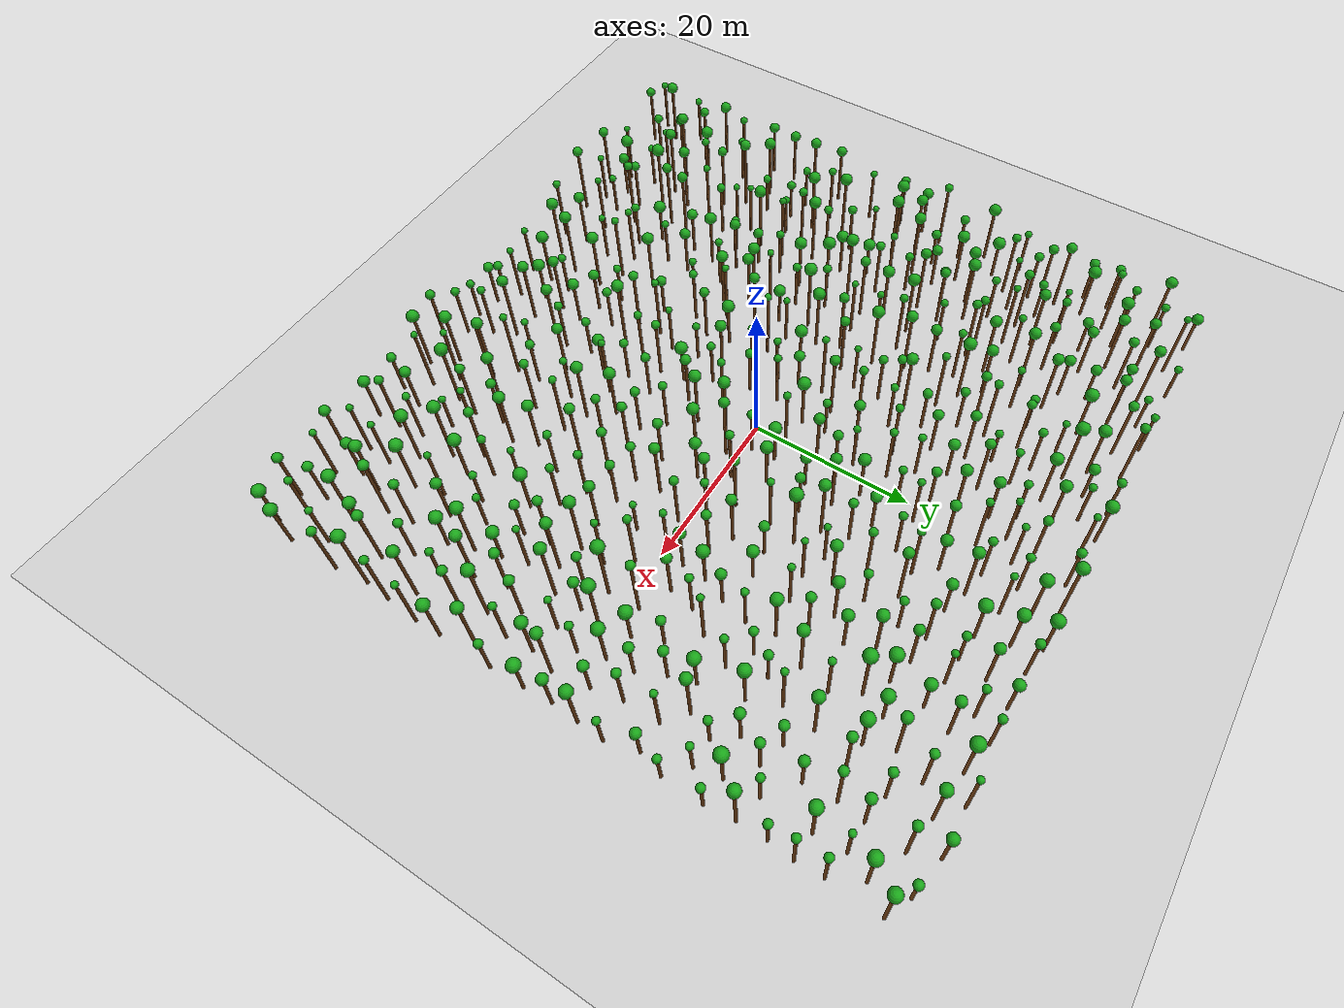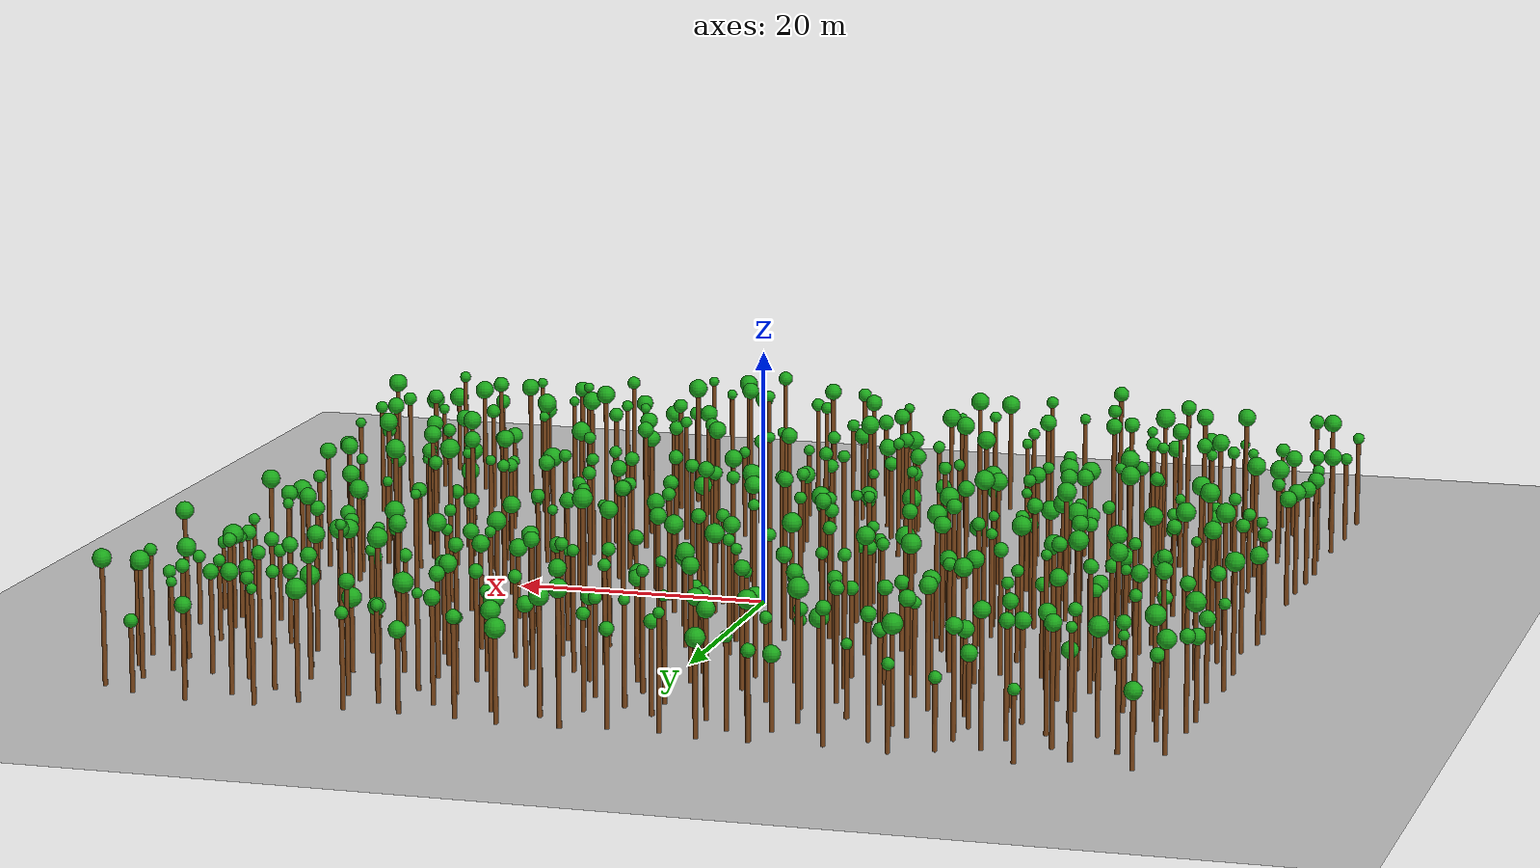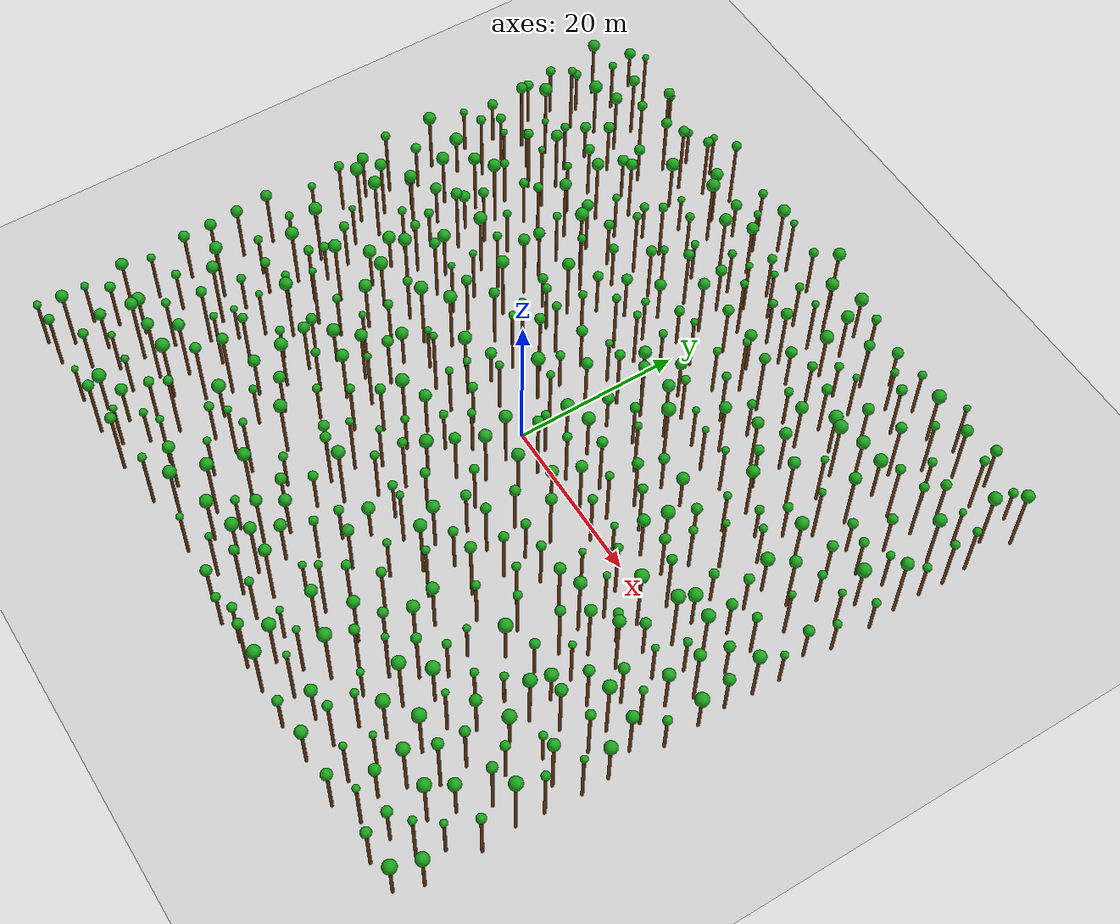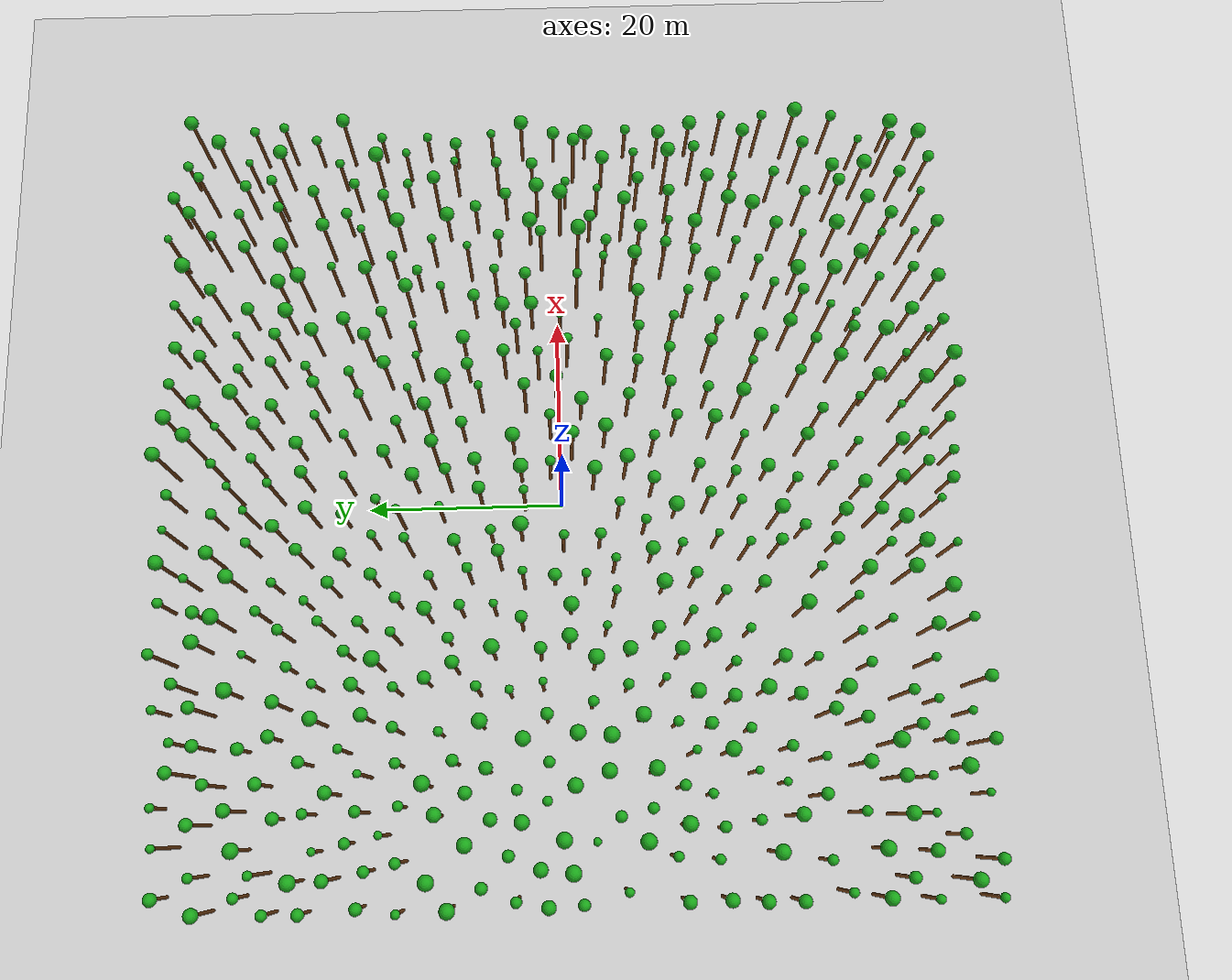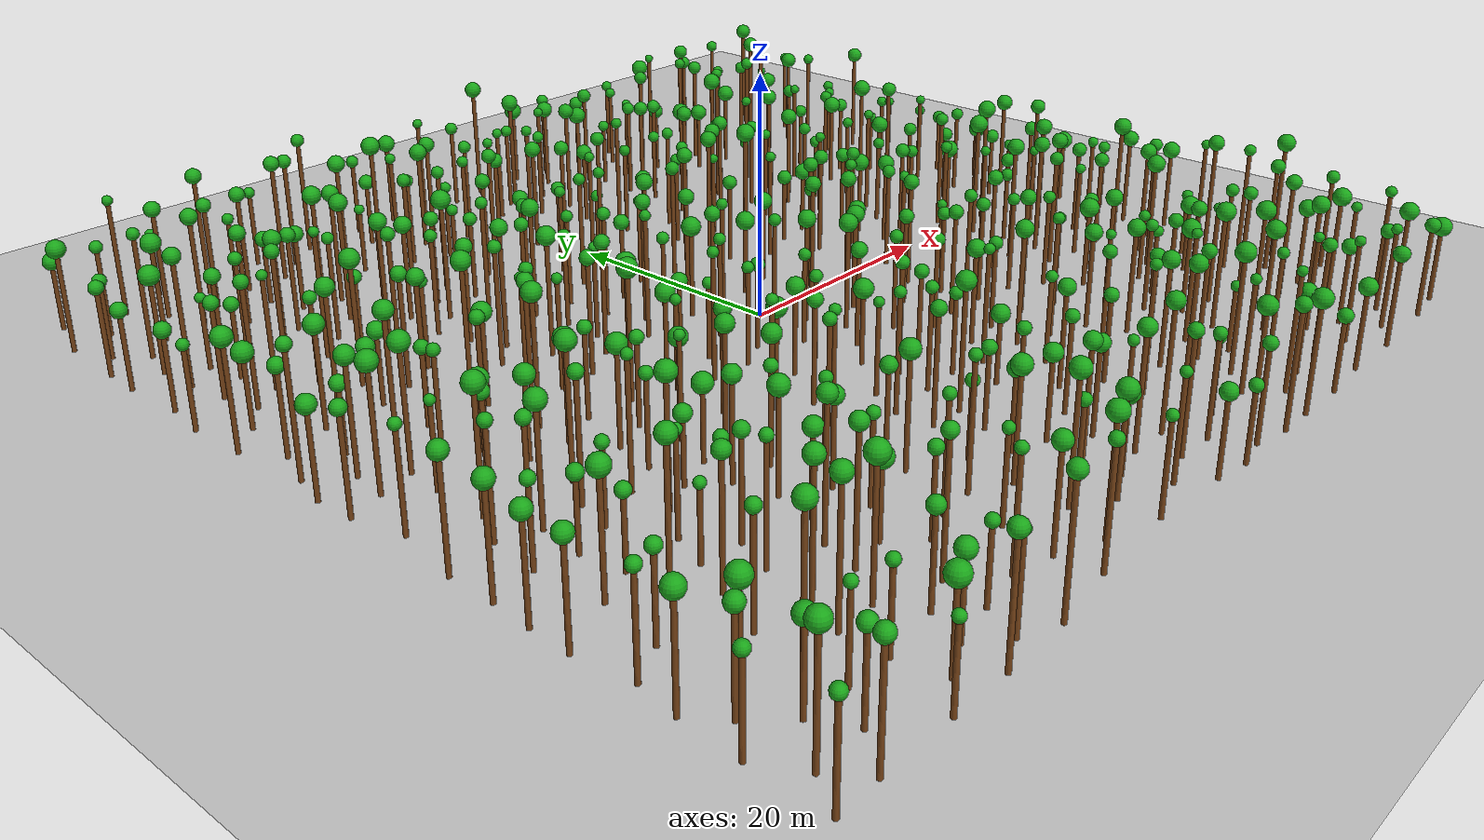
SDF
<?xml version="1.0" ?>
<sdf version="1.6">

<world name="forest_world">

  <include>
    <uri>model://sun</uri>
  </include>

  <include>
    <uri>model://ground_plane</uri>
  </include>

  <model name="tree_0">
    <static>true</static>

    <link name="tree_link">

      <!-- 树干碰撞 -->
      <collision name="trunk_collision">
        <pose>-19.41 8.62 4.64 0 0 0</pose>

        <geometry>
          <cylinder>
            <radius>0.18</radius>
            <length>9.27</length>
          </cylinder>
        </geometry>

      </collision>

      <!-- 树干视觉 -->
      <visual name="trunk_visual">

        <pose>-19.41 8.62 4.64 0 0 0</pose>

        <geometry>
          <cylinder>
            <radius>0.18</radius>
            <length>9.27</length>
          </cylinder>
        </geometry>

        <material>
          <ambient>0.35 0.20 0.05 1</ambient>
          <diffuse>0.45 0.25 0.08 1</diffuse>
        </material>

      </visual>

      <!-- 树冠（仅视觉） -->
      <visual name="leaf_visual">

        <pose>-19.41 8.62 9.53 0 0 0</pose>

        <geometry>
          <sphere>
            <radius>0.52</radius>
          </sphere>
        </geometry>

        <material>
          <ambient>0.05 0.45 0.05 1</ambient>
          <diffuse>0.10 0.65 0.10 1</diffuse>
        </material>

      </visual>

    </link>

  </model>

  <model name="tree_1">
    <static>true</static>

    <link name="tree_link">

      <!-- 树干碰撞 -->
      <collision name="trunk_collision">
        <pose>-16.93 -21.17 3.21 0 0 0</pose>

        <geometry>
          <cylinder>
            <radius>0.18</radius>
            <length>6.41</length>
          </cylinder>
        </geometry>

      </collision>

      <!-- 树干视觉 -->
      <visual name="trunk_visual">

        <pose>-16.93 -21.17 3.21 0 0 0</pose>

        <geometry>
          <cylinder>
            <radius>0.18</radius>
            <length>6.41</length>
          </cylinder>
        </geometry>

        <material>
          <ambient>0.35 0.20 0.05 1</ambient>
          <diffuse>0.45 0.25 0.08 1</diffuse>
        </material>

      </visual>

      <!-- 树冠（仅视觉） -->
      <visual name="leaf_visual">

        <pose>-16.93 -21.17 6.76 0 0 0</pose>

        <geometry>
          <sphere>
            <radius>0.69</radius>
          </sphere>
        </geometry>

        <material>
          <ambient>0.05 0.45 0.05 1</ambient>
          <diffuse>0.10 0.65 0.10 1</diffuse>
        </material>

      </visual>

    </link>

  </model>

  <model name="tree_2">
    <static>true</static>

    <link name="tree_link">

      <!-- 树干碰撞 -->
      <collision name="trunk_collision">
        <pose>8.46 -34.79 2.87 0 0 0</pose>

        <geometry>
          <cylinder>
            <radius>0.18</radius>
            <length>5.75</length>
          </cylinder>
        </geometry>

      </collision>

      <!-- 树干视觉 -->
      <visual name="trunk_visual">

        <pose>8.46 -34.79 2.87 0 0 0</pose>

        <geometry>
          <cylinder>
            <radius>0.18</radius>
            <length>5.75</length>
          </cylinder>
        </geometry>

        <material>
          <ambient>0.35 0.20 0.05 1</ambient>
          <diffuse>0.45 0.25 0.08 1</diffuse>
        </material>

      </visual>

      <!-- 树冠（仅视觉） -->
      <visual name="leaf_visual">

        <pose>8.46 -34.79 5.96 0 0 0</pose>

        <geometry>
          <sphere>
            <radius>0.42</radius>
          </sphere>
        </geometry>

        <material>
          <ambient>0.05 0.45 0.05 1</ambient>
          <diffuse>0.10 0.65 0.10 1</diffuse>
        </material>

      </visual>

    </link>

  </model>

  <model name="tree_3">
    <static>true</static>

    <link name="tree_link">

      <!-- 树干碰撞 -->
      <collision name="trunk_collision">
        <pose>-5.80 -32.55 2.88 0 0 0</pose>

        <geometry>
          <cylinder>
            <radius>0.18</radius>
            <length>5.76</length>
          </cylinder>
        </geometry>

      </collision>

      <!-- 树干视觉 -->
      <visual name="trunk_visual">

        <pose>-5.80 -32.55 2.88 0 0 0</pose>

        <geometry>
          <cylinder>
            <radius>0.18</radius>
            <length>5.76</length>
          </cylinder>
        </geometry>

        <material>
          <ambient>0.35 0.20 0.05 1</ambient>
          <diffuse>0.45 0.25 0.08 1</diffuse>
        </material>

      </visual>

      <!-- 树冠（仅视觉） -->
      <visual name="leaf_visual">

        <pose>-5.80 -32.55 6.01 0 0 0</pose>

        <geometry>
          <sphere>
            <radius>0.50</radius>
          </sphere>
        </geometry>

        <material>
          <ambient>0.05 0.45 0.05 1</ambient>
          <diffuse>0.10 0.65 0.10 1</diffuse>
        </material>

      </visual>

    </link>

  </model>

  <model name="tree_4">
    <static>true</static>

    <link name="tree_link">

      <!-- 树干碰撞 -->
      <collision name="trunk_collision">
        <pose>27.48 -29.07 4.06 0 0 0</pose>

        <geometry>
          <cylinder>
            <radius>0.18</radius>
            <length>8.13</length>
          </cylinder>
        </geometry>

      </collision>

      <!-- 树干视觉 -->
      <visual name="trunk_visual">

        <pose>27.48 -29.07 4.06 0 0 0</pose>

        <geometry>
          <cylinder>
            <radius>0.18</radius>
            <length>8.13</length>
          </cylinder>
        </geometry>

        <material>
          <ambient>0.35 0.20 0.05 1</ambient>
          <diffuse>0.45 0.25 0.08 1</diffuse>
        </material>

      </visual>

      <!-- 树冠（仅视觉） -->
      <visual name="leaf_visual">

        <pose>27.48 -29.07 8.52 0 0 0</pose>

        <geometry>
          <sphere>
            <radius>0.79</radius>
          </sphere>
        </geometry>

        <material>
          <ambient>0.05 0.45 0.05 1</ambient>
          <diffuse>0.10 0.65 0.10 1</diffuse>
        </material>

      </visual>

    </link>

  </model>

  <model name="tree_5">
    <static>true</static>

    <link name="tree_link">

      <!-- 树干碰撞 -->
      <collision name="trunk_collision">
        <pose>-27.25 -28.04 4.60 0 0 0</pose>

        <geometry>
          <cylinder>
            <radius>0.18</radius>
            <length>9.19</length>
          </cylinder>
        </geometry>

      </collision>

      <!-- 树干视觉 -->
      <visual name="trunk_visual">

        <pose>-27.25 -28.04 4.60 0 0 0</pose>

        <geometry>
          <cylinder>
            <radius>0.18</radius>
            <length>9.19</length>
          </cylinder>
        </geometry>

        <material>
          <ambient>0.35 0.20 0.05 1</ambient>
          <diffuse>0.45 0.25 0.08 1</diffuse>
        </material>

      </visual>

      <!-- 树冠（仅视觉） -->
      <visual name="leaf_visual">

        <pose>-27.25 -28.04 9.54 0 0 0</pose>

        <geometry>
          <sphere>
            <radius>0.69</radius>
          </sphere>
        </geometry>

        <material>
          <ambient>0.05 0.45 0.05 1</ambient>
          <diffuse>0.10 0.65 0.10 1</diffuse>
        </material>

      </visual>

    </link>

  </model>

  <model name="tree_6">
    <static>true</static>

    <link name="tree_link">

      <!-- 树干碰撞 -->
      <collision name="trunk_collision">
        <pose>-24.26 4.32 3.45 0 0 0</pose>

        <geometry>
          <cylinder>
            <radius>0.18</radius>
            <length>6.91</length>
          </cylinder>
        </geometry>

      </collision>

      <!-- 树干视觉 -->
      <visual name="trunk_visual">

        <pose>-24.26 4.32 3.45 0 0 0</pose>

        <geometry>
          <cylinder>
            <radius>0.18</radius>
            <length>6.91</length>
          </cylinder>
        </geometry>

        <material>
          <ambient>0.35 0.20 0.05 1</ambient>
          <diffuse>0.45 0.25 0.08 1</diffuse>
        </material>

      </visual>

      <!-- 树冠（仅视觉） -->
      <visual name="leaf_visual">

        <pose>-24.26 4.32 7.29 0 0 0</pose>

        <geometry>
          <sphere>
            <radius>0.76</radius>
          </sphere>
        </geometry>

        <material>
          <ambient>0.05 0.45 0.05 1</ambient>
          <diffuse>0.10 0.65 0.10 1</diffuse>
        </material>

      </visual>

    </link>

  </model>

  <model name="tree_7">
    <static>true</static>

    <link name="tree_link">

      <!-- 树干碰撞 -->
      <collision name="trunk_collision">
        <pose>13.70 29.05 4.06 0 0 0</pose>

        <geometry>
          <cylinder>
            <radius>0.18</radius>
            <length>8.11</length>
          </cylinder>
        </geometry>

      </collision>

      <!-- 树干视觉 -->
      <visual name="trunk_visual">

        <pose>13.70 29.05 4.06 0 0 0</pose>

        <geometry>
          <cylinder>
            <radius>0.18</radius>
            <length>8.11</length>
          </cylinder>
        </geometry>

        <material>
          <ambient>0.35 0.20 0.05 1</ambient>
          <diffuse>0.45 0.25 0.08 1</diffuse>
        </material>

      </visual>

      <!-- 树冠（仅视觉） -->
      <visual name="leaf_visual">

        <pose>13.70 29.05 8.39 0 0 0</pose>

        <geometry>
          <sphere>
            <radius>0.56</radius>
          </sphere>
        </geometry>

        <material>
          <ambient>0.05 0.45 0.05 1</ambient>
          <diffuse>0.10 0.65 0.10 1</diffuse>
        </material>

      </visual>

    </link>

  </model>

  <model name="tree_8">
    <static>true</static>

    <link name="tree_link">

      <!-- 树干碰撞 -->
      <collision name="trunk_collision">
        <pose>28.53 -11.77 3.78 0 0 0</pose>

        <geometry>
          <cylinder>
            <radius>0.18</radius>
            <length>7.57</length>
          </cylinder>
        </geometry>

      </collision>

      <!-- 树干视觉 -->
      <visual name="trunk_visual">

        <pose>28.53 -11.77 3.78 0 0 0</pose>

        <geometry>
          <cylinder>
            <radius>0.18</radius>
            <length>7.57</length>
          </cylinder>
        </geometry>

        <material>
          <ambient>0.35 0.20 0.05 1</ambient>
          <diffuse>0.45 0.25 0.08 1</diffuse>
        </material>

      </visual>

      <!-- 树冠（仅视觉） -->
      <visual name="leaf_visual">

        <pose>28.53 -11.77 7.78 0 0 0</pose>

        <geometry>
          <sphere>
            <radius>0.42</radius>
          </sphere>
        </geometry>

        <material>
          <ambient>0.05 0.45 0.05 1</ambient>
          <diffuse>0.10 0.65 0.10 1</diffuse>
        </material>

      </visual>

    </link>

  </model>

  <model name="tree_9">
    <static>true</static>

    <link name="tree_link">

      <!-- 树干碰撞 -->
      <collision name="trunk_collision">
        <pose>-26.77 37.26 4.96 0 0 0</pose>

        <geometry>
          <cylinder>
            <radius>0.18</radius>
            <length>9.92</length>
          </cylinder>
        </geometry>

      </collision>

      <!-- 树干视觉 -->
      <visual name="trunk_visual">

        <pose>-26.77 37.26 4.96 0 0 0</pose>

        <geometry>
          <cylinder>
            <radius>0.18</radius>
            <length>9.92</length>
          </cylinder>
        </geometry>

        <material>
          <ambient>0.35 0.20 0.05 1</ambient>
          <diffuse>0.45 0.25 0.08 1</diffuse>
        </material>

      </visual>

      <!-- 树冠（仅视觉） -->
      <visual name="leaf_visual">

        <pose>-26.77 37.26 10.24 0 0 0</pose>

        <geometry>
          <sphere>
            <radius>0.65</radius>
          </sphere>
        </geometry>

        <material>
          <ambient>0.05 0.45 0.05 1</ambient>
          <diffuse>0.10 0.65 0.10 1</diffuse>
        </material>

      </visual>

    </link>

  </model>

  <model name="tree_10">
    <static>true</static>

    <link name="tree_link">

      <!-- 树干碰撞 -->
      <collision name="trunk_collision">
        <pose>-39.45 -10.74 4.07 0 0 0</pose>

        <geometry>
          <cylinder>
            <radius>0.18</radius>
            <length>8.13</length>
          </cylinder>
        </geometry>

      </collision>

      <!-- 树干视觉 -->
      <visual name="trunk_visual">

        <pose>-39.45 -10.74 4.07 0 0 0</pose>

        <geometry>
          <cylinder>
            <radius>0.18</radius>
            <length>8.13</length>
          </cylinder>
        </geometry>

        <material>
          <ambient>0.35 0.20 0.05 1</ambient>
          <diffuse>0.45 0.25 0.08 1</diffuse>
        </material>

      </visual>

      <!-- 树冠（仅视觉） -->
      <visual name="leaf_visual">

        <pose>-39.45 -10.74 8.47 0 0 0</pose>

        <geometry>
          <sphere>
            <radius>0.67</radius>
          </sphere>
        </geometry>

        <material>
          <ambient>0.05 0.45 0.05 1</ambient>
          <diffuse>0.10 0.65 0.10 1</diffuse>
        </material>

      </visual>

    </link>

  </model>

  <model name="tree_11">
    <static>true</static>

    <link name="tree_link">

      <!-- 树干碰撞 -->
      <collision name="trunk_collision">
        <pose>-35.35 16.10 4.75 0 0 0</pose>

        <geometry>
          <cylinder>
            <radius>0.18</radius>
            <length>9.49</length>
          </cylinder>
        </geometry>

      </collision>

      <!-- 树干视觉 -->
      <visual name="trunk_visual">

        <pose>-35.35 16.10 4.75 0 0 0</pose>

        <geometry>
          <cylinder>
            <radius>0.18</radius>
            <length>9.49</length>
          </cylinder>
        </geometry>

        <material>
          <ambient>0.35 0.20 0.05 1</ambient>
          <diffuse>0.45 0.25 0.08 1</diffuse>
        </material>

      </visual>

      <!-- 树冠（仅视觉） -->
      <visual name="leaf_visual">

        <pose>-35.35 16.10 9.77 0 0 0</pose>

        <geometry>
          <sphere>
            <radius>0.55</radius>
          </sphere>
        </geometry>

        <material>
          <ambient>0.05 0.45 0.05 1</ambient>
          <diffuse>0.10 0.65 0.10 1</diffuse>
        </material>

      </visual>

    </link>

  </model>

  <model name="tree_12">
    <static>true</static>

    <link name="tree_link">

      <!-- 树干碰撞 -->
      <collision name="trunk_collision">
        <pose>37.89 34.98 4.30 0 0 0</pose>

        <geometry>
          <cylinder>
            <radius>0.18</radius>
            <length>8.60</length>
          </cylinder>
        </geometry>

      </collision>

      <!-- 树干视觉 -->
      <visual name="trunk_visual">

        <pose>37.89 34.98 4.30 0 0 0</pose>

        <geometry>
          <cylinder>
            <radius>0.18</radius>
            <length>8.60</length>
          </cylinder>
        </geometry>

        <material>
          <ambient>0.35 0.20 0.05 1</ambient>
          <diffuse>0.45 0.25 0.08 1</diffuse>
        </material>

      </visual>

      <!-- 树冠（仅视觉） -->
      <visual name="leaf_visual">

        <pose>37.89 34.98 8.98 0 0 0</pose>

        <geometry>
          <sphere>
            <radius>0.75</radius>
          </sphere>
        </geometry>

        <material>
          <ambient>0.05 0.45 0.05 1</ambient>
          <diffuse>0.10 0.65 0.10 1</diffuse>
        </material>

      </visual>

    </link>

  </model>

  <model name="tree_13">
    <static>true</static>

    <link name="tree_link">

      <!-- 树干碰撞 -->
      <collision name="trunk_collision">
        <pose>9.81 29.31 2.95 0 0 0</pose>

        <geometry>
          <cylinder>
            <radius>0.18</radius>
            <length>5.90</length>
          </cylinder>
        </geometry>

      </collision>

      <!-- 树干视觉 -->
      <visual name="trunk_visual">

        <pose>9.81 29.31 2.95 0 0 0</pose>

        <geometry>
          <cylinder>
            <radius>0.18</radius>
            <length>5.90</length>
          </cylinder>
        </geometry>

        <material>
          <ambient>0.35 0.20 0.05 1</ambient>
          <diffuse>0.45 0.25 0.08 1</diffuse>
        </material>

      </visual>

      <!-- 树冠（仅视觉） -->
      <visual name="leaf_visual">

        <pose>9.81 29.31 6.22 0 0 0</pose>

        <geometry>
          <sphere>
            <radius>0.65</radius>
          </sphere>
        </geometry>

        <material>
          <ambient>0.05 0.45 0.05 1</ambient>
          <diffuse>0.10 0.65 0.10 1</diffuse>
        </material>

      </visual>

    </link>

  </model>

  <model name="tree_14">
    <static>true</static>

    <link name="tree_link">

      <!-- 树干碰撞 -->
      <collision name="trunk_collision">
        <pose>39.79 3.40 3.92 0 0 0</pose>

        <geometry>
          <cylinder>
            <radius>0.18</radius>
            <length>7.84</length>
          </cylinder>
        </geometry>

      </collision>

      <!-- 树干视觉 -->
      <visual name="trunk_visual">

        <pose>39.79 3.40 3.92 0 0 0</pose>

        <geometry>
          <cylinder>
            <radius>0.18</radius>
            <length>7.84</length>
          </cylinder>
        </geometry>

        <material>
          <ambient>0.35 0.20 0.05 1</ambient>
          <diffuse>0.45 0.25 0.08 1</diffuse>
        </material>

      </visual>

      <!-- 树冠（仅视觉） -->
      <visual name="leaf_visual">

        <pose>39.79 3.40 8.22 0 0 0</pose>

        <geometry>
          <sphere>
            <radius>0.74</radius>
          </sphere>
        </geometry>

        <material>
          <ambient>0.05 0.45 0.05 1</ambient>
          <diffuse>0.10 0.65 0.10 1</diffuse>
        </material>

      </visual>

    </link>

  </model>

  <model name="tree_15">
    <static>true</static>

    <link name="tree_link">

      <!-- 树干碰撞 -->
      <collision name="trunk_collision">
        <pose>33.84 -1.15 3.05 0 0 0</pose>

        <geometry>
          <cylinder>
            <radius>0.18</radius>
            <length>6.11</length>
          </cylinder>
        </geometry>

      </collision>

      <!-- 树干视觉 -->
      <visual name="trunk_visual">

        <pose>33.84 -1.15 3.05 0 0 0</pose>

        <geometry>
          <cylinder>
            <radius>0.18</radius>
            <length>6.11</length>
          </cylinder>
        </geometry>

        <material>
          <ambient>0.35 0.20 0.05 1</ambient>
          <diffuse>0.45 0.25 0.08 1</diffuse>
        </material>

      </visual>

      <!-- 树冠（仅视觉） -->
      <visual name="leaf_visual">

        <pose>33.84 -1.15 6.35 0 0 0</pose>

        <geometry>
          <sphere>
            <radius>0.48</radius>
          </sphere>
        </geometry>

        <material>
          <ambient>0.05 0.45 0.05 1</ambient>
          <diffuse>0.10 0.65 0.10 1</diffuse>
        </material>

      </visual>

    </link>

  </model>

  <model name="tree_16">
    <static>true</static>

    <link name="tree_link">

      <!-- 树干碰撞 -->
      <collision name="trunk_collision">
        <pose>16.18 39.34 2.98 0 0 0</pose>

        <geometry>
          <cylinder>
            <radius>0.18</radius>
            <length>5.95</length>
          </cylinder>
        </geometry>

      </collision>

      <!-- 树干视觉 -->
      <visual name="trunk_visual">

        <pose>16.18 39.34 2.98 0 0 0</pose>

        <geometry>
          <cylinder>
            <radius>0.18</radius>
            <length>5.95</length>
          </cylinder>
        </geometry>

        <material>
          <ambient>0.35 0.20 0.05 1</ambient>
          <diffuse>0.45 0.25 0.08 1</diffuse>
        </material>

      </visual>

      <!-- 树冠（仅视觉） -->
      <visual name="leaf_visual">

        <pose>16.18 39.34 6.28 0 0 0</pose>

        <geometry>
          <sphere>
            <radius>0.66</radius>
          </sphere>
        </geometry>

        <material>
          <ambient>0.05 0.45 0.05 1</ambient>
          <diffuse>0.10 0.65 0.10 1</diffuse>
        </material>

      </visual>

    </link>

  </model>

  <model name="tree_17">
    <static>true</static>

    <link name="tree_link">

      <!-- 树干碰撞 -->
      <collision name="trunk_collision">
        <pose>0.88 28.86 4.50 0 0 0</pose>

        <geometry>
          <cylinder>
            <radius>0.18</radius>
            <length>9.00</length>
          </cylinder>
        </geometry>

      </collision>

      <!-- 树干视觉 -->
      <visual name="trunk_visual">

        <pose>0.88 28.86 4.50 0 0 0</pose>

        <geometry>
          <cylinder>
            <radius>0.18</radius>
            <length>9.00</length>
          </cylinder>
        </geometry>

        <material>
          <ambient>0.35 0.20 0.05 1</ambient>
          <diffuse>0.45 0.25 0.08 1</diffuse>
        </material>

      </visual>

      <!-- 树冠（仅视觉） -->
      <visual name="leaf_visual">

        <pose>0.88 28.86 9.23 0 0 0</pose>

        <geometry>
          <sphere>
            <radius>0.46</radius>
          </sphere>
        </geometry>

        <material>
          <ambient>0.05 0.45 0.05 1</ambient>
          <diffuse>0.10 0.65 0.10 1</diffuse>
        </material>

      </visual>

    </link>

  </model>

  <model name="tree_18">
    <static>true</static>

    <link name="tree_link">

      <!-- 树干碰撞 -->
      <collision name="trunk_collision">
        <pose>38.51 -11.05 3.80 0 0 0</pose>

        <geometry>
          <cylinder>
            <radius>0.18</radius>
            <length>7.59</length>
          </cylinder>
        </geometry>

      </collision>

      <!-- 树干视觉 -->
      <visual name="trunk_visual">

        <pose>38.51 -11.05 3.80 0 0 0</pose>

        <geometry>
          <cylinder>
            <radius>0.18</radius>
            <length>7.59</length>
          </cylinder>
        </geometry>

        <material>
          <ambient>0.35 0.20 0.05 1</ambient>
          <diffuse>0.45 0.25 0.08 1</diffuse>
        </material>

      </visual>

      <!-- 树冠（仅视觉） -->
      <visual name="leaf_visual">

        <pose>38.51 -11.05 7.94 0 0 0</pose>

        <geometry>
          <sphere>
            <radius>0.70</radius>
          </sphere>
        </geometry>

        <material>
          <ambient>0.05 0.45 0.05 1</ambient>
          <diffuse>0.10 0.65 0.10 1</diffuse>
        </material>

      </visual>

    </link>

  </model>

  <model name="tree_19">
    <static>true</static>

    <link name="tree_link">

      <!-- 树干碰撞 -->
      <collision name="trunk_collision">
        <pose>-20.57 -22.48 3.07 0 0 0</pose>

        <geometry>
          <cylinder>
            <radius>0.18</radius>
            <length>6.14</length>
          </cylinder>
        </geometry>

      </collision>

      <!-- 树干视觉 -->
      <visual name="trunk_visual">

        <pose>-20.57 -22.48 3.07 0 0 0</pose>

        <geometry>
          <cylinder>
            <radius>0.18</radius>
            <length>6.14</length>
          </cylinder>
        </geometry>

        <material>
          <ambient>0.35 0.20 0.05 1</ambient>
          <diffuse>0.45 0.25 0.08 1</diffuse>
        </material>

      </visual>

      <!-- 树冠（仅视觉） -->
      <visual name="leaf_visual">

        <pose>-20.57 -22.48 6.49 0 0 0</pose>

        <geometry>
          <sphere>
            <radius>0.70</radius>
          </sphere>
        </geometry>

        <material>
          <ambient>0.05 0.45 0.05 1</ambient>
          <diffuse>0.10 0.65 0.10 1</diffuse>
        </material>

      </visual>

    </link>

  </model>

  <model name="tree_20">
    <static>true</static>

    <link name="tree_link">

      <!-- 树干碰撞 -->
      <collision name="trunk_collision">
        <pose>-4.93 15.45 4.53 0 0 0</pose>

        <geometry>
          <cylinder>
            <radius>0.18</radius>
            <length>9.05</length>
          </cylinder>
        </geometry>

      </collision>

      <!-- 树干视觉 -->
      <visual name="trunk_visual">

        <pose>-4.93 15.45 4.53 0 0 0</pose>

        <geometry>
          <cylinder>
            <radius>0.18</radius>
            <length>9.05</length>
          </cylinder>
        </geometry>

        <material>
          <ambient>0.35 0.20 0.05 1</ambient>
          <diffuse>0.45 0.25 0.08 1</diffuse>
        </material>

      </visual>

      <!-- 树冠（仅视觉） -->
      <visual name="leaf_visual">

        <pose>-4.93 15.45 9.30 0 0 0</pose>

        <geometry>
          <sphere>
            <radius>0.49</radius>
          </sphere>
        </geometry>

        <material>
          <ambient>0.05 0.45 0.05 1</ambient>
          <diffuse>0.10 0.65 0.10 1</diffuse>
        </material>

      </visual>

    </link>

  </model>

  <model name="tree_21">
    <static>true</static>

    <link name="tree_link">

      <!-- 树干碰撞 -->
      <collision name="trunk_collision">
        <pose>-15.39 31.66 2.68 0 0 0</pose>

        <geometry>
          <cylinder>
            <radius>0.18</radius>
            <length>5.36</length>
          </cylinder>
        </geometry>

      </collision>

      <!-- 树干视觉 -->
      <visual name="trunk_visual">

        <pose>-15.39 31.66 2.68 0 0 0</pose>

        <geometry>
          <cylinder>
            <radius>0.18</radius>
            <length>5.36</length>
          </cylinder>
        </geometry>

        <material>
          <ambient>0.35 0.20 0.05 1</ambient>
          <diffuse>0.45 0.25 0.08 1</diffuse>
        </material>

      </visual>

      <!-- 树冠（仅视觉） -->
      <visual name="leaf_visual">

        <pose>-15.39 31.66 5.57 0 0 0</pose>

        <geometry>
          <sphere>
            <radius>0.42</radius>
          </sphere>
        </geometry>

        <material>
          <ambient>0.05 0.45 0.05 1</ambient>
          <diffuse>0.10 0.65 0.10 1</diffuse>
        </material>

      </visual>

    </link>

  </model>

  <model name="tree_22">
    <static>true</static>

    <link name="tree_link">

      <!-- 树干碰撞 -->
      <collision name="trunk_collision">
        <pose>36.79 28.59 4.12 0 0 0</pose>

        <geometry>
          <cylinder>
            <radius>0.18</radius>
            <length>8.23</length>
          </cylinder>
        </geometry>

      </collision>

      <!-- 树干视觉 -->
      <visual name="trunk_visual">

        <pose>36.79 28.59 4.12 0 0 0</pose>

        <geometry>
          <cylinder>
            <radius>0.18</radius>
            <length>8.23</length>
          </cylinder>
        </geometry>

        <material>
          <ambient>0.35 0.20 0.05 1</ambient>
          <diffuse>0.45 0.25 0.08 1</diffuse>
        </material>

      </visual>

      <!-- 树冠（仅视觉） -->
      <visual name="leaf_visual">

        <pose>36.79 28.59 8.59 0 0 0</pose>

        <geometry>
          <sphere>
            <radius>0.73</radius>
          </sphere>
        </geometry>

        <material>
          <ambient>0.05 0.45 0.05 1</ambient>
          <diffuse>0.10 0.65 0.10 1</diffuse>
        </material>

      </visual>

    </link>

  </model>

  <model name="tree_23">
    <static>true</static>

    <link name="tree_link">

      <!-- 树干碰撞 -->
      <collision name="trunk_collision">
        <pose>-3.61 7.23 2.82 0 0 0</pose>

        <geometry>
          <cylinder>
            <radius>0.18</radius>
            <length>5.63</length>
          </cylinder>
        </geometry>

      </collision>

      <!-- 树干视觉 -->
      <visual name="trunk_visual">

        <pose>-3.61 7.23 2.82 0 0 0</pose>

        <geometry>
          <cylinder>
            <radius>0.18</radius>
            <length>5.63</length>
          </cylinder>
        </geometry>

        <material>
          <ambient>0.35 0.20 0.05 1</ambient>
          <diffuse>0.45 0.25 0.08 1</diffuse>
        </material>

      </visual>

      <!-- 树冠（仅视觉） -->
      <visual name="leaf_visual">

        <pose>-3.61 7.23 5.89 0 0 0</pose>

        <geometry>
          <sphere>
            <radius>0.52</radius>
          </sphere>
        </geometry>

        <material>
          <ambient>0.05 0.45 0.05 1</ambient>
          <diffuse>0.10 0.65 0.10 1</diffuse>
        </material>

      </visual>

    </link>

  </model>

  <model name="tree_24">
    <static>true</static>

    <link name="tree_link">

      <!-- 树干碰撞 -->
      <collision name="trunk_collision">
        <pose>-19.68 5.52 3.93 0 0 0</pose>

        <geometry>
          <cylinder>
            <radius>0.18</radius>
            <length>7.86</length>
          </cylinder>
        </geometry>

      </collision>

      <!-- 树干视觉 -->
      <visual name="trunk_visual">

        <pose>-19.68 5.52 3.93 0 0 0</pose>

        <geometry>
          <cylinder>
            <radius>0.18</radius>
            <length>7.86</length>
          </cylinder>
        </geometry>

        <material>
          <ambient>0.35 0.20 0.05 1</ambient>
          <diffuse>0.45 0.25 0.08 1</diffuse>
        </material>

      </visual>

      <!-- 树冠（仅视觉） -->
      <visual name="leaf_visual">

        <pose>-19.68 5.52 8.08 0 0 0</pose>

        <geometry>
          <sphere>
            <radius>0.44</radius>
          </sphere>
        </geometry>

        <material>
          <ambient>0.05 0.45 0.05 1</ambient>
          <diffuse>0.10 0.65 0.10 1</diffuse>
        </material>

      </visual>

    </link>

  </model>

  <model name="tree_25">
    <static>true</static>

    <link name="tree_link">

      <!-- 树干碰撞 -->
      <collision name="trunk_collision">
        <pose>7.45 -11.72 3.59 0 0 0</pose>

        <geometry>
          <cylinder>
            <radius>0.18</radius>
            <length>7.17</length>
          </cylinder>
        </geometry>

      </collision>

      <!-- 树干视觉 -->
      <visual name="trunk_visual">

        <pose>7.45 -11.72 3.59 0 0 0</pose>

        <geometry>
          <cylinder>
            <radius>0.18</radius>
            <length>7.17</length>
          </cylinder>
        </geometry>

        <material>
          <ambient>0.35 0.20 0.05 1</ambient>
          <diffuse>0.45 0.25 0.08 1</diffuse>
        </material>

      </visual>

      <!-- 树冠（仅视觉） -->
      <visual name="leaf_visual">

        <pose>7.45 -11.72 7.46 0 0 0</pose>

        <geometry>
          <sphere>
            <radius>0.58</radius>
          </sphere>
        </geometry>

        <material>
          <ambient>0.05 0.45 0.05 1</ambient>
          <diffuse>0.10 0.65 0.10 1</diffuse>
        </material>

      </visual>

    </link>

  </model>

  <model name="tree_26">
    <static>true</static>

    <link name="tree_link">

      <!-- 树干碰撞 -->
      <collision name="trunk_collision">
        <pose>22.42 26.23 4.66 0 0 0</pose>

        <geometry>
          <cylinder>
            <radius>0.18</radius>
            <length>9.32</length>
          </cylinder>
        </geometry>

      </collision>

      <!-- 树干视觉 -->
      <visual name="trunk_visual">

        <pose>22.42 26.23 4.66 0 0 0</pose>

        <geometry>
          <cylinder>
            <radius>0.18</radius>
            <length>9.32</length>
          </cylinder>
        </geometry>

        <material>
          <ambient>0.35 0.20 0.05 1</ambient>
          <diffuse>0.45 0.25 0.08 1</diffuse>
        </material>

      </visual>

      <!-- 树冠（仅视觉） -->
      <visual name="leaf_visual">

        <pose>22.42 26.23 9.72 0 0 0</pose>

        <geometry>
          <sphere>
            <radius>0.79</radius>
          </sphere>
        </geometry>

        <material>
          <ambient>0.05 0.45 0.05 1</ambient>
          <diffuse>0.10 0.65 0.10 1</diffuse>
        </material>

      </visual>

    </link>

  </model>

  <model name="tree_27">
    <static>true</static>

    <link name="tree_link">

      <!-- 树干碰撞 -->
      <collision name="trunk_collision">
        <pose>10.89 33.26 3.55 0 0 0</pose>

        <geometry>
          <cylinder>
            <radius>0.18</radius>
            <length>7.11</length>
          </cylinder>
        </geometry>

      </collision>

      <!-- 树干视觉 -->
      <visual name="trunk_visual">

        <pose>10.89 33.26 3.55 0 0 0</pose>

        <geometry>
          <cylinder>
            <radius>0.18</radius>
            <length>7.11</length>
          </cylinder>
        </geometry>

        <material>
          <ambient>0.35 0.20 0.05 1</ambient>
          <diffuse>0.45 0.25 0.08 1</diffuse>
        </material>

      </visual>

      <!-- 树冠（仅视觉） -->
      <visual name="leaf_visual">

        <pose>10.89 33.26 7.50 0 0 0</pose>

        <geometry>
          <sphere>
            <radius>0.78</radius>
          </sphere>
        </geometry>

        <material>
          <ambient>0.05 0.45 0.05 1</ambient>
          <diffuse>0.10 0.65 0.10 1</diffuse>
        </material>

      </visual>

    </link>

  </model>

  <model name="tree_28">
    <static>true</static>

    <link name="tree_link">

      <!-- 树干碰撞 -->
      <collision name="trunk_collision">
        <pose>1.74 21.55 3.98 0 0 0</pose>

        <geometry>
          <cylinder>
            <radius>0.18</radius>
            <length>7.95</length>
          </cylinder>
        </geometry>

      </collision>

      <!-- 树干视觉 -->
      <visual name="trunk_visual">

        <pose>1.74 21.55 3.98 0 0 0</pose>

        <geometry>
          <cylinder>
            <radius>0.18</radius>
            <length>7.95</length>
          </cylinder>
        </geometry>

        <material>
          <ambient>0.35 0.20 0.05 1</ambient>
          <diffuse>0.45 0.25 0.08 1</diffuse>
        </material>

      </visual>

      <!-- 树冠（仅视觉） -->
      <visual name="leaf_visual">

        <pose>1.74 21.55 8.17 0 0 0</pose>

        <geometry>
          <sphere>
            <radius>0.43</radius>
          </sphere>
        </geometry>

        <material>
          <ambient>0.05 0.45 0.05 1</ambient>
          <diffuse>0.10 0.65 0.10 1</diffuse>
        </material>

      </visual>

    </link>

  </model>

  <model name="tree_29">
    <static>true</static>

    <link name="tree_link">

      <!-- 树干碰撞 -->
      <collision name="trunk_collision">
        <pose>-33.89 31.49 3.86 0 0 0</pose>

        <geometry>
          <cylinder>
            <radius>0.18</radius>
            <length>7.73</length>
          </cylinder>
        </geometry>

      </collision>

      <!-- 树干视觉 -->
      <visual name="trunk_visual">

        <pose>-33.89 31.49 3.86 0 0 0</pose>

        <geometry>
          <cylinder>
            <radius>0.18</radius>
            <length>7.73</length>
          </cylinder>
        </geometry>

        <material>
          <ambient>0.35 0.20 0.05 1</ambient>
          <diffuse>0.45 0.25 0.08 1</diffuse>
        </material>

      </visual>

      <!-- 树冠（仅视觉） -->
      <visual name="leaf_visual">

        <pose>-33.89 31.49 8.12 0 0 0</pose>

        <geometry>
          <sphere>
            <radius>0.78</radius>
          </sphere>
        </geometry>

        <material>
          <ambient>0.05 0.45 0.05 1</ambient>
          <diffuse>0.10 0.65 0.10 1</diffuse>
        </material>

      </visual>

    </link>

  </model>

  <model name="tree_30">
    <static>true</static>

    <link name="tree_link">

      <!-- 树干碰撞 -->
      <collision name="trunk_collision">
        <pose>27.01 -18.96 2.71 0 0 0</pose>

        <geometry>
          <cylinder>
            <radius>0.18</radius>
            <length>5.43</length>
          </cylinder>
        </geometry>

      </collision>

      <!-- 树干视觉 -->
      <visual name="trunk_visual">

        <pose>27.01 -18.96 2.71 0 0 0</pose>

        <geometry>
          <cylinder>
            <radius>0.18</radius>
            <length>5.43</length>
          </cylinder>
        </geometry>

        <material>
          <ambient>0.35 0.20 0.05 1</ambient>
          <diffuse>0.45 0.25 0.08 1</diffuse>
        </material>

      </visual>

      <!-- 树冠（仅视觉） -->
      <visual name="leaf_visual">

        <pose>27.01 -18.96 5.67 0 0 0</pose>

        <geometry>
          <sphere>
            <radius>0.47</radius>
          </sphere>
        </geometry>

        <material>
          <ambient>0.05 0.45 0.05 1</ambient>
          <diffuse>0.10 0.65 0.10 1</diffuse>
        </material>

      </visual>

    </link>

  </model>

  <model name="tree_31">
    <static>true</static>

    <link name="tree_link">

      <!-- 树干碰撞 -->
      <collision name="trunk_collision">
        <pose>36.55 22.73 3.00 0 0 0</pose>

        <geometry>
          <cylinder>
            <radius>0.18</radius>
            <length>6.00</length>
          </cylinder>
        </geometry>

      </collision>

      <!-- 树干视觉 -->
      <visual name="trunk_visual">

        <pose>36.55 22.73 3.00 0 0 0</pose>

        <geometry>
          <cylinder>
            <radius>0.18</radius>
            <length>6.00</length>
          </cylinder>
        </geometry>

        <material>
          <ambient>0.35 0.20 0.05 1</ambient>
          <diffuse>0.45 0.25 0.08 1</diffuse>
        </material>

      </visual>

      <!-- 树冠（仅视觉） -->
      <visual name="leaf_visual">

        <pose>36.55 22.73 6.23 0 0 0</pose>

        <geometry>
          <sphere>
            <radius>0.47</radius>
          </sphere>
        </geometry>

        <material>
          <ambient>0.05 0.45 0.05 1</ambient>
          <diffuse>0.10 0.65 0.10 1</diffuse>
        </material>

      </visual>

    </link>

  </model>

  <model name="tree_32">
    <static>true</static>

    <link name="tree_link">

      <!-- 树干碰撞 -->
      <collision name="trunk_collision">
        <pose>32.60 18.05 3.17 0 0 0</pose>

        <geometry>
          <cylinder>
            <radius>0.18</radius>
            <length>6.34</length>
          </cylinder>
        </geometry>

      </collision>

      <!-- 树干视觉 -->
      <visual name="trunk_visual">

        <pose>32.60 18.05 3.17 0 0 0</pose>

        <geometry>
          <cylinder>
            <radius>0.18</radius>
            <length>6.34</length>
          </cylinder>
        </geometry>

        <material>
          <ambient>0.35 0.20 0.05 1</ambient>
          <diffuse>0.45 0.25 0.08 1</diffuse>
        </material>

      </visual>

      <!-- 树冠（仅视觉） -->
      <visual name="leaf_visual">

        <pose>32.60 18.05 6.65 0 0 0</pose>

        <geometry>
          <sphere>
            <radius>0.61</radius>
          </sphere>
        </geometry>

        <material>
          <ambient>0.05 0.45 0.05 1</ambient>
          <diffuse>0.10 0.65 0.10 1</diffuse>
        </material>

      </visual>

    </link>

  </model>

  <model name="tree_33">
    <static>true</static>

    <link name="tree_link">

      <!-- 树干碰撞 -->
      <collision name="trunk_collision">
        <pose>17.87 -11.85 3.83 0 0 0</pose>

        <geometry>
          <cylinder>
            <radius>0.18</radius>
            <length>7.66</length>
          </cylinder>
        </geometry>

      </collision>

      <!-- 树干视觉 -->
      <visual name="trunk_visual">

        <pose>17.87 -11.85 3.83 0 0 0</pose>

        <geometry>
          <cylinder>
            <radius>0.18</radius>
            <length>7.66</length>
          </cylinder>
        </geometry>

        <material>
          <ambient>0.35 0.20 0.05 1</ambient>
          <diffuse>0.45 0.25 0.08 1</diffuse>
        </material>

      </visual>

      <!-- 树冠（仅视觉） -->
      <visual name="leaf_visual">

        <pose>17.87 -11.85 7.91 0 0 0</pose>

        <geometry>
          <sphere>
            <radius>0.50</radius>
          </sphere>
        </geometry>

        <material>
          <ambient>0.05 0.45 0.05 1</ambient>
          <diffuse>0.10 0.65 0.10 1</diffuse>
        </material>

      </visual>

    </link>

  </model>

  <model name="tree_34">
    <static>true</static>

    <link name="tree_link">

      <!-- 树干碰撞 -->
      <collision name="trunk_collision">
        <pose>-24.49 31.77 2.62 0 0 0</pose>

        <geometry>
          <cylinder>
            <radius>0.18</radius>
            <length>5.24</length>
          </cylinder>
        </geometry>

      </collision>

      <!-- 树干视觉 -->
      <visual name="trunk_visual">

        <pose>-24.49 31.77 2.62 0 0 0</pose>

        <geometry>
          <cylinder>
            <radius>0.18</radius>
            <length>5.24</length>
          </cylinder>
        </geometry>

        <material>
          <ambient>0.35 0.20 0.05 1</ambient>
          <diffuse>0.45 0.25 0.08 1</diffuse>
        </material>

      </visual>

      <!-- 树冠（仅视觉） -->
      <visual name="leaf_visual">

        <pose>-24.49 31.77 5.57 0 0 0</pose>

        <geometry>
          <sphere>
            <radius>0.65</radius>
          </sphere>
        </geometry>

        <material>
          <ambient>0.05 0.45 0.05 1</ambient>
          <diffuse>0.10 0.65 0.10 1</diffuse>
        </material>

      </visual>

    </link>

  </model>

  <model name="tree_35">
    <static>true</static>

    <link name="tree_link">

      <!-- 树干碰撞 -->
      <collision name="trunk_collision">
        <pose>28.33 6.03 2.61 0 0 0</pose>

        <geometry>
          <cylinder>
            <radius>0.18</radius>
            <length>5.22</length>
          </cylinder>
        </geometry>

      </collision>

      <!-- 树干视觉 -->
      <visual name="trunk_visual">

        <pose>28.33 6.03 2.61 0 0 0</pose>

        <geometry>
          <cylinder>
            <radius>0.18</radius>
            <length>5.22</length>
          </cylinder>
        </geometry>

        <material>
          <ambient>0.35 0.20 0.05 1</ambient>
          <diffuse>0.45 0.25 0.08 1</diffuse>
        </material>

      </visual>

      <!-- 树冠（仅视觉） -->
      <visual name="leaf_visual">

        <pose>28.33 6.03 5.50 0 0 0</pose>

        <geometry>
          <sphere>
            <radius>0.56</radius>
          </sphere>
        </geometry>

        <material>
          <ambient>0.05 0.45 0.05 1</ambient>
          <diffuse>0.10 0.65 0.10 1</diffuse>
        </material>

      </visual>

    </link>

  </model>

  <model name="tree_36">
    <static>true</static>

    <link name="tree_link">

      <!-- 树干碰撞 -->
      <collision name="trunk_collision">
        <pose>1.06 -23.70 2.79 0 0 0</pose>

        <geometry>
          <cylinder>
            <radius>0.18</radius>
            <length>5.59</length>
          </cylinder>
        </geometry>

      </collision>

      <!-- 树干视觉 -->
      <visual name="trunk_visual">

        <pose>1.06 -23.70 2.79 0 0 0</pose>

        <geometry>
          <cylinder>
            <radius>0.18</radius>
            <length>5.59</length>
          </cylinder>
        </geometry>

        <material>
          <ambient>0.35 0.20 0.05 1</ambient>
          <diffuse>0.45 0.25 0.08 1</diffuse>
        </material>

      </visual>

      <!-- 树冠（仅视觉） -->
      <visual name="leaf_visual">

        <pose>1.06 -23.70 5.86 0 0 0</pose>

        <geometry>
          <sphere>
            <radius>0.55</radius>
          </sphere>
        </geometry>

        <material>
          <ambient>0.05 0.45 0.05 1</ambient>
          <diffuse>0.10 0.65 0.10 1</diffuse>
        </material>

      </visual>

    </link>

  </model>

  <model name="tree_37">
    <static>true</static>

    <link name="tree_link">

      <!-- 树干碰撞 -->
      <collision name="trunk_collision">
        <pose>-30.23 16.21 3.31 0 0 0</pose>

        <geometry>
          <cylinder>
            <radius>0.18</radius>
            <length>6.62</length>
          </cylinder>
        </geometry>

      </collision>

      <!-- 树干视觉 -->
      <visual name="trunk_visual">

        <pose>-30.23 16.21 3.31 0 0 0</pose>

        <geometry>
          <cylinder>
            <radius>0.18</radius>
            <length>6.62</length>
          </cylinder>
        </geometry>

        <material>
          <ambient>0.35 0.20 0.05 1</ambient>
          <diffuse>0.45 0.25 0.08 1</diffuse>
        </material>

      </visual>

      <!-- 树冠（仅视觉） -->
      <visual name="leaf_visual">

        <pose>-30.23 16.21 6.88 0 0 0</pose>

        <geometry>
          <sphere>
            <radius>0.52</radius>
          </sphere>
        </geometry>

        <material>
          <ambient>0.05 0.45 0.05 1</ambient>
          <diffuse>0.10 0.65 0.10 1</diffuse>
        </material>

      </visual>

    </link>

  </model>

  <model name="tree_38">
    <static>true</static>

    <link name="tree_link">

      <!-- 树干碰撞 -->
      <collision name="trunk_collision">
        <pose>-12.10 -23.41 4.27 0 0 0</pose>

        <geometry>
          <cylinder>
            <radius>0.18</radius>
            <length>8.53</length>
          </cylinder>
        </geometry>

      </collision>

      <!-- 树干视觉 -->
      <visual name="trunk_visual">

        <pose>-12.10 -23.41 4.27 0 0 0</pose>

        <geometry>
          <cylinder>
            <radius>0.18</radius>
            <length>8.53</length>
          </cylinder>
        </geometry>

        <material>
          <ambient>0.35 0.20 0.05 1</ambient>
          <diffuse>0.45 0.25 0.08 1</diffuse>
        </material>

      </visual>

      <!-- 树冠（仅视觉） -->
      <visual name="leaf_visual">

        <pose>-12.10 -23.41 8.91 0 0 0</pose>

        <geometry>
          <sphere>
            <radius>0.75</radius>
          </sphere>
        </geometry>

        <material>
          <ambient>0.05 0.45 0.05 1</ambient>
          <diffuse>0.10 0.65 0.10 1</diffuse>
        </material>

      </visual>

    </link>

  </model>

  <model name="tree_39">
    <static>true</static>

    <link name="tree_link">

      <!-- 树干碰撞 -->
      <collision name="trunk_collision">
        <pose>9.24 -18.27 4.57 0 0 0</pose>

        <geometry>
          <cylinder>
            <radius>0.18</radius>
            <length>9.15</length>
          </cylinder>
        </geometry>

      </collision>

      <!-- 树干视觉 -->
      <visual name="trunk_visual">

        <pose>9.24 -18.27 4.57 0 0 0</pose>

        <geometry>
          <cylinder>
            <radius>0.18</radius>
            <length>9.15</length>
          </cylinder>
        </geometry>

        <material>
          <ambient>0.35 0.20 0.05 1</ambient>
          <diffuse>0.45 0.25 0.08 1</diffuse>
        </material>

      </visual>

      <!-- 树冠（仅视觉） -->
      <visual name="leaf_visual">

        <pose>9.24 -18.27 9.51 0 0 0</pose>

        <geometry>
          <sphere>
            <radius>0.72</radius>
          </sphere>
        </geometry>

        <material>
          <ambient>0.05 0.45 0.05 1</ambient>
          <diffuse>0.10 0.65 0.10 1</diffuse>
        </material>

      </visual>

    </link>

  </model>

  <model name="tree_40">
    <static>true</static>

    <link name="tree_link">

      <!-- 树干碰撞 -->
      <collision name="trunk_collision">
        <pose>25.79 31.81 4.57 0 0 0</pose>

        <geometry>
          <cylinder>
            <radius>0.18</radius>
            <length>9.13</length>
          </cylinder>
        </geometry>

      </collision>

      <!-- 树干视觉 -->
      <visual name="trunk_visual">

        <pose>25.79 31.81 4.57 0 0 0</pose>

        <geometry>
          <cylinder>
            <radius>0.18</radius>
            <length>9.13</length>
          </cylinder>
        </geometry>

        <material>
          <ambient>0.35 0.20 0.05 1</ambient>
          <diffuse>0.45 0.25 0.08 1</diffuse>
        </material>

      </visual>

      <!-- 树冠（仅视觉） -->
      <visual name="leaf_visual">

        <pose>25.79 31.81 9.44 0 0 0</pose>

        <geometry>
          <sphere>
            <radius>0.62</radius>
          </sphere>
        </geometry>

        <material>
          <ambient>0.05 0.45 0.05 1</ambient>
          <diffuse>0.10 0.65 0.10 1</diffuse>
        </material>

      </visual>

    </link>

  </model>

  <model name="tree_41">
    <static>true</static>

    <link name="tree_link">

      <!-- 树干碰撞 -->
      <collision name="trunk_collision">
        <pose>15.19 -26.24 3.70 0 0 0</pose>

        <geometry>
          <cylinder>
            <radius>0.18</radius>
            <length>7.39</length>
          </cylinder>
        </geometry>

      </collision>

      <!-- 树干视觉 -->
      <visual name="trunk_visual">

        <pose>15.19 -26.24 3.70 0 0 0</pose>

        <geometry>
          <cylinder>
            <radius>0.18</radius>
            <length>7.39</length>
          </cylinder>
        </geometry>

        <material>
          <ambient>0.35 0.20 0.05 1</ambient>
          <diffuse>0.45 0.25 0.08 1</diffuse>
        </material>

      </visual>

      <!-- 树冠（仅视觉） -->
      <visual name="leaf_visual">

        <pose>15.19 -26.24 7.69 0 0 0</pose>

        <geometry>
          <sphere>
            <radius>0.59</radius>
          </sphere>
        </geometry>

        <material>
          <ambient>0.05 0.45 0.05 1</ambient>
          <diffuse>0.10 0.65 0.10 1</diffuse>
        </material>

      </visual>

    </link>

  </model>

  <model name="tree_42">
    <static>true</static>

    <link name="tree_link">

      <!-- 树干碰撞 -->
      <collision name="trunk_collision">
        <pose>-17.64 -35.24 4.17 0 0 0</pose>

        <geometry>
          <cylinder>
            <radius>0.18</radius>
            <length>8.33</length>
          </cylinder>
        </geometry>

      </collision>

      <!-- 树干视觉 -->
      <visual name="trunk_visual">

        <pose>-17.64 -35.24 4.17 0 0 0</pose>

        <geometry>
          <cylinder>
            <radius>0.18</radius>
            <length>8.33</length>
          </cylinder>
        </geometry>

        <material>
          <ambient>0.35 0.20 0.05 1</ambient>
          <diffuse>0.45 0.25 0.08 1</diffuse>
        </material>

      </visual>

      <!-- 树冠（仅视觉） -->
      <visual name="leaf_visual">

        <pose>-17.64 -35.24 8.55 0 0 0</pose>

        <geometry>
          <sphere>
            <radius>0.44</radius>
          </sphere>
        </geometry>

        <material>
          <ambient>0.05 0.45 0.05 1</ambient>
          <diffuse>0.10 0.65 0.10 1</diffuse>
        </material>

      </visual>

    </link>

  </model>

  <model name="tree_43">
    <static>true</static>

    <link name="tree_link">

      <!-- 树干碰撞 -->
      <collision name="trunk_collision">
        <pose>-28.89 22.69 4.48 0 0 0</pose>

        <geometry>
          <cylinder>
            <radius>0.18</radius>
            <length>8.95</length>
          </cylinder>
        </geometry>

      </collision>

      <!-- 树干视觉 -->
      <visual name="trunk_visual">

        <pose>-28.89 22.69 4.48 0 0 0</pose>

        <geometry>
          <cylinder>
            <radius>0.18</radius>
            <length>8.95</length>
          </cylinder>
        </geometry>

        <material>
          <ambient>0.35 0.20 0.05 1</ambient>
          <diffuse>0.45 0.25 0.08 1</diffuse>
        </material>

      </visual>

      <!-- 树冠（仅视觉） -->
      <visual name="leaf_visual">

        <pose>-28.89 22.69 9.29 0 0 0</pose>

        <geometry>
          <sphere>
            <radius>0.68</radius>
          </sphere>
        </geometry>

        <material>
          <ambient>0.05 0.45 0.05 1</ambient>
          <diffuse>0.10 0.65 0.10 1</diffuse>
        </material>

      </visual>

    </link>

  </model>

  <model name="tree_44">
    <static>true</static>

    <link name="tree_link">

      <!-- 树干碰撞 -->
      <collision name="trunk_collision">
        <pose>-17.72 -29.53 3.11 0 0 0</pose>

        <geometry>
          <cylinder>
            <radius>0.18</radius>
            <length>6.22</length>
          </cylinder>
        </geometry>

      </collision>

      <!-- 树干视觉 -->
      <visual name="trunk_visual">

        <pose>-17.72 -29.53 3.11 0 0 0</pose>

        <geometry>
          <cylinder>
            <radius>0.18</radius>
            <length>6.22</length>
          </cylinder>
        </geometry>

        <material>
          <ambient>0.35 0.20 0.05 1</ambient>
          <diffuse>0.45 0.25 0.08 1</diffuse>
        </material>

      </visual>

      <!-- 树冠（仅视觉） -->
      <visual name="leaf_visual">

        <pose>-17.72 -29.53 6.49 0 0 0</pose>

        <geometry>
          <sphere>
            <radius>0.54</radius>
          </sphere>
        </geometry>

        <material>
          <ambient>0.05 0.45 0.05 1</ambient>
          <diffuse>0.10 0.65 0.10 1</diffuse>
        </material>

      </visual>

    </link>

  </model>

  <model name="tree_45">
    <static>true</static>

    <link name="tree_link">

      <!-- 树干碰撞 -->
      <collision name="trunk_collision">
        <pose>-1.64 25.12 4.30 0 0 0</pose>

        <geometry>
          <cylinder>
            <radius>0.18</radius>
            <length>8.59</length>
          </cylinder>
        </geometry>

      </collision>

      <!-- 树干视觉 -->
      <visual name="trunk_visual">

        <pose>-1.64 25.12 4.30 0 0 0</pose>

        <geometry>
          <cylinder>
            <radius>0.18</radius>
            <length>8.59</length>
          </cylinder>
        </geometry>

        <material>
          <ambient>0.35 0.20 0.05 1</ambient>
          <diffuse>0.45 0.25 0.08 1</diffuse>
        </material>

      </visual>

      <!-- 树冠（仅视觉） -->
      <visual name="leaf_visual">

        <pose>-1.64 25.12 8.93 0 0 0</pose>

        <geometry>
          <sphere>
            <radius>0.68</radius>
          </sphere>
        </geometry>

        <material>
          <ambient>0.05 0.45 0.05 1</ambient>
          <diffuse>0.10 0.65 0.10 1</diffuse>
        </material>

      </visual>

    </link>

  </model>

  <model name="tree_46">
    <static>true</static>

    <link name="tree_link">

      <!-- 树干碰撞 -->
      <collision name="trunk_collision">
        <pose>-33.92 -2.48 3.19 0 0 0</pose>

        <geometry>
          <cylinder>
            <radius>0.18</radius>
            <length>6.39</length>
          </cylinder>
        </geometry>

      </collision>

      <!-- 树干视觉 -->
      <visual name="trunk_visual">

        <pose>-33.92 -2.48 3.19 0 0 0</pose>

        <geometry>
          <cylinder>
            <radius>0.18</radius>
            <length>6.39</length>
          </cylinder>
        </geometry>

        <material>
          <ambient>0.35 0.20 0.05 1</ambient>
          <diffuse>0.45 0.25 0.08 1</diffuse>
        </material>

      </visual>

      <!-- 树冠（仅视觉） -->
      <visual name="leaf_visual">

        <pose>-33.92 -2.48 6.59 0 0 0</pose>

        <geometry>
          <sphere>
            <radius>0.40</radius>
          </sphere>
        </geometry>

        <material>
          <ambient>0.05 0.45 0.05 1</ambient>
          <diffuse>0.10 0.65 0.10 1</diffuse>
        </material>

      </visual>

    </link>

  </model>

  <model name="tree_47">
    <static>true</static>

    <link name="tree_link">

      <!-- 树干碰撞 -->
      <collision name="trunk_collision">
        <pose>18.80 -31.07 2.60 0 0 0</pose>

        <geometry>
          <cylinder>
            <radius>0.18</radius>
            <length>5.20</length>
          </cylinder>
        </geometry>

      </collision>

      <!-- 树干视觉 -->
      <visual name="trunk_visual">

        <pose>18.80 -31.07 2.60 0 0 0</pose>

        <geometry>
          <cylinder>
            <radius>0.18</radius>
            <length>5.20</length>
          </cylinder>
        </geometry>

        <material>
          <ambient>0.35 0.20 0.05 1</ambient>
          <diffuse>0.45 0.25 0.08 1</diffuse>
        </material>

      </visual>

      <!-- 树冠（仅视觉） -->
      <visual name="leaf_visual">

        <pose>18.80 -31.07 5.42 0 0 0</pose>

        <geometry>
          <sphere>
            <radius>0.43</radius>
          </sphere>
        </geometry>

        <material>
          <ambient>0.05 0.45 0.05 1</ambient>
          <diffuse>0.10 0.65 0.10 1</diffuse>
        </material>

      </visual>

    </link>

  </model>

  <model name="tree_48">
    <static>true</static>

    <link name="tree_link">

      <!-- 树干碰撞 -->
      <collision name="trunk_collision">
        <pose>-9.43 -19.81 2.65 0 0 0</pose>

        <geometry>
          <cylinder>
            <radius>0.18</radius>
            <length>5.30</length>
          </cylinder>
        </geometry>

      </collision>

      <!-- 树干视觉 -->
      <visual name="trunk_visual">

        <pose>-9.43 -19.81 2.65 0 0 0</pose>

        <geometry>
          <cylinder>
            <radius>0.18</radius>
            <length>5.30</length>
          </cylinder>
        </geometry>

        <material>
          <ambient>0.35 0.20 0.05 1</ambient>
          <diffuse>0.45 0.25 0.08 1</diffuse>
        </material>

      </visual>

      <!-- 树冠（仅视觉） -->
      <visual name="leaf_visual">

        <pose>-9.43 -19.81 5.62 0 0 0</pose>

        <geometry>
          <sphere>
            <radius>0.64</radius>
          </sphere>
        </geometry>

        <material>
          <ambient>0.05 0.45 0.05 1</ambient>
          <diffuse>0.10 0.65 0.10 1</diffuse>
        </material>

      </visual>

    </link>

  </model>

  <model name="tree_49">
    <static>true</static>

    <link name="tree_link">

      <!-- 树干碰撞 -->
      <collision name="trunk_collision">
        <pose>17.48 14.78 3.85 0 0 0</pose>

        <geometry>
          <cylinder>
            <radius>0.18</radius>
            <length>7.69</length>
          </cylinder>
        </geometry>

      </collision>

      <!-- 树干视觉 -->
      <visual name="trunk_visual">

        <pose>17.48 14.78 3.85 0 0 0</pose>

        <geometry>
          <cylinder>
            <radius>0.18</radius>
            <length>7.69</length>
          </cylinder>
        </geometry>

        <material>
          <ambient>0.35 0.20 0.05 1</ambient>
          <diffuse>0.45 0.25 0.08 1</diffuse>
        </material>

      </visual>

      <!-- 树冠（仅视觉） -->
      <visual name="leaf_visual">

        <pose>17.48 14.78 7.91 0 0 0</pose>

        <geometry>
          <sphere>
            <radius>0.43</radius>
          </sphere>
        </geometry>

        <material>
          <ambient>0.05 0.45 0.05 1</ambient>
          <diffuse>0.10 0.65 0.10 1</diffuse>
        </material>

      </visual>

    </link>

  </model>

  <model name="tree_50">
    <static>true</static>

    <link name="tree_link">

      <!-- 树干碰撞 -->
      <collision name="trunk_collision">
        <pose>-30.73 25.08 3.68 0 0 0</pose>

        <geometry>
          <cylinder>
            <radius>0.18</radius>
            <length>7.35</length>
          </cylinder>
        </geometry>

      </collision>

      <!-- 树干视觉 -->
      <visual name="trunk_visual">

        <pose>-30.73 25.08 3.68 0 0 0</pose>

        <geometry>
          <cylinder>
            <radius>0.18</radius>
            <length>7.35</length>
          </cylinder>
        </geometry>

        <material>
          <ambient>0.35 0.20 0.05 1</ambient>
          <diffuse>0.45 0.25 0.08 1</diffuse>
        </material>

      </visual>

      <!-- 树冠（仅视觉） -->
      <visual name="leaf_visual">

        <pose>-30.73 25.08 7.62 0 0 0</pose>

        <geometry>
          <sphere>
            <radius>0.53</radius>
          </sphere>
        </geometry>

        <material>
          <ambient>0.05 0.45 0.05 1</ambient>
          <diffuse>0.10 0.65 0.10 1</diffuse>
        </material>

      </visual>

    </link>

  </model>

  <model name="tree_51">
    <static>true</static>

    <link name="tree_link">

      <!-- 树干碰撞 -->
      <collision name="trunk_collision">
        <pose>21.97 12.00 3.47 0 0 0</pose>

        <geometry>
          <cylinder>
            <radius>0.18</radius>
            <length>6.94</length>
          </cylinder>
        </geometry>

      </collision>

      <!-- 树干视觉 -->
      <visual name="trunk_visual">

        <pose>21.97 12.00 3.47 0 0 0</pose>

        <geometry>
          <cylinder>
            <radius>0.18</radius>
            <length>6.94</length>
          </cylinder>
        </geometry>

        <material>
          <ambient>0.35 0.20 0.05 1</ambient>
          <diffuse>0.45 0.25 0.08 1</diffuse>
        </material>

      </visual>

      <!-- 树冠（仅视觉） -->
      <visual name="leaf_visual">

        <pose>21.97 12.00 7.17 0 0 0</pose>

        <geometry>
          <sphere>
            <radius>0.45</radius>
          </sphere>
        </geometry>

        <material>
          <ambient>0.05 0.45 0.05 1</ambient>
          <diffuse>0.10 0.65 0.10 1</diffuse>
        </material>

      </visual>

    </link>

  </model>

  <model name="tree_52">
    <static>true</static>

    <link name="tree_link">

      <!-- 树干碰撞 -->
      <collision name="trunk_collision">
        <pose>9.89 36.89 3.60 0 0 0</pose>

        <geometry>
          <cylinder>
            <radius>0.18</radius>
            <length>7.20</length>
          </cylinder>
        </geometry>

      </collision>

      <!-- 树干视觉 -->
      <visual name="trunk_visual">

        <pose>9.89 36.89 3.60 0 0 0</pose>

        <geometry>
          <cylinder>
            <radius>0.18</radius>
            <length>7.20</length>
          </cylinder>
        </geometry>

        <material>
          <ambient>0.35 0.20 0.05 1</ambient>
          <diffuse>0.45 0.25 0.08 1</diffuse>
        </material>

      </visual>

      <!-- 树冠（仅视觉） -->
      <visual name="leaf_visual">

        <pose>9.89 36.89 7.57 0 0 0</pose>

        <geometry>
          <sphere>
            <radius>0.74</radius>
          </sphere>
        </geometry>

        <material>
          <ambient>0.05 0.45 0.05 1</ambient>
          <diffuse>0.10 0.65 0.10 1</diffuse>
        </material>

      </visual>

    </link>

  </model>

  <model name="tree_53">
    <static>true</static>

    <link name="tree_link">

      <!-- 树干碰撞 -->
      <collision name="trunk_collision">
        <pose>24.31 38.34 4.06 0 0 0</pose>

        <geometry>
          <cylinder>
            <radius>0.18</radius>
            <length>8.12</length>
          </cylinder>
        </geometry>

      </collision>

      <!-- 树干视觉 -->
      <visual name="trunk_visual">

        <pose>24.31 38.34 4.06 0 0 0</pose>

        <geometry>
          <cylinder>
            <radius>0.18</radius>
            <length>8.12</length>
          </cylinder>
        </geometry>

        <material>
          <ambient>0.35 0.20 0.05 1</ambient>
          <diffuse>0.45 0.25 0.08 1</diffuse>
        </material>

      </visual>

      <!-- 树冠（仅视觉） -->
      <visual name="leaf_visual">

        <pose>24.31 38.34 8.52 0 0 0</pose>

        <geometry>
          <sphere>
            <radius>0.79</radius>
          </sphere>
        </geometry>

        <material>
          <ambient>0.05 0.45 0.05 1</ambient>
          <diffuse>0.10 0.65 0.10 1</diffuse>
        </material>

      </visual>

    </link>

  </model>

  <model name="tree_54">
    <static>true</static>

    <link name="tree_link">

      <!-- 树干碰撞 -->
      <collision name="trunk_collision">
        <pose>13.90 9.42 2.80 0 0 0</pose>

        <geometry>
          <cylinder>
            <radius>0.18</radius>
            <length>5.60</length>
          </cylinder>
        </geometry>

      </collision>

      <!-- 树干视觉 -->
      <visual name="trunk_visual">

        <pose>13.90 9.42 2.80 0 0 0</pose>

        <geometry>
          <cylinder>
            <radius>0.18</radius>
            <length>5.60</length>
          </cylinder>
        </geometry>

        <material>
          <ambient>0.35 0.20 0.05 1</ambient>
          <diffuse>0.45 0.25 0.08 1</diffuse>
        </material>

      </visual>

      <!-- 树冠（仅视觉） -->
      <visual name="leaf_visual">

        <pose>13.90 9.42 5.91 0 0 0</pose>

        <geometry>
          <sphere>
            <radius>0.62</radius>
          </sphere>
        </geometry>

        <material>
          <ambient>0.05 0.45 0.05 1</ambient>
          <diffuse>0.10 0.65 0.10 1</diffuse>
        </material>

      </visual>

    </link>

  </model>

  <model name="tree_55">
    <static>true</static>

    <link name="tree_link">

      <!-- 树干碰撞 -->
      <collision name="trunk_collision">
        <pose>-1.97 -37.33 3.96 0 0 0</pose>

        <geometry>
          <cylinder>
            <radius>0.18</radius>
            <length>7.91</length>
          </cylinder>
        </geometry>

      </collision>

      <!-- 树干视觉 -->
      <visual name="trunk_visual">

        <pose>-1.97 -37.33 3.96 0 0 0</pose>

        <geometry>
          <cylinder>
            <radius>0.18</radius>
            <length>7.91</length>
          </cylinder>
        </geometry>

        <material>
          <ambient>0.35 0.20 0.05 1</ambient>
          <diffuse>0.45 0.25 0.08 1</diffuse>
        </material>

      </visual>

      <!-- 树冠（仅视觉） -->
      <visual name="leaf_visual">

        <pose>-1.97 -37.33 8.12 0 0 0</pose>

        <geometry>
          <sphere>
            <radius>0.42</radius>
          </sphere>
        </geometry>

        <material>
          <ambient>0.05 0.45 0.05 1</ambient>
          <diffuse>0.10 0.65 0.10 1</diffuse>
        </material>

      </visual>

    </link>

  </model>

  <model name="tree_56">
    <static>true</static>

    <link name="tree_link">

      <!-- 树干碰撞 -->
      <collision name="trunk_collision">
        <pose>33.17 12.53 4.44 0 0 0</pose>

        <geometry>
          <cylinder>
            <radius>0.18</radius>
            <length>8.88</length>
          </cylinder>
        </geometry>

      </collision>

      <!-- 树干视觉 -->
      <visual name="trunk_visual">

        <pose>33.17 12.53 4.44 0 0 0</pose>

        <geometry>
          <cylinder>
            <radius>0.18</radius>
            <length>8.88</length>
          </cylinder>
        </geometry>

        <material>
          <ambient>0.35 0.20 0.05 1</ambient>
          <diffuse>0.45 0.25 0.08 1</diffuse>
        </material>

      </visual>

      <!-- 树冠（仅视觉） -->
      <visual name="leaf_visual">

        <pose>33.17 12.53 9.22 0 0 0</pose>

        <geometry>
          <sphere>
            <radius>0.67</radius>
          </sphere>
        </geometry>

        <material>
          <ambient>0.05 0.45 0.05 1</ambient>
          <diffuse>0.10 0.65 0.10 1</diffuse>
        </material>

      </visual>

    </link>

  </model>

  <model name="tree_57">
    <static>true</static>

    <link name="tree_link">

      <!-- 树干碰撞 -->
      <collision name="trunk_collision">
        <pose>37.59 -19.74 4.63 0 0 0</pose>

        <geometry>
          <cylinder>
            <radius>0.18</radius>
            <length>9.27</length>
          </cylinder>
        </geometry>

      </collision>

      <!-- 树干视觉 -->
      <visual name="trunk_visual">

        <pose>37.59 -19.74 4.63 0 0 0</pose>

        <geometry>
          <cylinder>
            <radius>0.18</radius>
            <length>9.27</length>
          </cylinder>
        </geometry>

        <material>
          <ambient>0.35 0.20 0.05 1</ambient>
          <diffuse>0.45 0.25 0.08 1</diffuse>
        </material>

      </visual>

      <!-- 树冠（仅视觉） -->
      <visual name="leaf_visual">

        <pose>37.59 -19.74 9.61 0 0 0</pose>

        <geometry>
          <sphere>
            <radius>0.68</radius>
          </sphere>
        </geometry>

        <material>
          <ambient>0.05 0.45 0.05 1</ambient>
          <diffuse>0.10 0.65 0.10 1</diffuse>
        </material>

      </visual>

    </link>

  </model>

  <model name="tree_58">
    <static>true</static>

    <link name="tree_link">

      <!-- 树干碰撞 -->
      <collision name="trunk_collision">
        <pose>11.09 15.43 3.41 0 0 0</pose>

        <geometry>
          <cylinder>
            <radius>0.18</radius>
            <length>6.82</length>
          </cylinder>
        </geometry>

      </collision>

      <!-- 树干视觉 -->
      <visual name="trunk_visual">

        <pose>11.09 15.43 3.41 0 0 0</pose>

        <geometry>
          <cylinder>
            <radius>0.18</radius>
            <length>6.82</length>
          </cylinder>
        </geometry>

        <material>
          <ambient>0.35 0.20 0.05 1</ambient>
          <diffuse>0.45 0.25 0.08 1</diffuse>
        </material>

      </visual>

      <!-- 树冠（仅视觉） -->
      <visual name="leaf_visual">

        <pose>11.09 15.43 7.03 0 0 0</pose>

        <geometry>
          <sphere>
            <radius>0.41</radius>
          </sphere>
        </geometry>

        <material>
          <ambient>0.05 0.45 0.05 1</ambient>
          <diffuse>0.10 0.65 0.10 1</diffuse>
        </material>

      </visual>

    </link>

  </model>

  <model name="tree_59">
    <static>true</static>

    <link name="tree_link">

      <!-- 树干碰撞 -->
      <collision name="trunk_collision">
        <pose>20.60 -8.24 3.95 0 0 0</pose>

        <geometry>
          <cylinder>
            <radius>0.18</radius>
            <length>7.90</length>
          </cylinder>
        </geometry>

      </collision>

      <!-- 树干视觉 -->
      <visual name="trunk_visual">

        <pose>20.60 -8.24 3.95 0 0 0</pose>

        <geometry>
          <cylinder>
            <radius>0.18</radius>
            <length>7.90</length>
          </cylinder>
        </geometry>

        <material>
          <ambient>0.35 0.20 0.05 1</ambient>
          <diffuse>0.45 0.25 0.08 1</diffuse>
        </material>

      </visual>

      <!-- 树冠（仅视觉） -->
      <visual name="leaf_visual">

        <pose>20.60 -8.24 8.22 0 0 0</pose>

        <geometry>
          <sphere>
            <radius>0.65</radius>
          </sphere>
        </geometry>

        <material>
          <ambient>0.05 0.45 0.05 1</ambient>
          <diffuse>0.10 0.65 0.10 1</diffuse>
        </material>

      </visual>

    </link>

  </model>

  <model name="tree_60">
    <static>true</static>

    <link name="tree_link">

      <!-- 树干碰撞 -->
      <collision name="trunk_collision">
        <pose>-39.54 34.85 4.03 0 0 0</pose>

        <geometry>
          <cylinder>
            <radius>0.18</radius>
            <length>8.06</length>
          </cylinder>
        </geometry>

      </collision>

      <!-- 树干视觉 -->
      <visual name="trunk_visual">

        <pose>-39.54 34.85 4.03 0 0 0</pose>

        <geometry>
          <cylinder>
            <radius>0.18</radius>
            <length>8.06</length>
          </cylinder>
        </geometry>

        <material>
          <ambient>0.35 0.20 0.05 1</ambient>
          <diffuse>0.45 0.25 0.08 1</diffuse>
        </material>

      </visual>

      <!-- 树冠（仅视觉） -->
      <visual name="leaf_visual">

        <pose>-39.54 34.85 8.42 0 0 0</pose>

        <geometry>
          <sphere>
            <radius>0.72</radius>
          </sphere>
        </geometry>

        <material>
          <ambient>0.05 0.45 0.05 1</ambient>
          <diffuse>0.10 0.65 0.10 1</diffuse>
        </material>

      </visual>

    </link>

  </model>

  <model name="tree_61">
    <static>true</static>

    <link name="tree_link">

      <!-- 树干碰撞 -->
      <collision name="trunk_collision">
        <pose>-10.61 -15.65 3.93 0 0 0</pose>

        <geometry>
          <cylinder>
            <radius>0.18</radius>
            <length>7.85</length>
          </cylinder>
        </geometry>

      </collision>

      <!-- 树干视觉 -->
      <visual name="trunk_visual">

        <pose>-10.61 -15.65 3.93 0 0 0</pose>

        <geometry>
          <cylinder>
            <radius>0.18</radius>
            <length>7.85</length>
          </cylinder>
        </geometry>

        <material>
          <ambient>0.35 0.20 0.05 1</ambient>
          <diffuse>0.45 0.25 0.08 1</diffuse>
        </material>

      </visual>

      <!-- 树冠（仅视觉） -->
      <visual name="leaf_visual">

        <pose>-10.61 -15.65 8.12 0 0 0</pose>

        <geometry>
          <sphere>
            <radius>0.52</radius>
          </sphere>
        </geometry>

        <material>
          <ambient>0.05 0.45 0.05 1</ambient>
          <diffuse>0.10 0.65 0.10 1</diffuse>
        </material>

      </visual>

    </link>

  </model>

  <model name="tree_62">
    <static>true</static>

    <link name="tree_link">

      <!-- 树干碰撞 -->
      <collision name="trunk_collision">
        <pose>-23.77 -33.81 3.38 0 0 0</pose>

        <geometry>
          <cylinder>
            <radius>0.18</radius>
            <length>6.76</length>
          </cylinder>
        </geometry>

      </collision>

      <!-- 树干视觉 -->
      <visual name="trunk_visual">

        <pose>-23.77 -33.81 3.38 0 0 0</pose>

        <geometry>
          <cylinder>
            <radius>0.18</radius>
            <length>6.76</length>
          </cylinder>
        </geometry>

        <material>
          <ambient>0.35 0.20 0.05 1</ambient>
          <diffuse>0.45 0.25 0.08 1</diffuse>
        </material>

      </visual>

      <!-- 树冠（仅视觉） -->
      <visual name="leaf_visual">

        <pose>-23.77 -33.81 7.06 0 0 0</pose>

        <geometry>
          <sphere>
            <radius>0.60</radius>
          </sphere>
        </geometry>

        <material>
          <ambient>0.05 0.45 0.05 1</ambient>
          <diffuse>0.10 0.65 0.10 1</diffuse>
        </material>

      </visual>

    </link>

  </model>

  <model name="tree_63">
    <static>true</static>

    <link name="tree_link">

      <!-- 树干碰撞 -->
      <collision name="trunk_collision">
        <pose>-11.27 6.96 3.63 0 0 0</pose>

        <geometry>
          <cylinder>
            <radius>0.18</radius>
            <length>7.27</length>
          </cylinder>
        </geometry>

      </collision>

      <!-- 树干视觉 -->
      <visual name="trunk_visual">

        <pose>-11.27 6.96 3.63 0 0 0</pose>

        <geometry>
          <cylinder>
            <radius>0.18</radius>
            <length>7.27</length>
          </cylinder>
        </geometry>

        <material>
          <ambient>0.35 0.20 0.05 1</ambient>
          <diffuse>0.45 0.25 0.08 1</diffuse>
        </material>

      </visual>

      <!-- 树冠（仅视觉） -->
      <visual name="leaf_visual">

        <pose>-11.27 6.96 7.48 0 0 0</pose>

        <geometry>
          <sphere>
            <radius>0.42</radius>
          </sphere>
        </geometry>

        <material>
          <ambient>0.05 0.45 0.05 1</ambient>
          <diffuse>0.10 0.65 0.10 1</diffuse>
        </material>

      </visual>

    </link>

  </model>

  <model name="tree_64">
    <static>true</static>

    <link name="tree_link">

      <!-- 树干碰撞 -->
      <collision name="trunk_collision">
        <pose>-35.04 5.94 2.51 0 0 0</pose>

        <geometry>
          <cylinder>
            <radius>0.18</radius>
            <length>5.03</length>
          </cylinder>
        </geometry>

      </collision>

      <!-- 树干视觉 -->
      <visual name="trunk_visual">

        <pose>-35.04 5.94 2.51 0 0 0</pose>

        <geometry>
          <cylinder>
            <radius>0.18</radius>
            <length>5.03</length>
          </cylinder>
        </geometry>

        <material>
          <ambient>0.35 0.20 0.05 1</ambient>
          <diffuse>0.45 0.25 0.08 1</diffuse>
        </material>

      </visual>

      <!-- 树冠（仅视觉） -->
      <visual name="leaf_visual">

        <pose>-35.04 5.94 5.34 0 0 0</pose>

        <geometry>
          <sphere>
            <radius>0.61</radius>
          </sphere>
        </geometry>

        <material>
          <ambient>0.05 0.45 0.05 1</ambient>
          <diffuse>0.10 0.65 0.10 1</diffuse>
        </material>

      </visual>

    </link>

  </model>

  <model name="tree_65">
    <static>true</static>

    <link name="tree_link">

      <!-- 树干碰撞 -->
      <collision name="trunk_collision">
        <pose>-10.76 -37.42 4.27 0 0 0</pose>

        <geometry>
          <cylinder>
            <radius>0.18</radius>
            <length>8.54</length>
          </cylinder>
        </geometry>

      </collision>

      <!-- 树干视觉 -->
      <visual name="trunk_visual">

        <pose>-10.76 -37.42 4.27 0 0 0</pose>

        <geometry>
          <cylinder>
            <radius>0.18</radius>
            <length>8.54</length>
          </cylinder>
        </geometry>

        <material>
          <ambient>0.35 0.20 0.05 1</ambient>
          <diffuse>0.45 0.25 0.08 1</diffuse>
        </material>

      </visual>

      <!-- 树冠（仅视觉） -->
      <visual name="leaf_visual">

        <pose>-10.76 -37.42 8.92 0 0 0</pose>

        <geometry>
          <sphere>
            <radius>0.76</radius>
          </sphere>
        </geometry>

        <material>
          <ambient>0.05 0.45 0.05 1</ambient>
          <diffuse>0.10 0.65 0.10 1</diffuse>
        </material>

      </visual>

    </link>

  </model>

  <model name="tree_66">
    <static>true</static>

    <link name="tree_link">

      <!-- 树干碰撞 -->
      <collision name="trunk_collision">
        <pose>-27.75 -17.93 3.69 0 0 0</pose>

        <geometry>
          <cylinder>
            <radius>0.18</radius>
            <length>7.39</length>
          </cylinder>
        </geometry>

      </collision>

      <!-- 树干视觉 -->
      <visual name="trunk_visual">

        <pose>-27.75 -17.93 3.69 0 0 0</pose>

        <geometry>
          <cylinder>
            <radius>0.18</radius>
            <length>7.39</length>
          </cylinder>
        </geometry>

        <material>
          <ambient>0.35 0.20 0.05 1</ambient>
          <diffuse>0.45 0.25 0.08 1</diffuse>
        </material>

      </visual>

      <!-- 树冠（仅视觉） -->
      <visual name="leaf_visual">

        <pose>-27.75 -17.93 7.60 0 0 0</pose>

        <geometry>
          <sphere>
            <radius>0.41</radius>
          </sphere>
        </geometry>

        <material>
          <ambient>0.05 0.45 0.05 1</ambient>
          <diffuse>0.10 0.65 0.10 1</diffuse>
        </material>

      </visual>

    </link>

  </model>

  <model name="tree_67">
    <static>true</static>

    <link name="tree_link">

      <!-- 树干碰撞 -->
      <collision name="trunk_collision">
        <pose>-29.79 39.96 2.57 0 0 0</pose>

        <geometry>
          <cylinder>
            <radius>0.18</radius>
            <length>5.13</length>
          </cylinder>
        </geometry>

      </collision>

      <!-- 树干视觉 -->
      <visual name="trunk_visual">

        <pose>-29.79 39.96 2.57 0 0 0</pose>

        <geometry>
          <cylinder>
            <radius>0.18</radius>
            <length>5.13</length>
          </cylinder>
        </geometry>

        <material>
          <ambient>0.35 0.20 0.05 1</ambient>
          <diffuse>0.45 0.25 0.08 1</diffuse>
        </material>

      </visual>

      <!-- 树冠（仅视觉） -->
      <visual name="leaf_visual">

        <pose>-29.79 39.96 5.36 0 0 0</pose>

        <geometry>
          <sphere>
            <radius>0.46</radius>
          </sphere>
        </geometry>

        <material>
          <ambient>0.05 0.45 0.05 1</ambient>
          <diffuse>0.10 0.65 0.10 1</diffuse>
        </material>

      </visual>

    </link>

  </model>

  <model name="tree_68">
    <static>true</static>

    <link name="tree_link">

      <!-- 树干碰撞 -->
      <collision name="trunk_collision">
        <pose>4.69 17.91 2.97 0 0 0</pose>

        <geometry>
          <cylinder>
            <radius>0.18</radius>
            <length>5.94</length>
          </cylinder>
        </geometry>

      </collision>

      <!-- 树干视觉 -->
      <visual name="trunk_visual">

        <pose>4.69 17.91 2.97 0 0 0</pose>

        <geometry>
          <cylinder>
            <radius>0.18</radius>
            <length>5.94</length>
          </cylinder>
        </geometry>

        <material>
          <ambient>0.35 0.20 0.05 1</ambient>
          <diffuse>0.45 0.25 0.08 1</diffuse>
        </material>

      </visual>

      <!-- 树冠（仅视觉） -->
      <visual name="leaf_visual">

        <pose>4.69 17.91 6.29 0 0 0</pose>

        <geometry>
          <sphere>
            <radius>0.68</radius>
          </sphere>
        </geometry>

        <material>
          <ambient>0.05 0.45 0.05 1</ambient>
          <diffuse>0.10 0.65 0.10 1</diffuse>
        </material>

      </visual>

    </link>

  </model>

  <model name="tree_69">
    <static>true</static>

    <link name="tree_link">

      <!-- 树干碰撞 -->
      <collision name="trunk_collision">
        <pose>-18.82 -9.50 3.86 0 0 0</pose>

        <geometry>
          <cylinder>
            <radius>0.18</radius>
            <length>7.73</length>
          </cylinder>
        </geometry>

      </collision>

      <!-- 树干视觉 -->
      <visual name="trunk_visual">

        <pose>-18.82 -9.50 3.86 0 0 0</pose>

        <geometry>
          <cylinder>
            <radius>0.18</radius>
            <length>7.73</length>
          </cylinder>
        </geometry>

        <material>
          <ambient>0.35 0.20 0.05 1</ambient>
          <diffuse>0.45 0.25 0.08 1</diffuse>
        </material>

      </visual>

      <!-- 树冠（仅视觉） -->
      <visual name="leaf_visual">

        <pose>-18.82 -9.50 7.93 0 0 0</pose>

        <geometry>
          <sphere>
            <radius>0.41</radius>
          </sphere>
        </geometry>

        <material>
          <ambient>0.05 0.45 0.05 1</ambient>
          <diffuse>0.10 0.65 0.10 1</diffuse>
        </material>

      </visual>

    </link>

  </model>

  <model name="tree_70">
    <static>true</static>

    <link name="tree_link">

      <!-- 树干碰撞 -->
      <collision name="trunk_collision">
        <pose>-39.69 -21.42 3.67 0 0 0</pose>

        <geometry>
          <cylinder>
            <radius>0.18</radius>
            <length>7.35</length>
          </cylinder>
        </geometry>

      </collision>

      <!-- 树干视觉 -->
      <visual name="trunk_visual">

        <pose>-39.69 -21.42 3.67 0 0 0</pose>

        <geometry>
          <cylinder>
            <radius>0.18</radius>
            <length>7.35</length>
          </cylinder>
        </geometry>

        <material>
          <ambient>0.35 0.20 0.05 1</ambient>
          <diffuse>0.45 0.25 0.08 1</diffuse>
        </material>

      </visual>

      <!-- 树冠（仅视觉） -->
      <visual name="leaf_visual">

        <pose>-39.69 -21.42 7.68 0 0 0</pose>

        <geometry>
          <sphere>
            <radius>0.66</radius>
          </sphere>
        </geometry>

        <material>
          <ambient>0.05 0.45 0.05 1</ambient>
          <diffuse>0.10 0.65 0.10 1</diffuse>
        </material>

      </visual>

    </link>

  </model>

  <model name="tree_71">
    <static>true</static>

    <link name="tree_link">

      <!-- 树干碰撞 -->
      <collision name="trunk_collision">
        <pose>-19.07 32.76 3.60 0 0 0</pose>

        <geometry>
          <cylinder>
            <radius>0.18</radius>
            <length>7.20</length>
          </cylinder>
        </geometry>

      </collision>

      <!-- 树干视觉 -->
      <visual name="trunk_visual">

        <pose>-19.07 32.76 3.60 0 0 0</pose>

        <geometry>
          <cylinder>
            <radius>0.18</radius>
            <length>7.20</length>
          </cylinder>
        </geometry>

        <material>
          <ambient>0.35 0.20 0.05 1</ambient>
          <diffuse>0.45 0.25 0.08 1</diffuse>
        </material>

      </visual>

      <!-- 树冠（仅视觉） -->
      <visual name="leaf_visual">

        <pose>-19.07 32.76 7.59 0 0 0</pose>

        <geometry>
          <sphere>
            <radius>0.79</radius>
          </sphere>
        </geometry>

        <material>
          <ambient>0.05 0.45 0.05 1</ambient>
          <diffuse>0.10 0.65 0.10 1</diffuse>
        </material>

      </visual>

    </link>

  </model>

  <model name="tree_72">
    <static>true</static>

    <link name="tree_link">

      <!-- 树干碰撞 -->
      <collision name="trunk_collision">
        <pose>29.74 37.66 4.48 0 0 0</pose>

        <geometry>
          <cylinder>
            <radius>0.18</radius>
            <length>8.95</length>
          </cylinder>
        </geometry>

      </collision>

      <!-- 树干视觉 -->
      <visual name="trunk_visual">

        <pose>29.74 37.66 4.48 0 0 0</pose>

        <geometry>
          <cylinder>
            <radius>0.18</radius>
            <length>8.95</length>
          </cylinder>
        </geometry>

        <material>
          <ambient>0.35 0.20 0.05 1</ambient>
          <diffuse>0.45 0.25 0.08 1</diffuse>
        </material>

      </visual>

      <!-- 树冠（仅视觉） -->
      <visual name="leaf_visual">

        <pose>29.74 37.66 9.29 0 0 0</pose>

        <geometry>
          <sphere>
            <radius>0.67</radius>
          </sphere>
        </geometry>

        <material>
          <ambient>0.05 0.45 0.05 1</ambient>
          <diffuse>0.10 0.65 0.10 1</diffuse>
        </material>

      </visual>

    </link>

  </model>

  <model name="tree_73">
    <static>true</static>

    <link name="tree_link">

      <!-- 树干碰撞 -->
      <collision name="trunk_collision">
        <pose>-14.22 11.57 2.53 0 0 0</pose>

        <geometry>
          <cylinder>
            <radius>0.18</radius>
            <length>5.05</length>
          </cylinder>
        </geometry>

      </collision>

      <!-- 树干视觉 -->
      <visual name="trunk_visual">

        <pose>-14.22 11.57 2.53 0 0 0</pose>

        <geometry>
          <cylinder>
            <radius>0.18</radius>
            <length>5.05</length>
          </cylinder>
        </geometry>

        <material>
          <ambient>0.35 0.20 0.05 1</ambient>
          <diffuse>0.45 0.25 0.08 1</diffuse>
        </material>

      </visual>

      <!-- 树冠（仅视觉） -->
      <visual name="leaf_visual">

        <pose>-14.22 11.57 5.34 0 0 0</pose>

        <geometry>
          <sphere>
            <radius>0.58</radius>
          </sphere>
        </geometry>

        <material>
          <ambient>0.05 0.45 0.05 1</ambient>
          <diffuse>0.10 0.65 0.10 1</diffuse>
        </material>

      </visual>

    </link>

  </model>

  <model name="tree_74">
    <static>true</static>

    <link name="tree_link">

      <!-- 树干碰撞 -->
      <collision name="trunk_collision">
        <pose>-18.59 24.50 3.46 0 0 0</pose>

        <geometry>
          <cylinder>
            <radius>0.18</radius>
            <length>6.92</length>
          </cylinder>
        </geometry>

      </collision>

      <!-- 树干视觉 -->
      <visual name="trunk_visual">

        <pose>-18.59 24.50 3.46 0 0 0</pose>

        <geometry>
          <cylinder>
            <radius>0.18</radius>
            <length>6.92</length>
          </cylinder>
        </geometry>

        <material>
          <ambient>0.35 0.20 0.05 1</ambient>
          <diffuse>0.45 0.25 0.08 1</diffuse>
        </material>

      </visual>

      <!-- 树冠（仅视觉） -->
      <visual name="leaf_visual">

        <pose>-18.59 24.50 7.15 0 0 0</pose>

        <geometry>
          <sphere>
            <radius>0.47</radius>
          </sphere>
        </geometry>

        <material>
          <ambient>0.05 0.45 0.05 1</ambient>
          <diffuse>0.10 0.65 0.10 1</diffuse>
        </material>

      </visual>

    </link>

  </model>

  <model name="tree_75">
    <static>true</static>

    <link name="tree_link">

      <!-- 树干碰撞 -->
      <collision name="trunk_collision">
        <pose>7.95 -26.55 3.33 0 0 0</pose>

        <geometry>
          <cylinder>
            <radius>0.18</radius>
            <length>6.66</length>
          </cylinder>
        </geometry>

      </collision>

      <!-- 树干视觉 -->
      <visual name="trunk_visual">

        <pose>7.95 -26.55 3.33 0 0 0</pose>

        <geometry>
          <cylinder>
            <radius>0.18</radius>
            <length>6.66</length>
          </cylinder>
        </geometry>

        <material>
          <ambient>0.35 0.20 0.05 1</ambient>
          <diffuse>0.45 0.25 0.08 1</diffuse>
        </material>

      </visual>

      <!-- 树冠（仅视觉） -->
      <visual name="leaf_visual">

        <pose>7.95 -26.55 6.94 0 0 0</pose>

        <geometry>
          <sphere>
            <radius>0.56</radius>
          </sphere>
        </geometry>

        <material>
          <ambient>0.05 0.45 0.05 1</ambient>
          <diffuse>0.10 0.65 0.10 1</diffuse>
        </material>

      </visual>

    </link>

  </model>

  <model name="tree_76">
    <static>true</static>

    <link name="tree_link">

      <!-- 树干碰撞 -->
      <collision name="trunk_collision">
        <pose>2.45 -13.81 3.34 0 0 0</pose>

        <geometry>
          <cylinder>
            <radius>0.18</radius>
            <length>6.68</length>
          </cylinder>
        </geometry>

      </collision>

      <!-- 树干视觉 -->
      <visual name="trunk_visual">

        <pose>2.45 -13.81 3.34 0 0 0</pose>

        <geometry>
          <cylinder>
            <radius>0.18</radius>
            <length>6.68</length>
          </cylinder>
        </geometry>

        <material>
          <ambient>0.35 0.20 0.05 1</ambient>
          <diffuse>0.45 0.25 0.08 1</diffuse>
        </material>

      </visual>

      <!-- 树冠（仅视觉） -->
      <visual name="leaf_visual">

        <pose>2.45 -13.81 6.96 0 0 0</pose>

        <geometry>
          <sphere>
            <radius>0.57</radius>
          </sphere>
        </geometry>

        <material>
          <ambient>0.05 0.45 0.05 1</ambient>
          <diffuse>0.10 0.65 0.10 1</diffuse>
        </material>

      </visual>

    </link>

  </model>

  <model name="tree_77">
    <static>true</static>

    <link name="tree_link">

      <!-- 树干碰撞 -->
      <collision name="trunk_collision">
        <pose>36.31 2.38 2.76 0 0 0</pose>

        <geometry>
          <cylinder>
            <radius>0.18</radius>
            <length>5.52</length>
          </cylinder>
        </geometry>

      </collision>

      <!-- 树干视觉 -->
      <visual name="trunk_visual">

        <pose>36.31 2.38 2.76 0 0 0</pose>

        <geometry>
          <cylinder>
            <radius>0.18</radius>
            <length>5.52</length>
          </cylinder>
        </geometry>

        <material>
          <ambient>0.35 0.20 0.05 1</ambient>
          <diffuse>0.45 0.25 0.08 1</diffuse>
        </material>

      </visual>

      <!-- 树冠（仅视觉） -->
      <visual name="leaf_visual">

        <pose>36.31 2.38 5.83 0 0 0</pose>

        <geometry>
          <sphere>
            <radius>0.62</radius>
          </sphere>
        </geometry>

        <material>
          <ambient>0.05 0.45 0.05 1</ambient>
          <diffuse>0.10 0.65 0.10 1</diffuse>
        </material>

      </visual>

    </link>

  </model>

  <model name="tree_78">
    <static>true</static>

    <link name="tree_link">

      <!-- 树干碰撞 -->
      <collision name="trunk_collision">
        <pose>-1.63 34.79 3.38 0 0 0</pose>

        <geometry>
          <cylinder>
            <radius>0.18</radius>
            <length>6.76</length>
          </cylinder>
        </geometry>

      </collision>

      <!-- 树干视觉 -->
      <visual name="trunk_visual">

        <pose>-1.63 34.79 3.38 0 0 0</pose>

        <geometry>
          <cylinder>
            <radius>0.18</radius>
            <length>6.76</length>
          </cylinder>
        </geometry>

        <material>
          <ambient>0.35 0.20 0.05 1</ambient>
          <diffuse>0.45 0.25 0.08 1</diffuse>
        </material>

      </visual>

      <!-- 树冠（仅视觉） -->
      <visual name="leaf_visual">

        <pose>-1.63 34.79 7.04 0 0 0</pose>

        <geometry>
          <sphere>
            <radius>0.56</radius>
          </sphere>
        </geometry>

        <material>
          <ambient>0.05 0.45 0.05 1</ambient>
          <diffuse>0.10 0.65 0.10 1</diffuse>
        </material>

      </visual>

    </link>

  </model>

  <model name="tree_79">
    <static>true</static>

    <link name="tree_link">

      <!-- 树干碰撞 -->
      <collision name="trunk_collision">
        <pose>-39.71 11.49 4.12 0 0 0</pose>

        <geometry>
          <cylinder>
            <radius>0.18</radius>
            <length>8.25</length>
          </cylinder>
        </geometry>

      </collision>

      <!-- 树干视觉 -->
      <visual name="trunk_visual">

        <pose>-39.71 11.49 4.12 0 0 0</pose>

        <geometry>
          <cylinder>
            <radius>0.18</radius>
            <length>8.25</length>
          </cylinder>
        </geometry>

        <material>
          <ambient>0.35 0.20 0.05 1</ambient>
          <diffuse>0.45 0.25 0.08 1</diffuse>
        </material>

      </visual>

      <!-- 树冠（仅视觉） -->
      <visual name="leaf_visual">

        <pose>-39.71 11.49 8.62 0 0 0</pose>

        <geometry>
          <sphere>
            <radius>0.76</radius>
          </sphere>
        </geometry>

        <material>
          <ambient>0.05 0.45 0.05 1</ambient>
          <diffuse>0.10 0.65 0.10 1</diffuse>
        </material>

      </visual>

    </link>

  </model>

  <model name="tree_80">
    <static>true</static>

    <link name="tree_link">

      <!-- 树干碰撞 -->
      <collision name="trunk_collision">
        <pose>13.38 -4.76 4.31 0 0 0</pose>

        <geometry>
          <cylinder>
            <radius>0.18</radius>
            <length>8.63</length>
          </cylinder>
        </geometry>

      </collision>

      <!-- 树干视觉 -->
      <visual name="trunk_visual">

        <pose>13.38 -4.76 4.31 0 0 0</pose>

        <geometry>
          <cylinder>
            <radius>0.18</radius>
            <length>8.63</length>
          </cylinder>
        </geometry>

        <material>
          <ambient>0.35 0.20 0.05 1</ambient>
          <diffuse>0.45 0.25 0.08 1</diffuse>
        </material>

      </visual>

      <!-- 树冠（仅视觉） -->
      <visual name="leaf_visual">

        <pose>13.38 -4.76 8.95 0 0 0</pose>

        <geometry>
          <sphere>
            <radius>0.65</radius>
          </sphere>
        </geometry>

        <material>
          <ambient>0.05 0.45 0.05 1</ambient>
          <diffuse>0.10 0.65 0.10 1</diffuse>
        </material>

      </visual>

    </link>

  </model>

  <model name="tree_81">
    <static>true</static>

    <link name="tree_link">

      <!-- 树干碰撞 -->
      <collision name="trunk_collision">
        <pose>29.64 2.71 2.87 0 0 0</pose>

        <geometry>
          <cylinder>
            <radius>0.18</radius>
            <length>5.74</length>
          </cylinder>
        </geometry>

      </collision>

      <!-- 树干视觉 -->
      <visual name="trunk_visual">

        <pose>29.64 2.71 2.87 0 0 0</pose>

        <geometry>
          <cylinder>
            <radius>0.18</radius>
            <length>5.74</length>
          </cylinder>
        </geometry>

        <material>
          <ambient>0.35 0.20 0.05 1</ambient>
          <diffuse>0.45 0.25 0.08 1</diffuse>
        </material>

      </visual>

      <!-- 树冠（仅视觉） -->
      <visual name="leaf_visual">

        <pose>29.64 2.71 6.13 0 0 0</pose>

        <geometry>
          <sphere>
            <radius>0.79</radius>
          </sphere>
        </geometry>

        <material>
          <ambient>0.05 0.45 0.05 1</ambient>
          <diffuse>0.10 0.65 0.10 1</diffuse>
        </material>

      </visual>

    </link>

  </model>

  <model name="tree_82">
    <static>true</static>

    <link name="tree_link">

      <!-- 树干碰撞 -->
      <collision name="trunk_collision">
        <pose>-21.84 19.42 4.55 0 0 0</pose>

        <geometry>
          <cylinder>
            <radius>0.18</radius>
            <length>9.10</length>
          </cylinder>
        </geometry>

      </collision>

      <!-- 树干视觉 -->
      <visual name="trunk_visual">

        <pose>-21.84 19.42 4.55 0 0 0</pose>

        <geometry>
          <cylinder>
            <radius>0.18</radius>
            <length>9.10</length>
          </cylinder>
        </geometry>

        <material>
          <ambient>0.35 0.20 0.05 1</ambient>
          <diffuse>0.45 0.25 0.08 1</diffuse>
        </material>

      </visual>

      <!-- 树冠（仅视觉） -->
      <visual name="leaf_visual">

        <pose>-21.84 19.42 9.45 0 0 0</pose>

        <geometry>
          <sphere>
            <radius>0.70</radius>
          </sphere>
        </geometry>

        <material>
          <ambient>0.05 0.45 0.05 1</ambient>
          <diffuse>0.10 0.65 0.10 1</diffuse>
        </material>

      </visual>

    </link>

  </model>

  <model name="tree_83">
    <static>true</static>

    <link name="tree_link">

      <!-- 树干碰撞 -->
      <collision name="trunk_collision">
        <pose>18.71 22.01 3.33 0 0 0</pose>

        <geometry>
          <cylinder>
            <radius>0.18</radius>
            <length>6.66</length>
          </cylinder>
        </geometry>

      </collision>

      <!-- 树干视觉 -->
      <visual name="trunk_visual">

        <pose>18.71 22.01 3.33 0 0 0</pose>

        <geometry>
          <cylinder>
            <radius>0.18</radius>
            <length>6.66</length>
          </cylinder>
        </geometry>

        <material>
          <ambient>0.35 0.20 0.05 1</ambient>
          <diffuse>0.45 0.25 0.08 1</diffuse>
        </material>

      </visual>

      <!-- 树冠（仅视觉） -->
      <visual name="leaf_visual">

        <pose>18.71 22.01 7.00 0 0 0</pose>

        <geometry>
          <sphere>
            <radius>0.69</radius>
          </sphere>
        </geometry>

        <material>
          <ambient>0.05 0.45 0.05 1</ambient>
          <diffuse>0.10 0.65 0.10 1</diffuse>
        </material>

      </visual>

    </link>

  </model>

  <model name="tree_84">
    <static>true</static>

    <link name="tree_link">

      <!-- 树干碰撞 -->
      <collision name="trunk_collision">
        <pose>33.07 29.21 4.64 0 0 0</pose>

        <geometry>
          <cylinder>
            <radius>0.18</radius>
            <length>9.27</length>
          </cylinder>
        </geometry>

      </collision>

      <!-- 树干视觉 -->
      <visual name="trunk_visual">

        <pose>33.07 29.21 4.64 0 0 0</pose>

        <geometry>
          <cylinder>
            <radius>0.18</radius>
            <length>9.27</length>
          </cylinder>
        </geometry>

        <material>
          <ambient>0.35 0.20 0.05 1</ambient>
          <diffuse>0.45 0.25 0.08 1</diffuse>
        </material>

      </visual>

      <!-- 树冠（仅视觉） -->
      <visual name="leaf_visual">

        <pose>33.07 29.21 9.54 0 0 0</pose>

        <geometry>
          <sphere>
            <radius>0.53</radius>
          </sphere>
        </geometry>

        <material>
          <ambient>0.05 0.45 0.05 1</ambient>
          <diffuse>0.10 0.65 0.10 1</diffuse>
        </material>

      </visual>

    </link>

  </model>

  <model name="tree_85">
    <static>true</static>

    <link name="tree_link">

      <!-- 树干碰撞 -->
      <collision name="trunk_collision">
        <pose>-8.21 32.72 4.12 0 0 0</pose>

        <geometry>
          <cylinder>
            <radius>0.18</radius>
            <length>8.25</length>
          </cylinder>
        </geometry>

      </collision>

      <!-- 树干视觉 -->
      <visual name="trunk_visual">

        <pose>-8.21 32.72 4.12 0 0 0</pose>

        <geometry>
          <cylinder>
            <radius>0.18</radius>
            <length>8.25</length>
          </cylinder>
        </geometry>

        <material>
          <ambient>0.35 0.20 0.05 1</ambient>
          <diffuse>0.45 0.25 0.08 1</diffuse>
        </material>

      </visual>

      <!-- 树冠（仅视觉） -->
      <visual name="leaf_visual">

        <pose>-8.21 32.72 8.62 0 0 0</pose>

        <geometry>
          <sphere>
            <radius>0.74</radius>
          </sphere>
        </geometry>

        <material>
          <ambient>0.05 0.45 0.05 1</ambient>
          <diffuse>0.10 0.65 0.10 1</diffuse>
        </material>

      </visual>

    </link>

  </model>

  <model name="tree_86">
    <static>true</static>

    <link name="tree_link">

      <!-- 树干碰撞 -->
      <collision name="trunk_collision">
        <pose>17.28 25.10 3.74 0 0 0</pose>

        <geometry>
          <cylinder>
            <radius>0.18</radius>
            <length>7.48</length>
          </cylinder>
        </geometry>

      </collision>

      <!-- 树干视觉 -->
      <visual name="trunk_visual">

        <pose>17.28 25.10 3.74 0 0 0</pose>

        <geometry>
          <cylinder>
            <radius>0.18</radius>
            <length>7.48</length>
          </cylinder>
        </geometry>

        <material>
          <ambient>0.35 0.20 0.05 1</ambient>
          <diffuse>0.45 0.25 0.08 1</diffuse>
        </material>

      </visual>

      <!-- 树冠（仅视觉） -->
      <visual name="leaf_visual">

        <pose>17.28 25.10 7.83 0 0 0</pose>

        <geometry>
          <sphere>
            <radius>0.70</radius>
          </sphere>
        </geometry>

        <material>
          <ambient>0.05 0.45 0.05 1</ambient>
          <diffuse>0.10 0.65 0.10 1</diffuse>
        </material>

      </visual>

    </link>

  </model>

  <model name="tree_87">
    <static>true</static>

    <link name="tree_link">

      <!-- 树干碰撞 -->
      <collision name="trunk_collision">
        <pose>-27.43 -8.10 4.90 0 0 0</pose>

        <geometry>
          <cylinder>
            <radius>0.18</radius>
            <length>9.80</length>
          </cylinder>
        </geometry>

      </collision>

      <!-- 树干视觉 -->
      <visual name="trunk_visual">

        <pose>-27.43 -8.10 4.90 0 0 0</pose>

        <geometry>
          <cylinder>
            <radius>0.18</radius>
            <length>9.80</length>
          </cylinder>
        </geometry>

        <material>
          <ambient>0.35 0.20 0.05 1</ambient>
          <diffuse>0.45 0.25 0.08 1</diffuse>
        </material>

      </visual>

      <!-- 树冠（仅视觉） -->
      <visual name="leaf_visual">

        <pose>-27.43 -8.10 10.18 0 0 0</pose>

        <geometry>
          <sphere>
            <radius>0.76</radius>
          </sphere>
        </geometry>

        <material>
          <ambient>0.05 0.45 0.05 1</ambient>
          <diffuse>0.10 0.65 0.10 1</diffuse>
        </material>

      </visual>

    </link>

  </model>

  <model name="tree_88">
    <static>true</static>

    <link name="tree_link">

      <!-- 树干碰撞 -->
      <collision name="trunk_collision">
        <pose>29.85 -7.07 4.96 0 0 0</pose>

        <geometry>
          <cylinder>
            <radius>0.18</radius>
            <length>9.92</length>
          </cylinder>
        </geometry>

      </collision>

      <!-- 树干视觉 -->
      <visual name="trunk_visual">

        <pose>29.85 -7.07 4.96 0 0 0</pose>

        <geometry>
          <cylinder>
            <radius>0.18</radius>
            <length>9.92</length>
          </cylinder>
        </geometry>

        <material>
          <ambient>0.35 0.20 0.05 1</ambient>
          <diffuse>0.45 0.25 0.08 1</diffuse>
        </material>

      </visual>

      <!-- 树冠（仅视觉） -->
      <visual name="leaf_visual">

        <pose>29.85 -7.07 10.27 0 0 0</pose>

        <geometry>
          <sphere>
            <radius>0.70</radius>
          </sphere>
        </geometry>

        <material>
          <ambient>0.05 0.45 0.05 1</ambient>
          <diffuse>0.10 0.65 0.10 1</diffuse>
        </material>

      </visual>

    </link>

  </model>

  <model name="tree_89">
    <static>true</static>

    <link name="tree_link">

      <!-- 树干碰撞 -->
      <collision name="trunk_collision">
        <pose>-14.07 16.69 4.61 0 0 0</pose>

        <geometry>
          <cylinder>
            <radius>0.18</radius>
            <length>9.21</length>
          </cylinder>
        </geometry>

      </collision>

      <!-- 树干视觉 -->
      <visual name="trunk_visual">

        <pose>-14.07 16.69 4.61 0 0 0</pose>

        <geometry>
          <cylinder>
            <radius>0.18</radius>
            <length>9.21</length>
          </cylinder>
        </geometry>

        <material>
          <ambient>0.35 0.20 0.05 1</ambient>
          <diffuse>0.45 0.25 0.08 1</diffuse>
        </material>

      </visual>

      <!-- 树冠（仅视觉） -->
      <visual name="leaf_visual">

        <pose>-14.07 16.69 9.46 0 0 0</pose>

        <geometry>
          <sphere>
            <radius>0.49</radius>
          </sphere>
        </geometry>

        <material>
          <ambient>0.05 0.45 0.05 1</ambient>
          <diffuse>0.10 0.65 0.10 1</diffuse>
        </material>

      </visual>

    </link>

  </model>

  <model name="tree_90">
    <static>true</static>

    <link name="tree_link">

      <!-- 树干碰撞 -->
      <collision name="trunk_collision">
        <pose>-25.36 -30.91 4.79 0 0 0</pose>

        <geometry>
          <cylinder>
            <radius>0.18</radius>
            <length>9.57</length>
          </cylinder>
        </geometry>

      </collision>

      <!-- 树干视觉 -->
      <visual name="trunk_visual">

        <pose>-25.36 -30.91 4.79 0 0 0</pose>

        <geometry>
          <cylinder>
            <radius>0.18</radius>
            <length>9.57</length>
          </cylinder>
        </geometry>

        <material>
          <ambient>0.35 0.20 0.05 1</ambient>
          <diffuse>0.45 0.25 0.08 1</diffuse>
        </material>

      </visual>

      <!-- 树冠（仅视觉） -->
      <visual name="leaf_visual">

        <pose>-25.36 -30.91 9.97 0 0 0</pose>

        <geometry>
          <sphere>
            <radius>0.80</radius>
          </sphere>
        </geometry>

        <material>
          <ambient>0.05 0.45 0.05 1</ambient>
          <diffuse>0.10 0.65 0.10 1</diffuse>
        </material>

      </visual>

    </link>

  </model>

  <model name="tree_91">
    <static>true</static>

    <link name="tree_link">

      <!-- 树干碰撞 -->
      <collision name="trunk_collision">
        <pose>-24.01 -0.89 4.92 0 0 0</pose>

        <geometry>
          <cylinder>
            <radius>0.18</radius>
            <length>9.85</length>
          </cylinder>
        </geometry>

      </collision>

      <!-- 树干视觉 -->
      <visual name="trunk_visual">

        <pose>-24.01 -0.89 4.92 0 0 0</pose>

        <geometry>
          <cylinder>
            <radius>0.18</radius>
            <length>9.85</length>
          </cylinder>
        </geometry>

        <material>
          <ambient>0.35 0.20 0.05 1</ambient>
          <diffuse>0.45 0.25 0.08 1</diffuse>
        </material>

      </visual>

      <!-- 树冠（仅视觉） -->
      <visual name="leaf_visual">

        <pose>-24.01 -0.89 10.23 0 0 0</pose>

        <geometry>
          <sphere>
            <radius>0.76</radius>
          </sphere>
        </geometry>

        <material>
          <ambient>0.05 0.45 0.05 1</ambient>
          <diffuse>0.10 0.65 0.10 1</diffuse>
        </material>

      </visual>

    </link>

  </model>

  <model name="tree_92">
    <static>true</static>

    <link name="tree_link">

      <!-- 树干碰撞 -->
      <collision name="trunk_collision">
        <pose>26.34 -37.05 4.08 0 0 0</pose>

        <geometry>
          <cylinder>
            <radius>0.18</radius>
            <length>8.15</length>
          </cylinder>
        </geometry>

      </collision>

      <!-- 树干视觉 -->
      <visual name="trunk_visual">

        <pose>26.34 -37.05 4.08 0 0 0</pose>

        <geometry>
          <cylinder>
            <radius>0.18</radius>
            <length>8.15</length>
          </cylinder>
        </geometry>

        <material>
          <ambient>0.35 0.20 0.05 1</ambient>
          <diffuse>0.45 0.25 0.08 1</diffuse>
        </material>

      </visual>

      <!-- 树冠（仅视觉） -->
      <visual name="leaf_visual">

        <pose>26.34 -37.05 8.36 0 0 0</pose>

        <geometry>
          <sphere>
            <radius>0.42</radius>
          </sphere>
        </geometry>

        <material>
          <ambient>0.05 0.45 0.05 1</ambient>
          <diffuse>0.10 0.65 0.10 1</diffuse>
        </material>

      </visual>

    </link>

  </model>

  <model name="tree_93">
    <static>true</static>

    <link name="tree_link">

      <!-- 树干碰撞 -->
      <collision name="trunk_collision">
        <pose>-11.28 -0.64 2.79 0 0 0</pose>

        <geometry>
          <cylinder>
            <radius>0.18</radius>
            <length>5.58</length>
          </cylinder>
        </geometry>

      </collision>

      <!-- 树干视觉 -->
      <visual name="trunk_visual">

        <pose>-11.28 -0.64 2.79 0 0 0</pose>

        <geometry>
          <cylinder>
            <radius>0.18</radius>
            <length>5.58</length>
          </cylinder>
        </geometry>

        <material>
          <ambient>0.35 0.20 0.05 1</ambient>
          <diffuse>0.45 0.25 0.08 1</diffuse>
        </material>

      </visual>

      <!-- 树冠（仅视觉） -->
      <visual name="leaf_visual">

        <pose>-11.28 -0.64 5.97 0 0 0</pose>

        <geometry>
          <sphere>
            <radius>0.78</radius>
          </sphere>
        </geometry>

        <material>
          <ambient>0.05 0.45 0.05 1</ambient>
          <diffuse>0.10 0.65 0.10 1</diffuse>
        </material>

      </visual>

    </link>

  </model>

  <model name="tree_94">
    <static>true</static>

    <link name="tree_link">

      <!-- 树干碰撞 -->
      <collision name="trunk_collision">
        <pose>-36.09 19.29 3.60 0 0 0</pose>

        <geometry>
          <cylinder>
            <radius>0.18</radius>
            <length>7.21</length>
          </cylinder>
        </geometry>

      </collision>

      <!-- 树干视觉 -->
      <visual name="trunk_visual">

        <pose>-36.09 19.29 3.60 0 0 0</pose>

        <geometry>
          <cylinder>
            <radius>0.18</radius>
            <length>7.21</length>
          </cylinder>
        </geometry>

        <material>
          <ambient>0.35 0.20 0.05 1</ambient>
          <diffuse>0.45 0.25 0.08 1</diffuse>
        </material>

      </visual>

      <!-- 树冠（仅视觉） -->
      <visual name="leaf_visual">

        <pose>-36.09 19.29 7.50 0 0 0</pose>

        <geometry>
          <sphere>
            <radius>0.58</radius>
          </sphere>
        </geometry>

        <material>
          <ambient>0.05 0.45 0.05 1</ambient>
          <diffuse>0.10 0.65 0.10 1</diffuse>
        </material>

      </visual>

    </link>

  </model>

  <model name="tree_95">
    <static>true</static>

    <link name="tree_link">

      <!-- 树干碰撞 -->
      <collision name="trunk_collision">
        <pose>-22.97 -10.55 3.39 0 0 0</pose>

        <geometry>
          <cylinder>
            <radius>0.18</radius>
            <length>6.77</length>
          </cylinder>
        </geometry>

      </collision>

      <!-- 树干视觉 -->
      <visual name="trunk_visual">

        <pose>-22.97 -10.55 3.39 0 0 0</pose>

        <geometry>
          <cylinder>
            <radius>0.18</radius>
            <length>6.77</length>
          </cylinder>
        </geometry>

        <material>
          <ambient>0.35 0.20 0.05 1</ambient>
          <diffuse>0.45 0.25 0.08 1</diffuse>
        </material>

      </visual>

      <!-- 树冠（仅视觉） -->
      <visual name="leaf_visual">

        <pose>-22.97 -10.55 7.03 0 0 0</pose>

        <geometry>
          <sphere>
            <radius>0.51</radius>
          </sphere>
        </geometry>

        <material>
          <ambient>0.05 0.45 0.05 1</ambient>
          <diffuse>0.10 0.65 0.10 1</diffuse>
        </material>

      </visual>

    </link>

  </model>

  <model name="tree_96">
    <static>true</static>

    <link name="tree_link">

      <!-- 树干碰撞 -->
      <collision name="trunk_collision">
        <pose>22.09 -36.38 4.44 0 0 0</pose>

        <geometry>
          <cylinder>
            <radius>0.18</radius>
            <length>8.87</length>
          </cylinder>
        </geometry>

      </collision>

      <!-- 树干视觉 -->
      <visual name="trunk_visual">

        <pose>22.09 -36.38 4.44 0 0 0</pose>

        <geometry>
          <cylinder>
            <radius>0.18</radius>
            <length>8.87</length>
          </cylinder>
        </geometry>

        <material>
          <ambient>0.35 0.20 0.05 1</ambient>
          <diffuse>0.45 0.25 0.08 1</diffuse>
        </material>

      </visual>

      <!-- 树冠（仅视觉） -->
      <visual name="leaf_visual">

        <pose>22.09 -36.38 9.14 0 0 0</pose>

        <geometry>
          <sphere>
            <radius>0.54</radius>
          </sphere>
        </geometry>

        <material>
          <ambient>0.05 0.45 0.05 1</ambient>
          <diffuse>0.10 0.65 0.10 1</diffuse>
        </material>

      </visual>

    </link>

  </model>

  <model name="tree_97">
    <static>true</static>

    <link name="tree_link">

      <!-- 树干碰撞 -->
      <collision name="trunk_collision">
        <pose>-39.98 16.41 3.18 0 0 0</pose>

        <geometry>
          <cylinder>
            <radius>0.18</radius>
            <length>6.35</length>
          </cylinder>
        </geometry>

      </collision>

      <!-- 树干视觉 -->
      <visual name="trunk_visual">

        <pose>-39.98 16.41 3.18 0 0 0</pose>

        <geometry>
          <cylinder>
            <radius>0.18</radius>
            <length>6.35</length>
          </cylinder>
        </geometry>

        <material>
          <ambient>0.35 0.20 0.05 1</ambient>
          <diffuse>0.45 0.25 0.08 1</diffuse>
        </material>

      </visual>

      <!-- 树冠（仅视觉） -->
      <visual name="leaf_visual">

        <pose>-39.98 16.41 6.59 0 0 0</pose>

        <geometry>
          <sphere>
            <radius>0.46</radius>
          </sphere>
        </geometry>

        <material>
          <ambient>0.05 0.45 0.05 1</ambient>
          <diffuse>0.10 0.65 0.10 1</diffuse>
        </material>

      </visual>

    </link>

  </model>

  <model name="tree_98">
    <static>true</static>

    <link name="tree_link">

      <!-- 树干碰撞 -->
      <collision name="trunk_collision">
        <pose>-23.10 -13.91 2.53 0 0 0</pose>

        <geometry>
          <cylinder>
            <radius>0.18</radius>
            <length>5.06</length>
          </cylinder>
        </geometry>

      </collision>

      <!-- 树干视觉 -->
      <visual name="trunk_visual">

        <pose>-23.10 -13.91 2.53 0 0 0</pose>

        <geometry>
          <cylinder>
            <radius>0.18</radius>
            <length>5.06</length>
          </cylinder>
        </geometry>

        <material>
          <ambient>0.35 0.20 0.05 1</ambient>
          <diffuse>0.45 0.25 0.08 1</diffuse>
        </material>

      </visual>

      <!-- 树冠（仅视觉） -->
      <visual name="leaf_visual">

        <pose>-23.10 -13.91 5.38 0 0 0</pose>

        <geometry>
          <sphere>
            <radius>0.65</radius>
          </sphere>
        </geometry>

        <material>
          <ambient>0.05 0.45 0.05 1</ambient>
          <diffuse>0.10 0.65 0.10 1</diffuse>
        </material>

      </visual>

    </link>

  </model>

  <model name="tree_99">
    <static>true</static>

    <link name="tree_link">

      <!-- 树干碰撞 -->
      <collision name="trunk_collision">
        <pose>-35.22 -19.42 4.31 0 0 0</pose>

        <geometry>
          <cylinder>
            <radius>0.18</radius>
            <length>8.62</length>
          </cylinder>
        </geometry>

      </collision>

      <!-- 树干视觉 -->
      <visual name="trunk_visual">

        <pose>-35.22 -19.42 4.31 0 0 0</pose>

        <geometry>
          <cylinder>
            <radius>0.18</radius>
            <length>8.62</length>
          </cylinder>
        </geometry>

        <material>
          <ambient>0.35 0.20 0.05 1</ambient>
          <diffuse>0.45 0.25 0.08 1</diffuse>
        </material>

      </visual>

      <!-- 树冠（仅视觉） -->
      <visual name="leaf_visual">

        <pose>-35.22 -19.42 8.99 0 0 0</pose>

        <geometry>
          <sphere>
            <radius>0.75</radius>
          </sphere>
        </geometry>

        <material>
          <ambient>0.05 0.45 0.05 1</ambient>
          <diffuse>0.10 0.65 0.10 1</diffuse>
        </material>

      </visual>

    </link>

  </model>

  <model name="tree_100">
    <static>true</static>

    <link name="tree_link">

      <!-- 树干碰撞 -->
      <collision name="trunk_collision">
        <pose>20.48 -19.46 2.92 0 0 0</pose>

        <geometry>
          <cylinder>
            <radius>0.18</radius>
            <length>5.85</length>
          </cylinder>
        </geometry>

      </collision>

      <!-- 树干视觉 -->
      <visual name="trunk_visual">

        <pose>20.48 -19.46 2.92 0 0 0</pose>

        <geometry>
          <cylinder>
            <radius>0.18</radius>
            <length>5.85</length>
          </cylinder>
        </geometry>

        <material>
          <ambient>0.35 0.20 0.05 1</ambient>
          <diffuse>0.45 0.25 0.08 1</diffuse>
        </material>

      </visual>

      <!-- 树冠（仅视觉） -->
      <visual name="leaf_visual">

        <pose>20.48 -19.46 6.06 0 0 0</pose>

        <geometry>
          <sphere>
            <radius>0.42</radius>
          </sphere>
        </geometry>

        <material>
          <ambient>0.05 0.45 0.05 1</ambient>
          <diffuse>0.10 0.65 0.10 1</diffuse>
        </material>

      </visual>

    </link>

  </model>

  <model name="tree_101">
    <static>true</static>

    <link name="tree_link">

      <!-- 树干碰撞 -->
      <collision name="trunk_collision">
        <pose>8.39 13.46 4.80 0 0 0</pose>

        <geometry>
          <cylinder>
            <radius>0.18</radius>
            <length>9.59</length>
          </cylinder>
        </geometry>

      </collision>

      <!-- 树干视觉 -->
      <visual name="trunk_visual">

        <pose>8.39 13.46 4.80 0 0 0</pose>

        <geometry>
          <cylinder>
            <radius>0.18</radius>
            <length>9.59</length>
          </cylinder>
        </geometry>

        <material>
          <ambient>0.35 0.20 0.05 1</ambient>
          <diffuse>0.45 0.25 0.08 1</diffuse>
        </material>

      </visual>

      <!-- 树冠（仅视觉） -->
      <visual name="leaf_visual">

        <pose>8.39 13.46 9.94 0 0 0</pose>

        <geometry>
          <sphere>
            <radius>0.70</radius>
          </sphere>
        </geometry>

        <material>
          <ambient>0.05 0.45 0.05 1</ambient>
          <diffuse>0.10 0.65 0.10 1</diffuse>
        </material>

      </visual>

    </link>

  </model>

  <model name="tree_102">
    <static>true</static>

    <link name="tree_link">

      <!-- 树干碰撞 -->
      <collision name="trunk_collision">
        <pose>-7.93 9.40 4.19 0 0 0</pose>

        <geometry>
          <cylinder>
            <radius>0.18</radius>
            <length>8.38</length>
          </cylinder>
        </geometry>

      </collision>

      <!-- 树干视觉 -->
      <visual name="trunk_visual">

        <pose>-7.93 9.40 4.19 0 0 0</pose>

        <geometry>
          <cylinder>
            <radius>0.18</radius>
            <length>8.38</length>
          </cylinder>
        </geometry>

        <material>
          <ambient>0.35 0.20 0.05 1</ambient>
          <diffuse>0.45 0.25 0.08 1</diffuse>
        </material>

      </visual>

      <!-- 树冠（仅视觉） -->
      <visual name="leaf_visual">

        <pose>-7.93 9.40 8.65 0 0 0</pose>

        <geometry>
          <sphere>
            <radius>0.53</radius>
          </sphere>
        </geometry>

        <material>
          <ambient>0.05 0.45 0.05 1</ambient>
          <diffuse>0.10 0.65 0.10 1</diffuse>
        </material>

      </visual>

    </link>

  </model>

  <model name="tree_103">
    <static>true</static>

    <link name="tree_link">

      <!-- 树干碰撞 -->
      <collision name="trunk_collision">
        <pose>13.24 21.49 2.99 0 0 0</pose>

        <geometry>
          <cylinder>
            <radius>0.18</radius>
            <length>5.99</length>
          </cylinder>
        </geometry>

      </collision>

      <!-- 树干视觉 -->
      <visual name="trunk_visual">

        <pose>13.24 21.49 2.99 0 0 0</pose>

        <geometry>
          <cylinder>
            <radius>0.18</radius>
            <length>5.99</length>
          </cylinder>
        </geometry>

        <material>
          <ambient>0.35 0.20 0.05 1</ambient>
          <diffuse>0.45 0.25 0.08 1</diffuse>
        </material>

      </visual>

      <!-- 树冠（仅视觉） -->
      <visual name="leaf_visual">

        <pose>13.24 21.49 6.25 0 0 0</pose>

        <geometry>
          <sphere>
            <radius>0.53</radius>
          </sphere>
        </geometry>

        <material>
          <ambient>0.05 0.45 0.05 1</ambient>
          <diffuse>0.10 0.65 0.10 1</diffuse>
        </material>

      </visual>

    </link>

  </model>

  <model name="tree_104">
    <static>true</static>

    <link name="tree_link">

      <!-- 树干碰撞 -->
      <collision name="trunk_collision">
        <pose>19.81 28.00 3.24 0 0 0</pose>

        <geometry>
          <cylinder>
            <radius>0.18</radius>
            <length>6.49</length>
          </cylinder>
        </geometry>

      </collision>

      <!-- 树干视觉 -->
      <visual name="trunk_visual">

        <pose>19.81 28.00 3.24 0 0 0</pose>

        <geometry>
          <cylinder>
            <radius>0.18</radius>
            <length>6.49</length>
          </cylinder>
        </geometry>

        <material>
          <ambient>0.35 0.20 0.05 1</ambient>
          <diffuse>0.45 0.25 0.08 1</diffuse>
        </material>

      </visual>

      <!-- 树冠（仅视觉） -->
      <visual name="leaf_visual">

        <pose>19.81 28.00 6.88 0 0 0</pose>

        <geometry>
          <sphere>
            <radius>0.80</radius>
          </sphere>
        </geometry>

        <material>
          <ambient>0.05 0.45 0.05 1</ambient>
          <diffuse>0.10 0.65 0.10 1</diffuse>
        </material>

      </visual>

    </link>

  </model>

  <model name="tree_105">
    <static>true</static>

    <link name="tree_link">

      <!-- 树干碰撞 -->
      <collision name="trunk_collision">
        <pose>-11.48 30.04 3.62 0 0 0</pose>

        <geometry>
          <cylinder>
            <radius>0.18</radius>
            <length>7.23</length>
          </cylinder>
        </geometry>

      </collision>

      <!-- 树干视觉 -->
      <visual name="trunk_visual">

        <pose>-11.48 30.04 3.62 0 0 0</pose>

        <geometry>
          <cylinder>
            <radius>0.18</radius>
            <length>7.23</length>
          </cylinder>
        </geometry>

        <material>
          <ambient>0.35 0.20 0.05 1</ambient>
          <diffuse>0.45 0.25 0.08 1</diffuse>
        </material>

      </visual>

      <!-- 树冠（仅视觉） -->
      <visual name="leaf_visual">

        <pose>-11.48 30.04 7.49 0 0 0</pose>

        <geometry>
          <sphere>
            <radius>0.52</radius>
          </sphere>
        </geometry>

        <material>
          <ambient>0.05 0.45 0.05 1</ambient>
          <diffuse>0.10 0.65 0.10 1</diffuse>
        </material>

      </visual>

    </link>

  </model>

  <model name="tree_106">
    <static>true</static>

    <link name="tree_link">

      <!-- 树干碰撞 -->
      <collision name="trunk_collision">
        <pose>-20.02 -12.72 2.77 0 0 0</pose>

        <geometry>
          <cylinder>
            <radius>0.18</radius>
            <length>5.55</length>
          </cylinder>
        </geometry>

      </collision>

      <!-- 树干视觉 -->
      <visual name="trunk_visual">

        <pose>-20.02 -12.72 2.77 0 0 0</pose>

        <geometry>
          <cylinder>
            <radius>0.18</radius>
            <length>5.55</length>
          </cylinder>
        </geometry>

        <material>
          <ambient>0.35 0.20 0.05 1</ambient>
          <diffuse>0.45 0.25 0.08 1</diffuse>
        </material>

      </visual>

      <!-- 树冠（仅视觉） -->
      <visual name="leaf_visual">

        <pose>-20.02 -12.72 5.93 0 0 0</pose>

        <geometry>
          <sphere>
            <radius>0.77</radius>
          </sphere>
        </geometry>

        <material>
          <ambient>0.05 0.45 0.05 1</ambient>
          <diffuse>0.10 0.65 0.10 1</diffuse>
        </material>

      </visual>

    </link>

  </model>

  <model name="tree_107">
    <static>true</static>

    <link name="tree_link">

      <!-- 树干碰撞 -->
      <collision name="trunk_collision">
        <pose>6.03 37.37 4.32 0 0 0</pose>

        <geometry>
          <cylinder>
            <radius>0.18</radius>
            <length>8.64</length>
          </cylinder>
        </geometry>

      </collision>

      <!-- 树干视觉 -->
      <visual name="trunk_visual">

        <pose>6.03 37.37 4.32 0 0 0</pose>

        <geometry>
          <cylinder>
            <radius>0.18</radius>
            <length>8.64</length>
          </cylinder>
        </geometry>

        <material>
          <ambient>0.35 0.20 0.05 1</ambient>
          <diffuse>0.45 0.25 0.08 1</diffuse>
        </material>

      </visual>

      <!-- 树冠（仅视觉） -->
      <visual name="leaf_visual">

        <pose>6.03 37.37 9.01 0 0 0</pose>

        <geometry>
          <sphere>
            <radius>0.75</radius>
          </sphere>
        </geometry>

        <material>
          <ambient>0.05 0.45 0.05 1</ambient>
          <diffuse>0.10 0.65 0.10 1</diffuse>
        </material>

      </visual>

    </link>

  </model>

  <model name="tree_108">
    <static>true</static>

    <link name="tree_link">

      <!-- 树干碰撞 -->
      <collision name="trunk_collision">
        <pose>7.00 34.39 4.12 0 0 0</pose>

        <geometry>
          <cylinder>
            <radius>0.18</radius>
            <length>8.24</length>
          </cylinder>
        </geometry>

      </collision>

      <!-- 树干视觉 -->
      <visual name="trunk_visual">

        <pose>7.00 34.39 4.12 0 0 0</pose>

        <geometry>
          <cylinder>
            <radius>0.18</radius>
            <length>8.24</length>
          </cylinder>
        </geometry>

        <material>
          <ambient>0.35 0.20 0.05 1</ambient>
          <diffuse>0.45 0.25 0.08 1</diffuse>
        </material>

      </visual>

      <!-- 树冠（仅视觉） -->
      <visual name="leaf_visual">

        <pose>7.00 34.39 8.45 0 0 0</pose>

        <geometry>
          <sphere>
            <radius>0.42</radius>
          </sphere>
        </geometry>

        <material>
          <ambient>0.05 0.45 0.05 1</ambient>
          <diffuse>0.10 0.65 0.10 1</diffuse>
        </material>

      </visual>

    </link>

  </model>

  <model name="tree_109">
    <static>true</static>

    <link name="tree_link">

      <!-- 树干碰撞 -->
      <collision name="trunk_collision">
        <pose>16.92 9.85 2.60 0 0 0</pose>

        <geometry>
          <cylinder>
            <radius>0.18</radius>
            <length>5.21</length>
          </cylinder>
        </geometry>

      </collision>

      <!-- 树干视觉 -->
      <visual name="trunk_visual">

        <pose>16.92 9.85 2.60 0 0 0</pose>

        <geometry>
          <cylinder>
            <radius>0.18</radius>
            <length>5.21</length>
          </cylinder>
        </geometry>

        <material>
          <ambient>0.35 0.20 0.05 1</ambient>
          <diffuse>0.45 0.25 0.08 1</diffuse>
        </material>

      </visual>

      <!-- 树冠（仅视觉） -->
      <visual name="leaf_visual">

        <pose>16.92 9.85 5.57 0 0 0</pose>

        <geometry>
          <sphere>
            <radius>0.72</radius>
          </sphere>
        </geometry>

        <material>
          <ambient>0.05 0.45 0.05 1</ambient>
          <diffuse>0.10 0.65 0.10 1</diffuse>
        </material>

      </visual>

    </link>

  </model>

  <model name="tree_110">
    <static>true</static>

    <link name="tree_link">

      <!-- 树干碰撞 -->
      <collision name="trunk_collision">
        <pose>30.03 -32.34 4.36 0 0 0</pose>

        <geometry>
          <cylinder>
            <radius>0.18</radius>
            <length>8.73</length>
          </cylinder>
        </geometry>

      </collision>

      <!-- 树干视觉 -->
      <visual name="trunk_visual">

        <pose>30.03 -32.34 4.36 0 0 0</pose>

        <geometry>
          <cylinder>
            <radius>0.18</radius>
            <length>8.73</length>
          </cylinder>
        </geometry>

        <material>
          <ambient>0.35 0.20 0.05 1</ambient>
          <diffuse>0.45 0.25 0.08 1</diffuse>
        </material>

      </visual>

      <!-- 树冠（仅视觉） -->
      <visual name="leaf_visual">

        <pose>30.03 -32.34 9.09 0 0 0</pose>

        <geometry>
          <sphere>
            <radius>0.72</radius>
          </sphere>
        </geometry>

        <material>
          <ambient>0.05 0.45 0.05 1</ambient>
          <diffuse>0.10 0.65 0.10 1</diffuse>
        </material>

      </visual>

    </link>

  </model>

  <model name="tree_111">
    <static>true</static>

    <link name="tree_link">

      <!-- 树干碰撞 -->
      <collision name="trunk_collision">
        <pose>-4.11 18.91 3.47 0 0 0</pose>

        <geometry>
          <cylinder>
            <radius>0.18</radius>
            <length>6.94</length>
          </cylinder>
        </geometry>

      </collision>

      <!-- 树干视觉 -->
      <visual name="trunk_visual">

        <pose>-4.11 18.91 3.47 0 0 0</pose>

        <geometry>
          <cylinder>
            <radius>0.18</radius>
            <length>6.94</length>
          </cylinder>
        </geometry>

        <material>
          <ambient>0.35 0.20 0.05 1</ambient>
          <diffuse>0.45 0.25 0.08 1</diffuse>
        </material>

      </visual>

      <!-- 树冠（仅视觉） -->
      <visual name="leaf_visual">

        <pose>-4.11 18.91 7.17 0 0 0</pose>

        <geometry>
          <sphere>
            <radius>0.47</radius>
          </sphere>
        </geometry>

        <material>
          <ambient>0.05 0.45 0.05 1</ambient>
          <diffuse>0.10 0.65 0.10 1</diffuse>
        </material>

      </visual>

    </link>

  </model>

  <model name="tree_112">
    <static>true</static>

    <link name="tree_link">

      <!-- 树干碰撞 -->
      <collision name="trunk_collision">
        <pose>12.86 -39.75 4.26 0 0 0</pose>

        <geometry>
          <cylinder>
            <radius>0.18</radius>
            <length>8.53</length>
          </cylinder>
        </geometry>

      </collision>

      <!-- 树干视觉 -->
      <visual name="trunk_visual">

        <pose>12.86 -39.75 4.26 0 0 0</pose>

        <geometry>
          <cylinder>
            <radius>0.18</radius>
            <length>8.53</length>
          </cylinder>
        </geometry>

        <material>
          <ambient>0.35 0.20 0.05 1</ambient>
          <diffuse>0.45 0.25 0.08 1</diffuse>
        </material>

      </visual>

      <!-- 树冠（仅视觉） -->
      <visual name="leaf_visual">

        <pose>12.86 -39.75 8.91 0 0 0</pose>

        <geometry>
          <sphere>
            <radius>0.76</radius>
          </sphere>
        </geometry>

        <material>
          <ambient>0.05 0.45 0.05 1</ambient>
          <diffuse>0.10 0.65 0.10 1</diffuse>
        </material>

      </visual>

    </link>

  </model>

  <model name="tree_113">
    <static>true</static>

    <link name="tree_link">

      <!-- 树干碰撞 -->
      <collision name="trunk_collision">
        <pose>-27.42 -3.84 3.00 0 0 0</pose>

        <geometry>
          <cylinder>
            <radius>0.18</radius>
            <length>6.00</length>
          </cylinder>
        </geometry>

      </collision>

      <!-- 树干视觉 -->
      <visual name="trunk_visual">

        <pose>-27.42 -3.84 3.00 0 0 0</pose>

        <geometry>
          <cylinder>
            <radius>0.18</radius>
            <length>6.00</length>
          </cylinder>
        </geometry>

        <material>
          <ambient>0.35 0.20 0.05 1</ambient>
          <diffuse>0.45 0.25 0.08 1</diffuse>
        </material>

      </visual>

      <!-- 树冠（仅视觉） -->
      <visual name="leaf_visual">

        <pose>-27.42 -3.84 6.38 0 0 0</pose>

        <geometry>
          <sphere>
            <radius>0.77</radius>
          </sphere>
        </geometry>

        <material>
          <ambient>0.05 0.45 0.05 1</ambient>
          <diffuse>0.10 0.65 0.10 1</diffuse>
        </material>

      </visual>

    </link>

  </model>

  <model name="tree_114">
    <static>true</static>

    <link name="tree_link">

      <!-- 树干碰撞 -->
      <collision name="trunk_collision">
        <pose>28.33 -23.09 3.31 0 0 0</pose>

        <geometry>
          <cylinder>
            <radius>0.18</radius>
            <length>6.62</length>
          </cylinder>
        </geometry>

      </collision>

      <!-- 树干视觉 -->
      <visual name="trunk_visual">

        <pose>28.33 -23.09 3.31 0 0 0</pose>

        <geometry>
          <cylinder>
            <radius>0.18</radius>
            <length>6.62</length>
          </cylinder>
        </geometry>

        <material>
          <ambient>0.35 0.20 0.05 1</ambient>
          <diffuse>0.45 0.25 0.08 1</diffuse>
        </material>

      </visual>

      <!-- 树冠（仅视觉） -->
      <visual name="leaf_visual">

        <pose>28.33 -23.09 6.94 0 0 0</pose>

        <geometry>
          <sphere>
            <radius>0.66</radius>
          </sphere>
        </geometry>

        <material>
          <ambient>0.05 0.45 0.05 1</ambient>
          <diffuse>0.10 0.65 0.10 1</diffuse>
        </material>

      </visual>

    </link>

  </model>

  <model name="tree_115">
    <static>true</static>

    <link name="tree_link">

      <!-- 树干碰撞 -->
      <collision name="trunk_collision">
        <pose>-4.75 -0.07 3.91 0 0 0</pose>

        <geometry>
          <cylinder>
            <radius>0.18</radius>
            <length>7.83</length>
          </cylinder>
        </geometry>

      </collision>

      <!-- 树干视觉 -->
      <visual name="trunk_visual">

        <pose>-4.75 -0.07 3.91 0 0 0</pose>

        <geometry>
          <cylinder>
            <radius>0.18</radius>
            <length>7.83</length>
          </cylinder>
        </geometry>

        <material>
          <ambient>0.35 0.20 0.05 1</ambient>
          <diffuse>0.45 0.25 0.08 1</diffuse>
        </material>

      </visual>

      <!-- 树冠（仅视觉） -->
      <visual name="leaf_visual">

        <pose>-4.75 -0.07 8.07 0 0 0</pose>

        <geometry>
          <sphere>
            <radius>0.48</radius>
          </sphere>
        </geometry>

        <material>
          <ambient>0.05 0.45 0.05 1</ambient>
          <diffuse>0.10 0.65 0.10 1</diffuse>
        </material>

      </visual>

    </link>

  </model>

  <model name="tree_116">
    <static>true</static>

    <link name="tree_link">

      <!-- 树干碰撞 -->
      <collision name="trunk_collision">
        <pose>-22.12 24.09 4.78 0 0 0</pose>

        <geometry>
          <cylinder>
            <radius>0.18</radius>
            <length>9.55</length>
          </cylinder>
        </geometry>

      </collision>

      <!-- 树干视觉 -->
      <visual name="trunk_visual">

        <pose>-22.12 24.09 4.78 0 0 0</pose>

        <geometry>
          <cylinder>
            <radius>0.18</radius>
            <length>9.55</length>
          </cylinder>
        </geometry>

        <material>
          <ambient>0.35 0.20 0.05 1</ambient>
          <diffuse>0.45 0.25 0.08 1</diffuse>
        </material>

      </visual>

      <!-- 树冠（仅视觉） -->
      <visual name="leaf_visual">

        <pose>-22.12 24.09 9.92 0 0 0</pose>

        <geometry>
          <sphere>
            <radius>0.72</radius>
          </sphere>
        </geometry>

        <material>
          <ambient>0.05 0.45 0.05 1</ambient>
          <diffuse>0.10 0.65 0.10 1</diffuse>
        </material>

      </visual>

    </link>

  </model>

  <model name="tree_117">
    <static>true</static>

    <link name="tree_link">

      <!-- 树干碰撞 -->
      <collision name="trunk_collision">
        <pose>-8.00 37.29 3.37 0 0 0</pose>

        <geometry>
          <cylinder>
            <radius>0.18</radius>
            <length>6.73</length>
          </cylinder>
        </geometry>

      </collision>

      <!-- 树干视觉 -->
      <visual name="trunk_visual">

        <pose>-8.00 37.29 3.37 0 0 0</pose>

        <geometry>
          <cylinder>
            <radius>0.18</radius>
            <length>6.73</length>
          </cylinder>
        </geometry>

        <material>
          <ambient>0.35 0.20 0.05 1</ambient>
          <diffuse>0.45 0.25 0.08 1</diffuse>
        </material>

      </visual>

      <!-- 树冠（仅视觉） -->
      <visual name="leaf_visual">

        <pose>-8.00 37.29 6.96 0 0 0</pose>

        <geometry>
          <sphere>
            <radius>0.46</radius>
          </sphere>
        </geometry>

        <material>
          <ambient>0.05 0.45 0.05 1</ambient>
          <diffuse>0.10 0.65 0.10 1</diffuse>
        </material>

      </visual>

    </link>

  </model>

  <model name="tree_118">
    <static>true</static>

    <link name="tree_link">

      <!-- 树干碰撞 -->
      <collision name="trunk_collision">
        <pose>31.87 -11.92 3.73 0 0 0</pose>

        <geometry>
          <cylinder>
            <radius>0.18</radius>
            <length>7.47</length>
          </cylinder>
        </geometry>

      </collision>

      <!-- 树干视觉 -->
      <visual name="trunk_visual">

        <pose>31.87 -11.92 3.73 0 0 0</pose>

        <geometry>
          <cylinder>
            <radius>0.18</radius>
            <length>7.47</length>
          </cylinder>
        </geometry>

        <material>
          <ambient>0.35 0.20 0.05 1</ambient>
          <diffuse>0.45 0.25 0.08 1</diffuse>
        </material>

      </visual>

      <!-- 树冠（仅视觉） -->
      <visual name="leaf_visual">

        <pose>31.87 -11.92 7.77 0 0 0</pose>

        <geometry>
          <sphere>
            <radius>0.61</radius>
          </sphere>
        </geometry>

        <material>
          <ambient>0.05 0.45 0.05 1</ambient>
          <diffuse>0.10 0.65 0.10 1</diffuse>
        </material>

      </visual>

    </link>

  </model>

  <model name="tree_119">
    <static>true</static>

    <link name="tree_link">

      <!-- 树干碰撞 -->
      <collision name="trunk_collision">
        <pose>16.97 32.80 3.59 0 0 0</pose>

        <geometry>
          <cylinder>
            <radius>0.18</radius>
            <length>7.17</length>
          </cylinder>
        </geometry>

      </collision>

      <!-- 树干视觉 -->
      <visual name="trunk_visual">

        <pose>16.97 32.80 3.59 0 0 0</pose>

        <geometry>
          <cylinder>
            <radius>0.18</radius>
            <length>7.17</length>
          </cylinder>
        </geometry>

        <material>
          <ambient>0.35 0.20 0.05 1</ambient>
          <diffuse>0.45 0.25 0.08 1</diffuse>
        </material>

      </visual>

      <!-- 树冠（仅视觉） -->
      <visual name="leaf_visual">

        <pose>16.97 32.80 7.38 0 0 0</pose>

        <geometry>
          <sphere>
            <radius>0.41</radius>
          </sphere>
        </geometry>

        <material>
          <ambient>0.05 0.45 0.05 1</ambient>
          <diffuse>0.10 0.65 0.10 1</diffuse>
        </material>

      </visual>

    </link>

  </model>

  <model name="tree_120">
    <static>true</static>

    <link name="tree_link">

      <!-- 树干碰撞 -->
      <collision name="trunk_collision">
        <pose>36.29 -25.99 4.45 0 0 0</pose>

        <geometry>
          <cylinder>
            <radius>0.18</radius>
            <length>8.89</length>
          </cylinder>
        </geometry>

      </collision>

      <!-- 树干视觉 -->
      <visual name="trunk_visual">

        <pose>36.29 -25.99 4.45 0 0 0</pose>

        <geometry>
          <cylinder>
            <radius>0.18</radius>
            <length>8.89</length>
          </cylinder>
        </geometry>

        <material>
          <ambient>0.35 0.20 0.05 1</ambient>
          <diffuse>0.45 0.25 0.08 1</diffuse>
        </material>

      </visual>

      <!-- 树冠（仅视觉） -->
      <visual name="leaf_visual">

        <pose>36.29 -25.99 9.20 0 0 0</pose>

        <geometry>
          <sphere>
            <radius>0.61</radius>
          </sphere>
        </geometry>

        <material>
          <ambient>0.05 0.45 0.05 1</ambient>
          <diffuse>0.10 0.65 0.10 1</diffuse>
        </material>

      </visual>

    </link>

  </model>

  <model name="tree_121">
    <static>true</static>

    <link name="tree_link">

      <!-- 树干碰撞 -->
      <collision name="trunk_collision">
        <pose>-13.93 -39.11 4.37 0 0 0</pose>

        <geometry>
          <cylinder>
            <radius>0.18</radius>
            <length>8.73</length>
          </cylinder>
        </geometry>

      </collision>

      <!-- 树干视觉 -->
      <visual name="trunk_visual">

        <pose>-13.93 -39.11 4.37 0 0 0</pose>

        <geometry>
          <cylinder>
            <radius>0.18</radius>
            <length>8.73</length>
          </cylinder>
        </geometry>

        <material>
          <ambient>0.35 0.20 0.05 1</ambient>
          <diffuse>0.45 0.25 0.08 1</diffuse>
        </material>

      </visual>

      <!-- 树冠（仅视觉） -->
      <visual name="leaf_visual">

        <pose>-13.93 -39.11 8.98 0 0 0</pose>

        <geometry>
          <sphere>
            <radius>0.50</radius>
          </sphere>
        </geometry>

        <material>
          <ambient>0.05 0.45 0.05 1</ambient>
          <diffuse>0.10 0.65 0.10 1</diffuse>
        </material>

      </visual>

    </link>

  </model>

  <model name="tree_122">
    <static>true</static>

    <link name="tree_link">

      <!-- 树干碰撞 -->
      <collision name="trunk_collision">
        <pose>33.44 -8.75 3.65 0 0 0</pose>

        <geometry>
          <cylinder>
            <radius>0.18</radius>
            <length>7.31</length>
          </cylinder>
        </geometry>

      </collision>

      <!-- 树干视觉 -->
      <visual name="trunk_visual">

        <pose>33.44 -8.75 3.65 0 0 0</pose>

        <geometry>
          <cylinder>
            <radius>0.18</radius>
            <length>7.31</length>
          </cylinder>
        </geometry>

        <material>
          <ambient>0.35 0.20 0.05 1</ambient>
          <diffuse>0.45 0.25 0.08 1</diffuse>
        </material>

      </visual>

      <!-- 树冠（仅视觉） -->
      <visual name="leaf_visual">

        <pose>33.44 -8.75 7.62 0 0 0</pose>

        <geometry>
          <sphere>
            <radius>0.62</radius>
          </sphere>
        </geometry>

        <material>
          <ambient>0.05 0.45 0.05 1</ambient>
          <diffuse>0.10 0.65 0.10 1</diffuse>
        </material>

      </visual>

    </link>

  </model>

  <model name="tree_123">
    <static>true</static>

    <link name="tree_link">

      <!-- 树干碰撞 -->
      <collision name="trunk_collision">
        <pose>25.97 17.21 2.82 0 0 0</pose>

        <geometry>
          <cylinder>
            <radius>0.18</radius>
            <length>5.64</length>
          </cylinder>
        </geometry>

      </collision>

      <!-- 树干视觉 -->
      <visual name="trunk_visual">

        <pose>25.97 17.21 2.82 0 0 0</pose>

        <geometry>
          <cylinder>
            <radius>0.18</radius>
            <length>5.64</length>
          </cylinder>
        </geometry>

        <material>
          <ambient>0.35 0.20 0.05 1</ambient>
          <diffuse>0.45 0.25 0.08 1</diffuse>
        </material>

      </visual>

      <!-- 树冠（仅视觉） -->
      <visual name="leaf_visual">

        <pose>25.97 17.21 5.92 0 0 0</pose>

        <geometry>
          <sphere>
            <radius>0.55</radius>
          </sphere>
        </geometry>

        <material>
          <ambient>0.05 0.45 0.05 1</ambient>
          <diffuse>0.10 0.65 0.10 1</diffuse>
        </material>

      </visual>

    </link>

  </model>

  <model name="tree_124">
    <static>true</static>

    <link name="tree_link">

      <!-- 树干碰撞 -->
      <collision name="trunk_collision">
        <pose>-25.98 25.47 3.85 0 0 0</pose>

        <geometry>
          <cylinder>
            <radius>0.18</radius>
            <length>7.70</length>
          </cylinder>
        </geometry>

      </collision>

      <!-- 树干视觉 -->
      <visual name="trunk_visual">

        <pose>-25.98 25.47 3.85 0 0 0</pose>

        <geometry>
          <cylinder>
            <radius>0.18</radius>
            <length>7.70</length>
          </cylinder>
        </geometry>

        <material>
          <ambient>0.35 0.20 0.05 1</ambient>
          <diffuse>0.45 0.25 0.08 1</diffuse>
        </material>

      </visual>

      <!-- 树冠（仅视觉） -->
      <visual name="leaf_visual">

        <pose>-25.98 25.47 8.00 0 0 0</pose>

        <geometry>
          <sphere>
            <radius>0.61</radius>
          </sphere>
        </geometry>

        <material>
          <ambient>0.05 0.45 0.05 1</ambient>
          <diffuse>0.10 0.65 0.10 1</diffuse>
        </material>

      </visual>

    </link>

  </model>

  <model name="tree_125">
    <static>true</static>

    <link name="tree_link">

      <!-- 树干碰撞 -->
      <collision name="trunk_collision">
        <pose>5.04 -1.15 4.92 0 0 0</pose>

        <geometry>
          <cylinder>
            <radius>0.18</radius>
            <length>9.84</length>
          </cylinder>
        </geometry>

      </collision>

      <!-- 树干视觉 -->
      <visual name="trunk_visual">

        <pose>5.04 -1.15 4.92 0 0 0</pose>

        <geometry>
          <cylinder>
            <radius>0.18</radius>
            <length>9.84</length>
          </cylinder>
        </geometry>

        <material>
          <ambient>0.35 0.20 0.05 1</ambient>
          <diffuse>0.45 0.25 0.08 1</diffuse>
        </material>

      </visual>

      <!-- 树冠（仅视觉） -->
      <visual name="leaf_visual">

        <pose>5.04 -1.15 10.16 0 0 0</pose>

        <geometry>
          <sphere>
            <radius>0.64</radius>
          </sphere>
        </geometry>

        <material>
          <ambient>0.05 0.45 0.05 1</ambient>
          <diffuse>0.10 0.65 0.10 1</diffuse>
        </material>

      </visual>

    </link>

  </model>

  <model name="tree_126">
    <static>true</static>

    <link name="tree_link">

      <!-- 树干碰撞 -->
      <collision name="trunk_collision">
        <pose>30.67 -0.50 4.99 0 0 0</pose>

        <geometry>
          <cylinder>
            <radius>0.18</radius>
            <length>9.99</length>
          </cylinder>
        </geometry>

      </collision>

      <!-- 树干视觉 -->
      <visual name="trunk_visual">

        <pose>30.67 -0.50 4.99 0 0 0</pose>

        <geometry>
          <cylinder>
            <radius>0.18</radius>
            <length>9.99</length>
          </cylinder>
        </geometry>

        <material>
          <ambient>0.35 0.20 0.05 1</ambient>
          <diffuse>0.45 0.25 0.08 1</diffuse>
        </material>

      </visual>

      <!-- 树冠（仅视觉） -->
      <visual name="leaf_visual">

        <pose>30.67 -0.50 10.38 0 0 0</pose>

        <geometry>
          <sphere>
            <radius>0.78</radius>
          </sphere>
        </geometry>

        <material>
          <ambient>0.05 0.45 0.05 1</ambient>
          <diffuse>0.10 0.65 0.10 1</diffuse>
        </material>

      </visual>

    </link>

  </model>

  <model name="tree_127">
    <static>true</static>

    <link name="tree_link">

      <!-- 树干碰撞 -->
      <collision name="trunk_collision">
        <pose>-8.60 4.01 4.91 0 0 0</pose>

        <geometry>
          <cylinder>
            <radius>0.18</radius>
            <length>9.82</length>
          </cylinder>
        </geometry>

      </collision>

      <!-- 树干视觉 -->
      <visual name="trunk_visual">

        <pose>-8.60 4.01 4.91 0 0 0</pose>

        <geometry>
          <cylinder>
            <radius>0.18</radius>
            <length>9.82</length>
          </cylinder>
        </geometry>

        <material>
          <ambient>0.35 0.20 0.05 1</ambient>
          <diffuse>0.45 0.25 0.08 1</diffuse>
        </material>

      </visual>

      <!-- 树冠（仅视觉） -->
      <visual name="leaf_visual">

        <pose>-8.60 4.01 10.04 0 0 0</pose>

        <geometry>
          <sphere>
            <radius>0.44</radius>
          </sphere>
        </geometry>

        <material>
          <ambient>0.05 0.45 0.05 1</ambient>
          <diffuse>0.10 0.65 0.10 1</diffuse>
        </material>

      </visual>

    </link>

  </model>

  <model name="tree_128">
    <static>true</static>

    <link name="tree_link">

      <!-- 树干碰撞 -->
      <collision name="trunk_collision">
        <pose>2.79 4.10 2.97 0 0 0</pose>

        <geometry>
          <cylinder>
            <radius>0.18</radius>
            <length>5.95</length>
          </cylinder>
        </geometry>

      </collision>

      <!-- 树干视觉 -->
      <visual name="trunk_visual">

        <pose>2.79 4.10 2.97 0 0 0</pose>

        <geometry>
          <cylinder>
            <radius>0.18</radius>
            <length>5.95</length>
          </cylinder>
        </geometry>

        <material>
          <ambient>0.35 0.20 0.05 1</ambient>
          <diffuse>0.45 0.25 0.08 1</diffuse>
        </material>

      </visual>

      <!-- 树冠（仅视觉） -->
      <visual name="leaf_visual">

        <pose>2.79 4.10 6.34 0 0 0</pose>

        <geometry>
          <sphere>
            <radius>0.78</radius>
          </sphere>
        </geometry>

        <material>
          <ambient>0.05 0.45 0.05 1</ambient>
          <diffuse>0.10 0.65 0.10 1</diffuse>
        </material>

      </visual>

    </link>

  </model>

  <model name="tree_129">
    <static>true</static>

    <link name="tree_link">

      <!-- 树干碰撞 -->
      <collision name="trunk_collision">
        <pose>-19.04 2.29 4.26 0 0 0</pose>

        <geometry>
          <cylinder>
            <radius>0.18</radius>
            <length>8.51</length>
          </cylinder>
        </geometry>

      </collision>

      <!-- 树干视觉 -->
      <visual name="trunk_visual">

        <pose>-19.04 2.29 4.26 0 0 0</pose>

        <geometry>
          <cylinder>
            <radius>0.18</radius>
            <length>8.51</length>
          </cylinder>
        </geometry>

        <material>
          <ambient>0.35 0.20 0.05 1</ambient>
          <diffuse>0.45 0.25 0.08 1</diffuse>
        </material>

      </visual>

      <!-- 树冠（仅视觉） -->
      <visual name="leaf_visual">

        <pose>-19.04 2.29 8.72 0 0 0</pose>

        <geometry>
          <sphere>
            <radius>0.41</radius>
          </sphere>
        </geometry>

        <material>
          <ambient>0.05 0.45 0.05 1</ambient>
          <diffuse>0.10 0.65 0.10 1</diffuse>
        </material>

      </visual>

    </link>

  </model>

  <model name="tree_130">
    <static>true</static>

    <link name="tree_link">

      <!-- 树干碰撞 -->
      <collision name="trunk_collision">
        <pose>-15.77 7.09 4.67 0 0 0</pose>

        <geometry>
          <cylinder>
            <radius>0.18</radius>
            <length>9.34</length>
          </cylinder>
        </geometry>

      </collision>

      <!-- 树干视觉 -->
      <visual name="trunk_visual">

        <pose>-15.77 7.09 4.67 0 0 0</pose>

        <geometry>
          <cylinder>
            <radius>0.18</radius>
            <length>9.34</length>
          </cylinder>
        </geometry>

        <material>
          <ambient>0.35 0.20 0.05 1</ambient>
          <diffuse>0.45 0.25 0.08 1</diffuse>
        </material>

      </visual>

      <!-- 树冠（仅视觉） -->
      <visual name="leaf_visual">

        <pose>-15.77 7.09 9.72 0 0 0</pose>

        <geometry>
          <sphere>
            <radius>0.76</radius>
          </sphere>
        </geometry>

        <material>
          <ambient>0.05 0.45 0.05 1</ambient>
          <diffuse>0.10 0.65 0.10 1</diffuse>
        </material>

      </visual>

    </link>

  </model>

  <model name="tree_131">
    <static>true</static>

    <link name="tree_link">

      <!-- 树干碰撞 -->
      <collision name="trunk_collision">
        <pose>24.22 -31.34 4.03 0 0 0</pose>

        <geometry>
          <cylinder>
            <radius>0.18</radius>
            <length>8.07</length>
          </cylinder>
        </geometry>

      </collision>

      <!-- 树干视觉 -->
      <visual name="trunk_visual">

        <pose>24.22 -31.34 4.03 0 0 0</pose>

        <geometry>
          <cylinder>
            <radius>0.18</radius>
            <length>8.07</length>
          </cylinder>
        </geometry>

        <material>
          <ambient>0.35 0.20 0.05 1</ambient>
          <diffuse>0.45 0.25 0.08 1</diffuse>
        </material>

      </visual>

      <!-- 树冠（仅视觉） -->
      <visual name="leaf_visual">

        <pose>24.22 -31.34 8.45 0 0 0</pose>

        <geometry>
          <sphere>
            <radius>0.77</radius>
          </sphere>
        </geometry>

        <material>
          <ambient>0.05 0.45 0.05 1</ambient>
          <diffuse>0.10 0.65 0.10 1</diffuse>
        </material>

      </visual>

    </link>

  </model>

  <model name="tree_132">
    <static>true</static>

    <link name="tree_link">

      <!-- 树干碰撞 -->
      <collision name="trunk_collision">
        <pose>6.33 -4.50 3.84 0 0 0</pose>

        <geometry>
          <cylinder>
            <radius>0.18</radius>
            <length>7.69</length>
          </cylinder>
        </geometry>

      </collision>

      <!-- 树干视觉 -->
      <visual name="trunk_visual">

        <pose>6.33 -4.50 3.84 0 0 0</pose>

        <geometry>
          <cylinder>
            <radius>0.18</radius>
            <length>7.69</length>
          </cylinder>
        </geometry>

        <material>
          <ambient>0.35 0.20 0.05 1</ambient>
          <diffuse>0.45 0.25 0.08 1</diffuse>
        </material>

      </visual>

      <!-- 树冠（仅视觉） -->
      <visual name="leaf_visual">

        <pose>6.33 -4.50 8.06 0 0 0</pose>

        <geometry>
          <sphere>
            <radius>0.73</radius>
          </sphere>
        </geometry>

        <material>
          <ambient>0.05 0.45 0.05 1</ambient>
          <diffuse>0.10 0.65 0.10 1</diffuse>
        </material>

      </visual>

    </link>

  </model>

  <model name="tree_133">
    <static>true</static>

    <link name="tree_link">

      <!-- 树干碰撞 -->
      <collision name="trunk_collision">
        <pose>-1.46 -11.43 2.88 0 0 0</pose>

        <geometry>
          <cylinder>
            <radius>0.18</radius>
            <length>5.77</length>
          </cylinder>
        </geometry>

      </collision>

      <!-- 树干视觉 -->
      <visual name="trunk_visual">

        <pose>-1.46 -11.43 2.88 0 0 0</pose>

        <geometry>
          <cylinder>
            <radius>0.18</radius>
            <length>5.77</length>
          </cylinder>
        </geometry>

        <material>
          <ambient>0.35 0.20 0.05 1</ambient>
          <diffuse>0.45 0.25 0.08 1</diffuse>
        </material>

      </visual>

      <!-- 树冠（仅视觉） -->
      <visual name="leaf_visual">

        <pose>-1.46 -11.43 6.16 0 0 0</pose>

        <geometry>
          <sphere>
            <radius>0.79</radius>
          </sphere>
        </geometry>

        <material>
          <ambient>0.05 0.45 0.05 1</ambient>
          <diffuse>0.10 0.65 0.10 1</diffuse>
        </material>

      </visual>

    </link>

  </model>

  <model name="tree_134">
    <static>true</static>

    <link name="tree_link">

      <!-- 树干碰撞 -->
      <collision name="trunk_collision">
        <pose>39.80 -3.42 2.73 0 0 0</pose>

        <geometry>
          <cylinder>
            <radius>0.18</radius>
            <length>5.47</length>
          </cylinder>
        </geometry>

      </collision>

      <!-- 树干视觉 -->
      <visual name="trunk_visual">

        <pose>39.80 -3.42 2.73 0 0 0</pose>

        <geometry>
          <cylinder>
            <radius>0.18</radius>
            <length>5.47</length>
          </cylinder>
        </geometry>

        <material>
          <ambient>0.35 0.20 0.05 1</ambient>
          <diffuse>0.45 0.25 0.08 1</diffuse>
        </material>

      </visual>

      <!-- 树冠（仅视觉） -->
      <visual name="leaf_visual">

        <pose>39.80 -3.42 5.86 0 0 0</pose>

        <geometry>
          <sphere>
            <radius>0.79</radius>
          </sphere>
        </geometry>

        <material>
          <ambient>0.05 0.45 0.05 1</ambient>
          <diffuse>0.10 0.65 0.10 1</diffuse>
        </material>

      </visual>

    </link>

  </model>

  <model name="tree_135">
    <static>true</static>

    <link name="tree_link">

      <!-- 树干碰撞 -->
      <collision name="trunk_collision">
        <pose>34.94 -29.47 3.18 0 0 0</pose>

        <geometry>
          <cylinder>
            <radius>0.18</radius>
            <length>6.36</length>
          </cylinder>
        </geometry>

      </collision>

      <!-- 树干视觉 -->
      <visual name="trunk_visual">

        <pose>34.94 -29.47 3.18 0 0 0</pose>

        <geometry>
          <cylinder>
            <radius>0.18</radius>
            <length>6.36</length>
          </cylinder>
        </geometry>

        <material>
          <ambient>0.35 0.20 0.05 1</ambient>
          <diffuse>0.45 0.25 0.08 1</diffuse>
        </material>

      </visual>

      <!-- 树冠（仅视觉） -->
      <visual name="leaf_visual">

        <pose>34.94 -29.47 6.72 0 0 0</pose>

        <geometry>
          <sphere>
            <radius>0.72</radius>
          </sphere>
        </geometry>

        <material>
          <ambient>0.05 0.45 0.05 1</ambient>
          <diffuse>0.10 0.65 0.10 1</diffuse>
        </material>

      </visual>

    </link>

  </model>

  <model name="tree_136">
    <static>true</static>

    <link name="tree_link">

      <!-- 树干碰撞 -->
      <collision name="trunk_collision">
        <pose>30.26 32.90 3.70 0 0 0</pose>

        <geometry>
          <cylinder>
            <radius>0.18</radius>
            <length>7.41</length>
          </cylinder>
        </geometry>

      </collision>

      <!-- 树干视觉 -->
      <visual name="trunk_visual">

        <pose>30.26 32.90 3.70 0 0 0</pose>

        <geometry>
          <cylinder>
            <radius>0.18</radius>
            <length>7.41</length>
          </cylinder>
        </geometry>

        <material>
          <ambient>0.35 0.20 0.05 1</ambient>
          <diffuse>0.45 0.25 0.08 1</diffuse>
        </material>

      </visual>

      <!-- 树冠（仅视觉） -->
      <visual name="leaf_visual">

        <pose>30.26 32.90 7.67 0 0 0</pose>

        <geometry>
          <sphere>
            <radius>0.52</radius>
          </sphere>
        </geometry>

        <material>
          <ambient>0.05 0.45 0.05 1</ambient>
          <diffuse>0.10 0.65 0.10 1</diffuse>
        </material>

      </visual>

    </link>

  </model>

  <model name="tree_137">
    <static>true</static>

    <link name="tree_link">

      <!-- 树干碰撞 -->
      <collision name="trunk_collision">
        <pose>-1.36 12.23 3.50 0 0 0</pose>

        <geometry>
          <cylinder>
            <radius>0.18</radius>
            <length>7.01</length>
          </cylinder>
        </geometry>

      </collision>

      <!-- 树干视觉 -->
      <visual name="trunk_visual">

        <pose>-1.36 12.23 3.50 0 0 0</pose>

        <geometry>
          <cylinder>
            <radius>0.18</radius>
            <length>7.01</length>
          </cylinder>
        </geometry>

        <material>
          <ambient>0.35 0.20 0.05 1</ambient>
          <diffuse>0.45 0.25 0.08 1</diffuse>
        </material>

      </visual>

      <!-- 树冠（仅视觉） -->
      <visual name="leaf_visual">

        <pose>-1.36 12.23 7.23 0 0 0</pose>

        <geometry>
          <sphere>
            <radius>0.44</radius>
          </sphere>
        </geometry>

        <material>
          <ambient>0.05 0.45 0.05 1</ambient>
          <diffuse>0.10 0.65 0.10 1</diffuse>
        </material>

      </visual>

    </link>

  </model>

  <model name="tree_138">
    <static>true</static>

    <link name="tree_link">

      <!-- 树干碰撞 -->
      <collision name="trunk_collision">
        <pose>-30.28 32.08 4.36 0 0 0</pose>

        <geometry>
          <cylinder>
            <radius>0.18</radius>
            <length>8.72</length>
          </cylinder>
        </geometry>

      </collision>

      <!-- 树干视觉 -->
      <visual name="trunk_visual">

        <pose>-30.28 32.08 4.36 0 0 0</pose>

        <geometry>
          <cylinder>
            <radius>0.18</radius>
            <length>8.72</length>
          </cylinder>
        </geometry>

        <material>
          <ambient>0.35 0.20 0.05 1</ambient>
          <diffuse>0.45 0.25 0.08 1</diffuse>
        </material>

      </visual>

      <!-- 树冠（仅视觉） -->
      <visual name="leaf_visual">

        <pose>-30.28 32.08 9.06 0 0 0</pose>

        <geometry>
          <sphere>
            <radius>0.68</radius>
          </sphere>
        </geometry>

        <material>
          <ambient>0.05 0.45 0.05 1</ambient>
          <diffuse>0.10 0.65 0.10 1</diffuse>
        </material>

      </visual>

    </link>

  </model>

  <model name="tree_139">
    <static>true</static>

    <link name="tree_link">

      <!-- 树干碰撞 -->
      <collision name="trunk_collision">
        <pose>-39.51 -1.09 3.75 0 0 0</pose>

        <geometry>
          <cylinder>
            <radius>0.18</radius>
            <length>7.49</length>
          </cylinder>
        </geometry>

      </collision>

      <!-- 树干视觉 -->
      <visual name="trunk_visual">

        <pose>-39.51 -1.09 3.75 0 0 0</pose>

        <geometry>
          <cylinder>
            <radius>0.18</radius>
            <length>7.49</length>
          </cylinder>
        </geometry>

        <material>
          <ambient>0.35 0.20 0.05 1</ambient>
          <diffuse>0.45 0.25 0.08 1</diffuse>
        </material>

      </visual>

      <!-- 树冠（仅视觉） -->
      <visual name="leaf_visual">

        <pose>-39.51 -1.09 7.79 0 0 0</pose>

        <geometry>
          <sphere>
            <radius>0.58</radius>
          </sphere>
        </geometry>

        <material>
          <ambient>0.05 0.45 0.05 1</ambient>
          <diffuse>0.10 0.65 0.10 1</diffuse>
        </material>

      </visual>

    </link>

  </model>

  <model name="tree_140">
    <static>true</static>

    <link name="tree_link">

      <!-- 树干碰撞 -->
      <collision name="trunk_collision">
        <pose>14.20 14.45 3.88 0 0 0</pose>

        <geometry>
          <cylinder>
            <radius>0.18</radius>
            <length>7.75</length>
          </cylinder>
        </geometry>

      </collision>

      <!-- 树干视觉 -->
      <visual name="trunk_visual">

        <pose>14.20 14.45 3.88 0 0 0</pose>

        <geometry>
          <cylinder>
            <radius>0.18</radius>
            <length>7.75</length>
          </cylinder>
        </geometry>

        <material>
          <ambient>0.35 0.20 0.05 1</ambient>
          <diffuse>0.45 0.25 0.08 1</diffuse>
        </material>

      </visual>

      <!-- 树冠（仅视觉） -->
      <visual name="leaf_visual">

        <pose>14.20 14.45 7.95 0 0 0</pose>

        <geometry>
          <sphere>
            <radius>0.40</radius>
          </sphere>
        </geometry>

        <material>
          <ambient>0.05 0.45 0.05 1</ambient>
          <diffuse>0.10 0.65 0.10 1</diffuse>
        </material>

      </visual>

    </link>

  </model>

  <model name="tree_141">
    <static>true</static>

    <link name="tree_link">

      <!-- 树干碰撞 -->
      <collision name="trunk_collision">
        <pose>30.28 11.36 3.08 0 0 0</pose>

        <geometry>
          <cylinder>
            <radius>0.18</radius>
            <length>6.16</length>
          </cylinder>
        </geometry>

      </collision>

      <!-- 树干视觉 -->
      <visual name="trunk_visual">

        <pose>30.28 11.36 3.08 0 0 0</pose>

        <geometry>
          <cylinder>
            <radius>0.18</radius>
            <length>6.16</length>
          </cylinder>
        </geometry>

        <material>
          <ambient>0.35 0.20 0.05 1</ambient>
          <diffuse>0.45 0.25 0.08 1</diffuse>
        </material>

      </visual>

      <!-- 树冠（仅视觉） -->
      <visual name="leaf_visual">

        <pose>30.28 11.36 6.55 0 0 0</pose>

        <geometry>
          <sphere>
            <radius>0.77</radius>
          </sphere>
        </geometry>

        <material>
          <ambient>0.05 0.45 0.05 1</ambient>
          <diffuse>0.10 0.65 0.10 1</diffuse>
        </material>

      </visual>

    </link>

  </model>

  <model name="tree_142">
    <static>true</static>

    <link name="tree_link">

      <!-- 树干碰撞 -->
      <collision name="trunk_collision">
        <pose>-11.72 -28.05 4.81 0 0 0</pose>

        <geometry>
          <cylinder>
            <radius>0.18</radius>
            <length>9.62</length>
          </cylinder>
        </geometry>

      </collision>

      <!-- 树干视觉 -->
      <visual name="trunk_visual">

        <pose>-11.72 -28.05 4.81 0 0 0</pose>

        <geometry>
          <cylinder>
            <radius>0.18</radius>
            <length>9.62</length>
          </cylinder>
        </geometry>

        <material>
          <ambient>0.35 0.20 0.05 1</ambient>
          <diffuse>0.45 0.25 0.08 1</diffuse>
        </material>

      </visual>

      <!-- 树冠（仅视觉） -->
      <visual name="leaf_visual">

        <pose>-11.72 -28.05 9.85 0 0 0</pose>

        <geometry>
          <sphere>
            <radius>0.46</radius>
          </sphere>
        </geometry>

        <material>
          <ambient>0.05 0.45 0.05 1</ambient>
          <diffuse>0.10 0.65 0.10 1</diffuse>
        </material>

      </visual>

    </link>

  </model>

  <model name="tree_143">
    <static>true</static>

    <link name="tree_link">

      <!-- 树干碰撞 -->
      <collision name="trunk_collision">
        <pose>17.40 -16.48 3.66 0 0 0</pose>

        <geometry>
          <cylinder>
            <radius>0.18</radius>
            <length>7.33</length>
          </cylinder>
        </geometry>

      </collision>

      <!-- 树干视觉 -->
      <visual name="trunk_visual">

        <pose>17.40 -16.48 3.66 0 0 0</pose>

        <geometry>
          <cylinder>
            <radius>0.18</radius>
            <length>7.33</length>
          </cylinder>
        </geometry>

        <material>
          <ambient>0.35 0.20 0.05 1</ambient>
          <diffuse>0.45 0.25 0.08 1</diffuse>
        </material>

      </visual>

      <!-- 树冠（仅视觉） -->
      <visual name="leaf_visual">

        <pose>17.40 -16.48 7.58 0 0 0</pose>

        <geometry>
          <sphere>
            <radius>0.50</radius>
          </sphere>
        </geometry>

        <material>
          <ambient>0.05 0.45 0.05 1</ambient>
          <diffuse>0.10 0.65 0.10 1</diffuse>
        </material>

      </visual>

    </link>

  </model>

  <model name="tree_144">
    <static>true</static>

    <link name="tree_link">

      <!-- 树干碰撞 -->
      <collision name="trunk_collision">
        <pose>39.91 -7.71 2.89 0 0 0</pose>

        <geometry>
          <cylinder>
            <radius>0.18</radius>
            <length>5.78</length>
          </cylinder>
        </geometry>

      </collision>

      <!-- 树干视觉 -->
      <visual name="trunk_visual">

        <pose>39.91 -7.71 2.89 0 0 0</pose>

        <geometry>
          <cylinder>
            <radius>0.18</radius>
            <length>5.78</length>
          </cylinder>
        </geometry>

        <material>
          <ambient>0.35 0.20 0.05 1</ambient>
          <diffuse>0.45 0.25 0.08 1</diffuse>
        </material>

      </visual>

      <!-- 树冠（仅视觉） -->
      <visual name="leaf_visual">

        <pose>39.91 -7.71 6.04 0 0 0</pose>

        <geometry>
          <sphere>
            <radius>0.52</radius>
          </sphere>
        </geometry>

        <material>
          <ambient>0.05 0.45 0.05 1</ambient>
          <diffuse>0.10 0.65 0.10 1</diffuse>
        </material>

      </visual>

    </link>

  </model>

  <model name="tree_145">
    <static>true</static>

    <link name="tree_link">

      <!-- 树干碰撞 -->
      <collision name="trunk_collision">
        <pose>-22.62 -38.69 3.42 0 0 0</pose>

        <geometry>
          <cylinder>
            <radius>0.18</radius>
            <length>6.84</length>
          </cylinder>
        </geometry>

      </collision>

      <!-- 树干视觉 -->
      <visual name="trunk_visual">

        <pose>-22.62 -38.69 3.42 0 0 0</pose>

        <geometry>
          <cylinder>
            <radius>0.18</radius>
            <length>6.84</length>
          </cylinder>
        </geometry>

        <material>
          <ambient>0.35 0.20 0.05 1</ambient>
          <diffuse>0.45 0.25 0.08 1</diffuse>
        </material>

      </visual>

      <!-- 树冠（仅视觉） -->
      <visual name="leaf_visual">

        <pose>-22.62 -38.69 7.05 0 0 0</pose>

        <geometry>
          <sphere>
            <radius>0.43</radius>
          </sphere>
        </geometry>

        <material>
          <ambient>0.05 0.45 0.05 1</ambient>
          <diffuse>0.10 0.65 0.10 1</diffuse>
        </material>

      </visual>

    </link>

  </model>

  <model name="tree_146">
    <static>true</static>

    <link name="tree_link">

      <!-- 树干碰撞 -->
      <collision name="trunk_collision">
        <pose>-6.11 -8.81 3.38 0 0 0</pose>

        <geometry>
          <cylinder>
            <radius>0.18</radius>
            <length>6.77</length>
          </cylinder>
        </geometry>

      </collision>

      <!-- 树干视觉 -->
      <visual name="trunk_visual">

        <pose>-6.11 -8.81 3.38 0 0 0</pose>

        <geometry>
          <cylinder>
            <radius>0.18</radius>
            <length>6.77</length>
          </cylinder>
        </geometry>

        <material>
          <ambient>0.35 0.20 0.05 1</ambient>
          <diffuse>0.45 0.25 0.08 1</diffuse>
        </material>

      </visual>

      <!-- 树冠（仅视觉） -->
      <visual name="leaf_visual">

        <pose>-6.11 -8.81 7.12 0 0 0</pose>

        <geometry>
          <sphere>
            <radius>0.71</radius>
          </sphere>
        </geometry>

        <material>
          <ambient>0.05 0.45 0.05 1</ambient>
          <diffuse>0.10 0.65 0.10 1</diffuse>
        </material>

      </visual>

    </link>

  </model>

  <model name="tree_147">
    <static>true</static>

    <link name="tree_link">

      <!-- 树干碰撞 -->
      <collision name="trunk_collision">
        <pose>26.54 -25.54 3.96 0 0 0</pose>

        <geometry>
          <cylinder>
            <radius>0.18</radius>
            <length>7.93</length>
          </cylinder>
        </geometry>

      </collision>

      <!-- 树干视觉 -->
      <visual name="trunk_visual">

        <pose>26.54 -25.54 3.96 0 0 0</pose>

        <geometry>
          <cylinder>
            <radius>0.18</radius>
            <length>7.93</length>
          </cylinder>
        </geometry>

        <material>
          <ambient>0.35 0.20 0.05 1</ambient>
          <diffuse>0.45 0.25 0.08 1</diffuse>
        </material>

      </visual>

      <!-- 树冠（仅视觉） -->
      <visual name="leaf_visual">

        <pose>26.54 -25.54 8.13 0 0 0</pose>

        <geometry>
          <sphere>
            <radius>0.41</radius>
          </sphere>
        </geometry>

        <material>
          <ambient>0.05 0.45 0.05 1</ambient>
          <diffuse>0.10 0.65 0.10 1</diffuse>
        </material>

      </visual>

    </link>

  </model>

  <model name="tree_148">
    <static>true</static>

    <link name="tree_link">

      <!-- 树干碰撞 -->
      <collision name="trunk_collision">
        <pose>-28.68 -0.58 2.55 0 0 0</pose>

        <geometry>
          <cylinder>
            <radius>0.18</radius>
            <length>5.10</length>
          </cylinder>
        </geometry>

      </collision>

      <!-- 树干视觉 -->
      <visual name="trunk_visual">

        <pose>-28.68 -0.58 2.55 0 0 0</pose>

        <geometry>
          <cylinder>
            <radius>0.18</radius>
            <length>5.10</length>
          </cylinder>
        </geometry>

        <material>
          <ambient>0.35 0.20 0.05 1</ambient>
          <diffuse>0.45 0.25 0.08 1</diffuse>
        </material>

      </visual>

      <!-- 树冠（仅视觉） -->
      <visual name="leaf_visual">

        <pose>-28.68 -0.58 5.48 0 0 0</pose>

        <geometry>
          <sphere>
            <radius>0.77</radius>
          </sphere>
        </geometry>

        <material>
          <ambient>0.05 0.45 0.05 1</ambient>
          <diffuse>0.10 0.65 0.10 1</diffuse>
        </material>

      </visual>

    </link>

  </model>

  <model name="tree_149">
    <static>true</static>

    <link name="tree_link">

      <!-- 树干碰撞 -->
      <collision name="trunk_collision">
        <pose>2.41 -20.87 2.65 0 0 0</pose>

        <geometry>
          <cylinder>
            <radius>0.18</radius>
            <length>5.30</length>
          </cylinder>
        </geometry>

      </collision>

      <!-- 树干视觉 -->
      <visual name="trunk_visual">

        <pose>2.41 -20.87 2.65 0 0 0</pose>

        <geometry>
          <cylinder>
            <radius>0.18</radius>
            <length>5.30</length>
          </cylinder>
        </geometry>

        <material>
          <ambient>0.35 0.20 0.05 1</ambient>
          <diffuse>0.45 0.25 0.08 1</diffuse>
        </material>

      </visual>

      <!-- 树冠（仅视觉） -->
      <visual name="leaf_visual">

        <pose>2.41 -20.87 5.66 0 0 0</pose>

        <geometry>
          <sphere>
            <radius>0.72</radius>
          </sphere>
        </geometry>

        <material>
          <ambient>0.05 0.45 0.05 1</ambient>
          <diffuse>0.10 0.65 0.10 1</diffuse>
        </material>

      </visual>

    </link>

  </model>

  <model name="tree_150">
    <static>true</static>

    <link name="tree_link">

      <!-- 树干碰撞 -->
      <collision name="trunk_collision">
        <pose>0.88 -9.15 3.79 0 0 0</pose>

        <geometry>
          <cylinder>
            <radius>0.18</radius>
            <length>7.58</length>
          </cylinder>
        </geometry>

      </collision>

      <!-- 树干视觉 -->
      <visual name="trunk_visual">

        <pose>0.88 -9.15 3.79 0 0 0</pose>

        <geometry>
          <cylinder>
            <radius>0.18</radius>
            <length>7.58</length>
          </cylinder>
        </geometry>

        <material>
          <ambient>0.35 0.20 0.05 1</ambient>
          <diffuse>0.45 0.25 0.08 1</diffuse>
        </material>

      </visual>

      <!-- 树冠（仅视觉） -->
      <visual name="leaf_visual">

        <pose>0.88 -9.15 7.90 0 0 0</pose>

        <geometry>
          <sphere>
            <radius>0.65</radius>
          </sphere>
        </geometry>

        <material>
          <ambient>0.05 0.45 0.05 1</ambient>
          <diffuse>0.10 0.65 0.10 1</diffuse>
        </material>

      </visual>

    </link>

  </model>

  <model name="tree_151">
    <static>true</static>

    <link name="tree_link">

      <!-- 树干碰撞 -->
      <collision name="trunk_collision">
        <pose>-29.75 -13.64 2.87 0 0 0</pose>

        <geometry>
          <cylinder>
            <radius>0.18</radius>
            <length>5.75</length>
          </cylinder>
        </geometry>

      </collision>

      <!-- 树干视觉 -->
      <visual name="trunk_visual">

        <pose>-29.75 -13.64 2.87 0 0 0</pose>

        <geometry>
          <cylinder>
            <radius>0.18</radius>
            <length>5.75</length>
          </cylinder>
        </geometry>

        <material>
          <ambient>0.35 0.20 0.05 1</ambient>
          <diffuse>0.45 0.25 0.08 1</diffuse>
        </material>

      </visual>

      <!-- 树冠（仅视觉） -->
      <visual name="leaf_visual">

        <pose>-29.75 -13.64 6.00 0 0 0</pose>

        <geometry>
          <sphere>
            <radius>0.49</radius>
          </sphere>
        </geometry>

        <material>
          <ambient>0.05 0.45 0.05 1</ambient>
          <diffuse>0.10 0.65 0.10 1</diffuse>
        </material>

      </visual>

    </link>

  </model>

  <model name="tree_152">
    <static>true</static>

    <link name="tree_link">

      <!-- 树干碰撞 -->
      <collision name="trunk_collision">
        <pose>-14.04 -8.97 3.88 0 0 0</pose>

        <geometry>
          <cylinder>
            <radius>0.18</radius>
            <length>7.76</length>
          </cylinder>
        </geometry>

      </collision>

      <!-- 树干视觉 -->
      <visual name="trunk_visual">

        <pose>-14.04 -8.97 3.88 0 0 0</pose>

        <geometry>
          <cylinder>
            <radius>0.18</radius>
            <length>7.76</length>
          </cylinder>
        </geometry>

        <material>
          <ambient>0.35 0.20 0.05 1</ambient>
          <diffuse>0.45 0.25 0.08 1</diffuse>
        </material>

      </visual>

      <!-- 树冠（仅视觉） -->
      <visual name="leaf_visual">

        <pose>-14.04 -8.97 8.09 0 0 0</pose>

        <geometry>
          <sphere>
            <radius>0.66</radius>
          </sphere>
        </geometry>

        <material>
          <ambient>0.05 0.45 0.05 1</ambient>
          <diffuse>0.10 0.65 0.10 1</diffuse>
        </material>

      </visual>

    </link>

  </model>

  <model name="tree_153">
    <static>true</static>

    <link name="tree_link">

      <!-- 树干碰撞 -->
      <collision name="trunk_collision">
        <pose>-23.19 -27.97 4.78 0 0 0</pose>

        <geometry>
          <cylinder>
            <radius>0.18</radius>
            <length>9.57</length>
          </cylinder>
        </geometry>

      </collision>

      <!-- 树干视觉 -->
      <visual name="trunk_visual">

        <pose>-23.19 -27.97 4.78 0 0 0</pose>

        <geometry>
          <cylinder>
            <radius>0.18</radius>
            <length>9.57</length>
          </cylinder>
        </geometry>

        <material>
          <ambient>0.35 0.20 0.05 1</ambient>
          <diffuse>0.45 0.25 0.08 1</diffuse>
        </material>

      </visual>

      <!-- 树冠（仅视觉） -->
      <visual name="leaf_visual">

        <pose>-23.19 -27.97 9.88 0 0 0</pose>

        <geometry>
          <sphere>
            <radius>0.63</radius>
          </sphere>
        </geometry>

        <material>
          <ambient>0.05 0.45 0.05 1</ambient>
          <diffuse>0.10 0.65 0.10 1</diffuse>
        </material>

      </visual>

    </link>

  </model>

  <model name="tree_154">
    <static>true</static>

    <link name="tree_link">

      <!-- 树干碰撞 -->
      <collision name="trunk_collision">
        <pose>25.32 -11.22 4.55 0 0 0</pose>

        <geometry>
          <cylinder>
            <radius>0.18</radius>
            <length>9.10</length>
          </cylinder>
        </geometry>

      </collision>

      <!-- 树干视觉 -->
      <visual name="trunk_visual">

        <pose>25.32 -11.22 4.55 0 0 0</pose>

        <geometry>
          <cylinder>
            <radius>0.18</radius>
            <length>9.10</length>
          </cylinder>
        </geometry>

        <material>
          <ambient>0.35 0.20 0.05 1</ambient>
          <diffuse>0.45 0.25 0.08 1</diffuse>
        </material>

      </visual>

      <!-- 树冠（仅视觉） -->
      <visual name="leaf_visual">

        <pose>25.32 -11.22 9.38 0 0 0</pose>

        <geometry>
          <sphere>
            <radius>0.57</radius>
          </sphere>
        </geometry>

        <material>
          <ambient>0.05 0.45 0.05 1</ambient>
          <diffuse>0.10 0.65 0.10 1</diffuse>
        </material>

      </visual>

    </link>

  </model>

  <model name="tree_155">
    <static>true</static>

    <link name="tree_link">

      <!-- 树干碰撞 -->
      <collision name="trunk_collision">
        <pose>24.16 -4.81 4.36 0 0 0</pose>

        <geometry>
          <cylinder>
            <radius>0.18</radius>
            <length>8.73</length>
          </cylinder>
        </geometry>

      </collision>

      <!-- 树干视觉 -->
      <visual name="trunk_visual">

        <pose>24.16 -4.81 4.36 0 0 0</pose>

        <geometry>
          <cylinder>
            <radius>0.18</radius>
            <length>8.73</length>
          </cylinder>
        </geometry>

        <material>
          <ambient>0.35 0.20 0.05 1</ambient>
          <diffuse>0.45 0.25 0.08 1</diffuse>
        </material>

      </visual>

      <!-- 树冠（仅视觉） -->
      <visual name="leaf_visual">

        <pose>24.16 -4.81 8.94 0 0 0</pose>

        <geometry>
          <sphere>
            <radius>0.42</radius>
          </sphere>
        </geometry>

        <material>
          <ambient>0.05 0.45 0.05 1</ambient>
          <diffuse>0.10 0.65 0.10 1</diffuse>
        </material>

      </visual>

    </link>

  </model>

  <model name="tree_156">
    <static>true</static>

    <link name="tree_link">

      <!-- 树干碰撞 -->
      <collision name="trunk_collision">
        <pose>15.58 -20.57 3.81 0 0 0</pose>

        <geometry>
          <cylinder>
            <radius>0.18</radius>
            <length>7.61</length>
          </cylinder>
        </geometry>

      </collision>

      <!-- 树干视觉 -->
      <visual name="trunk_visual">

        <pose>15.58 -20.57 3.81 0 0 0</pose>

        <geometry>
          <cylinder>
            <radius>0.18</radius>
            <length>7.61</length>
          </cylinder>
        </geometry>

        <material>
          <ambient>0.35 0.20 0.05 1</ambient>
          <diffuse>0.45 0.25 0.08 1</diffuse>
        </material>

      </visual>

      <!-- 树冠（仅视觉） -->
      <visual name="leaf_visual">

        <pose>15.58 -20.57 7.96 0 0 0</pose>

        <geometry>
          <sphere>
            <radius>0.70</radius>
          </sphere>
        </geometry>

        <material>
          <ambient>0.05 0.45 0.05 1</ambient>
          <diffuse>0.10 0.65 0.10 1</diffuse>
        </material>

      </visual>

    </link>

  </model>

  <model name="tree_157">
    <static>true</static>

    <link name="tree_link">

      <!-- 树干碰撞 -->
      <collision name="trunk_collision">
        <pose>-8.80 -29.60 4.12 0 0 0</pose>

        <geometry>
          <cylinder>
            <radius>0.18</radius>
            <length>8.24</length>
          </cylinder>
        </geometry>

      </collision>

      <!-- 树干视觉 -->
      <visual name="trunk_visual">

        <pose>-8.80 -29.60 4.12 0 0 0</pose>

        <geometry>
          <cylinder>
            <radius>0.18</radius>
            <length>8.24</length>
          </cylinder>
        </geometry>

        <material>
          <ambient>0.35 0.20 0.05 1</ambient>
          <diffuse>0.45 0.25 0.08 1</diffuse>
        </material>

      </visual>

      <!-- 树冠（仅视觉） -->
      <visual name="leaf_visual">

        <pose>-8.80 -29.60 8.62 0 0 0</pose>

        <geometry>
          <sphere>
            <radius>0.75</radius>
          </sphere>
        </geometry>

        <material>
          <ambient>0.05 0.45 0.05 1</ambient>
          <diffuse>0.10 0.65 0.10 1</diffuse>
        </material>

      </visual>

    </link>

  </model>

  <model name="tree_158">
    <static>true</static>

    <link name="tree_link">

      <!-- 树干碰撞 -->
      <collision name="trunk_collision">
        <pose>12.21 -19.35 4.77 0 0 0</pose>

        <geometry>
          <cylinder>
            <radius>0.18</radius>
            <length>9.55</length>
          </cylinder>
        </geometry>

      </collision>

      <!-- 树干视觉 -->
      <visual name="trunk_visual">

        <pose>12.21 -19.35 4.77 0 0 0</pose>

        <geometry>
          <cylinder>
            <radius>0.18</radius>
            <length>9.55</length>
          </cylinder>
        </geometry>

        <material>
          <ambient>0.35 0.20 0.05 1</ambient>
          <diffuse>0.45 0.25 0.08 1</diffuse>
        </material>

      </visual>

      <!-- 树冠（仅视觉） -->
      <visual name="leaf_visual">

        <pose>12.21 -19.35 9.78 0 0 0</pose>

        <geometry>
          <sphere>
            <radius>0.46</radius>
          </sphere>
        </geometry>

        <material>
          <ambient>0.05 0.45 0.05 1</ambient>
          <diffuse>0.10 0.65 0.10 1</diffuse>
        </material>

      </visual>

    </link>

  </model>

  <model name="tree_159">
    <static>true</static>

    <link name="tree_link">

      <!-- 树干碰撞 -->
      <collision name="trunk_collision">
        <pose>22.11 -39.57 3.18 0 0 0</pose>

        <geometry>
          <cylinder>
            <radius>0.18</radius>
            <length>6.35</length>
          </cylinder>
        </geometry>

      </collision>

      <!-- 树干视觉 -->
      <visual name="trunk_visual">

        <pose>22.11 -39.57 3.18 0 0 0</pose>

        <geometry>
          <cylinder>
            <radius>0.18</radius>
            <length>6.35</length>
          </cylinder>
        </geometry>

        <material>
          <ambient>0.35 0.20 0.05 1</ambient>
          <diffuse>0.45 0.25 0.08 1</diffuse>
        </material>

      </visual>

      <!-- 树冠（仅视觉） -->
      <visual name="leaf_visual">

        <pose>22.11 -39.57 6.71 0 0 0</pose>

        <geometry>
          <sphere>
            <radius>0.71</radius>
          </sphere>
        </geometry>

        <material>
          <ambient>0.05 0.45 0.05 1</ambient>
          <diffuse>0.10 0.65 0.10 1</diffuse>
        </material>

      </visual>

    </link>

  </model>

  <model name="tree_160">
    <static>true</static>

    <link name="tree_link">

      <!-- 树干碰撞 -->
      <collision name="trunk_collision">
        <pose>10.00 20.10 4.21 0 0 0</pose>

        <geometry>
          <cylinder>
            <radius>0.18</radius>
            <length>8.41</length>
          </cylinder>
        </geometry>

      </collision>

      <!-- 树干视觉 -->
      <visual name="trunk_visual">

        <pose>10.00 20.10 4.21 0 0 0</pose>

        <geometry>
          <cylinder>
            <radius>0.18</radius>
            <length>8.41</length>
          </cylinder>
        </geometry>

        <material>
          <ambient>0.35 0.20 0.05 1</ambient>
          <diffuse>0.45 0.25 0.08 1</diffuse>
        </material>

      </visual>

      <!-- 树冠（仅视觉） -->
      <visual name="leaf_visual">

        <pose>10.00 20.10 8.67 0 0 0</pose>

        <geometry>
          <sphere>
            <radius>0.51</radius>
          </sphere>
        </geometry>

        <material>
          <ambient>0.05 0.45 0.05 1</ambient>
          <diffuse>0.10 0.65 0.10 1</diffuse>
        </material>

      </visual>

    </link>

  </model>

  <model name="tree_161">
    <static>true</static>

    <link name="tree_link">

      <!-- 树干碰撞 -->
      <collision name="trunk_collision">
        <pose>-23.64 -17.70 2.50 0 0 0</pose>

        <geometry>
          <cylinder>
            <radius>0.18</radius>
            <length>5.01</length>
          </cylinder>
        </geometry>

      </collision>

      <!-- 树干视觉 -->
      <visual name="trunk_visual">

        <pose>-23.64 -17.70 2.50 0 0 0</pose>

        <geometry>
          <cylinder>
            <radius>0.18</radius>
            <length>5.01</length>
          </cylinder>
        </geometry>

        <material>
          <ambient>0.35 0.20 0.05 1</ambient>
          <diffuse>0.45 0.25 0.08 1</diffuse>
        </material>

      </visual>

      <!-- 树冠（仅视觉） -->
      <visual name="leaf_visual">

        <pose>-23.64 -17.70 5.27 0 0 0</pose>

        <geometry>
          <sphere>
            <radius>0.53</radius>
          </sphere>
        </geometry>

        <material>
          <ambient>0.05 0.45 0.05 1</ambient>
          <diffuse>0.10 0.65 0.10 1</diffuse>
        </material>

      </visual>

    </link>

  </model>

  <model name="tree_162">
    <static>true</static>

    <link name="tree_link">

      <!-- 树干碰撞 -->
      <collision name="trunk_collision">
        <pose>-32.29 -18.11 2.67 0 0 0</pose>

        <geometry>
          <cylinder>
            <radius>0.18</radius>
            <length>5.33</length>
          </cylinder>
        </geometry>

      </collision>

      <!-- 树干视觉 -->
      <visual name="trunk_visual">

        <pose>-32.29 -18.11 2.67 0 0 0</pose>

        <geometry>
          <cylinder>
            <radius>0.18</radius>
            <length>5.33</length>
          </cylinder>
        </geometry>

        <material>
          <ambient>0.35 0.20 0.05 1</ambient>
          <diffuse>0.45 0.25 0.08 1</diffuse>
        </material>

      </visual>

      <!-- 树冠（仅视觉） -->
      <visual name="leaf_visual">

        <pose>-32.29 -18.11 5.60 0 0 0</pose>

        <geometry>
          <sphere>
            <radius>0.54</radius>
          </sphere>
        </geometry>

        <material>
          <ambient>0.05 0.45 0.05 1</ambient>
          <diffuse>0.10 0.65 0.10 1</diffuse>
        </material>

      </visual>

    </link>

  </model>

  <model name="tree_163">
    <static>true</static>

    <link name="tree_link">

      <!-- 树干碰撞 -->
      <collision name="trunk_collision">
        <pose>-14.48 35.84 4.05 0 0 0</pose>

        <geometry>
          <cylinder>
            <radius>0.18</radius>
            <length>8.10</length>
          </cylinder>
        </geometry>

      </collision>

      <!-- 树干视觉 -->
      <visual name="trunk_visual">

        <pose>-14.48 35.84 4.05 0 0 0</pose>

        <geometry>
          <cylinder>
            <radius>0.18</radius>
            <length>8.10</length>
          </cylinder>
        </geometry>

        <material>
          <ambient>0.35 0.20 0.05 1</ambient>
          <diffuse>0.45 0.25 0.08 1</diffuse>
        </material>

      </visual>

      <!-- 树冠（仅视觉） -->
      <visual name="leaf_visual">

        <pose>-14.48 35.84 8.47 0 0 0</pose>

        <geometry>
          <sphere>
            <radius>0.74</radius>
          </sphere>
        </geometry>

        <material>
          <ambient>0.05 0.45 0.05 1</ambient>
          <diffuse>0.10 0.65 0.10 1</diffuse>
        </material>

      </visual>

    </link>

  </model>

  <model name="tree_164">
    <static>true</static>

    <link name="tree_link">

      <!-- 树干碰撞 -->
      <collision name="trunk_collision">
        <pose>4.94 -36.24 3.87 0 0 0</pose>

        <geometry>
          <cylinder>
            <radius>0.18</radius>
            <length>7.73</length>
          </cylinder>
        </geometry>

      </collision>

      <!-- 树干视觉 -->
      <visual name="trunk_visual">

        <pose>4.94 -36.24 3.87 0 0 0</pose>

        <geometry>
          <cylinder>
            <radius>0.18</radius>
            <length>7.73</length>
          </cylinder>
        </geometry>

        <material>
          <ambient>0.35 0.20 0.05 1</ambient>
          <diffuse>0.45 0.25 0.08 1</diffuse>
        </material>

      </visual>

      <!-- 树冠（仅视觉） -->
      <visual name="leaf_visual">

        <pose>4.94 -36.24 7.98 0 0 0</pose>

        <geometry>
          <sphere>
            <radius>0.49</radius>
          </sphere>
        </geometry>

        <material>
          <ambient>0.05 0.45 0.05 1</ambient>
          <diffuse>0.10 0.65 0.10 1</diffuse>
        </material>

      </visual>

    </link>

  </model>

  <model name="tree_165">
    <static>true</static>

    <link name="tree_link">

      <!-- 树干碰撞 -->
      <collision name="trunk_collision">
        <pose>22.15 -2.07 4.48 0 0 0</pose>

        <geometry>
          <cylinder>
            <radius>0.18</radius>
            <length>8.96</length>
          </cylinder>
        </geometry>

      </collision>

      <!-- 树干视觉 -->
      <visual name="trunk_visual">

        <pose>22.15 -2.07 4.48 0 0 0</pose>

        <geometry>
          <cylinder>
            <radius>0.18</radius>
            <length>8.96</length>
          </cylinder>
        </geometry>

        <material>
          <ambient>0.35 0.20 0.05 1</ambient>
          <diffuse>0.45 0.25 0.08 1</diffuse>
        </material>

      </visual>

      <!-- 树冠（仅视觉） -->
      <visual name="leaf_visual">

        <pose>22.15 -2.07 9.20 0 0 0</pose>

        <geometry>
          <sphere>
            <radius>0.49</radius>
          </sphere>
        </geometry>

        <material>
          <ambient>0.05 0.45 0.05 1</ambient>
          <diffuse>0.10 0.65 0.10 1</diffuse>
        </material>

      </visual>

    </link>

  </model>

  <model name="tree_166">
    <static>true</static>

    <link name="tree_link">

      <!-- 树干碰撞 -->
      <collision name="trunk_collision">
        <pose>0.07 -33.42 4.47 0 0 0</pose>

        <geometry>
          <cylinder>
            <radius>0.18</radius>
            <length>8.93</length>
          </cylinder>
        </geometry>

      </collision>

      <!-- 树干视觉 -->
      <visual name="trunk_visual">

        <pose>0.07 -33.42 4.47 0 0 0</pose>

        <geometry>
          <cylinder>
            <radius>0.18</radius>
            <length>8.93</length>
          </cylinder>
        </geometry>

        <material>
          <ambient>0.35 0.20 0.05 1</ambient>
          <diffuse>0.45 0.25 0.08 1</diffuse>
        </material>

      </visual>

      <!-- 树冠（仅视觉） -->
      <visual name="leaf_visual">

        <pose>0.07 -33.42 9.27 0 0 0</pose>

        <geometry>
          <sphere>
            <radius>0.68</radius>
          </sphere>
        </geometry>

        <material>
          <ambient>0.05 0.45 0.05 1</ambient>
          <diffuse>0.10 0.65 0.10 1</diffuse>
        </material>

      </visual>

    </link>

  </model>

  <model name="tree_167">
    <static>true</static>

    <link name="tree_link">

      <!-- 树干碰撞 -->
      <collision name="trunk_collision">
        <pose>-14.94 -14.23 3.89 0 0 0</pose>

        <geometry>
          <cylinder>
            <radius>0.18</radius>
            <length>7.79</length>
          </cylinder>
        </geometry>

      </collision>

      <!-- 树干视觉 -->
      <visual name="trunk_visual">

        <pose>-14.94 -14.23 3.89 0 0 0</pose>

        <geometry>
          <cylinder>
            <radius>0.18</radius>
            <length>7.79</length>
          </cylinder>
        </geometry>

        <material>
          <ambient>0.35 0.20 0.05 1</ambient>
          <diffuse>0.45 0.25 0.08 1</diffuse>
        </material>

      </visual>

      <!-- 树冠（仅视觉） -->
      <visual name="leaf_visual">

        <pose>-14.94 -14.23 8.15 0 0 0</pose>

        <geometry>
          <sphere>
            <radius>0.73</radius>
          </sphere>
        </geometry>

        <material>
          <ambient>0.05 0.45 0.05 1</ambient>
          <diffuse>0.10 0.65 0.10 1</diffuse>
        </material>

      </visual>

    </link>

  </model>

  <model name="tree_168">
    <static>true</static>

    <link name="tree_link">

      <!-- 树干碰撞 -->
      <collision name="trunk_collision">
        <pose>-32.03 -31.39 4.98 0 0 0</pose>

        <geometry>
          <cylinder>
            <radius>0.18</radius>
            <length>9.96</length>
          </cylinder>
        </geometry>

      </collision>

      <!-- 树干视觉 -->
      <visual name="trunk_visual">

        <pose>-32.03 -31.39 4.98 0 0 0</pose>

        <geometry>
          <cylinder>
            <radius>0.18</radius>
            <length>9.96</length>
          </cylinder>
        </geometry>

        <material>
          <ambient>0.35 0.20 0.05 1</ambient>
          <diffuse>0.45 0.25 0.08 1</diffuse>
        </material>

      </visual>

      <!-- 树冠（仅视觉） -->
      <visual name="leaf_visual">

        <pose>-32.03 -31.39 10.32 0 0 0</pose>

        <geometry>
          <sphere>
            <radius>0.72</radius>
          </sphere>
        </geometry>

        <material>
          <ambient>0.05 0.45 0.05 1</ambient>
          <diffuse>0.10 0.65 0.10 1</diffuse>
        </material>

      </visual>

    </link>

  </model>

  <model name="tree_169">
    <static>true</static>

    <link name="tree_link">

      <!-- 树干碰撞 -->
      <collision name="trunk_collision">
        <pose>-12.62 20.22 3.27 0 0 0</pose>

        <geometry>
          <cylinder>
            <radius>0.18</radius>
            <length>6.54</length>
          </cylinder>
        </geometry>

      </collision>

      <!-- 树干视觉 -->
      <visual name="trunk_visual">

        <pose>-12.62 20.22 3.27 0 0 0</pose>

        <geometry>
          <cylinder>
            <radius>0.18</radius>
            <length>6.54</length>
          </cylinder>
        </geometry>

        <material>
          <ambient>0.35 0.20 0.05 1</ambient>
          <diffuse>0.45 0.25 0.08 1</diffuse>
        </material>

      </visual>

      <!-- 树冠（仅视觉） -->
      <visual name="leaf_visual">

        <pose>-12.62 20.22 6.82 0 0 0</pose>

        <geometry>
          <sphere>
            <radius>0.56</radius>
          </sphere>
        </geometry>

        <material>
          <ambient>0.05 0.45 0.05 1</ambient>
          <diffuse>0.10 0.65 0.10 1</diffuse>
        </material>

      </visual>

    </link>

  </model>

  <model name="tree_170">
    <static>true</static>

    <link name="tree_link">

      <!-- 树干碰撞 -->
      <collision name="trunk_collision">
        <pose>38.99 10.47 2.59 0 0 0</pose>

        <geometry>
          <cylinder>
            <radius>0.18</radius>
            <length>5.18</length>
          </cylinder>
        </geometry>

      </collision>

      <!-- 树干视觉 -->
      <visual name="trunk_visual">

        <pose>38.99 10.47 2.59 0 0 0</pose>

        <geometry>
          <cylinder>
            <radius>0.18</radius>
            <length>5.18</length>
          </cylinder>
        </geometry>

        <material>
          <ambient>0.35 0.20 0.05 1</ambient>
          <diffuse>0.45 0.25 0.08 1</diffuse>
        </material>

      </visual>

      <!-- 树冠（仅视觉） -->
      <visual name="leaf_visual">

        <pose>38.99 10.47 5.49 0 0 0</pose>

        <geometry>
          <sphere>
            <radius>0.62</radius>
          </sphere>
        </geometry>

        <material>
          <ambient>0.05 0.45 0.05 1</ambient>
          <diffuse>0.10 0.65 0.10 1</diffuse>
        </material>

      </visual>

    </link>

  </model>

  <model name="tree_171">
    <static>true</static>

    <link name="tree_link">

      <!-- 树干碰撞 -->
      <collision name="trunk_collision">
        <pose>6.12 21.67 3.71 0 0 0</pose>

        <geometry>
          <cylinder>
            <radius>0.18</radius>
            <length>7.42</length>
          </cylinder>
        </geometry>

      </collision>

      <!-- 树干视觉 -->
      <visual name="trunk_visual">

        <pose>6.12 21.67 3.71 0 0 0</pose>

        <geometry>
          <cylinder>
            <radius>0.18</radius>
            <length>7.42</length>
          </cylinder>
        </geometry>

        <material>
          <ambient>0.35 0.20 0.05 1</ambient>
          <diffuse>0.45 0.25 0.08 1</diffuse>
        </material>

      </visual>

      <!-- 树冠（仅视觉） -->
      <visual name="leaf_visual">

        <pose>6.12 21.67 7.66 0 0 0</pose>

        <geometry>
          <sphere>
            <radius>0.49</radius>
          </sphere>
        </geometry>

        <material>
          <ambient>0.05 0.45 0.05 1</ambient>
          <diffuse>0.10 0.65 0.10 1</diffuse>
        </material>

      </visual>

    </link>

  </model>

  <model name="tree_172">
    <static>true</static>

    <link name="tree_link">

      <!-- 树干碰撞 -->
      <collision name="trunk_collision">
        <pose>14.58 36.29 3.87 0 0 0</pose>

        <geometry>
          <cylinder>
            <radius>0.18</radius>
            <length>7.73</length>
          </cylinder>
        </geometry>

      </collision>

      <!-- 树干视觉 -->
      <visual name="trunk_visual">

        <pose>14.58 36.29 3.87 0 0 0</pose>

        <geometry>
          <cylinder>
            <radius>0.18</radius>
            <length>7.73</length>
          </cylinder>
        </geometry>

        <material>
          <ambient>0.35 0.20 0.05 1</ambient>
          <diffuse>0.45 0.25 0.08 1</diffuse>
        </material>

      </visual>

      <!-- 树冠（仅视觉） -->
      <visual name="leaf_visual">

        <pose>14.58 36.29 8.05 0 0 0</pose>

        <geometry>
          <sphere>
            <radius>0.63</radius>
          </sphere>
        </geometry>

        <material>
          <ambient>0.05 0.45 0.05 1</ambient>
          <diffuse>0.10 0.65 0.10 1</diffuse>
        </material>

      </visual>

    </link>

  </model>

  <model name="tree_173">
    <static>true</static>

    <link name="tree_link">

      <!-- 树干碰撞 -->
      <collision name="trunk_collision">
        <pose>25.54 9.12 4.45 0 0 0</pose>

        <geometry>
          <cylinder>
            <radius>0.18</radius>
            <length>8.91</length>
          </cylinder>
        </geometry>

      </collision>

      <!-- 树干视觉 -->
      <visual name="trunk_visual">

        <pose>25.54 9.12 4.45 0 0 0</pose>

        <geometry>
          <cylinder>
            <radius>0.18</radius>
            <length>8.91</length>
          </cylinder>
        </geometry>

        <material>
          <ambient>0.35 0.20 0.05 1</ambient>
          <diffuse>0.45 0.25 0.08 1</diffuse>
        </material>

      </visual>

      <!-- 树冠（仅视觉） -->
      <visual name="leaf_visual">

        <pose>25.54 9.12 9.11 0 0 0</pose>

        <geometry>
          <sphere>
            <radius>0.41</radius>
          </sphere>
        </geometry>

        <material>
          <ambient>0.05 0.45 0.05 1</ambient>
          <diffuse>0.10 0.65 0.10 1</diffuse>
        </material>

      </visual>

    </link>

  </model>

  <model name="tree_174">
    <static>true</static>

    <link name="tree_link">

      <!-- 树干碰撞 -->
      <collision name="trunk_collision">
        <pose>38.82 -39.04 3.01 0 0 0</pose>

        <geometry>
          <cylinder>
            <radius>0.18</radius>
            <length>6.02</length>
          </cylinder>
        </geometry>

      </collision>

      <!-- 树干视觉 -->
      <visual name="trunk_visual">

        <pose>38.82 -39.04 3.01 0 0 0</pose>

        <geometry>
          <cylinder>
            <radius>0.18</radius>
            <length>6.02</length>
          </cylinder>
        </geometry>

        <material>
          <ambient>0.35 0.20 0.05 1</ambient>
          <diffuse>0.45 0.25 0.08 1</diffuse>
        </material>

      </visual>

      <!-- 树冠（仅视觉） -->
      <visual name="leaf_visual">

        <pose>38.82 -39.04 6.41 0 0 0</pose>

        <geometry>
          <sphere>
            <radius>0.79</radius>
          </sphere>
        </geometry>

        <material>
          <ambient>0.05 0.45 0.05 1</ambient>
          <diffuse>0.10 0.65 0.10 1</diffuse>
        </material>

      </visual>

    </link>

  </model>

  <model name="tree_175">
    <static>true</static>

    <link name="tree_link">

      <!-- 树干碰撞 -->
      <collision name="trunk_collision">
        <pose>17.14 4.31 4.09 0 0 0</pose>

        <geometry>
          <cylinder>
            <radius>0.18</radius>
            <length>8.18</length>
          </cylinder>
        </geometry>

      </collision>

      <!-- 树干视觉 -->
      <visual name="trunk_visual">

        <pose>17.14 4.31 4.09 0 0 0</pose>

        <geometry>
          <cylinder>
            <radius>0.18</radius>
            <length>8.18</length>
          </cylinder>
        </geometry>

        <material>
          <ambient>0.35 0.20 0.05 1</ambient>
          <diffuse>0.45 0.25 0.08 1</diffuse>
        </material>

      </visual>

      <!-- 树冠（仅视觉） -->
      <visual name="leaf_visual">

        <pose>17.14 4.31 8.46 0 0 0</pose>

        <geometry>
          <sphere>
            <radius>0.56</radius>
          </sphere>
        </geometry>

        <material>
          <ambient>0.05 0.45 0.05 1</ambient>
          <diffuse>0.10 0.65 0.10 1</diffuse>
        </material>

      </visual>

    </link>

  </model>

  <model name="tree_176">
    <static>true</static>

    <link name="tree_link">

      <!-- 树干碰撞 -->
      <collision name="trunk_collision">
        <pose>-23.38 12.38 3.40 0 0 0</pose>

        <geometry>
          <cylinder>
            <radius>0.18</radius>
            <length>6.79</length>
          </cylinder>
        </geometry>

      </collision>

      <!-- 树干视觉 -->
      <visual name="trunk_visual">

        <pose>-23.38 12.38 3.40 0 0 0</pose>

        <geometry>
          <cylinder>
            <radius>0.18</radius>
            <length>6.79</length>
          </cylinder>
        </geometry>

        <material>
          <ambient>0.35 0.20 0.05 1</ambient>
          <diffuse>0.45 0.25 0.08 1</diffuse>
        </material>

      </visual>

      <!-- 树冠（仅视觉） -->
      <visual name="leaf_visual">

        <pose>-23.38 12.38 7.03 0 0 0</pose>

        <geometry>
          <sphere>
            <radius>0.48</radius>
          </sphere>
        </geometry>

        <material>
          <ambient>0.05 0.45 0.05 1</ambient>
          <diffuse>0.10 0.65 0.10 1</diffuse>
        </material>

      </visual>

    </link>

  </model>

  <model name="tree_177">
    <static>true</static>

    <link name="tree_link">

      <!-- 树干碰撞 -->
      <collision name="trunk_collision">
        <pose>-13.62 -4.06 3.47 0 0 0</pose>

        <geometry>
          <cylinder>
            <radius>0.18</radius>
            <length>6.94</length>
          </cylinder>
        </geometry>

      </collision>

      <!-- 树干视觉 -->
      <visual name="trunk_visual">

        <pose>-13.62 -4.06 3.47 0 0 0</pose>

        <geometry>
          <cylinder>
            <radius>0.18</radius>
            <length>6.94</length>
          </cylinder>
        </geometry>

        <material>
          <ambient>0.35 0.20 0.05 1</ambient>
          <diffuse>0.45 0.25 0.08 1</diffuse>
        </material>

      </visual>

      <!-- 树冠（仅视觉） -->
      <visual name="leaf_visual">

        <pose>-13.62 -4.06 7.15 0 0 0</pose>

        <geometry>
          <sphere>
            <radius>0.42</radius>
          </sphere>
        </geometry>

        <material>
          <ambient>0.05 0.45 0.05 1</ambient>
          <diffuse>0.10 0.65 0.10 1</diffuse>
        </material>

      </visual>

    </link>

  </model>

  <model name="tree_178">
    <static>true</static>

    <link name="tree_link">

      <!-- 树干碰撞 -->
      <collision name="trunk_collision">
        <pose>-1.65 -17.65 3.93 0 0 0</pose>

        <geometry>
          <cylinder>
            <radius>0.18</radius>
            <length>7.87</length>
          </cylinder>
        </geometry>

      </collision>

      <!-- 树干视觉 -->
      <visual name="trunk_visual">

        <pose>-1.65 -17.65 3.93 0 0 0</pose>

        <geometry>
          <cylinder>
            <radius>0.18</radius>
            <length>7.87</length>
          </cylinder>
        </geometry>

        <material>
          <ambient>0.35 0.20 0.05 1</ambient>
          <diffuse>0.45 0.25 0.08 1</diffuse>
        </material>

      </visual>

      <!-- 树冠（仅视觉） -->
      <visual name="leaf_visual">

        <pose>-1.65 -17.65 8.12 0 0 0</pose>

        <geometry>
          <sphere>
            <radius>0.50</radius>
          </sphere>
        </geometry>

        <material>
          <ambient>0.05 0.45 0.05 1</ambient>
          <diffuse>0.10 0.65 0.10 1</diffuse>
        </material>

      </visual>

    </link>

  </model>

  <model name="tree_179">
    <static>true</static>

    <link name="tree_link">

      <!-- 树干碰撞 -->
      <collision name="trunk_collision">
        <pose>-19.66 -39.91 4.77 0 0 0</pose>

        <geometry>
          <cylinder>
            <radius>0.18</radius>
            <length>9.55</length>
          </cylinder>
        </geometry>

      </collision>

      <!-- 树干视觉 -->
      <visual name="trunk_visual">

        <pose>-19.66 -39.91 4.77 0 0 0</pose>

        <geometry>
          <cylinder>
            <radius>0.18</radius>
            <length>9.55</length>
          </cylinder>
        </geometry>

        <material>
          <ambient>0.35 0.20 0.05 1</ambient>
          <diffuse>0.45 0.25 0.08 1</diffuse>
        </material>

      </visual>

      <!-- 树冠（仅视觉） -->
      <visual name="leaf_visual">

        <pose>-19.66 -39.91 9.86 0 0 0</pose>

        <geometry>
          <sphere>
            <radius>0.63</radius>
          </sphere>
        </geometry>

        <material>
          <ambient>0.05 0.45 0.05 1</ambient>
          <diffuse>0.10 0.65 0.10 1</diffuse>
        </material>

      </visual>

    </link>

  </model>

  <model name="tree_180">
    <static>true</static>

    <link name="tree_link">

      <!-- 树干碰撞 -->
      <collision name="trunk_collision">
        <pose>-28.30 13.65 4.80 0 0 0</pose>

        <geometry>
          <cylinder>
            <radius>0.18</radius>
            <length>9.60</length>
          </cylinder>
        </geometry>

      </collision>

      <!-- 树干视觉 -->
      <visual name="trunk_visual">

        <pose>-28.30 13.65 4.80 0 0 0</pose>

        <geometry>
          <cylinder>
            <radius>0.18</radius>
            <length>9.60</length>
          </cylinder>
        </geometry>

        <material>
          <ambient>0.35 0.20 0.05 1</ambient>
          <diffuse>0.45 0.25 0.08 1</diffuse>
        </material>

      </visual>

      <!-- 树冠（仅视觉） -->
      <visual name="leaf_visual">

        <pose>-28.30 13.65 9.98 0 0 0</pose>

        <geometry>
          <sphere>
            <radius>0.77</radius>
          </sphere>
        </geometry>

        <material>
          <ambient>0.05 0.45 0.05 1</ambient>
          <diffuse>0.10 0.65 0.10 1</diffuse>
        </material>

      </visual>

    </link>

  </model>

  <model name="tree_181">
    <static>true</static>

    <link name="tree_link">

      <!-- 树干碰撞 -->
      <collision name="trunk_collision">
        <pose>-36.10 29.41 4.90 0 0 0</pose>

        <geometry>
          <cylinder>
            <radius>0.18</radius>
            <length>9.80</length>
          </cylinder>
        </geometry>

      </collision>

      <!-- 树干视觉 -->
      <visual name="trunk_visual">

        <pose>-36.10 29.41 4.90 0 0 0</pose>

        <geometry>
          <cylinder>
            <radius>0.18</radius>
            <length>9.80</length>
          </cylinder>
        </geometry>

        <material>
          <ambient>0.35 0.20 0.05 1</ambient>
          <diffuse>0.45 0.25 0.08 1</diffuse>
        </material>

      </visual>

      <!-- 树冠（仅视觉） -->
      <visual name="leaf_visual">

        <pose>-36.10 29.41 10.04 0 0 0</pose>

        <geometry>
          <sphere>
            <radius>0.48</radius>
          </sphere>
        </geometry>

        <material>
          <ambient>0.05 0.45 0.05 1</ambient>
          <diffuse>0.10 0.65 0.10 1</diffuse>
        </material>

      </visual>

    </link>

  </model>

  <model name="tree_182">
    <static>true</static>

    <link name="tree_link">

      <!-- 树干碰撞 -->
      <collision name="trunk_collision">
        <pose>-28.97 5.00 2.90 0 0 0</pose>

        <geometry>
          <cylinder>
            <radius>0.18</radius>
            <length>5.80</length>
          </cylinder>
        </geometry>

      </collision>

      <!-- 树干视觉 -->
      <visual name="trunk_visual">

        <pose>-28.97 5.00 2.90 0 0 0</pose>

        <geometry>
          <cylinder>
            <radius>0.18</radius>
            <length>5.80</length>
          </cylinder>
        </geometry>

        <material>
          <ambient>0.35 0.20 0.05 1</ambient>
          <diffuse>0.45 0.25 0.08 1</diffuse>
        </material>

      </visual>

      <!-- 树冠（仅视觉） -->
      <visual name="leaf_visual">

        <pose>-28.97 5.00 6.08 0 0 0</pose>

        <geometry>
          <sphere>
            <radius>0.55</radius>
          </sphere>
        </geometry>

        <material>
          <ambient>0.05 0.45 0.05 1</ambient>
          <diffuse>0.10 0.65 0.10 1</diffuse>
        </material>

      </visual>

    </link>

  </model>

  <model name="tree_183">
    <static>true</static>

    <link name="tree_link">

      <!-- 树干碰撞 -->
      <collision name="trunk_collision">
        <pose>31.21 -26.05 3.97 0 0 0</pose>

        <geometry>
          <cylinder>
            <radius>0.18</radius>
            <length>7.93</length>
          </cylinder>
        </geometry>

      </collision>

      <!-- 树干视觉 -->
      <visual name="trunk_visual">

        <pose>31.21 -26.05 3.97 0 0 0</pose>

        <geometry>
          <cylinder>
            <radius>0.18</radius>
            <length>7.93</length>
          </cylinder>
        </geometry>

        <material>
          <ambient>0.35 0.20 0.05 1</ambient>
          <diffuse>0.45 0.25 0.08 1</diffuse>
        </material>

      </visual>

      <!-- 树冠（仅视觉） -->
      <visual name="leaf_visual">

        <pose>31.21 -26.05 8.22 0 0 0</pose>

        <geometry>
          <sphere>
            <radius>0.57</radius>
          </sphere>
        </geometry>

        <material>
          <ambient>0.05 0.45 0.05 1</ambient>
          <diffuse>0.10 0.65 0.10 1</diffuse>
        </material>

      </visual>

    </link>

  </model>

  <model name="tree_184">
    <static>true</static>

    <link name="tree_link">

      <!-- 树干碰撞 -->
      <collision name="trunk_collision">
        <pose>10.43 -15.07 3.44 0 0 0</pose>

        <geometry>
          <cylinder>
            <radius>0.18</radius>
            <length>6.88</length>
          </cylinder>
        </geometry>

      </collision>

      <!-- 树干视觉 -->
      <visual name="trunk_visual">

        <pose>10.43 -15.07 3.44 0 0 0</pose>

        <geometry>
          <cylinder>
            <radius>0.18</radius>
            <length>6.88</length>
          </cylinder>
        </geometry>

        <material>
          <ambient>0.35 0.20 0.05 1</ambient>
          <diffuse>0.45 0.25 0.08 1</diffuse>
        </material>

      </visual>

      <!-- 树冠（仅视觉） -->
      <visual name="leaf_visual">

        <pose>10.43 -15.07 7.16 0 0 0</pose>

        <geometry>
          <sphere>
            <radius>0.55</radius>
          </sphere>
        </geometry>

        <material>
          <ambient>0.05 0.45 0.05 1</ambient>
          <diffuse>0.10 0.65 0.10 1</diffuse>
        </material>

      </visual>

    </link>

  </model>

  <model name="tree_185">
    <static>true</static>

    <link name="tree_link">

      <!-- 树干碰撞 -->
      <collision name="trunk_collision">
        <pose>-29.14 9.96 2.76 0 0 0</pose>

        <geometry>
          <cylinder>
            <radius>0.18</radius>
            <length>5.52</length>
          </cylinder>
        </geometry>

      </collision>

      <!-- 树干视觉 -->
      <visual name="trunk_visual">

        <pose>-29.14 9.96 2.76 0 0 0</pose>

        <geometry>
          <cylinder>
            <radius>0.18</radius>
            <length>5.52</length>
          </cylinder>
        </geometry>

        <material>
          <ambient>0.35 0.20 0.05 1</ambient>
          <diffuse>0.45 0.25 0.08 1</diffuse>
        </material>

      </visual>

      <!-- 树冠（仅视觉） -->
      <visual name="leaf_visual">

        <pose>-29.14 9.96 5.86 0 0 0</pose>

        <geometry>
          <sphere>
            <radius>0.68</radius>
          </sphere>
        </geometry>

        <material>
          <ambient>0.05 0.45 0.05 1</ambient>
          <diffuse>0.10 0.65 0.10 1</diffuse>
        </material>

      </visual>

    </link>

  </model>

  <model name="tree_186">
    <static>true</static>

    <link name="tree_link">

      <!-- 树干碰撞 -->
      <collision name="trunk_collision">
        <pose>-38.10 -37.30 4.32 0 0 0</pose>

        <geometry>
          <cylinder>
            <radius>0.18</radius>
            <length>8.63</length>
          </cylinder>
        </geometry>

      </collision>

      <!-- 树干视觉 -->
      <visual name="trunk_visual">

        <pose>-38.10 -37.30 4.32 0 0 0</pose>

        <geometry>
          <cylinder>
            <radius>0.18</radius>
            <length>8.63</length>
          </cylinder>
        </geometry>

        <material>
          <ambient>0.35 0.20 0.05 1</ambient>
          <diffuse>0.45 0.25 0.08 1</diffuse>
        </material>

      </visual>

      <!-- 树冠（仅视觉） -->
      <visual name="leaf_visual">

        <pose>-38.10 -37.30 8.99 0 0 0</pose>

        <geometry>
          <sphere>
            <radius>0.72</radius>
          </sphere>
        </geometry>

        <material>
          <ambient>0.05 0.45 0.05 1</ambient>
          <diffuse>0.10 0.65 0.10 1</diffuse>
        </material>

      </visual>

    </link>

  </model>

  <model name="tree_187">
    <static>true</static>

    <link name="tree_link">

      <!-- 树干碰撞 -->
      <collision name="trunk_collision">
        <pose>21.97 -28.18 4.68 0 0 0</pose>

        <geometry>
          <cylinder>
            <radius>0.18</radius>
            <length>9.37</length>
          </cylinder>
        </geometry>

      </collision>

      <!-- 树干视觉 -->
      <visual name="trunk_visual">

        <pose>21.97 -28.18 4.68 0 0 0</pose>

        <geometry>
          <cylinder>
            <radius>0.18</radius>
            <length>9.37</length>
          </cylinder>
        </geometry>

        <material>
          <ambient>0.35 0.20 0.05 1</ambient>
          <diffuse>0.45 0.25 0.08 1</diffuse>
        </material>

      </visual>

      <!-- 树冠（仅视觉） -->
      <visual name="leaf_visual">

        <pose>21.97 -28.18 9.75 0 0 0</pose>

        <geometry>
          <sphere>
            <radius>0.76</radius>
          </sphere>
        </geometry>

        <material>
          <ambient>0.05 0.45 0.05 1</ambient>
          <diffuse>0.10 0.65 0.10 1</diffuse>
        </material>

      </visual>

    </link>

  </model>

  <model name="tree_188">
    <static>true</static>

    <link name="tree_link">

      <!-- 树干碰撞 -->
      <collision name="trunk_collision">
        <pose>-27.26 19.58 4.98 0 0 0</pose>

        <geometry>
          <cylinder>
            <radius>0.18</radius>
            <length>9.97</length>
          </cylinder>
        </geometry>

      </collision>

      <!-- 树干视觉 -->
      <visual name="trunk_visual">

        <pose>-27.26 19.58 4.98 0 0 0</pose>

        <geometry>
          <cylinder>
            <radius>0.18</radius>
            <length>9.97</length>
          </cylinder>
        </geometry>

        <material>
          <ambient>0.35 0.20 0.05 1</ambient>
          <diffuse>0.45 0.25 0.08 1</diffuse>
        </material>

      </visual>

      <!-- 树冠（仅视觉） -->
      <visual name="leaf_visual">

        <pose>-27.26 19.58 10.17 0 0 0</pose>

        <geometry>
          <sphere>
            <radius>0.41</radius>
          </sphere>
        </geometry>

        <material>
          <ambient>0.05 0.45 0.05 1</ambient>
          <diffuse>0.10 0.65 0.10 1</diffuse>
        </material>

      </visual>

    </link>

  </model>

  <model name="tree_189">
    <static>true</static>

    <link name="tree_link">

      <!-- 树干碰撞 -->
      <collision name="trunk_collision">
        <pose>-13.54 -31.84 3.35 0 0 0</pose>

        <geometry>
          <cylinder>
            <radius>0.18</radius>
            <length>6.70</length>
          </cylinder>
        </geometry>

      </collision>

      <!-- 树干视觉 -->
      <visual name="trunk_visual">

        <pose>-13.54 -31.84 3.35 0 0 0</pose>

        <geometry>
          <cylinder>
            <radius>0.18</radius>
            <length>6.70</length>
          </cylinder>
        </geometry>

        <material>
          <ambient>0.35 0.20 0.05 1</ambient>
          <diffuse>0.45 0.25 0.08 1</diffuse>
        </material>

      </visual>

      <!-- 树冠（仅视觉） -->
      <visual name="leaf_visual">

        <pose>-13.54 -31.84 6.91 0 0 0</pose>

        <geometry>
          <sphere>
            <radius>0.44</radius>
          </sphere>
        </geometry>

        <material>
          <ambient>0.05 0.45 0.05 1</ambient>
          <diffuse>0.10 0.65 0.10 1</diffuse>
        </material>

      </visual>

    </link>

  </model>

  <model name="tree_190">
    <static>true</static>

    <link name="tree_link">

      <!-- 树干碰撞 -->
      <collision name="trunk_collision">
        <pose>-11.88 13.50 4.44 0 0 0</pose>

        <geometry>
          <cylinder>
            <radius>0.18</radius>
            <length>8.88</length>
          </cylinder>
        </geometry>

      </collision>

      <!-- 树干视觉 -->
      <visual name="trunk_visual">

        <pose>-11.88 13.50 4.44 0 0 0</pose>

        <geometry>
          <cylinder>
            <radius>0.18</radius>
            <length>8.88</length>
          </cylinder>
        </geometry>

        <material>
          <ambient>0.35 0.20 0.05 1</ambient>
          <diffuse>0.45 0.25 0.08 1</diffuse>
        </material>

      </visual>

      <!-- 树冠（仅视觉） -->
      <visual name="leaf_visual">

        <pose>-11.88 13.50 9.24 0 0 0</pose>

        <geometry>
          <sphere>
            <radius>0.72</radius>
          </sphere>
        </geometry>

        <material>
          <ambient>0.05 0.45 0.05 1</ambient>
          <diffuse>0.10 0.65 0.10 1</diffuse>
        </material>

      </visual>

    </link>

  </model>

  <model name="tree_191">
    <static>true</static>

    <link name="tree_link">

      <!-- 树干碰撞 -->
      <collision name="trunk_collision">
        <pose>31.22 -20.92 2.76 0 0 0</pose>

        <geometry>
          <cylinder>
            <radius>0.18</radius>
            <length>5.52</length>
          </cylinder>
        </geometry>

      </collision>

      <!-- 树干视觉 -->
      <visual name="trunk_visual">

        <pose>31.22 -20.92 2.76 0 0 0</pose>

        <geometry>
          <cylinder>
            <radius>0.18</radius>
            <length>5.52</length>
          </cylinder>
        </geometry>

        <material>
          <ambient>0.35 0.20 0.05 1</ambient>
          <diffuse>0.45 0.25 0.08 1</diffuse>
        </material>

      </visual>

      <!-- 树冠（仅视觉） -->
      <visual name="leaf_visual">

        <pose>31.22 -20.92 5.92 0 0 0</pose>

        <geometry>
          <sphere>
            <radius>0.78</radius>
          </sphere>
        </geometry>

        <material>
          <ambient>0.05 0.45 0.05 1</ambient>
          <diffuse>0.10 0.65 0.10 1</diffuse>
        </material>

      </visual>

    </link>

  </model>

  <model name="tree_192">
    <static>true</static>

    <link name="tree_link">

      <!-- 树干碰撞 -->
      <collision name="trunk_collision">
        <pose>-31.13 12.62 4.33 0 0 0</pose>

        <geometry>
          <cylinder>
            <radius>0.18</radius>
            <length>8.67</length>
          </cylinder>
        </geometry>

      </collision>

      <!-- 树干视觉 -->
      <visual name="trunk_visual">

        <pose>-31.13 12.62 4.33 0 0 0</pose>

        <geometry>
          <cylinder>
            <radius>0.18</radius>
            <length>8.67</length>
          </cylinder>
        </geometry>

        <material>
          <ambient>0.35 0.20 0.05 1</ambient>
          <diffuse>0.45 0.25 0.08 1</diffuse>
        </material>

      </visual>

      <!-- 树冠（仅视觉） -->
      <visual name="leaf_visual">

        <pose>-31.13 12.62 9.03 0 0 0</pose>

        <geometry>
          <sphere>
            <radius>0.72</radius>
          </sphere>
        </geometry>

        <material>
          <ambient>0.05 0.45 0.05 1</ambient>
          <diffuse>0.10 0.65 0.10 1</diffuse>
        </material>

      </visual>

    </link>

  </model>

  <model name="tree_193">
    <static>true</static>

    <link name="tree_link">

      <!-- 树干碰撞 -->
      <collision name="trunk_collision">
        <pose>-33.68 0.60 4.60 0 0 0</pose>

        <geometry>
          <cylinder>
            <radius>0.18</radius>
            <length>9.19</length>
          </cylinder>
        </geometry>

      </collision>

      <!-- 树干视觉 -->
      <visual name="trunk_visual">

        <pose>-33.68 0.60 4.60 0 0 0</pose>

        <geometry>
          <cylinder>
            <radius>0.18</radius>
            <length>9.19</length>
          </cylinder>
        </geometry>

        <material>
          <ambient>0.35 0.20 0.05 1</ambient>
          <diffuse>0.45 0.25 0.08 1</diffuse>
        </material>

      </visual>

      <!-- 树冠（仅视觉） -->
      <visual name="leaf_visual">

        <pose>-33.68 0.60 9.58 0 0 0</pose>

        <geometry>
          <sphere>
            <radius>0.77</radius>
          </sphere>
        </geometry>

        <material>
          <ambient>0.05 0.45 0.05 1</ambient>
          <diffuse>0.10 0.65 0.10 1</diffuse>
        </material>

      </visual>

    </link>

  </model>

  <model name="tree_194">
    <static>true</static>

    <link name="tree_link">

      <!-- 树干碰撞 -->
      <collision name="trunk_collision">
        <pose>-17.03 -2.82 4.96 0 0 0</pose>

        <geometry>
          <cylinder>
            <radius>0.18</radius>
            <length>9.92</length>
          </cylinder>
        </geometry>

      </collision>

      <!-- 树干视觉 -->
      <visual name="trunk_visual">

        <pose>-17.03 -2.82 4.96 0 0 0</pose>

        <geometry>
          <cylinder>
            <radius>0.18</radius>
            <length>9.92</length>
          </cylinder>
        </geometry>

        <material>
          <ambient>0.35 0.20 0.05 1</ambient>
          <diffuse>0.45 0.25 0.08 1</diffuse>
        </material>

      </visual>

      <!-- 树冠（仅视觉） -->
      <visual name="leaf_visual">

        <pose>-17.03 -2.82 10.31 0 0 0</pose>

        <geometry>
          <sphere>
            <radius>0.78</radius>
          </sphere>
        </geometry>

        <material>
          <ambient>0.05 0.45 0.05 1</ambient>
          <diffuse>0.10 0.65 0.10 1</diffuse>
        </material>

      </visual>

    </link>

  </model>

  <model name="tree_195">
    <static>true</static>

    <link name="tree_link">

      <!-- 树干碰撞 -->
      <collision name="trunk_collision">
        <pose>-20.43 27.76 4.50 0 0 0</pose>

        <geometry>
          <cylinder>
            <radius>0.18</radius>
            <length>9.00</length>
          </cylinder>
        </geometry>

      </collision>

      <!-- 树干视觉 -->
      <visual name="trunk_visual">

        <pose>-20.43 27.76 4.50 0 0 0</pose>

        <geometry>
          <cylinder>
            <radius>0.18</radius>
            <length>9.00</length>
          </cylinder>
        </geometry>

        <material>
          <ambient>0.35 0.20 0.05 1</ambient>
          <diffuse>0.45 0.25 0.08 1</diffuse>
        </material>

      </visual>

      <!-- 树冠（仅视觉） -->
      <visual name="leaf_visual">

        <pose>-20.43 27.76 9.34 0 0 0</pose>

        <geometry>
          <sphere>
            <radius>0.68</radius>
          </sphere>
        </geometry>

        <material>
          <ambient>0.05 0.45 0.05 1</ambient>
          <diffuse>0.10 0.65 0.10 1</diffuse>
        </material>

      </visual>

    </link>

  </model>

  <model name="tree_196">
    <static>true</static>

    <link name="tree_link">

      <!-- 树干碰撞 -->
      <collision name="trunk_collision">
        <pose>-37.84 -31.80 3.46 0 0 0</pose>

        <geometry>
          <cylinder>
            <radius>0.18</radius>
            <length>6.93</length>
          </cylinder>
        </geometry>

      </collision>

      <!-- 树干视觉 -->
      <visual name="trunk_visual">

        <pose>-37.84 -31.80 3.46 0 0 0</pose>

        <geometry>
          <cylinder>
            <radius>0.18</radius>
            <length>6.93</length>
          </cylinder>
        </geometry>

        <material>
          <ambient>0.35 0.20 0.05 1</ambient>
          <diffuse>0.45 0.25 0.08 1</diffuse>
        </material>

      </visual>

      <!-- 树冠（仅视觉） -->
      <visual name="leaf_visual">

        <pose>-37.84 -31.80 7.24 0 0 0</pose>

        <geometry>
          <sphere>
            <radius>0.61</radius>
          </sphere>
        </geometry>

        <material>
          <ambient>0.05 0.45 0.05 1</ambient>
          <diffuse>0.10 0.65 0.10 1</diffuse>
        </material>

      </visual>

    </link>

  </model>

  <model name="tree_197">
    <static>true</static>

    <link name="tree_link">

      <!-- 树干碰撞 -->
      <collision name="trunk_collision">
        <pose>-17.07 -24.37 3.23 0 0 0</pose>

        <geometry>
          <cylinder>
            <radius>0.18</radius>
            <length>6.45</length>
          </cylinder>
        </geometry>

      </collision>

      <!-- 树干视觉 -->
      <visual name="trunk_visual">

        <pose>-17.07 -24.37 3.23 0 0 0</pose>

        <geometry>
          <cylinder>
            <radius>0.18</radius>
            <length>6.45</length>
          </cylinder>
        </geometry>

        <material>
          <ambient>0.35 0.20 0.05 1</ambient>
          <diffuse>0.45 0.25 0.08 1</diffuse>
        </material>

      </visual>

      <!-- 树冠（仅视觉） -->
      <visual name="leaf_visual">

        <pose>-17.07 -24.37 6.69 0 0 0</pose>

        <geometry>
          <sphere>
            <radius>0.48</radius>
          </sphere>
        </geometry>

        <material>
          <ambient>0.05 0.45 0.05 1</ambient>
          <diffuse>0.10 0.65 0.10 1</diffuse>
        </material>

      </visual>

    </link>

  </model>

  <model name="tree_198">
    <static>true</static>

    <link name="tree_link">

      <!-- 树干碰撞 -->
      <collision name="trunk_collision">
        <pose>-14.04 -18.15 2.81 0 0 0</pose>

        <geometry>
          <cylinder>
            <radius>0.18</radius>
            <length>5.61</length>
          </cylinder>
        </geometry>

      </collision>

      <!-- 树干视觉 -->
      <visual name="trunk_visual">

        <pose>-14.04 -18.15 2.81 0 0 0</pose>

        <geometry>
          <cylinder>
            <radius>0.18</radius>
            <length>5.61</length>
          </cylinder>
        </geometry>

        <material>
          <ambient>0.35 0.20 0.05 1</ambient>
          <diffuse>0.45 0.25 0.08 1</diffuse>
        </material>

      </visual>

      <!-- 树冠（仅视觉） -->
      <visual name="leaf_visual">

        <pose>-14.04 -18.15 5.86 0 0 0</pose>

        <geometry>
          <sphere>
            <radius>0.50</radius>
          </sphere>
        </geometry>

        <material>
          <ambient>0.05 0.45 0.05 1</ambient>
          <diffuse>0.10 0.65 0.10 1</diffuse>
        </material>

      </visual>

    </link>

  </model>

  <model name="tree_199">
    <static>true</static>

    <link name="tree_link">

      <!-- 树干碰撞 -->
      <collision name="trunk_collision">
        <pose>-39.01 5.11 4.80 0 0 0</pose>

        <geometry>
          <cylinder>
            <radius>0.18</radius>
            <length>9.60</length>
          </cylinder>
        </geometry>

      </collision>

      <!-- 树干视觉 -->
      <visual name="trunk_visual">

        <pose>-39.01 5.11 4.80 0 0 0</pose>

        <geometry>
          <cylinder>
            <radius>0.18</radius>
            <length>9.60</length>
          </cylinder>
        </geometry>

        <material>
          <ambient>0.35 0.20 0.05 1</ambient>
          <diffuse>0.45 0.25 0.08 1</diffuse>
        </material>

      </visual>

      <!-- 树冠（仅视觉） -->
      <visual name="leaf_visual">

        <pose>-39.01 5.11 9.87 0 0 0</pose>

        <geometry>
          <sphere>
            <radius>0.54</radius>
          </sphere>
        </geometry>

        <material>
          <ambient>0.05 0.45 0.05 1</ambient>
          <diffuse>0.10 0.65 0.10 1</diffuse>
        </material>

      </visual>

    </link>

  </model>

  <model name="tree_200">
    <static>true</static>

    <link name="tree_link">

      <!-- 树干碰撞 -->
      <collision name="trunk_collision">
        <pose>-37.26 13.69 2.76 0 0 0</pose>

        <geometry>
          <cylinder>
            <radius>0.18</radius>
            <length>5.53</length>
          </cylinder>
        </geometry>

      </collision>

      <!-- 树干视觉 -->
      <visual name="trunk_visual">

        <pose>-37.26 13.69 2.76 0 0 0</pose>

        <geometry>
          <cylinder>
            <radius>0.18</radius>
            <length>5.53</length>
          </cylinder>
        </geometry>

        <material>
          <ambient>0.35 0.20 0.05 1</ambient>
          <diffuse>0.45 0.25 0.08 1</diffuse>
        </material>

      </visual>

      <!-- 树冠（仅视觉） -->
      <visual name="leaf_visual">

        <pose>-37.26 13.69 5.92 0 0 0</pose>

        <geometry>
          <sphere>
            <radius>0.79</radius>
          </sphere>
        </geometry>

        <material>
          <ambient>0.05 0.45 0.05 1</ambient>
          <diffuse>0.10 0.65 0.10 1</diffuse>
        </material>

      </visual>

    </link>

  </model>

  <model name="tree_201">
    <static>true</static>

    <link name="tree_link">

      <!-- 树干碰撞 -->
      <collision name="trunk_collision">
        <pose>-27.78 -38.06 3.09 0 0 0</pose>

        <geometry>
          <cylinder>
            <radius>0.18</radius>
            <length>6.18</length>
          </cylinder>
        </geometry>

      </collision>

      <!-- 树干视觉 -->
      <visual name="trunk_visual">

        <pose>-27.78 -38.06 3.09 0 0 0</pose>

        <geometry>
          <cylinder>
            <radius>0.18</radius>
            <length>6.18</length>
          </cylinder>
        </geometry>

        <material>
          <ambient>0.35 0.20 0.05 1</ambient>
          <diffuse>0.45 0.25 0.08 1</diffuse>
        </material>

      </visual>

      <!-- 树冠（仅视觉） -->
      <visual name="leaf_visual">

        <pose>-27.78 -38.06 6.58 0 0 0</pose>

        <geometry>
          <sphere>
            <radius>0.79</radius>
          </sphere>
        </geometry>

        <material>
          <ambient>0.05 0.45 0.05 1</ambient>
          <diffuse>0.10 0.65 0.10 1</diffuse>
        </material>

      </visual>

    </link>

  </model>

  <model name="tree_202">
    <static>true</static>

    <link name="tree_link">

      <!-- 树干碰撞 -->
      <collision name="trunk_collision">
        <pose>-11.18 36.60 2.71 0 0 0</pose>

        <geometry>
          <cylinder>
            <radius>0.18</radius>
            <length>5.41</length>
          </cylinder>
        </geometry>

      </collision>

      <!-- 树干视觉 -->
      <visual name="trunk_visual">

        <pose>-11.18 36.60 2.71 0 0 0</pose>

        <geometry>
          <cylinder>
            <radius>0.18</radius>
            <length>5.41</length>
          </cylinder>
        </geometry>

        <material>
          <ambient>0.35 0.20 0.05 1</ambient>
          <diffuse>0.45 0.25 0.08 1</diffuse>
        </material>

      </visual>

      <!-- 树冠（仅视觉） -->
      <visual name="leaf_visual">

        <pose>-11.18 36.60 5.74 0 0 0</pose>

        <geometry>
          <sphere>
            <radius>0.66</radius>
          </sphere>
        </geometry>

        <material>
          <ambient>0.05 0.45 0.05 1</ambient>
          <diffuse>0.10 0.65 0.10 1</diffuse>
        </material>

      </visual>

    </link>

  </model>

  <model name="tree_203">
    <static>true</static>

    <link name="tree_link">

      <!-- 树干碰撞 -->
      <collision name="trunk_collision">
        <pose>4.95 -24.61 3.83 0 0 0</pose>

        <geometry>
          <cylinder>
            <radius>0.18</radius>
            <length>7.65</length>
          </cylinder>
        </geometry>

      </collision>

      <!-- 树干视觉 -->
      <visual name="trunk_visual">

        <pose>4.95 -24.61 3.83 0 0 0</pose>

        <geometry>
          <cylinder>
            <radius>0.18</radius>
            <length>7.65</length>
          </cylinder>
        </geometry>

        <material>
          <ambient>0.35 0.20 0.05 1</ambient>
          <diffuse>0.45 0.25 0.08 1</diffuse>
        </material>

      </visual>

      <!-- 树冠（仅视觉） -->
      <visual name="leaf_visual">

        <pose>4.95 -24.61 7.99 0 0 0</pose>

        <geometry>
          <sphere>
            <radius>0.67</radius>
          </sphere>
        </geometry>

        <material>
          <ambient>0.05 0.45 0.05 1</ambient>
          <diffuse>0.10 0.65 0.10 1</diffuse>
        </material>

      </visual>

    </link>

  </model>

  <model name="tree_204">
    <static>true</static>

    <link name="tree_link">

      <!-- 树干碰撞 -->
      <collision name="trunk_collision">
        <pose>20.45 39.30 3.48 0 0 0</pose>

        <geometry>
          <cylinder>
            <radius>0.18</radius>
            <length>6.96</length>
          </cylinder>
        </geometry>

      </collision>

      <!-- 树干视觉 -->
      <visual name="trunk_visual">

        <pose>20.45 39.30 3.48 0 0 0</pose>

        <geometry>
          <cylinder>
            <radius>0.18</radius>
            <length>6.96</length>
          </cylinder>
        </geometry>

        <material>
          <ambient>0.35 0.20 0.05 1</ambient>
          <diffuse>0.45 0.25 0.08 1</diffuse>
        </material>

      </visual>

      <!-- 树冠（仅视觉） -->
      <visual name="leaf_visual">

        <pose>20.45 39.30 7.21 0 0 0</pose>

        <geometry>
          <sphere>
            <radius>0.49</radius>
          </sphere>
        </geometry>

        <material>
          <ambient>0.05 0.45 0.05 1</ambient>
          <diffuse>0.10 0.65 0.10 1</diffuse>
        </material>

      </visual>

    </link>

  </model>

  <model name="tree_205">
    <static>true</static>

    <link name="tree_link">

      <!-- 树干碰撞 -->
      <collision name="trunk_collision">
        <pose>-20.00 -19.22 3.78 0 0 0</pose>

        <geometry>
          <cylinder>
            <radius>0.18</radius>
            <length>7.56</length>
          </cylinder>
        </geometry>

      </collision>

      <!-- 树干视觉 -->
      <visual name="trunk_visual">

        <pose>-20.00 -19.22 3.78 0 0 0</pose>

        <geometry>
          <cylinder>
            <radius>0.18</radius>
            <length>7.56</length>
          </cylinder>
        </geometry>

        <material>
          <ambient>0.35 0.20 0.05 1</ambient>
          <diffuse>0.45 0.25 0.08 1</diffuse>
        </material>

      </visual>

      <!-- 树冠（仅视觉） -->
      <visual name="leaf_visual">

        <pose>-20.00 -19.22 7.95 0 0 0</pose>

        <geometry>
          <sphere>
            <radius>0.77</radius>
          </sphere>
        </geometry>

        <material>
          <ambient>0.05 0.45 0.05 1</ambient>
          <diffuse>0.10 0.65 0.10 1</diffuse>
        </material>

      </visual>

    </link>

  </model>

  <model name="tree_206">
    <static>true</static>

    <link name="tree_link">

      <!-- 树干碰撞 -->
      <collision name="trunk_collision">
        <pose>-32.50 -11.03 4.33 0 0 0</pose>

        <geometry>
          <cylinder>
            <radius>0.18</radius>
            <length>8.65</length>
          </cylinder>
        </geometry>

      </collision>

      <!-- 树干视觉 -->
      <visual name="trunk_visual">

        <pose>-32.50 -11.03 4.33 0 0 0</pose>

        <geometry>
          <cylinder>
            <radius>0.18</radius>
            <length>8.65</length>
          </cylinder>
        </geometry>

        <material>
          <ambient>0.35 0.20 0.05 1</ambient>
          <diffuse>0.45 0.25 0.08 1</diffuse>
        </material>

      </visual>

      <!-- 树冠（仅视觉） -->
      <visual name="leaf_visual">

        <pose>-32.50 -11.03 9.04 0 0 0</pose>

        <geometry>
          <sphere>
            <radius>0.77</radius>
          </sphere>
        </geometry>

        <material>
          <ambient>0.05 0.45 0.05 1</ambient>
          <diffuse>0.10 0.65 0.10 1</diffuse>
        </material>

      </visual>

    </link>

  </model>

  <model name="tree_207">
    <static>true</static>

    <link name="tree_link">

      <!-- 树干碰撞 -->
      <collision name="trunk_collision">
        <pose>5.85 4.86 3.33 0 0 0</pose>

        <geometry>
          <cylinder>
            <radius>0.18</radius>
            <length>6.66</length>
          </cylinder>
        </geometry>

      </collision>

      <!-- 树干视觉 -->
      <visual name="trunk_visual">

        <pose>5.85 4.86 3.33 0 0 0</pose>

        <geometry>
          <cylinder>
            <radius>0.18</radius>
            <length>6.66</length>
          </cylinder>
        </geometry>

        <material>
          <ambient>0.35 0.20 0.05 1</ambient>
          <diffuse>0.45 0.25 0.08 1</diffuse>
        </material>

      </visual>

      <!-- 树冠（仅视觉） -->
      <visual name="leaf_visual">

        <pose>5.85 4.86 7.03 0 0 0</pose>

        <geometry>
          <sphere>
            <radius>0.76</radius>
          </sphere>
        </geometry>

        <material>
          <ambient>0.05 0.45 0.05 1</ambient>
          <diffuse>0.10 0.65 0.10 1</diffuse>
        </material>

      </visual>

    </link>

  </model>

  <model name="tree_208">
    <static>true</static>

    <link name="tree_link">

      <!-- 树干碰撞 -->
      <collision name="trunk_collision">
        <pose>10.51 8.13 4.38 0 0 0</pose>

        <geometry>
          <cylinder>
            <radius>0.18</radius>
            <length>8.76</length>
          </cylinder>
        </geometry>

      </collision>

      <!-- 树干视觉 -->
      <visual name="trunk_visual">

        <pose>10.51 8.13 4.38 0 0 0</pose>

        <geometry>
          <cylinder>
            <radius>0.18</radius>
            <length>8.76</length>
          </cylinder>
        </geometry>

        <material>
          <ambient>0.35 0.20 0.05 1</ambient>
          <diffuse>0.45 0.25 0.08 1</diffuse>
        </material>

      </visual>

      <!-- 树冠（仅视觉） -->
      <visual name="leaf_visual">

        <pose>10.51 8.13 8.98 0 0 0</pose>

        <geometry>
          <sphere>
            <radius>0.44</radius>
          </sphere>
        </geometry>

        <material>
          <ambient>0.05 0.45 0.05 1</ambient>
          <diffuse>0.10 0.65 0.10 1</diffuse>
        </material>

      </visual>

    </link>

  </model>

  <model name="tree_209">
    <static>true</static>

    <link name="tree_link">

      <!-- 树干碰撞 -->
      <collision name="trunk_collision">
        <pose>39.85 -29.39 3.93 0 0 0</pose>

        <geometry>
          <cylinder>
            <radius>0.18</radius>
            <length>7.85</length>
          </cylinder>
        </geometry>

      </collision>

      <!-- 树干视觉 -->
      <visual name="trunk_visual">

        <pose>39.85 -29.39 3.93 0 0 0</pose>

        <geometry>
          <cylinder>
            <radius>0.18</radius>
            <length>7.85</length>
          </cylinder>
        </geometry>

        <material>
          <ambient>0.35 0.20 0.05 1</ambient>
          <diffuse>0.45 0.25 0.08 1</diffuse>
        </material>

      </visual>

      <!-- 树冠（仅视觉） -->
      <visual name="leaf_visual">

        <pose>39.85 -29.39 8.13 0 0 0</pose>

        <geometry>
          <sphere>
            <radius>0.55</radius>
          </sphere>
        </geometry>

        <material>
          <ambient>0.05 0.45 0.05 1</ambient>
          <diffuse>0.10 0.65 0.10 1</diffuse>
        </material>

      </visual>

    </link>

  </model>

  <model name="tree_210">
    <static>true</static>

    <link name="tree_link">

      <!-- 树干碰撞 -->
      <collision name="trunk_collision">
        <pose>-23.71 38.43 2.57 0 0 0</pose>

        <geometry>
          <cylinder>
            <radius>0.18</radius>
            <length>5.15</length>
          </cylinder>
        </geometry>

      </collision>

      <!-- 树干视觉 -->
      <visual name="trunk_visual">

        <pose>-23.71 38.43 2.57 0 0 0</pose>

        <geometry>
          <cylinder>
            <radius>0.18</radius>
            <length>5.15</length>
          </cylinder>
        </geometry>

        <material>
          <ambient>0.35 0.20 0.05 1</ambient>
          <diffuse>0.45 0.25 0.08 1</diffuse>
        </material>

      </visual>

      <!-- 树冠（仅视觉） -->
      <visual name="leaf_visual">

        <pose>-23.71 38.43 5.39 0 0 0</pose>

        <geometry>
          <sphere>
            <radius>0.48</radius>
          </sphere>
        </geometry>

        <material>
          <ambient>0.05 0.45 0.05 1</ambient>
          <diffuse>0.10 0.65 0.10 1</diffuse>
        </material>

      </visual>

    </link>

  </model>

  <model name="tree_211">
    <static>true</static>

    <link name="tree_link">

      <!-- 树干碰撞 -->
      <collision name="trunk_collision">
        <pose>4.80 -30.17 2.70 0 0 0</pose>

        <geometry>
          <cylinder>
            <radius>0.18</radius>
            <length>5.40</length>
          </cylinder>
        </geometry>

      </collision>

      <!-- 树干视觉 -->
      <visual name="trunk_visual">

        <pose>4.80 -30.17 2.70 0 0 0</pose>

        <geometry>
          <cylinder>
            <radius>0.18</radius>
            <length>5.40</length>
          </cylinder>
        </geometry>

        <material>
          <ambient>0.35 0.20 0.05 1</ambient>
          <diffuse>0.45 0.25 0.08 1</diffuse>
        </material>

      </visual>

      <!-- 树冠（仅视觉） -->
      <visual name="leaf_visual">

        <pose>4.80 -30.17 5.62 0 0 0</pose>

        <geometry>
          <sphere>
            <radius>0.44</radius>
          </sphere>
        </geometry>

        <material>
          <ambient>0.05 0.45 0.05 1</ambient>
          <diffuse>0.10 0.65 0.10 1</diffuse>
        </material>

      </visual>

    </link>

  </model>

  <model name="tree_212">
    <static>true</static>

    <link name="tree_link">

      <!-- 树干碰撞 -->
      <collision name="trunk_collision">
        <pose>33.38 32.30 3.74 0 0 0</pose>

        <geometry>
          <cylinder>
            <radius>0.18</radius>
            <length>7.49</length>
          </cylinder>
        </geometry>

      </collision>

      <!-- 树干视觉 -->
      <visual name="trunk_visual">

        <pose>33.38 32.30 3.74 0 0 0</pose>

        <geometry>
          <cylinder>
            <radius>0.18</radius>
            <length>7.49</length>
          </cylinder>
        </geometry>

        <material>
          <ambient>0.35 0.20 0.05 1</ambient>
          <diffuse>0.45 0.25 0.08 1</diffuse>
        </material>

      </visual>

      <!-- 树冠（仅视觉） -->
      <visual name="leaf_visual">

        <pose>33.38 32.30 7.79 0 0 0</pose>

        <geometry>
          <sphere>
            <radius>0.59</radius>
          </sphere>
        </geometry>

        <material>
          <ambient>0.05 0.45 0.05 1</ambient>
          <diffuse>0.10 0.65 0.10 1</diffuse>
        </material>

      </visual>

    </link>

  </model>

  <model name="tree_213">
    <static>true</static>

    <link name="tree_link">

      <!-- 树干碰撞 -->
      <collision name="trunk_collision">
        <pose>-27.04 7.73 4.77 0 0 0</pose>

        <geometry>
          <cylinder>
            <radius>0.18</radius>
            <length>9.53</length>
          </cylinder>
        </geometry>

      </collision>

      <!-- 树干视觉 -->
      <visual name="trunk_visual">

        <pose>-27.04 7.73 4.77 0 0 0</pose>

        <geometry>
          <cylinder>
            <radius>0.18</radius>
            <length>9.53</length>
          </cylinder>
        </geometry>

        <material>
          <ambient>0.35 0.20 0.05 1</ambient>
          <diffuse>0.45 0.25 0.08 1</diffuse>
        </material>

      </visual>

      <!-- 树冠（仅视觉） -->
      <visual name="leaf_visual">

        <pose>-27.04 7.73 9.86 0 0 0</pose>

        <geometry>
          <sphere>
            <radius>0.65</radius>
          </sphere>
        </geometry>

        <material>
          <ambient>0.05 0.45 0.05 1</ambient>
          <diffuse>0.10 0.65 0.10 1</diffuse>
        </material>

      </visual>

    </link>

  </model>

  <model name="tree_214">
    <static>true</static>

    <link name="tree_link">

      <!-- 树干碰撞 -->
      <collision name="trunk_collision">
        <pose>5.69 26.67 3.08 0 0 0</pose>

        <geometry>
          <cylinder>
            <radius>0.18</radius>
            <length>6.16</length>
          </cylinder>
        </geometry>

      </collision>

      <!-- 树干视觉 -->
      <visual name="trunk_visual">

        <pose>5.69 26.67 3.08 0 0 0</pose>

        <geometry>
          <cylinder>
            <radius>0.18</radius>
            <length>6.16</length>
          </cylinder>
        </geometry>

        <material>
          <ambient>0.35 0.20 0.05 1</ambient>
          <diffuse>0.45 0.25 0.08 1</diffuse>
        </material>

      </visual>

      <!-- 树冠（仅视觉） -->
      <visual name="leaf_visual">

        <pose>5.69 26.67 6.50 0 0 0</pose>

        <geometry>
          <sphere>
            <radius>0.69</radius>
          </sphere>
        </geometry>

        <material>
          <ambient>0.05 0.45 0.05 1</ambient>
          <diffuse>0.10 0.65 0.10 1</diffuse>
        </material>

      </visual>

    </link>

  </model>

  <model name="tree_215">
    <static>true</static>

    <link name="tree_link">

      <!-- 树干碰撞 -->
      <collision name="trunk_collision">
        <pose>-34.20 24.45 2.78 0 0 0</pose>

        <geometry>
          <cylinder>
            <radius>0.18</radius>
            <length>5.56</length>
          </cylinder>
        </geometry>

      </collision>

      <!-- 树干视觉 -->
      <visual name="trunk_visual">

        <pose>-34.20 24.45 2.78 0 0 0</pose>

        <geometry>
          <cylinder>
            <radius>0.18</radius>
            <length>5.56</length>
          </cylinder>
        </geometry>

        <material>
          <ambient>0.35 0.20 0.05 1</ambient>
          <diffuse>0.45 0.25 0.08 1</diffuse>
        </material>

      </visual>

      <!-- 树冠（仅视觉） -->
      <visual name="leaf_visual">

        <pose>-34.20 24.45 5.76 0 0 0</pose>

        <geometry>
          <sphere>
            <radius>0.41</radius>
          </sphere>
        </geometry>

        <material>
          <ambient>0.05 0.45 0.05 1</ambient>
          <diffuse>0.10 0.65 0.10 1</diffuse>
        </material>

      </visual>

    </link>

  </model>

  <model name="tree_216">
    <static>true</static>

    <link name="tree_link">

      <!-- 树干碰撞 -->
      <collision name="trunk_collision">
        <pose>23.28 19.50 4.46 0 0 0</pose>

        <geometry>
          <cylinder>
            <radius>0.18</radius>
            <length>8.91</length>
          </cylinder>
        </geometry>

      </collision>

      <!-- 树干视觉 -->
      <visual name="trunk_visual">

        <pose>23.28 19.50 4.46 0 0 0</pose>

        <geometry>
          <cylinder>
            <radius>0.18</radius>
            <length>8.91</length>
          </cylinder>
        </geometry>

        <material>
          <ambient>0.35 0.20 0.05 1</ambient>
          <diffuse>0.45 0.25 0.08 1</diffuse>
        </material>

      </visual>

      <!-- 树冠（仅视觉） -->
      <visual name="leaf_visual">

        <pose>23.28 19.50 9.26 0 0 0</pose>

        <geometry>
          <sphere>
            <radius>0.69</radius>
          </sphere>
        </geometry>

        <material>
          <ambient>0.05 0.45 0.05 1</ambient>
          <diffuse>0.10 0.65 0.10 1</diffuse>
        </material>

      </visual>

    </link>

  </model>

  <model name="tree_217">
    <static>true</static>

    <link name="tree_link">

      <!-- 树干碰撞 -->
      <collision name="trunk_collision">
        <pose>30.89 -38.13 4.04 0 0 0</pose>

        <geometry>
          <cylinder>
            <radius>0.18</radius>
            <length>8.07</length>
          </cylinder>
        </geometry>

      </collision>

      <!-- 树干视觉 -->
      <visual name="trunk_visual">

        <pose>30.89 -38.13 4.04 0 0 0</pose>

        <geometry>
          <cylinder>
            <radius>0.18</radius>
            <length>8.07</length>
          </cylinder>
        </geometry>

        <material>
          <ambient>0.35 0.20 0.05 1</ambient>
          <diffuse>0.45 0.25 0.08 1</diffuse>
        </material>

      </visual>

      <!-- 树冠（仅视觉） -->
      <visual name="leaf_visual">

        <pose>30.89 -38.13 8.28 0 0 0</pose>

        <geometry>
          <sphere>
            <radius>0.42</radius>
          </sphere>
        </geometry>

        <material>
          <ambient>0.05 0.45 0.05 1</ambient>
          <diffuse>0.10 0.65 0.10 1</diffuse>
        </material>

      </visual>

    </link>

  </model>

  <model name="tree_218">
    <static>true</static>

    <link name="tree_link">

      <!-- 树干碰撞 -->
      <collision name="trunk_collision">
        <pose>33.75 36.86 4.50 0 0 0</pose>

        <geometry>
          <cylinder>
            <radius>0.18</radius>
            <length>9.00</length>
          </cylinder>
        </geometry>

      </collision>

      <!-- 树干视觉 -->
      <visual name="trunk_visual">

        <pose>33.75 36.86 4.50 0 0 0</pose>

        <geometry>
          <cylinder>
            <radius>0.18</radius>
            <length>9.00</length>
          </cylinder>
        </geometry>

        <material>
          <ambient>0.35 0.20 0.05 1</ambient>
          <diffuse>0.45 0.25 0.08 1</diffuse>
        </material>

      </visual>

      <!-- 树冠（仅视觉） -->
      <visual name="leaf_visual">

        <pose>33.75 36.86 9.26 0 0 0</pose>

        <geometry>
          <sphere>
            <radius>0.53</radius>
          </sphere>
        </geometry>

        <material>
          <ambient>0.05 0.45 0.05 1</ambient>
          <diffuse>0.10 0.65 0.10 1</diffuse>
        </material>

      </visual>

    </link>

  </model>

  <model name="tree_219">
    <static>true</static>

    <link name="tree_link">

      <!-- 树干碰撞 -->
      <collision name="trunk_collision">
        <pose>27.70 19.99 4.38 0 0 0</pose>

        <geometry>
          <cylinder>
            <radius>0.18</radius>
            <length>8.77</length>
          </cylinder>
        </geometry>

      </collision>

      <!-- 树干视觉 -->
      <visual name="trunk_visual">

        <pose>27.70 19.99 4.38 0 0 0</pose>

        <geometry>
          <cylinder>
            <radius>0.18</radius>
            <length>8.77</length>
          </cylinder>
        </geometry>

        <material>
          <ambient>0.35 0.20 0.05 1</ambient>
          <diffuse>0.45 0.25 0.08 1</diffuse>
        </material>

      </visual>

      <!-- 树冠（仅视觉） -->
      <visual name="leaf_visual">

        <pose>27.70 19.99 8.98 0 0 0</pose>

        <geometry>
          <sphere>
            <radius>0.42</radius>
          </sphere>
        </geometry>

        <material>
          <ambient>0.05 0.45 0.05 1</ambient>
          <diffuse>0.10 0.65 0.10 1</diffuse>
        </material>

      </visual>

    </link>

  </model>

  <model name="tree_220">
    <static>true</static>

    <link name="tree_link">

      <!-- 树干碰撞 -->
      <collision name="trunk_collision">
        <pose>7.44 1.04 4.11 0 0 0</pose>

        <geometry>
          <cylinder>
            <radius>0.18</radius>
            <length>8.22</length>
          </cylinder>
        </geometry>

      </collision>

      <!-- 树干视觉 -->
      <visual name="trunk_visual">

        <pose>7.44 1.04 4.11 0 0 0</pose>

        <geometry>
          <cylinder>
            <radius>0.18</radius>
            <length>8.22</length>
          </cylinder>
        </geometry>

        <material>
          <ambient>0.35 0.20 0.05 1</ambient>
          <diffuse>0.45 0.25 0.08 1</diffuse>
        </material>

      </visual>

      <!-- 树冠（仅视觉） -->
      <visual name="leaf_visual">

        <pose>7.44 1.04 8.49 0 0 0</pose>

        <geometry>
          <sphere>
            <radius>0.53</radius>
          </sphere>
        </geometry>

        <material>
          <ambient>0.05 0.45 0.05 1</ambient>
          <diffuse>0.10 0.65 0.10 1</diffuse>
        </material>

      </visual>

    </link>

  </model>

  <model name="tree_221">
    <static>true</static>

    <link name="tree_link">

      <!-- 树干碰撞 -->
      <collision name="trunk_collision">
        <pose>5.27 -9.36 3.74 0 0 0</pose>

        <geometry>
          <cylinder>
            <radius>0.18</radius>
            <length>7.47</length>
          </cylinder>
        </geometry>

      </collision>

      <!-- 树干视觉 -->
      <visual name="trunk_visual">

        <pose>5.27 -9.36 3.74 0 0 0</pose>

        <geometry>
          <cylinder>
            <radius>0.18</radius>
            <length>7.47</length>
          </cylinder>
        </geometry>

        <material>
          <ambient>0.35 0.20 0.05 1</ambient>
          <diffuse>0.45 0.25 0.08 1</diffuse>
        </material>

      </visual>

      <!-- 树冠（仅视觉） -->
      <visual name="leaf_visual">

        <pose>5.27 -9.36 7.74 0 0 0</pose>

        <geometry>
          <sphere>
            <radius>0.54</radius>
          </sphere>
        </geometry>

        <material>
          <ambient>0.05 0.45 0.05 1</ambient>
          <diffuse>0.10 0.65 0.10 1</diffuse>
        </material>

      </visual>

    </link>

  </model>

  <model name="tree_222">
    <static>true</static>

    <link name="tree_link">

      <!-- 树干碰撞 -->
      <collision name="trunk_collision">
        <pose>-1.36 -5.70 3.52 0 0 0</pose>

        <geometry>
          <cylinder>
            <radius>0.18</radius>
            <length>7.03</length>
          </cylinder>
        </geometry>

      </collision>

      <!-- 树干视觉 -->
      <visual name="trunk_visual">

        <pose>-1.36 -5.70 3.52 0 0 0</pose>

        <geometry>
          <cylinder>
            <radius>0.18</radius>
            <length>7.03</length>
          </cylinder>
        </geometry>

        <material>
          <ambient>0.35 0.20 0.05 1</ambient>
          <diffuse>0.45 0.25 0.08 1</diffuse>
        </material>

      </visual>

      <!-- 树冠（仅视觉） -->
      <visual name="leaf_visual">

        <pose>-1.36 -5.70 7.28 0 0 0</pose>

        <geometry>
          <sphere>
            <radius>0.49</radius>
          </sphere>
        </geometry>

        <material>
          <ambient>0.05 0.45 0.05 1</ambient>
          <diffuse>0.10 0.65 0.10 1</diffuse>
        </material>

      </visual>

    </link>

  </model>

  <model name="tree_223">
    <static>true</static>

    <link name="tree_link">

      <!-- 树干碰撞 -->
      <collision name="trunk_collision">
        <pose>4.68 12.77 4.60 0 0 0</pose>

        <geometry>
          <cylinder>
            <radius>0.18</radius>
            <length>9.20</length>
          </cylinder>
        </geometry>

      </collision>

      <!-- 树干视觉 -->
      <visual name="trunk_visual">

        <pose>4.68 12.77 4.60 0 0 0</pose>

        <geometry>
          <cylinder>
            <radius>0.18</radius>
            <length>9.20</length>
          </cylinder>
        </geometry>

        <material>
          <ambient>0.35 0.20 0.05 1</ambient>
          <diffuse>0.45 0.25 0.08 1</diffuse>
        </material>

      </visual>

      <!-- 树冠（仅视觉） -->
      <visual name="leaf_visual">

        <pose>4.68 12.77 9.53 0 0 0</pose>

        <geometry>
          <sphere>
            <radius>0.67</radius>
          </sphere>
        </geometry>

        <material>
          <ambient>0.05 0.45 0.05 1</ambient>
          <diffuse>0.10 0.65 0.10 1</diffuse>
        </material>

      </visual>

    </link>

  </model>

  <model name="tree_224">
    <static>true</static>

    <link name="tree_link">

      <!-- 树干碰撞 -->
      <collision name="trunk_collision">
        <pose>-3.07 28.62 3.57 0 0 0</pose>

        <geometry>
          <cylinder>
            <radius>0.18</radius>
            <length>7.14</length>
          </cylinder>
        </geometry>

      </collision>

      <!-- 树干视觉 -->
      <visual name="trunk_visual">

        <pose>-3.07 28.62 3.57 0 0 0</pose>

        <geometry>
          <cylinder>
            <radius>0.18</radius>
            <length>7.14</length>
          </cylinder>
        </geometry>

        <material>
          <ambient>0.35 0.20 0.05 1</ambient>
          <diffuse>0.45 0.25 0.08 1</diffuse>
        </material>

      </visual>

      <!-- 树冠（仅视觉） -->
      <visual name="leaf_visual">

        <pose>-3.07 28.62 7.48 0 0 0</pose>

        <geometry>
          <sphere>
            <radius>0.67</radius>
          </sphere>
        </geometry>

        <material>
          <ambient>0.05 0.45 0.05 1</ambient>
          <diffuse>0.10 0.65 0.10 1</diffuse>
        </material>

      </visual>

    </link>

  </model>

  <model name="tree_225">
    <static>true</static>

    <link name="tree_link">

      <!-- 树干碰撞 -->
      <collision name="trunk_collision">
        <pose>6.51 -39.07 3.67 0 0 0</pose>

        <geometry>
          <cylinder>
            <radius>0.18</radius>
            <length>7.33</length>
          </cylinder>
        </geometry>

      </collision>

      <!-- 树干视觉 -->
      <visual name="trunk_visual">

        <pose>6.51 -39.07 3.67 0 0 0</pose>

        <geometry>
          <cylinder>
            <radius>0.18</radius>
            <length>7.33</length>
          </cylinder>
        </geometry>

        <material>
          <ambient>0.35 0.20 0.05 1</ambient>
          <diffuse>0.45 0.25 0.08 1</diffuse>
        </material>

      </visual>

      <!-- 树冠（仅视觉） -->
      <visual name="leaf_visual">

        <pose>6.51 -39.07 7.60 0 0 0</pose>

        <geometry>
          <sphere>
            <radius>0.54</radius>
          </sphere>
        </geometry>

        <material>
          <ambient>0.05 0.45 0.05 1</ambient>
          <diffuse>0.10 0.65 0.10 1</diffuse>
        </material>

      </visual>

    </link>

  </model>

  <model name="tree_226">
    <static>true</static>

    <link name="tree_link">

      <!-- 树干碰撞 -->
      <collision name="trunk_collision">
        <pose>-35.41 -9.89 4.07 0 0 0</pose>

        <geometry>
          <cylinder>
            <radius>0.18</radius>
            <length>8.15</length>
          </cylinder>
        </geometry>

      </collision>

      <!-- 树干视觉 -->
      <visual name="trunk_visual">

        <pose>-35.41 -9.89 4.07 0 0 0</pose>

        <geometry>
          <cylinder>
            <radius>0.18</radius>
            <length>8.15</length>
          </cylinder>
        </geometry>

        <material>
          <ambient>0.35 0.20 0.05 1</ambient>
          <diffuse>0.45 0.25 0.08 1</diffuse>
        </material>

      </visual>

      <!-- 树冠（仅视觉） -->
      <visual name="leaf_visual">

        <pose>-35.41 -9.89 8.40 0 0 0</pose>

        <geometry>
          <sphere>
            <radius>0.50</radius>
          </sphere>
        </geometry>

        <material>
          <ambient>0.05 0.45 0.05 1</ambient>
          <diffuse>0.10 0.65 0.10 1</diffuse>
        </material>

      </visual>

    </link>

  </model>

  <model name="tree_227">
    <static>true</static>

    <link name="tree_link">

      <!-- 树干碰撞 -->
      <collision name="trunk_collision">
        <pose>-31.68 -4.78 3.41 0 0 0</pose>

        <geometry>
          <cylinder>
            <radius>0.18</radius>
            <length>6.82</length>
          </cylinder>
        </geometry>

      </collision>

      <!-- 树干视觉 -->
      <visual name="trunk_visual">

        <pose>-31.68 -4.78 3.41 0 0 0</pose>

        <geometry>
          <cylinder>
            <radius>0.18</radius>
            <length>6.82</length>
          </cylinder>
        </geometry>

        <material>
          <ambient>0.35 0.20 0.05 1</ambient>
          <diffuse>0.45 0.25 0.08 1</diffuse>
        </material>

      </visual>

      <!-- 树冠（仅视觉） -->
      <visual name="leaf_visual">

        <pose>-31.68 -4.78 7.10 0 0 0</pose>

        <geometry>
          <sphere>
            <radius>0.58</radius>
          </sphere>
        </geometry>

        <material>
          <ambient>0.05 0.45 0.05 1</ambient>
          <diffuse>0.10 0.65 0.10 1</diffuse>
        </material>

      </visual>

    </link>

  </model>

  <model name="tree_228">
    <static>true</static>

    <link name="tree_link">

      <!-- 树干碰撞 -->
      <collision name="trunk_collision">
        <pose>-10.32 16.60 3.15 0 0 0</pose>

        <geometry>
          <cylinder>
            <radius>0.18</radius>
            <length>6.31</length>
          </cylinder>
        </geometry>

      </collision>

      <!-- 树干视觉 -->
      <visual name="trunk_visual">

        <pose>-10.32 16.60 3.15 0 0 0</pose>

        <geometry>
          <cylinder>
            <radius>0.18</radius>
            <length>6.31</length>
          </cylinder>
        </geometry>

        <material>
          <ambient>0.35 0.20 0.05 1</ambient>
          <diffuse>0.45 0.25 0.08 1</diffuse>
        </material>

      </visual>

      <!-- 树冠（仅视觉） -->
      <visual name="leaf_visual">

        <pose>-10.32 16.60 6.60 0 0 0</pose>

        <geometry>
          <sphere>
            <radius>0.59</radius>
          </sphere>
        </geometry>

        <material>
          <ambient>0.05 0.45 0.05 1</ambient>
          <diffuse>0.10 0.65 0.10 1</diffuse>
        </material>

      </visual>

    </link>

  </model>

  <model name="tree_229">
    <static>true</static>

    <link name="tree_link">

      <!-- 树干碰撞 -->
      <collision name="trunk_collision">
        <pose>18.78 -4.20 2.57 0 0 0</pose>

        <geometry>
          <cylinder>
            <radius>0.18</radius>
            <length>5.14</length>
          </cylinder>
        </geometry>

      </collision>

      <!-- 树干视觉 -->
      <visual name="trunk_visual">

        <pose>18.78 -4.20 2.57 0 0 0</pose>

        <geometry>
          <cylinder>
            <radius>0.18</radius>
            <length>5.14</length>
          </cylinder>
        </geometry>

        <material>
          <ambient>0.35 0.20 0.05 1</ambient>
          <diffuse>0.45 0.25 0.08 1</diffuse>
        </material>

      </visual>

      <!-- 树冠（仅视觉） -->
      <visual name="leaf_visual">

        <pose>18.78 -4.20 5.35 0 0 0</pose>

        <geometry>
          <sphere>
            <radius>0.41</radius>
          </sphere>
        </geometry>

        <material>
          <ambient>0.05 0.45 0.05 1</ambient>
          <diffuse>0.10 0.65 0.10 1</diffuse>
        </material>

      </visual>

    </link>

  </model>

  <model name="tree_230">
    <static>true</static>

    <link name="tree_link">

      <!-- 树干碰撞 -->
      <collision name="trunk_collision">
        <pose>11.48 -24.26 4.16 0 0 0</pose>

        <geometry>
          <cylinder>
            <radius>0.18</radius>
            <length>8.33</length>
          </cylinder>
        </geometry>

      </collision>

      <!-- 树干视觉 -->
      <visual name="trunk_visual">

        <pose>11.48 -24.26 4.16 0 0 0</pose>

        <geometry>
          <cylinder>
            <radius>0.18</radius>
            <length>8.33</length>
          </cylinder>
        </geometry>

        <material>
          <ambient>0.35 0.20 0.05 1</ambient>
          <diffuse>0.45 0.25 0.08 1</diffuse>
        </material>

      </visual>

      <!-- 树冠（仅视觉） -->
      <visual name="leaf_visual">

        <pose>11.48 -24.26 8.60 0 0 0</pose>

        <geometry>
          <sphere>
            <radius>0.55</radius>
          </sphere>
        </geometry>

        <material>
          <ambient>0.05 0.45 0.05 1</ambient>
          <diffuse>0.10 0.65 0.10 1</diffuse>
        </material>

      </visual>

    </link>

  </model>

  <model name="tree_231">
    <static>true</static>

    <link name="tree_link">

      <!-- 树干碰撞 -->
      <collision name="trunk_collision">
        <pose>-9.00 22.93 4.07 0 0 0</pose>

        <geometry>
          <cylinder>
            <radius>0.18</radius>
            <length>8.13</length>
          </cylinder>
        </geometry>

      </collision>

      <!-- 树干视觉 -->
      <visual name="trunk_visual">

        <pose>-9.00 22.93 4.07 0 0 0</pose>

        <geometry>
          <cylinder>
            <radius>0.18</radius>
            <length>8.13</length>
          </cylinder>
        </geometry>

        <material>
          <ambient>0.35 0.20 0.05 1</ambient>
          <diffuse>0.45 0.25 0.08 1</diffuse>
        </material>

      </visual>

      <!-- 树冠（仅视觉） -->
      <visual name="leaf_visual">

        <pose>-9.00 22.93 8.45 0 0 0</pose>

        <geometry>
          <sphere>
            <radius>0.63</radius>
          </sphere>
        </geometry>

        <material>
          <ambient>0.05 0.45 0.05 1</ambient>
          <diffuse>0.10 0.65 0.10 1</diffuse>
        </material>

      </visual>

    </link>

  </model>

  <model name="tree_232">
    <static>true</static>

    <link name="tree_link">

      <!-- 树干碰撞 -->
      <collision name="trunk_collision">
        <pose>-34.02 -37.08 3.11 0 0 0</pose>

        <geometry>
          <cylinder>
            <radius>0.18</radius>
            <length>6.22</length>
          </cylinder>
        </geometry>

      </collision>

      <!-- 树干视觉 -->
      <visual name="trunk_visual">

        <pose>-34.02 -37.08 3.11 0 0 0</pose>

        <geometry>
          <cylinder>
            <radius>0.18</radius>
            <length>6.22</length>
          </cylinder>
        </geometry>

        <material>
          <ambient>0.35 0.20 0.05 1</ambient>
          <diffuse>0.45 0.25 0.08 1</diffuse>
        </material>

      </visual>

      <!-- 树冠（仅视觉） -->
      <visual name="leaf_visual">

        <pose>-34.02 -37.08 6.51 0 0 0</pose>

        <geometry>
          <sphere>
            <radius>0.58</radius>
          </sphere>
        </geometry>

        <material>
          <ambient>0.05 0.45 0.05 1</ambient>
          <diffuse>0.10 0.65 0.10 1</diffuse>
        </material>

      </visual>

    </link>

  </model>

  <model name="tree_233">
    <static>true</static>

    <link name="tree_link">

      <!-- 树干碰撞 -->
      <collision name="trunk_collision">
        <pose>-25.56 -21.14 3.79 0 0 0</pose>

        <geometry>
          <cylinder>
            <radius>0.18</radius>
            <length>7.57</length>
          </cylinder>
        </geometry>

      </collision>

      <!-- 树干视觉 -->
      <visual name="trunk_visual">

        <pose>-25.56 -21.14 3.79 0 0 0</pose>

        <geometry>
          <cylinder>
            <radius>0.18</radius>
            <length>7.57</length>
          </cylinder>
        </geometry>

        <material>
          <ambient>0.35 0.20 0.05 1</ambient>
          <diffuse>0.45 0.25 0.08 1</diffuse>
        </material>

      </visual>

      <!-- 树冠（仅视觉） -->
      <visual name="leaf_visual">

        <pose>-25.56 -21.14 7.85 0 0 0</pose>

        <geometry>
          <sphere>
            <radius>0.56</radius>
          </sphere>
        </geometry>

        <material>
          <ambient>0.05 0.45 0.05 1</ambient>
          <diffuse>0.10 0.65 0.10 1</diffuse>
        </material>

      </visual>

    </link>

  </model>

  <model name="tree_234">
    <static>true</static>

    <link name="tree_link">

      <!-- 树干碰撞 -->
      <collision name="trunk_collision">
        <pose>-33.50 38.41 4.76 0 0 0</pose>

        <geometry>
          <cylinder>
            <radius>0.18</radius>
            <length>9.52</length>
          </cylinder>
        </geometry>

      </collision>

      <!-- 树干视觉 -->
      <visual name="trunk_visual">

        <pose>-33.50 38.41 4.76 0 0 0</pose>

        <geometry>
          <cylinder>
            <radius>0.18</radius>
            <length>9.52</length>
          </cylinder>
        </geometry>

        <material>
          <ambient>0.35 0.20 0.05 1</ambient>
          <diffuse>0.45 0.25 0.08 1</diffuse>
        </material>

      </visual>

      <!-- 树冠（仅视觉） -->
      <visual name="leaf_visual">

        <pose>-33.50 38.41 9.73 0 0 0</pose>

        <geometry>
          <sphere>
            <radius>0.42</radius>
          </sphere>
        </geometry>

        <material>
          <ambient>0.05 0.45 0.05 1</ambient>
          <diffuse>0.10 0.65 0.10 1</diffuse>
        </material>

      </visual>

    </link>

  </model>

  <model name="tree_235">
    <static>true</static>

    <link name="tree_link">

      <!-- 树干碰撞 -->
      <collision name="trunk_collision">
        <pose>-20.85 35.39 4.95 0 0 0</pose>

        <geometry>
          <cylinder>
            <radius>0.18</radius>
            <length>9.90</length>
          </cylinder>
        </geometry>

      </collision>

      <!-- 树干视觉 -->
      <visual name="trunk_visual">

        <pose>-20.85 35.39 4.95 0 0 0</pose>

        <geometry>
          <cylinder>
            <radius>0.18</radius>
            <length>9.90</length>
          </cylinder>
        </geometry>

        <material>
          <ambient>0.35 0.20 0.05 1</ambient>
          <diffuse>0.45 0.25 0.08 1</diffuse>
        </material>

      </visual>

      <!-- 树冠（仅视觉） -->
      <visual name="leaf_visual">

        <pose>-20.85 35.39 10.21 0 0 0</pose>

        <geometry>
          <sphere>
            <radius>0.64</radius>
          </sphere>
        </geometry>

        <material>
          <ambient>0.05 0.45 0.05 1</ambient>
          <diffuse>0.10 0.65 0.10 1</diffuse>
        </material>

      </visual>

    </link>

  </model>

  <model name="tree_236">
    <static>true</static>

    <link name="tree_link">

      <!-- 树干碰撞 -->
      <collision name="trunk_collision">
        <pose>-12.99 23.54 4.94 0 0 0</pose>

        <geometry>
          <cylinder>
            <radius>0.18</radius>
            <length>9.88</length>
          </cylinder>
        </geometry>

      </collision>

      <!-- 树干视觉 -->
      <visual name="trunk_visual">

        <pose>-12.99 23.54 4.94 0 0 0</pose>

        <geometry>
          <cylinder>
            <radius>0.18</radius>
            <length>9.88</length>
          </cylinder>
        </geometry>

        <material>
          <ambient>0.35 0.20 0.05 1</ambient>
          <diffuse>0.45 0.25 0.08 1</diffuse>
        </material>

      </visual>

      <!-- 树冠（仅视觉） -->
      <visual name="leaf_visual">

        <pose>-12.99 23.54 10.13 0 0 0</pose>

        <geometry>
          <sphere>
            <radius>0.51</radius>
          </sphere>
        </geometry>

        <material>
          <ambient>0.05 0.45 0.05 1</ambient>
          <diffuse>0.10 0.65 0.10 1</diffuse>
        </material>

      </visual>

    </link>

  </model>

  <model name="tree_237">
    <static>true</static>

    <link name="tree_link">

      <!-- 树干碰撞 -->
      <collision name="trunk_collision">
        <pose>-33.92 9.90 3.81 0 0 0</pose>

        <geometry>
          <cylinder>
            <radius>0.18</radius>
            <length>7.62</length>
          </cylinder>
        </geometry>

      </collision>

      <!-- 树干视觉 -->
      <visual name="trunk_visual">

        <pose>-33.92 9.90 3.81 0 0 0</pose>

        <geometry>
          <cylinder>
            <radius>0.18</radius>
            <length>7.62</length>
          </cylinder>
        </geometry>

        <material>
          <ambient>0.35 0.20 0.05 1</ambient>
          <diffuse>0.45 0.25 0.08 1</diffuse>
        </material>

      </visual>

      <!-- 树冠（仅视觉） -->
      <visual name="leaf_visual">

        <pose>-33.92 9.90 8.00 0 0 0</pose>

        <geometry>
          <sphere>
            <radius>0.76</radius>
          </sphere>
        </geometry>

        <material>
          <ambient>0.05 0.45 0.05 1</ambient>
          <diffuse>0.10 0.65 0.10 1</diffuse>
        </material>

      </visual>

    </link>

  </model>

  <model name="tree_238">
    <static>true</static>

    <link name="tree_link">

      <!-- 树干碰撞 -->
      <collision name="trunk_collision">
        <pose>39.75 37.72 4.64 0 0 0</pose>

        <geometry>
          <cylinder>
            <radius>0.18</radius>
            <length>9.28</length>
          </cylinder>
        </geometry>

      </collision>

      <!-- 树干视觉 -->
      <visual name="trunk_visual">

        <pose>39.75 37.72 4.64 0 0 0</pose>

        <geometry>
          <cylinder>
            <radius>0.18</radius>
            <length>9.28</length>
          </cylinder>
        </geometry>

        <material>
          <ambient>0.35 0.20 0.05 1</ambient>
          <diffuse>0.45 0.25 0.08 1</diffuse>
        </material>

      </visual>

      <!-- 树冠（仅视觉） -->
      <visual name="leaf_visual">

        <pose>39.75 37.72 9.64 0 0 0</pose>

        <geometry>
          <sphere>
            <radius>0.72</radius>
          </sphere>
        </geometry>

        <material>
          <ambient>0.05 0.45 0.05 1</ambient>
          <diffuse>0.10 0.65 0.10 1</diffuse>
        </material>

      </visual>

    </link>

  </model>

  <model name="tree_239">
    <static>true</static>

    <link name="tree_link">

      <!-- 树干碰撞 -->
      <collision name="trunk_collision">
        <pose>-39.03 -25.99 3.59 0 0 0</pose>

        <geometry>
          <cylinder>
            <radius>0.18</radius>
            <length>7.18</length>
          </cylinder>
        </geometry>

      </collision>

      <!-- 树干视觉 -->
      <visual name="trunk_visual">

        <pose>-39.03 -25.99 3.59 0 0 0</pose>

        <geometry>
          <cylinder>
            <radius>0.18</radius>
            <length>7.18</length>
          </cylinder>
        </geometry>

        <material>
          <ambient>0.35 0.20 0.05 1</ambient>
          <diffuse>0.45 0.25 0.08 1</diffuse>
        </material>

      </visual>

      <!-- 树冠（仅视觉） -->
      <visual name="leaf_visual">

        <pose>-39.03 -25.99 7.43 0 0 0</pose>

        <geometry>
          <sphere>
            <radius>0.49</radius>
          </sphere>
        </geometry>

        <material>
          <ambient>0.05 0.45 0.05 1</ambient>
          <diffuse>0.10 0.65 0.10 1</diffuse>
        </material>

      </visual>

    </link>

  </model>

  <model name="tree_240">
    <static>true</static>

    <link name="tree_link">

      <!-- 树干碰撞 -->
      <collision name="trunk_collision">
        <pose>-31.91 -21.33 4.98 0 0 0</pose>

        <geometry>
          <cylinder>
            <radius>0.18</radius>
            <length>9.96</length>
          </cylinder>
        </geometry>

      </collision>

      <!-- 树干视觉 -->
      <visual name="trunk_visual">

        <pose>-31.91 -21.33 4.98 0 0 0</pose>

        <geometry>
          <cylinder>
            <radius>0.18</radius>
            <length>9.96</length>
          </cylinder>
        </geometry>

        <material>
          <ambient>0.35 0.20 0.05 1</ambient>
          <diffuse>0.45 0.25 0.08 1</diffuse>
        </material>

      </visual>

      <!-- 树冠（仅视觉） -->
      <visual name="leaf_visual">

        <pose>-31.91 -21.33 10.30 0 0 0</pose>

        <geometry>
          <sphere>
            <radius>0.70</radius>
          </sphere>
        </geometry>

        <material>
          <ambient>0.05 0.45 0.05 1</ambient>
          <diffuse>0.10 0.65 0.10 1</diffuse>
        </material>

      </visual>

    </link>

  </model>

  <model name="tree_241">
    <static>true</static>

    <link name="tree_link">

      <!-- 树干碰撞 -->
      <collision name="trunk_collision">
        <pose>33.94 -36.53 3.24 0 0 0</pose>

        <geometry>
          <cylinder>
            <radius>0.18</radius>
            <length>6.49</length>
          </cylinder>
        </geometry>

      </collision>

      <!-- 树干视觉 -->
      <visual name="trunk_visual">

        <pose>33.94 -36.53 3.24 0 0 0</pose>

        <geometry>
          <cylinder>
            <radius>0.18</radius>
            <length>6.49</length>
          </cylinder>
        </geometry>

        <material>
          <ambient>0.35 0.20 0.05 1</ambient>
          <diffuse>0.45 0.25 0.08 1</diffuse>
        </material>

      </visual>

      <!-- 树冠（仅视觉） -->
      <visual name="leaf_visual">

        <pose>33.94 -36.53 6.79 0 0 0</pose>

        <geometry>
          <sphere>
            <radius>0.61</radius>
          </sphere>
        </geometry>

        <material>
          <ambient>0.05 0.45 0.05 1</ambient>
          <diffuse>0.10 0.65 0.10 1</diffuse>
        </material>

      </visual>

    </link>

  </model>

  <model name="tree_242">
    <static>true</static>

    <link name="tree_link">

      <!-- 树干碰撞 -->
      <collision name="trunk_collision">
        <pose>10.60 -11.14 4.19 0 0 0</pose>

        <geometry>
          <cylinder>
            <radius>0.18</radius>
            <length>8.39</length>
          </cylinder>
        </geometry>

      </collision>

      <!-- 树干视觉 -->
      <visual name="trunk_visual">

        <pose>10.60 -11.14 4.19 0 0 0</pose>

        <geometry>
          <cylinder>
            <radius>0.18</radius>
            <length>8.39</length>
          </cylinder>
        </geometry>

        <material>
          <ambient>0.35 0.20 0.05 1</ambient>
          <diffuse>0.45 0.25 0.08 1</diffuse>
        </material>

      </visual>

      <!-- 树冠（仅视觉） -->
      <visual name="leaf_visual">

        <pose>10.60 -11.14 8.68 0 0 0</pose>

        <geometry>
          <sphere>
            <radius>0.59</radius>
          </sphere>
        </geometry>

        <material>
          <ambient>0.05 0.45 0.05 1</ambient>
          <diffuse>0.10 0.65 0.10 1</diffuse>
        </material>

      </visual>

    </link>

  </model>

  <model name="tree_243">
    <static>true</static>

    <link name="tree_link">

      <!-- 树干碰撞 -->
      <collision name="trunk_collision">
        <pose>28.20 23.94 4.38 0 0 0</pose>

        <geometry>
          <cylinder>
            <radius>0.18</radius>
            <length>8.75</length>
          </cylinder>
        </geometry>

      </collision>

      <!-- 树干视觉 -->
      <visual name="trunk_visual">

        <pose>28.20 23.94 4.38 0 0 0</pose>

        <geometry>
          <cylinder>
            <radius>0.18</radius>
            <length>8.75</length>
          </cylinder>
        </geometry>

        <material>
          <ambient>0.35 0.20 0.05 1</ambient>
          <diffuse>0.45 0.25 0.08 1</diffuse>
        </material>

      </visual>

      <!-- 树冠（仅视觉） -->
      <visual name="leaf_visual">

        <pose>28.20 23.94 9.09 0 0 0</pose>

        <geometry>
          <sphere>
            <radius>0.69</radius>
          </sphere>
        </geometry>

        <material>
          <ambient>0.05 0.45 0.05 1</ambient>
          <diffuse>0.10 0.65 0.10 1</diffuse>
        </material>

      </visual>

    </link>

  </model>

  <model name="tree_244">
    <static>true</static>

    <link name="tree_link">

      <!-- 树干碰撞 -->
      <collision name="trunk_collision">
        <pose>15.45 -0.89 4.09 0 0 0</pose>

        <geometry>
          <cylinder>
            <radius>0.18</radius>
            <length>8.17</length>
          </cylinder>
        </geometry>

      </collision>

      <!-- 树干视觉 -->
      <visual name="trunk_visual">

        <pose>15.45 -0.89 4.09 0 0 0</pose>

        <geometry>
          <cylinder>
            <radius>0.18</radius>
            <length>8.17</length>
          </cylinder>
        </geometry>

        <material>
          <ambient>0.35 0.20 0.05 1</ambient>
          <diffuse>0.45 0.25 0.08 1</diffuse>
        </material>

      </visual>

      <!-- 树冠（仅视觉） -->
      <visual name="leaf_visual">

        <pose>15.45 -0.89 8.44 0 0 0</pose>

        <geometry>
          <sphere>
            <radius>0.54</radius>
          </sphere>
        </geometry>

        <material>
          <ambient>0.05 0.45 0.05 1</ambient>
          <diffuse>0.10 0.65 0.10 1</diffuse>
        </material>

      </visual>

    </link>

  </model>

  <model name="tree_245">
    <static>true</static>

    <link name="tree_link">

      <!-- 树干碰撞 -->
      <collision name="trunk_collision">
        <pose>-39.82 25.50 3.01 0 0 0</pose>

        <geometry>
          <cylinder>
            <radius>0.18</radius>
            <length>6.03</length>
          </cylinder>
        </geometry>

      </collision>

      <!-- 树干视觉 -->
      <visual name="trunk_visual">

        <pose>-39.82 25.50 3.01 0 0 0</pose>

        <geometry>
          <cylinder>
            <radius>0.18</radius>
            <length>6.03</length>
          </cylinder>
        </geometry>

        <material>
          <ambient>0.35 0.20 0.05 1</ambient>
          <diffuse>0.45 0.25 0.08 1</diffuse>
        </material>

      </visual>

      <!-- 树冠（仅视觉） -->
      <visual name="leaf_visual">

        <pose>-39.82 25.50 6.34 0 0 0</pose>

        <geometry>
          <sphere>
            <radius>0.63</radius>
          </sphere>
        </geometry>

        <material>
          <ambient>0.05 0.45 0.05 1</ambient>
          <diffuse>0.10 0.65 0.10 1</diffuse>
        </material>

      </visual>

    </link>

  </model>

  <model name="tree_246">
    <static>true</static>

    <link name="tree_link">

      <!-- 树干碰撞 -->
      <collision name="trunk_collision">
        <pose>34.18 -32.40 4.12 0 0 0</pose>

        <geometry>
          <cylinder>
            <radius>0.18</radius>
            <length>8.24</length>
          </cylinder>
        </geometry>

      </collision>

      <!-- 树干视觉 -->
      <visual name="trunk_visual">

        <pose>34.18 -32.40 4.12 0 0 0</pose>

        <geometry>
          <cylinder>
            <radius>0.18</radius>
            <length>8.24</length>
          </cylinder>
        </geometry>

        <material>
          <ambient>0.35 0.20 0.05 1</ambient>
          <diffuse>0.45 0.25 0.08 1</diffuse>
        </material>

      </visual>

      <!-- 树冠（仅视觉） -->
      <visual name="leaf_visual">

        <pose>34.18 -32.40 8.62 0 0 0</pose>

        <geometry>
          <sphere>
            <radius>0.76</radius>
          </sphere>
        </geometry>

        <material>
          <ambient>0.05 0.45 0.05 1</ambient>
          <diffuse>0.10 0.65 0.10 1</diffuse>
        </material>

      </visual>

    </link>

  </model>

  <model name="tree_247">
    <static>true</static>

    <link name="tree_link">

      <!-- 树干碰撞 -->
      <collision name="trunk_collision">
        <pose>39.65 -21.96 4.33 0 0 0</pose>

        <geometry>
          <cylinder>
            <radius>0.18</radius>
            <length>8.66</length>
          </cylinder>
        </geometry>

      </collision>

      <!-- 树干视觉 -->
      <visual name="trunk_visual">

        <pose>39.65 -21.96 4.33 0 0 0</pose>

        <geometry>
          <cylinder>
            <radius>0.18</radius>
            <length>8.66</length>
          </cylinder>
        </geometry>

        <material>
          <ambient>0.35 0.20 0.05 1</ambient>
          <diffuse>0.45 0.25 0.08 1</diffuse>
        </material>

      </visual>

      <!-- 树冠（仅视觉） -->
      <visual name="leaf_visual">

        <pose>39.65 -21.96 8.91 0 0 0</pose>

        <geometry>
          <sphere>
            <radius>0.50</radius>
          </sphere>
        </geometry>

        <material>
          <ambient>0.05 0.45 0.05 1</ambient>
          <diffuse>0.10 0.65 0.10 1</diffuse>
        </material>

      </visual>

    </link>

  </model>

  <model name="tree_248">
    <static>true</static>

    <link name="tree_link">

      <!-- 树干碰撞 -->
      <collision name="trunk_collision">
        <pose>-1.65 22.01 2.88 0 0 0</pose>

        <geometry>
          <cylinder>
            <radius>0.18</radius>
            <length>5.77</length>
          </cylinder>
        </geometry>

      </collision>

      <!-- 树干视觉 -->
      <visual name="trunk_visual">

        <pose>-1.65 22.01 2.88 0 0 0</pose>

        <geometry>
          <cylinder>
            <radius>0.18</radius>
            <length>5.77</length>
          </cylinder>
        </geometry>

        <material>
          <ambient>0.35 0.20 0.05 1</ambient>
          <diffuse>0.45 0.25 0.08 1</diffuse>
        </material>

      </visual>

      <!-- 树冠（仅视觉） -->
      <visual name="leaf_visual">

        <pose>-1.65 22.01 6.06 0 0 0</pose>

        <geometry>
          <sphere>
            <radius>0.59</radius>
          </sphere>
        </geometry>

        <material>
          <ambient>0.05 0.45 0.05 1</ambient>
          <diffuse>0.10 0.65 0.10 1</diffuse>
        </material>

      </visual>

    </link>

  </model>

  <model name="tree_249">
    <static>true</static>

    <link name="tree_link">

      <!-- 树干碰撞 -->
      <collision name="trunk_collision">
        <pose>-15.77 39.41 4.92 0 0 0</pose>

        <geometry>
          <cylinder>
            <radius>0.18</radius>
            <length>9.84</length>
          </cylinder>
        </geometry>

      </collision>

      <!-- 树干视觉 -->
      <visual name="trunk_visual">

        <pose>-15.77 39.41 4.92 0 0 0</pose>

        <geometry>
          <cylinder>
            <radius>0.18</radius>
            <length>9.84</length>
          </cylinder>
        </geometry>

        <material>
          <ambient>0.35 0.20 0.05 1</ambient>
          <diffuse>0.45 0.25 0.08 1</diffuse>
        </material>

      </visual>

      <!-- 树冠（仅视觉） -->
      <visual name="leaf_visual">

        <pose>-15.77 39.41 10.12 0 0 0</pose>

        <geometry>
          <sphere>
            <radius>0.56</radius>
          </sphere>
        </geometry>

        <material>
          <ambient>0.05 0.45 0.05 1</ambient>
          <diffuse>0.10 0.65 0.10 1</diffuse>
        </material>

      </visual>

    </link>

  </model>

  <model name="tree_250">
    <static>true</static>

    <link name="tree_link">

      <!-- 树干碰撞 -->
      <collision name="trunk_collision">
        <pose>26.72 -2.30 4.94 0 0 0</pose>

        <geometry>
          <cylinder>
            <radius>0.18</radius>
            <length>9.89</length>
          </cylinder>
        </geometry>

      </collision>

      <!-- 树干视觉 -->
      <visual name="trunk_visual">

        <pose>26.72 -2.30 4.94 0 0 0</pose>

        <geometry>
          <cylinder>
            <radius>0.18</radius>
            <length>9.89</length>
          </cylinder>
        </geometry>

        <material>
          <ambient>0.35 0.20 0.05 1</ambient>
          <diffuse>0.45 0.25 0.08 1</diffuse>
        </material>

      </visual>

      <!-- 树冠（仅视觉） -->
      <visual name="leaf_visual">

        <pose>26.72 -2.30 10.28 0 0 0</pose>

        <geometry>
          <sphere>
            <radius>0.79</radius>
          </sphere>
        </geometry>

        <material>
          <ambient>0.05 0.45 0.05 1</ambient>
          <diffuse>0.10 0.65 0.10 1</diffuse>
        </material>

      </visual>

    </link>

  </model>

  <model name="tree_251">
    <static>true</static>

    <link name="tree_link">

      <!-- 树干碰撞 -->
      <collision name="trunk_collision">
        <pose>-39.63 -18.04 3.67 0 0 0</pose>

        <geometry>
          <cylinder>
            <radius>0.18</radius>
            <length>7.34</length>
          </cylinder>
        </geometry>

      </collision>

      <!-- 树干视觉 -->
      <visual name="trunk_visual">

        <pose>-39.63 -18.04 3.67 0 0 0</pose>

        <geometry>
          <cylinder>
            <radius>0.18</radius>
            <length>7.34</length>
          </cylinder>
        </geometry>

        <material>
          <ambient>0.35 0.20 0.05 1</ambient>
          <diffuse>0.45 0.25 0.08 1</diffuse>
        </material>

      </visual>

      <!-- 树冠（仅视觉） -->
      <visual name="leaf_visual">

        <pose>-39.63 -18.04 7.68 0 0 0</pose>

        <geometry>
          <sphere>
            <radius>0.68</radius>
          </sphere>
        </geometry>

        <material>
          <ambient>0.05 0.45 0.05 1</ambient>
          <diffuse>0.10 0.65 0.10 1</diffuse>
        </material>

      </visual>

    </link>

  </model>

  <model name="tree_252">
    <static>true</static>

    <link name="tree_link">

      <!-- 树干碰撞 -->
      <collision name="trunk_collision">
        <pose>23.03 3.26 3.59 0 0 0</pose>

        <geometry>
          <cylinder>
            <radius>0.18</radius>
            <length>7.18</length>
          </cylinder>
        </geometry>

      </collision>

      <!-- 树干视觉 -->
      <visual name="trunk_visual">

        <pose>23.03 3.26 3.59 0 0 0</pose>

        <geometry>
          <cylinder>
            <radius>0.18</radius>
            <length>7.18</length>
          </cylinder>
        </geometry>

        <material>
          <ambient>0.35 0.20 0.05 1</ambient>
          <diffuse>0.45 0.25 0.08 1</diffuse>
        </material>

      </visual>

      <!-- 树冠（仅视觉） -->
      <visual name="leaf_visual">

        <pose>23.03 3.26 7.49 0 0 0</pose>

        <geometry>
          <sphere>
            <radius>0.62</radius>
          </sphere>
        </geometry>

        <material>
          <ambient>0.05 0.45 0.05 1</ambient>
          <diffuse>0.10 0.65 0.10 1</diffuse>
        </material>

      </visual>

    </link>

  </model>

  <model name="tree_253">
    <static>true</static>

    <link name="tree_link">

      <!-- 树干碰撞 -->
      <collision name="trunk_collision">
        <pose>-5.75 34.83 3.96 0 0 0</pose>

        <geometry>
          <cylinder>
            <radius>0.18</radius>
            <length>7.91</length>
          </cylinder>
        </geometry>

      </collision>

      <!-- 树干视觉 -->
      <visual name="trunk_visual">

        <pose>-5.75 34.83 3.96 0 0 0</pose>

        <geometry>
          <cylinder>
            <radius>0.18</radius>
            <length>7.91</length>
          </cylinder>
        </geometry>

        <material>
          <ambient>0.35 0.20 0.05 1</ambient>
          <diffuse>0.45 0.25 0.08 1</diffuse>
        </material>

      </visual>

      <!-- 树冠（仅视觉） -->
      <visual name="leaf_visual">

        <pose>-5.75 34.83 8.26 0 0 0</pose>

        <geometry>
          <sphere>
            <radius>0.70</radius>
          </sphere>
        </geometry>

        <material>
          <ambient>0.05 0.45 0.05 1</ambient>
          <diffuse>0.10 0.65 0.10 1</diffuse>
        </material>

      </visual>

    </link>

  </model>

  <model name="tree_254">
    <static>true</static>

    <link name="tree_link">

      <!-- 树干碰撞 -->
      <collision name="trunk_collision">
        <pose>-6.25 -38.71 3.51 0 0 0</pose>

        <geometry>
          <cylinder>
            <radius>0.18</radius>
            <length>7.02</length>
          </cylinder>
        </geometry>

      </collision>

      <!-- 树干视觉 -->
      <visual name="trunk_visual">

        <pose>-6.25 -38.71 3.51 0 0 0</pose>

        <geometry>
          <cylinder>
            <radius>0.18</radius>
            <length>7.02</length>
          </cylinder>
        </geometry>

        <material>
          <ambient>0.35 0.20 0.05 1</ambient>
          <diffuse>0.45 0.25 0.08 1</diffuse>
        </material>

      </visual>

      <!-- 树冠（仅视觉） -->
      <visual name="leaf_visual">

        <pose>-6.25 -38.71 7.24 0 0 0</pose>

        <geometry>
          <sphere>
            <radius>0.43</radius>
          </sphere>
        </geometry>

        <material>
          <ambient>0.05 0.45 0.05 1</ambient>
          <diffuse>0.10 0.65 0.10 1</diffuse>
        </material>

      </visual>

    </link>

  </model>

  <model name="tree_255">
    <static>true</static>

    <link name="tree_link">

      <!-- 树干碰撞 -->
      <collision name="trunk_collision">
        <pose>-38.20 31.55 3.04 0 0 0</pose>

        <geometry>
          <cylinder>
            <radius>0.18</radius>
            <length>6.08</length>
          </cylinder>
        </geometry>

      </collision>

      <!-- 树干视觉 -->
      <visual name="trunk_visual">

        <pose>-38.20 31.55 3.04 0 0 0</pose>

        <geometry>
          <cylinder>
            <radius>0.18</radius>
            <length>6.08</length>
          </cylinder>
        </geometry>

        <material>
          <ambient>0.35 0.20 0.05 1</ambient>
          <diffuse>0.45 0.25 0.08 1</diffuse>
        </material>

      </visual>

      <!-- 树冠（仅视觉） -->
      <visual name="leaf_visual">

        <pose>-38.20 31.55 6.36 0 0 0</pose>

        <geometry>
          <sphere>
            <radius>0.55</radius>
          </sphere>
        </geometry>

        <material>
          <ambient>0.05 0.45 0.05 1</ambient>
          <diffuse>0.10 0.65 0.10 1</diffuse>
        </material>

      </visual>

    </link>

  </model>

  <model name="tree_256">
    <static>true</static>

    <link name="tree_link">

      <!-- 树干碰撞 -->
      <collision name="trunk_collision">
        <pose>27.21 -5.27 2.90 0 0 0</pose>

        <geometry>
          <cylinder>
            <radius>0.18</radius>
            <length>5.80</length>
          </cylinder>
        </geometry>

      </collision>

      <!-- 树干视觉 -->
      <visual name="trunk_visual">

        <pose>27.21 -5.27 2.90 0 0 0</pose>

        <geometry>
          <cylinder>
            <radius>0.18</radius>
            <length>5.80</length>
          </cylinder>
        </geometry>

        <material>
          <ambient>0.35 0.20 0.05 1</ambient>
          <diffuse>0.45 0.25 0.08 1</diffuse>
        </material>

      </visual>

      <!-- 树冠（仅视觉） -->
      <visual name="leaf_visual">

        <pose>27.21 -5.27 6.08 0 0 0</pose>

        <geometry>
          <sphere>
            <radius>0.56</radius>
          </sphere>
        </geometry>

        <material>
          <ambient>0.05 0.45 0.05 1</ambient>
          <diffuse>0.10 0.65 0.10 1</diffuse>
        </material>

      </visual>

    </link>

  </model>

  <model name="tree_257">
    <static>true</static>

    <link name="tree_link">

      <!-- 树干碰撞 -->
      <collision name="trunk_collision">
        <pose>-12.90 4.24 4.41 0 0 0</pose>

        <geometry>
          <cylinder>
            <radius>0.18</radius>
            <length>8.82</length>
          </cylinder>
        </geometry>

      </collision>

      <!-- 树干视觉 -->
      <visual name="trunk_visual">

        <pose>-12.90 4.24 4.41 0 0 0</pose>

        <geometry>
          <cylinder>
            <radius>0.18</radius>
            <length>8.82</length>
          </cylinder>
        </geometry>

        <material>
          <ambient>0.35 0.20 0.05 1</ambient>
          <diffuse>0.45 0.25 0.08 1</diffuse>
        </material>

      </visual>

      <!-- 树冠（仅视觉） -->
      <visual name="leaf_visual">

        <pose>-12.90 4.24 9.12 0 0 0</pose>

        <geometry>
          <sphere>
            <radius>0.61</radius>
          </sphere>
        </geometry>

        <material>
          <ambient>0.05 0.45 0.05 1</ambient>
          <diffuse>0.10 0.65 0.10 1</diffuse>
        </material>

      </visual>

    </link>

  </model>

  <model name="tree_258">
    <static>true</static>

    <link name="tree_link">

      <!-- 树干碰撞 -->
      <collision name="trunk_collision">
        <pose>36.19 -5.10 3.33 0 0 0</pose>

        <geometry>
          <cylinder>
            <radius>0.18</radius>
            <length>6.66</length>
          </cylinder>
        </geometry>

      </collision>

      <!-- 树干视觉 -->
      <visual name="trunk_visual">

        <pose>36.19 -5.10 3.33 0 0 0</pose>

        <geometry>
          <cylinder>
            <radius>0.18</radius>
            <length>6.66</length>
          </cylinder>
        </geometry>

        <material>
          <ambient>0.35 0.20 0.05 1</ambient>
          <diffuse>0.45 0.25 0.08 1</diffuse>
        </material>

      </visual>

      <!-- 树冠（仅视觉） -->
      <visual name="leaf_visual">

        <pose>36.19 -5.10 7.02 0 0 0</pose>

        <geometry>
          <sphere>
            <radius>0.72</radius>
          </sphere>
        </geometry>

        <material>
          <ambient>0.05 0.45 0.05 1</ambient>
          <diffuse>0.10 0.65 0.10 1</diffuse>
        </material>

      </visual>

    </link>

  </model>

  <model name="tree_259">
    <static>true</static>

    <link name="tree_link">

      <!-- 树干碰撞 -->
      <collision name="trunk_collision">
        <pose>32.62 5.21 3.00 0 0 0</pose>

        <geometry>
          <cylinder>
            <radius>0.18</radius>
            <length>6.01</length>
          </cylinder>
        </geometry>

      </collision>

      <!-- 树干视觉 -->
      <visual name="trunk_visual">

        <pose>32.62 5.21 3.00 0 0 0</pose>

        <geometry>
          <cylinder>
            <radius>0.18</radius>
            <length>6.01</length>
          </cylinder>
        </geometry>

        <material>
          <ambient>0.35 0.20 0.05 1</ambient>
          <diffuse>0.45 0.25 0.08 1</diffuse>
        </material>

      </visual>

      <!-- 树冠（仅视觉） -->
      <visual name="leaf_visual">

        <pose>32.62 5.21 6.32 0 0 0</pose>

        <geometry>
          <sphere>
            <radius>0.61</radius>
          </sphere>
        </geometry>

        <material>
          <ambient>0.05 0.45 0.05 1</ambient>
          <diffuse>0.10 0.65 0.10 1</diffuse>
        </material>

      </visual>

    </link>

  </model>

  <model name="tree_260">
    <static>true</static>

    <link name="tree_link">

      <!-- 树干碰撞 -->
      <collision name="trunk_collision">
        <pose>14.42 -15.27 4.77 0 0 0</pose>

        <geometry>
          <cylinder>
            <radius>0.18</radius>
            <length>9.54</length>
          </cylinder>
        </geometry>

      </collision>

      <!-- 树干视觉 -->
      <visual name="trunk_visual">

        <pose>14.42 -15.27 4.77 0 0 0</pose>

        <geometry>
          <cylinder>
            <radius>0.18</radius>
            <length>9.54</length>
          </cylinder>
        </geometry>

        <material>
          <ambient>0.35 0.20 0.05 1</ambient>
          <diffuse>0.45 0.25 0.08 1</diffuse>
        </material>

      </visual>

      <!-- 树冠（仅视觉） -->
      <visual name="leaf_visual">

        <pose>14.42 -15.27 9.86 0 0 0</pose>

        <geometry>
          <sphere>
            <radius>0.64</radius>
          </sphere>
        </geometry>

        <material>
          <ambient>0.05 0.45 0.05 1</ambient>
          <diffuse>0.10 0.65 0.10 1</diffuse>
        </material>

      </visual>

    </link>

  </model>

  <model name="tree_261">
    <static>true</static>

    <link name="tree_link">

      <!-- 树干碰撞 -->
      <collision name="trunk_collision">
        <pose>-4.61 31.27 3.46 0 0 0</pose>

        <geometry>
          <cylinder>
            <radius>0.18</radius>
            <length>6.92</length>
          </cylinder>
        </geometry>

      </collision>

      <!-- 树干视觉 -->
      <visual name="trunk_visual">

        <pose>-4.61 31.27 3.46 0 0 0</pose>

        <geometry>
          <cylinder>
            <radius>0.18</radius>
            <length>6.92</length>
          </cylinder>
        </geometry>

        <material>
          <ambient>0.35 0.20 0.05 1</ambient>
          <diffuse>0.45 0.25 0.08 1</diffuse>
        </material>

      </visual>

      <!-- 树冠（仅视觉） -->
      <visual name="leaf_visual">

        <pose>-4.61 31.27 7.17 0 0 0</pose>

        <geometry>
          <sphere>
            <radius>0.50</radius>
          </sphere>
        </geometry>

        <material>
          <ambient>0.05 0.45 0.05 1</ambient>
          <diffuse>0.10 0.65 0.10 1</diffuse>
        </material>

      </visual>

    </link>

  </model>

  <model name="tree_262">
    <static>true</static>

    <link name="tree_link">

      <!-- 树干碰撞 -->
      <collision name="trunk_collision">
        <pose>37.55 15.68 3.08 0 0 0</pose>

        <geometry>
          <cylinder>
            <radius>0.18</radius>
            <length>6.17</length>
          </cylinder>
        </geometry>

      </collision>

      <!-- 树干视觉 -->
      <visual name="trunk_visual">

        <pose>37.55 15.68 3.08 0 0 0</pose>

        <geometry>
          <cylinder>
            <radius>0.18</radius>
            <length>6.17</length>
          </cylinder>
        </geometry>

        <material>
          <ambient>0.35 0.20 0.05 1</ambient>
          <diffuse>0.45 0.25 0.08 1</diffuse>
        </material>

      </visual>

      <!-- 树冠（仅视觉） -->
      <visual name="leaf_visual">

        <pose>37.55 15.68 6.39 0 0 0</pose>

        <geometry>
          <sphere>
            <radius>0.44</radius>
          </sphere>
        </geometry>

        <material>
          <ambient>0.05 0.45 0.05 1</ambient>
          <diffuse>0.10 0.65 0.10 1</diffuse>
        </material>

      </visual>

    </link>

  </model>

  <model name="tree_263">
    <static>true</static>

    <link name="tree_link">

      <!-- 树干碰撞 -->
      <collision name="trunk_collision">
        <pose>-5.92 -21.22 4.35 0 0 0</pose>

        <geometry>
          <cylinder>
            <radius>0.18</radius>
            <length>8.69</length>
          </cylinder>
        </geometry>

      </collision>

      <!-- 树干视觉 -->
      <visual name="trunk_visual">

        <pose>-5.92 -21.22 4.35 0 0 0</pose>

        <geometry>
          <cylinder>
            <radius>0.18</radius>
            <length>8.69</length>
          </cylinder>
        </geometry>

        <material>
          <ambient>0.35 0.20 0.05 1</ambient>
          <diffuse>0.45 0.25 0.08 1</diffuse>
        </material>

      </visual>

      <!-- 树冠（仅视觉） -->
      <visual name="leaf_visual">

        <pose>-5.92 -21.22 8.99 0 0 0</pose>

        <geometry>
          <sphere>
            <radius>0.60</radius>
          </sphere>
        </geometry>

        <material>
          <ambient>0.05 0.45 0.05 1</ambient>
          <diffuse>0.10 0.65 0.10 1</diffuse>
        </material>

      </visual>

    </link>

  </model>

  <model name="tree_264">
    <static>true</static>

    <link name="tree_link">

      <!-- 树干碰撞 -->
      <collision name="trunk_collision">
        <pose>-31.74 -27.60 3.96 0 0 0</pose>

        <geometry>
          <cylinder>
            <radius>0.18</radius>
            <length>7.91</length>
          </cylinder>
        </geometry>

      </collision>

      <!-- 树干视觉 -->
      <visual name="trunk_visual">

        <pose>-31.74 -27.60 3.96 0 0 0</pose>

        <geometry>
          <cylinder>
            <radius>0.18</radius>
            <length>7.91</length>
          </cylinder>
        </geometry>

        <material>
          <ambient>0.35 0.20 0.05 1</ambient>
          <diffuse>0.45 0.25 0.08 1</diffuse>
        </material>

      </visual>

      <!-- 树冠（仅视觉） -->
      <visual name="leaf_visual">

        <pose>-31.74 -27.60 8.17 0 0 0</pose>

        <geometry>
          <sphere>
            <radius>0.51</radius>
          </sphere>
        </geometry>

        <material>
          <ambient>0.05 0.45 0.05 1</ambient>
          <diffuse>0.10 0.65 0.10 1</diffuse>
        </material>

      </visual>

    </link>

  </model>

  <model name="tree_265">
    <static>true</static>

    <link name="tree_link">

      <!-- 树干碰撞 -->
      <collision name="trunk_collision">
        <pose>7.44 16.49 3.66 0 0 0</pose>

        <geometry>
          <cylinder>
            <radius>0.18</radius>
            <length>7.32</length>
          </cylinder>
        </geometry>

      </collision>

      <!-- 树干视觉 -->
      <visual name="trunk_visual">

        <pose>7.44 16.49 3.66 0 0 0</pose>

        <geometry>
          <cylinder>
            <radius>0.18</radius>
            <length>7.32</length>
          </cylinder>
        </geometry>

        <material>
          <ambient>0.35 0.20 0.05 1</ambient>
          <diffuse>0.45 0.25 0.08 1</diffuse>
        </material>

      </visual>

      <!-- 树冠（仅视觉） -->
      <visual name="leaf_visual">

        <pose>7.44 16.49 7.59 0 0 0</pose>

        <geometry>
          <sphere>
            <radius>0.53</radius>
          </sphere>
        </geometry>

        <material>
          <ambient>0.05 0.45 0.05 1</ambient>
          <diffuse>0.10 0.65 0.10 1</diffuse>
        </material>

      </visual>

    </link>

  </model>

  <model name="tree_266">
    <static>true</static>

    <link name="tree_link">

      <!-- 树干碰撞 -->
      <collision name="trunk_collision">
        <pose>7.06 -15.51 3.75 0 0 0</pose>

        <geometry>
          <cylinder>
            <radius>0.18</radius>
            <length>7.49</length>
          </cylinder>
        </geometry>

      </collision>

      <!-- 树干视觉 -->
      <visual name="trunk_visual">

        <pose>7.06 -15.51 3.75 0 0 0</pose>

        <geometry>
          <cylinder>
            <radius>0.18</radius>
            <length>7.49</length>
          </cylinder>
        </geometry>

        <material>
          <ambient>0.35 0.20 0.05 1</ambient>
          <diffuse>0.45 0.25 0.08 1</diffuse>
        </material>

      </visual>

      <!-- 树冠（仅视觉） -->
      <visual name="leaf_visual">

        <pose>7.06 -15.51 7.86 0 0 0</pose>

        <geometry>
          <sphere>
            <radius>0.73</radius>
          </sphere>
        </geometry>

        <material>
          <ambient>0.05 0.45 0.05 1</ambient>
          <diffuse>0.10 0.65 0.10 1</diffuse>
        </material>

      </visual>

    </link>

  </model>

  <model name="tree_267">
    <static>true</static>

    <link name="tree_link">

      <!-- 树干碰撞 -->
      <collision name="trunk_collision">
        <pose>1.88 14.88 3.51 0 0 0</pose>

        <geometry>
          <cylinder>
            <radius>0.18</radius>
            <length>7.03</length>
          </cylinder>
        </geometry>

      </collision>

      <!-- 树干视觉 -->
      <visual name="trunk_visual">

        <pose>1.88 14.88 3.51 0 0 0</pose>

        <geometry>
          <cylinder>
            <radius>0.18</radius>
            <length>7.03</length>
          </cylinder>
        </geometry>

        <material>
          <ambient>0.35 0.20 0.05 1</ambient>
          <diffuse>0.45 0.25 0.08 1</diffuse>
        </material>

      </visual>

      <!-- 树冠（仅视觉） -->
      <visual name="leaf_visual">

        <pose>1.88 14.88 7.39 0 0 0</pose>

        <geometry>
          <sphere>
            <radius>0.73</radius>
          </sphere>
        </geometry>

        <material>
          <ambient>0.05 0.45 0.05 1</ambient>
          <diffuse>0.10 0.65 0.10 1</diffuse>
        </material>

      </visual>

    </link>

  </model>

  <model name="tree_268">
    <static>true</static>

    <link name="tree_link">

      <!-- 树干碰撞 -->
      <collision name="trunk_collision">
        <pose>-3.48 4.18 3.61 0 0 0</pose>

        <geometry>
          <cylinder>
            <radius>0.18</radius>
            <length>7.23</length>
          </cylinder>
        </geometry>

      </collision>

      <!-- 树干视觉 -->
      <visual name="trunk_visual">

        <pose>-3.48 4.18 3.61 0 0 0</pose>

        <geometry>
          <cylinder>
            <radius>0.18</radius>
            <length>7.23</length>
          </cylinder>
        </geometry>

        <material>
          <ambient>0.35 0.20 0.05 1</ambient>
          <diffuse>0.45 0.25 0.08 1</diffuse>
        </material>

      </visual>

      <!-- 树冠（仅视觉） -->
      <visual name="leaf_visual">

        <pose>-3.48 4.18 7.62 0 0 0</pose>

        <geometry>
          <sphere>
            <radius>0.79</radius>
          </sphere>
        </geometry>

        <material>
          <ambient>0.05 0.45 0.05 1</ambient>
          <diffuse>0.10 0.65 0.10 1</diffuse>
        </material>

      </visual>

    </link>

  </model>

  <model name="tree_269">
    <static>true</static>

    <link name="tree_link">

      <!-- 树干碰撞 -->
      <collision name="trunk_collision">
        <pose>-10.67 -4.96 4.95 0 0 0</pose>

        <geometry>
          <cylinder>
            <radius>0.18</radius>
            <length>9.90</length>
          </cylinder>
        </geometry>

      </collision>

      <!-- 树干视觉 -->
      <visual name="trunk_visual">

        <pose>-10.67 -4.96 4.95 0 0 0</pose>

        <geometry>
          <cylinder>
            <radius>0.18</radius>
            <length>9.90</length>
          </cylinder>
        </geometry>

        <material>
          <ambient>0.35 0.20 0.05 1</ambient>
          <diffuse>0.45 0.25 0.08 1</diffuse>
        </material>

      </visual>

      <!-- 树冠（仅视觉） -->
      <visual name="leaf_visual">

        <pose>-10.67 -4.96 10.12 0 0 0</pose>

        <geometry>
          <sphere>
            <radius>0.44</radius>
          </sphere>
        </geometry>

        <material>
          <ambient>0.05 0.45 0.05 1</ambient>
          <diffuse>0.10 0.65 0.10 1</diffuse>
        </material>

      </visual>

    </link>

  </model>

  <model name="tree_270">
    <static>true</static>

    <link name="tree_link">

      <!-- 树干碰撞 -->
      <collision name="trunk_collision">
        <pose>-36.26 35.53 3.58 0 0 0</pose>

        <geometry>
          <cylinder>
            <radius>0.18</radius>
            <length>7.17</length>
          </cylinder>
        </geometry>

      </collision>

      <!-- 树干视觉 -->
      <visual name="trunk_visual">

        <pose>-36.26 35.53 3.58 0 0 0</pose>

        <geometry>
          <cylinder>
            <radius>0.18</radius>
            <length>7.17</length>
          </cylinder>
        </geometry>

        <material>
          <ambient>0.35 0.20 0.05 1</ambient>
          <diffuse>0.45 0.25 0.08 1</diffuse>
        </material>

      </visual>

      <!-- 树冠（仅视觉） -->
      <visual name="leaf_visual">

        <pose>-36.26 35.53 7.42 0 0 0</pose>

        <geometry>
          <sphere>
            <radius>0.51</radius>
          </sphere>
        </geometry>

        <material>
          <ambient>0.05 0.45 0.05 1</ambient>
          <diffuse>0.10 0.65 0.10 1</diffuse>
        </material>

      </visual>

    </link>

  </model>

  <model name="tree_271">
    <static>true</static>

    <link name="tree_link">

      <!-- 树干碰撞 -->
      <collision name="trunk_collision">
        <pose>29.17 16.45 3.70 0 0 0</pose>

        <geometry>
          <cylinder>
            <radius>0.18</radius>
            <length>7.40</length>
          </cylinder>
        </geometry>

      </collision>

      <!-- 树干视觉 -->
      <visual name="trunk_visual">

        <pose>29.17 16.45 3.70 0 0 0</pose>

        <geometry>
          <cylinder>
            <radius>0.18</radius>
            <length>7.40</length>
          </cylinder>
        </geometry>

        <material>
          <ambient>0.35 0.20 0.05 1</ambient>
          <diffuse>0.45 0.25 0.08 1</diffuse>
        </material>

      </visual>

      <!-- 树冠（仅视觉） -->
      <visual name="leaf_visual">

        <pose>29.17 16.45 7.78 0 0 0</pose>

        <geometry>
          <sphere>
            <radius>0.76</radius>
          </sphere>
        </geometry>

        <material>
          <ambient>0.05 0.45 0.05 1</ambient>
          <diffuse>0.10 0.65 0.10 1</diffuse>
        </material>

      </visual>

    </link>

  </model>

  <model name="tree_272">
    <static>true</static>

    <link name="tree_link">

      <!-- 树干碰撞 -->
      <collision name="trunk_collision">
        <pose>25.81 -14.55 3.03 0 0 0</pose>

        <geometry>
          <cylinder>
            <radius>0.18</radius>
            <length>6.07</length>
          </cylinder>
        </geometry>

      </collision>

      <!-- 树干视觉 -->
      <visual name="trunk_visual">

        <pose>25.81 -14.55 3.03 0 0 0</pose>

        <geometry>
          <cylinder>
            <radius>0.18</radius>
            <length>6.07</length>
          </cylinder>
        </geometry>

        <material>
          <ambient>0.35 0.20 0.05 1</ambient>
          <diffuse>0.45 0.25 0.08 1</diffuse>
        </material>

      </visual>

      <!-- 树冠（仅视觉） -->
      <visual name="leaf_visual">

        <pose>25.81 -14.55 6.36 0 0 0</pose>

        <geometry>
          <sphere>
            <radius>0.58</radius>
          </sphere>
        </geometry>

        <material>
          <ambient>0.05 0.45 0.05 1</ambient>
          <diffuse>0.10 0.65 0.10 1</diffuse>
        </material>

      </visual>

    </link>

  </model>

  <model name="tree_273">
    <static>true</static>

    <link name="tree_link">

      <!-- 树干碰撞 -->
      <collision name="trunk_collision">
        <pose>10.42 3.55 4.51 0 0 0</pose>

        <geometry>
          <cylinder>
            <radius>0.18</radius>
            <length>9.02</length>
          </cylinder>
        </geometry>

      </collision>

      <!-- 树干视觉 -->
      <visual name="trunk_visual">

        <pose>10.42 3.55 4.51 0 0 0</pose>

        <geometry>
          <cylinder>
            <radius>0.18</radius>
            <length>9.02</length>
          </cylinder>
        </geometry>

        <material>
          <ambient>0.35 0.20 0.05 1</ambient>
          <diffuse>0.45 0.25 0.08 1</diffuse>
        </material>

      </visual>

      <!-- 树冠（仅视觉） -->
      <visual name="leaf_visual">

        <pose>10.42 3.55 9.33 0 0 0</pose>

        <geometry>
          <sphere>
            <radius>0.62</radius>
          </sphere>
        </geometry>

        <material>
          <ambient>0.05 0.45 0.05 1</ambient>
          <diffuse>0.10 0.65 0.10 1</diffuse>
        </material>

      </visual>

    </link>

  </model>

  <model name="tree_274">
    <static>true</static>

    <link name="tree_link">

      <!-- 树干碰撞 -->
      <collision name="trunk_collision">
        <pose>39.99 6.66 2.71 0 0 0</pose>

        <geometry>
          <cylinder>
            <radius>0.18</radius>
            <length>5.42</length>
          </cylinder>
        </geometry>

      </collision>

      <!-- 树干视觉 -->
      <visual name="trunk_visual">

        <pose>39.99 6.66 2.71 0 0 0</pose>

        <geometry>
          <cylinder>
            <radius>0.18</radius>
            <length>5.42</length>
          </cylinder>
        </geometry>

        <material>
          <ambient>0.35 0.20 0.05 1</ambient>
          <diffuse>0.45 0.25 0.08 1</diffuse>
        </material>

      </visual>

      <!-- 树冠（仅视觉） -->
      <visual name="leaf_visual">

        <pose>39.99 6.66 5.65 0 0 0</pose>

        <geometry>
          <sphere>
            <radius>0.45</radius>
          </sphere>
        </geometry>

        <material>
          <ambient>0.05 0.45 0.05 1</ambient>
          <diffuse>0.10 0.65 0.10 1</diffuse>
        </material>

      </visual>

    </link>

  </model>

  <model name="tree_275">
    <static>true</static>

    <link name="tree_link">

      <!-- 树干碰撞 -->
      <collision name="trunk_collision">
        <pose>0.18 8.25 3.89 0 0 0</pose>

        <geometry>
          <cylinder>
            <radius>0.18</radius>
            <length>7.78</length>
          </cylinder>
        </geometry>

      </collision>

      <!-- 树干视觉 -->
      <visual name="trunk_visual">

        <pose>0.18 8.25 3.89 0 0 0</pose>

        <geometry>
          <cylinder>
            <radius>0.18</radius>
            <length>7.78</length>
          </cylinder>
        </geometry>

        <material>
          <ambient>0.35 0.20 0.05 1</ambient>
          <diffuse>0.45 0.25 0.08 1</diffuse>
        </material>

      </visual>

      <!-- 树冠（仅视觉） -->
      <visual name="leaf_visual">

        <pose>0.18 8.25 8.12 0 0 0</pose>

        <geometry>
          <sphere>
            <radius>0.67</radius>
          </sphere>
        </geometry>

        <material>
          <ambient>0.05 0.45 0.05 1</ambient>
          <diffuse>0.10 0.65 0.10 1</diffuse>
        </material>

      </visual>

    </link>

  </model>

  <model name="tree_276">
    <static>true</static>

    <link name="tree_link">

      <!-- 树干碰撞 -->
      <collision name="trunk_collision">
        <pose>26.57 1.56 4.84 0 0 0</pose>

        <geometry>
          <cylinder>
            <radius>0.18</radius>
            <length>9.68</length>
          </cylinder>
        </geometry>

      </collision>

      <!-- 树干视觉 -->
      <visual name="trunk_visual">

        <pose>26.57 1.56 4.84 0 0 0</pose>

        <geometry>
          <cylinder>
            <radius>0.18</radius>
            <length>9.68</length>
          </cylinder>
        </geometry>

        <material>
          <ambient>0.35 0.20 0.05 1</ambient>
          <diffuse>0.45 0.25 0.08 1</diffuse>
        </material>

      </visual>

      <!-- 树冠（仅视觉） -->
      <visual name="leaf_visual">

        <pose>26.57 1.56 9.95 0 0 0</pose>

        <geometry>
          <sphere>
            <radius>0.55</radius>
          </sphere>
        </geometry>

        <material>
          <ambient>0.05 0.45 0.05 1</ambient>
          <diffuse>0.10 0.65 0.10 1</diffuse>
        </material>

      </visual>

    </link>

  </model>

  <model name="tree_277">
    <static>true</static>

    <link name="tree_link">

      <!-- 树干碰撞 -->
      <collision name="trunk_collision">
        <pose>1.77 -26.99 3.63 0 0 0</pose>

        <geometry>
          <cylinder>
            <radius>0.18</radius>
            <length>7.27</length>
          </cylinder>
        </geometry>

      </collision>

      <!-- 树干视觉 -->
      <visual name="trunk_visual">

        <pose>1.77 -26.99 3.63 0 0 0</pose>

        <geometry>
          <cylinder>
            <radius>0.18</radius>
            <length>7.27</length>
          </cylinder>
        </geometry>

        <material>
          <ambient>0.35 0.20 0.05 1</ambient>
          <diffuse>0.45 0.25 0.08 1</diffuse>
        </material>

      </visual>

      <!-- 树冠（仅视觉） -->
      <visual name="leaf_visual">

        <pose>1.77 -26.99 7.53 0 0 0</pose>

        <geometry>
          <sphere>
            <radius>0.53</radius>
          </sphere>
        </geometry>

        <material>
          <ambient>0.05 0.45 0.05 1</ambient>
          <diffuse>0.10 0.65 0.10 1</diffuse>
        </material>

      </visual>

    </link>

  </model>

  <model name="tree_278">
    <static>true</static>

    <link name="tree_link">

      <!-- 树干碰撞 -->
      <collision name="trunk_collision">
        <pose>0.54 -39.19 3.04 0 0 0</pose>

        <geometry>
          <cylinder>
            <radius>0.18</radius>
            <length>6.07</length>
          </cylinder>
        </geometry>

      </collision>

      <!-- 树干视觉 -->
      <visual name="trunk_visual">

        <pose>0.54 -39.19 3.04 0 0 0</pose>

        <geometry>
          <cylinder>
            <radius>0.18</radius>
            <length>6.07</length>
          </cylinder>
        </geometry>

        <material>
          <ambient>0.35 0.20 0.05 1</ambient>
          <diffuse>0.45 0.25 0.08 1</diffuse>
        </material>

      </visual>

      <!-- 树冠（仅视觉） -->
      <visual name="leaf_visual">

        <pose>0.54 -39.19 6.39 0 0 0</pose>

        <geometry>
          <sphere>
            <radius>0.64</radius>
          </sphere>
        </geometry>

        <material>
          <ambient>0.05 0.45 0.05 1</ambient>
          <diffuse>0.10 0.65 0.10 1</diffuse>
        </material>

      </visual>

    </link>

  </model>

  <model name="tree_279">
    <static>true</static>

    <link name="tree_link">

      <!-- 树干碰撞 -->
      <collision name="trunk_collision">
        <pose>33.26 25.44 3.13 0 0 0</pose>

        <geometry>
          <cylinder>
            <radius>0.18</radius>
            <length>6.26</length>
          </cylinder>
        </geometry>

      </collision>

      <!-- 树干视觉 -->
      <visual name="trunk_visual">

        <pose>33.26 25.44 3.13 0 0 0</pose>

        <geometry>
          <cylinder>
            <radius>0.18</radius>
            <length>6.26</length>
          </cylinder>
        </geometry>

        <material>
          <ambient>0.35 0.20 0.05 1</ambient>
          <diffuse>0.45 0.25 0.08 1</diffuse>
        </material>

      </visual>

      <!-- 树冠（仅视觉） -->
      <visual name="leaf_visual">

        <pose>33.26 25.44 6.56 0 0 0</pose>

        <geometry>
          <sphere>
            <radius>0.60</radius>
          </sphere>
        </geometry>

        <material>
          <ambient>0.05 0.45 0.05 1</ambient>
          <diffuse>0.10 0.65 0.10 1</diffuse>
        </material>

      </visual>

    </link>

  </model>

  <model name="tree_280">
    <static>true</static>

    <link name="tree_link">

      <!-- 树干碰撞 -->
      <collision name="trunk_collision">
        <pose>-28.57 -34.55 3.03 0 0 0</pose>

        <geometry>
          <cylinder>
            <radius>0.18</radius>
            <length>6.06</length>
          </cylinder>
        </geometry>

      </collision>

      <!-- 树干视觉 -->
      <visual name="trunk_visual">

        <pose>-28.57 -34.55 3.03 0 0 0</pose>

        <geometry>
          <cylinder>
            <radius>0.18</radius>
            <length>6.06</length>
          </cylinder>
        </geometry>

        <material>
          <ambient>0.35 0.20 0.05 1</ambient>
          <diffuse>0.45 0.25 0.08 1</diffuse>
        </material>

      </visual>

      <!-- 树冠（仅视觉） -->
      <visual name="leaf_visual">

        <pose>-28.57 -34.55 6.28 0 0 0</pose>

        <geometry>
          <sphere>
            <radius>0.45</radius>
          </sphere>
        </geometry>

        <material>
          <ambient>0.05 0.45 0.05 1</ambient>
          <diffuse>0.10 0.65 0.10 1</diffuse>
        </material>

      </visual>

    </link>

  </model>

  <model name="tree_281">
    <static>true</static>

    <link name="tree_link">

      <!-- 树干碰撞 -->
      <collision name="trunk_collision">
        <pose>-13.52 27.59 4.18 0 0 0</pose>

        <geometry>
          <cylinder>
            <radius>0.18</radius>
            <length>8.37</length>
          </cylinder>
        </geometry>

      </collision>

      <!-- 树干视觉 -->
      <visual name="trunk_visual">

        <pose>-13.52 27.59 4.18 0 0 0</pose>

        <geometry>
          <cylinder>
            <radius>0.18</radius>
            <length>8.37</length>
          </cylinder>
        </geometry>

        <material>
          <ambient>0.35 0.20 0.05 1</ambient>
          <diffuse>0.45 0.25 0.08 1</diffuse>
        </material>

      </visual>

      <!-- 树冠（仅视觉） -->
      <visual name="leaf_visual">

        <pose>-13.52 27.59 8.64 0 0 0</pose>

        <geometry>
          <sphere>
            <radius>0.55</radius>
          </sphere>
        </geometry>

        <material>
          <ambient>0.05 0.45 0.05 1</ambient>
          <diffuse>0.10 0.65 0.10 1</diffuse>
        </material>

      </visual>

    </link>

  </model>

  <model name="tree_282">
    <static>true</static>

    <link name="tree_link">

      <!-- 树干碰撞 -->
      <collision name="trunk_collision">
        <pose>37.85 -32.42 3.26 0 0 0</pose>

        <geometry>
          <cylinder>
            <radius>0.18</radius>
            <length>6.52</length>
          </cylinder>
        </geometry>

      </collision>

      <!-- 树干视觉 -->
      <visual name="trunk_visual">

        <pose>37.85 -32.42 3.26 0 0 0</pose>

        <geometry>
          <cylinder>
            <radius>0.18</radius>
            <length>6.52</length>
          </cylinder>
        </geometry>

        <material>
          <ambient>0.35 0.20 0.05 1</ambient>
          <diffuse>0.45 0.25 0.08 1</diffuse>
        </material>

      </visual>

      <!-- 树冠（仅视觉） -->
      <visual name="leaf_visual">

        <pose>37.85 -32.42 6.74 0 0 0</pose>

        <geometry>
          <sphere>
            <radius>0.43</radius>
          </sphere>
        </geometry>

        <material>
          <ambient>0.05 0.45 0.05 1</ambient>
          <diffuse>0.10 0.65 0.10 1</diffuse>
        </material>

      </visual>

    </link>

  </model>

  <model name="tree_283">
    <static>true</static>

    <link name="tree_link">

      <!-- 树干碰撞 -->
      <collision name="trunk_collision">
        <pose>-6.10 -18.12 4.56 0 0 0</pose>

        <geometry>
          <cylinder>
            <radius>0.18</radius>
            <length>9.11</length>
          </cylinder>
        </geometry>

      </collision>

      <!-- 树干视觉 -->
      <visual name="trunk_visual">

        <pose>-6.10 -18.12 4.56 0 0 0</pose>

        <geometry>
          <cylinder>
            <radius>0.18</radius>
            <length>9.11</length>
          </cylinder>
        </geometry>

        <material>
          <ambient>0.35 0.20 0.05 1</ambient>
          <diffuse>0.45 0.25 0.08 1</diffuse>
        </material>

      </visual>

      <!-- 树冠（仅视觉） -->
      <visual name="leaf_visual">

        <pose>-6.10 -18.12 9.34 0 0 0</pose>

        <geometry>
          <sphere>
            <radius>0.45</radius>
          </sphere>
        </geometry>

        <material>
          <ambient>0.05 0.45 0.05 1</ambient>
          <diffuse>0.10 0.65 0.10 1</diffuse>
        </material>

      </visual>

    </link>

  </model>

  <model name="tree_284">
    <static>true</static>

    <link name="tree_link">

      <!-- 树干碰撞 -->
      <collision name="trunk_collision">
        <pose>23.12 -24.99 3.41 0 0 0</pose>

        <geometry>
          <cylinder>
            <radius>0.18</radius>
            <length>6.83</length>
          </cylinder>
        </geometry>

      </collision>

      <!-- 树干视觉 -->
      <visual name="trunk_visual">

        <pose>23.12 -24.99 3.41 0 0 0</pose>

        <geometry>
          <cylinder>
            <radius>0.18</radius>
            <length>6.83</length>
          </cylinder>
        </geometry>

        <material>
          <ambient>0.35 0.20 0.05 1</ambient>
          <diffuse>0.45 0.25 0.08 1</diffuse>
        </material>

      </visual>

      <!-- 树冠（仅视觉） -->
      <visual name="leaf_visual">

        <pose>23.12 -24.99 7.22 0 0 0</pose>

        <geometry>
          <sphere>
            <radius>0.79</radius>
          </sphere>
        </geometry>

        <material>
          <ambient>0.05 0.45 0.05 1</ambient>
          <diffuse>0.10 0.65 0.10 1</diffuse>
        </material>

      </visual>

    </link>

  </model>

  <model name="tree_285">
    <static>true</static>

    <link name="tree_link">

      <!-- 树干碰撞 -->
      <collision name="trunk_collision">
        <pose>-33.98 -7.13 4.52 0 0 0</pose>

        <geometry>
          <cylinder>
            <radius>0.18</radius>
            <length>9.04</length>
          </cylinder>
        </geometry>

      </collision>

      <!-- 树干视觉 -->
      <visual name="trunk_visual">

        <pose>-33.98 -7.13 4.52 0 0 0</pose>

        <geometry>
          <cylinder>
            <radius>0.18</radius>
            <length>9.04</length>
          </cylinder>
        </geometry>

        <material>
          <ambient>0.35 0.20 0.05 1</ambient>
          <diffuse>0.45 0.25 0.08 1</diffuse>
        </material>

      </visual>

      <!-- 树冠（仅视觉） -->
      <visual name="leaf_visual">

        <pose>-33.98 -7.13 9.43 0 0 0</pose>

        <geometry>
          <sphere>
            <radius>0.78</radius>
          </sphere>
        </geometry>

        <material>
          <ambient>0.05 0.45 0.05 1</ambient>
          <diffuse>0.10 0.65 0.10 1</diffuse>
        </material>

      </visual>

    </link>

  </model>

  <model name="tree_286">
    <static>true</static>

    <link name="tree_link">

      <!-- 树干碰撞 -->
      <collision name="trunk_collision">
        <pose>-35.17 -29.68 3.05 0 0 0</pose>

        <geometry>
          <cylinder>
            <radius>0.18</radius>
            <length>6.10</length>
          </cylinder>
        </geometry>

      </collision>

      <!-- 树干视觉 -->
      <visual name="trunk_visual">

        <pose>-35.17 -29.68 3.05 0 0 0</pose>

        <geometry>
          <cylinder>
            <radius>0.18</radius>
            <length>6.10</length>
          </cylinder>
        </geometry>

        <material>
          <ambient>0.35 0.20 0.05 1</ambient>
          <diffuse>0.45 0.25 0.08 1</diffuse>
        </material>

      </visual>

      <!-- 树冠（仅视觉） -->
      <visual name="leaf_visual">

        <pose>-35.17 -29.68 6.50 0 0 0</pose>

        <geometry>
          <sphere>
            <radius>0.79</radius>
          </sphere>
        </geometry>

        <material>
          <ambient>0.05 0.45 0.05 1</ambient>
          <diffuse>0.10 0.65 0.10 1</diffuse>
        </material>

      </visual>

    </link>

  </model>

  <model name="tree_287">
    <static>true</static>

    <link name="tree_link">

      <!-- 树干碰撞 -->
      <collision name="trunk_collision">
        <pose>20.73 -13.46 3.73 0 0 0</pose>

        <geometry>
          <cylinder>
            <radius>0.18</radius>
            <length>7.46</length>
          </cylinder>
        </geometry>

      </collision>

      <!-- 树干视觉 -->
      <visual name="trunk_visual">

        <pose>20.73 -13.46 3.73 0 0 0</pose>

        <geometry>
          <cylinder>
            <radius>0.18</radius>
            <length>7.46</length>
          </cylinder>
        </geometry>

        <material>
          <ambient>0.35 0.20 0.05 1</ambient>
          <diffuse>0.45 0.25 0.08 1</diffuse>
        </material>

      </visual>

      <!-- 树冠（仅视觉） -->
      <visual name="leaf_visual">

        <pose>20.73 -13.46 7.71 0 0 0</pose>

        <geometry>
          <sphere>
            <radius>0.51</radius>
          </sphere>
        </geometry>

        <material>
          <ambient>0.05 0.45 0.05 1</ambient>
          <diffuse>0.10 0.65 0.10 1</diffuse>
        </material>

      </visual>

    </link>

  </model>

  <model name="tree_288">
    <static>true</static>

    <link name="tree_link">

      <!-- 树干碰撞 -->
      <collision name="trunk_collision">
        <pose>-32.03 -34.46 3.22 0 0 0</pose>

        <geometry>
          <cylinder>
            <radius>0.18</radius>
            <length>6.44</length>
          </cylinder>
        </geometry>

      </collision>

      <!-- 树干视觉 -->
      <visual name="trunk_visual">

        <pose>-32.03 -34.46 3.22 0 0 0</pose>

        <geometry>
          <cylinder>
            <radius>0.18</radius>
            <length>6.44</length>
          </cylinder>
        </geometry>

        <material>
          <ambient>0.35 0.20 0.05 1</ambient>
          <diffuse>0.45 0.25 0.08 1</diffuse>
        </material>

      </visual>

      <!-- 树冠（仅视觉） -->
      <visual name="leaf_visual">

        <pose>-32.03 -34.46 6.65 0 0 0</pose>

        <geometry>
          <sphere>
            <radius>0.42</radius>
          </sphere>
        </geometry>

        <material>
          <ambient>0.05 0.45 0.05 1</ambient>
          <diffuse>0.10 0.65 0.10 1</diffuse>
        </material>

      </visual>

    </link>

  </model>

  <model name="tree_289">
    <static>true</static>

    <link name="tree_link">

      <!-- 树干碰撞 -->
      <collision name="trunk_collision">
        <pose>-30.66 19.84 4.64 0 0 0</pose>

        <geometry>
          <cylinder>
            <radius>0.18</radius>
            <length>9.29</length>
          </cylinder>
        </geometry>

      </collision>

      <!-- 树干视觉 -->
      <visual name="trunk_visual">

        <pose>-30.66 19.84 4.64 0 0 0</pose>

        <geometry>
          <cylinder>
            <radius>0.18</radius>
            <length>9.29</length>
          </cylinder>
        </geometry>

        <material>
          <ambient>0.35 0.20 0.05 1</ambient>
          <diffuse>0.45 0.25 0.08 1</diffuse>
        </material>

      </visual>

      <!-- 树冠（仅视觉） -->
      <visual name="leaf_visual">

        <pose>-30.66 19.84 9.58 0 0 0</pose>

        <geometry>
          <sphere>
            <radius>0.57</radius>
          </sphere>
        </geometry>

        <material>
          <ambient>0.05 0.45 0.05 1</ambient>
          <diffuse>0.10 0.65 0.10 1</diffuse>
        </material>

      </visual>

    </link>

  </model>

  <model name="tree_290">
    <static>true</static>

    <link name="tree_link">

      <!-- 树干碰撞 -->
      <collision name="trunk_collision">
        <pose>-35.79 -13.96 3.02 0 0 0</pose>

        <geometry>
          <cylinder>
            <radius>0.18</radius>
            <length>6.03</length>
          </cylinder>
        </geometry>

      </collision>

      <!-- 树干视觉 -->
      <visual name="trunk_visual">

        <pose>-35.79 -13.96 3.02 0 0 0</pose>

        <geometry>
          <cylinder>
            <radius>0.18</radius>
            <length>6.03</length>
          </cylinder>
        </geometry>

        <material>
          <ambient>0.35 0.20 0.05 1</ambient>
          <diffuse>0.45 0.25 0.08 1</diffuse>
        </material>

      </visual>

      <!-- 树冠（仅视觉） -->
      <visual name="leaf_visual">

        <pose>-35.79 -13.96 6.29 0 0 0</pose>

        <geometry>
          <sphere>
            <radius>0.51</radius>
          </sphere>
        </geometry>

        <material>
          <ambient>0.05 0.45 0.05 1</ambient>
          <diffuse>0.10 0.65 0.10 1</diffuse>
        </material>

      </visual>

    </link>

  </model>

  <model name="tree_291">
    <static>true</static>

    <link name="tree_link">

      <!-- 树干碰撞 -->
      <collision name="trunk_collision">
        <pose>-2.53 -28.17 3.18 0 0 0</pose>

        <geometry>
          <cylinder>
            <radius>0.18</radius>
            <length>6.35</length>
          </cylinder>
        </geometry>

      </collision>

      <!-- 树干视觉 -->
      <visual name="trunk_visual">

        <pose>-2.53 -28.17 3.18 0 0 0</pose>

        <geometry>
          <cylinder>
            <radius>0.18</radius>
            <length>6.35</length>
          </cylinder>
        </geometry>

        <material>
          <ambient>0.35 0.20 0.05 1</ambient>
          <diffuse>0.45 0.25 0.08 1</diffuse>
        </material>

      </visual>

      <!-- 树冠（仅视觉） -->
      <visual name="leaf_visual">

        <pose>-2.53 -28.17 6.71 0 0 0</pose>

        <geometry>
          <sphere>
            <radius>0.71</radius>
          </sphere>
        </geometry>

        <material>
          <ambient>0.05 0.45 0.05 1</ambient>
          <diffuse>0.10 0.65 0.10 1</diffuse>
        </material>

      </visual>

    </link>

  </model>

  <model name="tree_292">
    <static>true</static>

    <link name="tree_link">

      <!-- 树干碰撞 -->
      <collision name="trunk_collision">
        <pose>18.57 -36.55 3.14 0 0 0</pose>

        <geometry>
          <cylinder>
            <radius>0.18</radius>
            <length>6.28</length>
          </cylinder>
        </geometry>

      </collision>

      <!-- 树干视觉 -->
      <visual name="trunk_visual">

        <pose>18.57 -36.55 3.14 0 0 0</pose>

        <geometry>
          <cylinder>
            <radius>0.18</radius>
            <length>6.28</length>
          </cylinder>
        </geometry>

        <material>
          <ambient>0.35 0.20 0.05 1</ambient>
          <diffuse>0.45 0.25 0.08 1</diffuse>
        </material>

      </visual>

      <!-- 树冠（仅视觉） -->
      <visual name="leaf_visual">

        <pose>18.57 -36.55 6.62 0 0 0</pose>

        <geometry>
          <sphere>
            <radius>0.69</radius>
          </sphere>
        </geometry>

        <material>
          <ambient>0.05 0.45 0.05 1</ambient>
          <diffuse>0.10 0.65 0.10 1</diffuse>
        </material>

      </visual>

    </link>

  </model>

  <model name="tree_293">
    <static>true</static>

    <link name="tree_link">

      <!-- 树干碰撞 -->
      <collision name="trunk_collision">
        <pose>16.99 -8.25 3.66 0 0 0</pose>

        <geometry>
          <cylinder>
            <radius>0.18</radius>
            <length>7.33</length>
          </cylinder>
        </geometry>

      </collision>

      <!-- 树干视觉 -->
      <visual name="trunk_visual">

        <pose>16.99 -8.25 3.66 0 0 0</pose>

        <geometry>
          <cylinder>
            <radius>0.18</radius>
            <length>7.33</length>
          </cylinder>
        </geometry>

        <material>
          <ambient>0.35 0.20 0.05 1</ambient>
          <diffuse>0.45 0.25 0.08 1</diffuse>
        </material>

      </visual>

      <!-- 树冠（仅视觉） -->
      <visual name="leaf_visual">

        <pose>16.99 -8.25 7.60 0 0 0</pose>

        <geometry>
          <sphere>
            <radius>0.55</radius>
          </sphere>
        </geometry>

        <material>
          <ambient>0.05 0.45 0.05 1</ambient>
          <diffuse>0.10 0.65 0.10 1</diffuse>
        </material>

      </visual>

    </link>

  </model>

  <model name="tree_294">
    <static>true</static>

    <link name="tree_link">

      <!-- 树干碰撞 -->
      <collision name="trunk_collision">
        <pose>9.75 -7.00 3.61 0 0 0</pose>

        <geometry>
          <cylinder>
            <radius>0.18</radius>
            <length>7.22</length>
          </cylinder>
        </geometry>

      </collision>

      <!-- 树干视觉 -->
      <visual name="trunk_visual">

        <pose>9.75 -7.00 3.61 0 0 0</pose>

        <geometry>
          <cylinder>
            <radius>0.18</radius>
            <length>7.22</length>
          </cylinder>
        </geometry>

        <material>
          <ambient>0.35 0.20 0.05 1</ambient>
          <diffuse>0.45 0.25 0.08 1</diffuse>
        </material>

      </visual>

      <!-- 树冠（仅视觉） -->
      <visual name="leaf_visual">

        <pose>9.75 -7.00 7.53 0 0 0</pose>

        <geometry>
          <sphere>
            <radius>0.61</radius>
          </sphere>
        </geometry>

        <material>
          <ambient>0.05 0.45 0.05 1</ambient>
          <diffuse>0.10 0.65 0.10 1</diffuse>
        </material>

      </visual>

    </link>

  </model>

  <model name="tree_295">
    <static>true</static>

    <link name="tree_link">

      <!-- 树干碰撞 -->
      <collision name="trunk_collision">
        <pose>-9.38 -9.84 3.22 0 0 0</pose>

        <geometry>
          <cylinder>
            <radius>0.18</radius>
            <length>6.45</length>
          </cylinder>
        </geometry>

      </collision>

      <!-- 树干视觉 -->
      <visual name="trunk_visual">

        <pose>-9.38 -9.84 3.22 0 0 0</pose>

        <geometry>
          <cylinder>
            <radius>0.18</radius>
            <length>6.45</length>
          </cylinder>
        </geometry>

        <material>
          <ambient>0.35 0.20 0.05 1</ambient>
          <diffuse>0.45 0.25 0.08 1</diffuse>
        </material>

      </visual>

      <!-- 树冠（仅视觉） -->
      <visual name="leaf_visual">

        <pose>-9.38 -9.84 6.84 0 0 0</pose>

        <geometry>
          <sphere>
            <radius>0.79</radius>
          </sphere>
        </geometry>

        <material>
          <ambient>0.05 0.45 0.05 1</ambient>
          <diffuse>0.10 0.65 0.10 1</diffuse>
        </material>

      </visual>

    </link>

  </model>

  <model name="tree_296">
    <static>true</static>

    <link name="tree_link">

      <!-- 树干碰撞 -->
      <collision name="trunk_collision">
        <pose>-3.91 -24.09 3.00 0 0 0</pose>

        <geometry>
          <cylinder>
            <radius>0.18</radius>
            <length>6.00</length>
          </cylinder>
        </geometry>

      </collision>

      <!-- 树干视觉 -->
      <visual name="trunk_visual">

        <pose>-3.91 -24.09 3.00 0 0 0</pose>

        <geometry>
          <cylinder>
            <radius>0.18</radius>
            <length>6.00</length>
          </cylinder>
        </geometry>

        <material>
          <ambient>0.35 0.20 0.05 1</ambient>
          <diffuse>0.45 0.25 0.08 1</diffuse>
        </material>

      </visual>

      <!-- 树冠（仅视觉） -->
      <visual name="leaf_visual">

        <pose>-3.91 -24.09 6.29 0 0 0</pose>

        <geometry>
          <sphere>
            <radius>0.57</radius>
          </sphere>
        </geometry>

        <material>
          <ambient>0.05 0.45 0.05 1</ambient>
          <diffuse>0.10 0.65 0.10 1</diffuse>
        </material>

      </visual>

    </link>

  </model>

  <model name="tree_297">
    <static>true</static>

    <link name="tree_link">

      <!-- 树干碰撞 -->
      <collision name="trunk_collision">
        <pose>9.51 -2.18 3.33 0 0 0</pose>

        <geometry>
          <cylinder>
            <radius>0.18</radius>
            <length>6.67</length>
          </cylinder>
        </geometry>

      </collision>

      <!-- 树干视觉 -->
      <visual name="trunk_visual">

        <pose>9.51 -2.18 3.33 0 0 0</pose>

        <geometry>
          <cylinder>
            <radius>0.18</radius>
            <length>6.67</length>
          </cylinder>
        </geometry>

        <material>
          <ambient>0.35 0.20 0.05 1</ambient>
          <diffuse>0.45 0.25 0.08 1</diffuse>
        </material>

      </visual>

      <!-- 树冠（仅视觉） -->
      <visual name="leaf_visual">

        <pose>9.51 -2.18 7.02 0 0 0</pose>

        <geometry>
          <sphere>
            <radius>0.71</radius>
          </sphere>
        </geometry>

        <material>
          <ambient>0.05 0.45 0.05 1</ambient>
          <diffuse>0.10 0.65 0.10 1</diffuse>
        </material>

      </visual>

    </link>

  </model>

  <model name="tree_298">
    <static>true</static>

    <link name="tree_link">

      <!-- 树干碰撞 -->
      <collision name="trunk_collision">
        <pose>13.29 17.64 4.13 0 0 0</pose>

        <geometry>
          <cylinder>
            <radius>0.18</radius>
            <length>8.27</length>
          </cylinder>
        </geometry>

      </collision>

      <!-- 树干视觉 -->
      <visual name="trunk_visual">

        <pose>13.29 17.64 4.13 0 0 0</pose>

        <geometry>
          <cylinder>
            <radius>0.18</radius>
            <length>8.27</length>
          </cylinder>
        </geometry>

        <material>
          <ambient>0.35 0.20 0.05 1</ambient>
          <diffuse>0.45 0.25 0.08 1</diffuse>
        </material>

      </visual>

      <!-- 树冠（仅视觉） -->
      <visual name="leaf_visual">

        <pose>13.29 17.64 8.61 0 0 0</pose>

        <geometry>
          <sphere>
            <radius>0.69</radius>
          </sphere>
        </geometry>

        <material>
          <ambient>0.05 0.45 0.05 1</ambient>
          <diffuse>0.10 0.65 0.10 1</diffuse>
        </material>

      </visual>

    </link>

  </model>

  <model name="tree_299">
    <static>true</static>

    <link name="tree_link">

      <!-- 树干碰撞 -->
      <collision name="trunk_collision">
        <pose>-22.68 8.32 4.57 0 0 0</pose>

        <geometry>
          <cylinder>
            <radius>0.18</radius>
            <length>9.15</length>
          </cylinder>
        </geometry>

      </collision>

      <!-- 树干视觉 -->
      <visual name="trunk_visual">

        <pose>-22.68 8.32 4.57 0 0 0</pose>

        <geometry>
          <cylinder>
            <radius>0.18</radius>
            <length>9.15</length>
          </cylinder>
        </geometry>

        <material>
          <ambient>0.35 0.20 0.05 1</ambient>
          <diffuse>0.45 0.25 0.08 1</diffuse>
        </material>

      </visual>

      <!-- 树冠（仅视觉） -->
      <visual name="leaf_visual">

        <pose>-22.68 8.32 9.54 0 0 0</pose>

        <geometry>
          <sphere>
            <radius>0.77</radius>
          </sphere>
        </geometry>

        <material>
          <ambient>0.05 0.45 0.05 1</ambient>
          <diffuse>0.10 0.65 0.10 1</diffuse>
        </material>

      </visual>

    </link>

  </model>

  <model name="tree_300">
    <static>true</static>

    <link name="tree_link">

      <!-- 树干碰撞 -->
      <collision name="trunk_collision">
        <pose>-16.71 27.29 2.68 0 0 0</pose>

        <geometry>
          <cylinder>
            <radius>0.18</radius>
            <length>5.37</length>
          </cylinder>
        </geometry>

      </collision>

      <!-- 树干视觉 -->
      <visual name="trunk_visual">

        <pose>-16.71 27.29 2.68 0 0 0</pose>

        <geometry>
          <cylinder>
            <radius>0.18</radius>
            <length>5.37</length>
          </cylinder>
        </geometry>

        <material>
          <ambient>0.35 0.20 0.05 1</ambient>
          <diffuse>0.45 0.25 0.08 1</diffuse>
        </material>

      </visual>

      <!-- 树冠（仅视觉） -->
      <visual name="leaf_visual">

        <pose>-16.71 27.29 5.64 0 0 0</pose>

        <geometry>
          <sphere>
            <radius>0.55</radius>
          </sphere>
        </geometry>

        <material>
          <ambient>0.05 0.45 0.05 1</ambient>
          <diffuse>0.10 0.65 0.10 1</diffuse>
        </material>

      </visual>

    </link>

  </model>

  <model name="tree_301">
    <static>true</static>

    <link name="tree_link">

      <!-- 树干碰撞 -->
      <collision name="trunk_collision">
        <pose>37.01 39.07 2.58 0 0 0</pose>

        <geometry>
          <cylinder>
            <radius>0.18</radius>
            <length>5.16</length>
          </cylinder>
        </geometry>

      </collision>

      <!-- 树干视觉 -->
      <visual name="trunk_visual">

        <pose>37.01 39.07 2.58 0 0 0</pose>

        <geometry>
          <cylinder>
            <radius>0.18</radius>
            <length>5.16</length>
          </cylinder>
        </geometry>

        <material>
          <ambient>0.35 0.20 0.05 1</ambient>
          <diffuse>0.45 0.25 0.08 1</diffuse>
        </material>

      </visual>

      <!-- 树冠（仅视觉） -->
      <visual name="leaf_visual">

        <pose>37.01 39.07 5.42 0 0 0</pose>

        <geometry>
          <sphere>
            <radius>0.53</radius>
          </sphere>
        </geometry>

        <material>
          <ambient>0.05 0.45 0.05 1</ambient>
          <diffuse>0.10 0.65 0.10 1</diffuse>
        </material>

      </visual>

    </link>

  </model>

  <model name="tree_302">
    <static>true</static>

    <link name="tree_link">

      <!-- 树干碰撞 -->
      <collision name="trunk_collision">
        <pose>10.35 -31.74 4.85 0 0 0</pose>

        <geometry>
          <cylinder>
            <radius>0.18</radius>
            <length>9.69</length>
          </cylinder>
        </geometry>

      </collision>

      <!-- 树干视觉 -->
      <visual name="trunk_visual">

        <pose>10.35 -31.74 4.85 0 0 0</pose>

        <geometry>
          <cylinder>
            <radius>0.18</radius>
            <length>9.69</length>
          </cylinder>
        </geometry>

        <material>
          <ambient>0.35 0.20 0.05 1</ambient>
          <diffuse>0.45 0.25 0.08 1</diffuse>
        </material>

      </visual>

      <!-- 树冠（仅视觉） -->
      <visual name="leaf_visual">

        <pose>10.35 -31.74 10.04 0 0 0</pose>

        <geometry>
          <sphere>
            <radius>0.69</radius>
          </sphere>
        </geometry>

        <material>
          <ambient>0.05 0.45 0.05 1</ambient>
          <diffuse>0.10 0.65 0.10 1</diffuse>
        </material>

      </visual>

    </link>

  </model>

  <model name="tree_303">
    <static>true</static>

    <link name="tree_link">

      <!-- 树干碰撞 -->
      <collision name="trunk_collision">
        <pose>21.51 35.35 4.14 0 0 0</pose>

        <geometry>
          <cylinder>
            <radius>0.18</radius>
            <length>8.29</length>
          </cylinder>
        </geometry>

      </collision>

      <!-- 树干视觉 -->
      <visual name="trunk_visual">

        <pose>21.51 35.35 4.14 0 0 0</pose>

        <geometry>
          <cylinder>
            <radius>0.18</radius>
            <length>8.29</length>
          </cylinder>
        </geometry>

        <material>
          <ambient>0.35 0.20 0.05 1</ambient>
          <diffuse>0.45 0.25 0.08 1</diffuse>
        </material>

      </visual>

      <!-- 树冠（仅视觉） -->
      <visual name="leaf_visual">

        <pose>21.51 35.35 8.59 0 0 0</pose>

        <geometry>
          <sphere>
            <radius>0.61</radius>
          </sphere>
        </geometry>

        <material>
          <ambient>0.05 0.45 0.05 1</ambient>
          <diffuse>0.10 0.65 0.10 1</diffuse>
        </material>

      </visual>

    </link>

  </model>

  <model name="tree_304">
    <static>true</static>

    <link name="tree_link">

      <!-- 树干碰撞 -->
      <collision name="trunk_collision">
        <pose>36.95 18.77 3.47 0 0 0</pose>

        <geometry>
          <cylinder>
            <radius>0.18</radius>
            <length>6.94</length>
          </cylinder>
        </geometry>

      </collision>

      <!-- 树干视觉 -->
      <visual name="trunk_visual">

        <pose>36.95 18.77 3.47 0 0 0</pose>

        <geometry>
          <cylinder>
            <radius>0.18</radius>
            <length>6.94</length>
          </cylinder>
        </geometry>

        <material>
          <ambient>0.35 0.20 0.05 1</ambient>
          <diffuse>0.45 0.25 0.08 1</diffuse>
        </material>

      </visual>

      <!-- 树冠（仅视觉） -->
      <visual name="leaf_visual">

        <pose>36.95 18.77 7.34 0 0 0</pose>

        <geometry>
          <sphere>
            <radius>0.80</radius>
          </sphere>
        </geometry>

        <material>
          <ambient>0.05 0.45 0.05 1</ambient>
          <diffuse>0.10 0.65 0.10 1</diffuse>
        </material>

      </visual>

    </link>

  </model>

  <model name="tree_305">
    <static>true</static>

    <link name="tree_link">

      <!-- 树干碰撞 -->
      <collision name="trunk_collision">
        <pose>-19.32 -5.94 3.28 0 0 0</pose>

        <geometry>
          <cylinder>
            <radius>0.18</radius>
            <length>6.56</length>
          </cylinder>
        </geometry>

      </collision>

      <!-- 树干视觉 -->
      <visual name="trunk_visual">

        <pose>-19.32 -5.94 3.28 0 0 0</pose>

        <geometry>
          <cylinder>
            <radius>0.18</radius>
            <length>6.56</length>
          </cylinder>
        </geometry>

        <material>
          <ambient>0.35 0.20 0.05 1</ambient>
          <diffuse>0.45 0.25 0.08 1</diffuse>
        </material>

      </visual>

      <!-- 树冠（仅视觉） -->
      <visual name="leaf_visual">

        <pose>-19.32 -5.94 6.83 0 0 0</pose>

        <geometry>
          <sphere>
            <radius>0.54</radius>
          </sphere>
        </geometry>

        <material>
          <ambient>0.05 0.45 0.05 1</ambient>
          <diffuse>0.10 0.65 0.10 1</diffuse>
        </material>

      </visual>

    </link>

  </model>

  <model name="tree_306">
    <static>true</static>

    <link name="tree_link">

      <!-- 树干碰撞 -->
      <collision name="trunk_collision">
        <pose>-4.77 -15.36 3.56 0 0 0</pose>

        <geometry>
          <cylinder>
            <radius>0.18</radius>
            <length>7.13</length>
          </cylinder>
        </geometry>

      </collision>

      <!-- 树干视觉 -->
      <visual name="trunk_visual">

        <pose>-4.77 -15.36 3.56 0 0 0</pose>

        <geometry>
          <cylinder>
            <radius>0.18</radius>
            <length>7.13</length>
          </cylinder>
        </geometry>

        <material>
          <ambient>0.35 0.20 0.05 1</ambient>
          <diffuse>0.45 0.25 0.08 1</diffuse>
        </material>

      </visual>

      <!-- 树冠（仅视觉） -->
      <visual name="leaf_visual">

        <pose>-4.77 -15.36 7.34 0 0 0</pose>

        <geometry>
          <sphere>
            <radius>0.41</radius>
          </sphere>
        </geometry>

        <material>
          <ambient>0.05 0.45 0.05 1</ambient>
          <diffuse>0.10 0.65 0.10 1</diffuse>
        </material>

      </visual>

    </link>

  </model>

  <model name="tree_307">
    <static>true</static>

    <link name="tree_link">

      <!-- 树干碰撞 -->
      <collision name="trunk_collision">
        <pose>-3.51 39.02 4.31 0 0 0</pose>

        <geometry>
          <cylinder>
            <radius>0.18</radius>
            <length>8.62</length>
          </cylinder>
        </geometry>

      </collision>

      <!-- 树干视觉 -->
      <visual name="trunk_visual">

        <pose>-3.51 39.02 4.31 0 0 0</pose>

        <geometry>
          <cylinder>
            <radius>0.18</radius>
            <length>8.62</length>
          </cylinder>
        </geometry>

        <material>
          <ambient>0.35 0.20 0.05 1</ambient>
          <diffuse>0.45 0.25 0.08 1</diffuse>
        </material>

      </visual>

      <!-- 树冠（仅视觉） -->
      <visual name="leaf_visual">

        <pose>-3.51 39.02 8.83 0 0 0</pose>

        <geometry>
          <sphere>
            <radius>0.42</radius>
          </sphere>
        </geometry>

        <material>
          <ambient>0.05 0.45 0.05 1</ambient>
          <diffuse>0.10 0.65 0.10 1</diffuse>
        </material>

      </visual>

    </link>

  </model>

  <model name="tree_308">
    <static>true</static>

    <link name="tree_link">

      <!-- 树干碰撞 -->
      <collision name="trunk_collision">
        <pose>11.44 0.30 4.10 0 0 0</pose>

        <geometry>
          <cylinder>
            <radius>0.18</radius>
            <length>8.21</length>
          </cylinder>
        </geometry>

      </collision>

      <!-- 树干视觉 -->
      <visual name="trunk_visual">

        <pose>11.44 0.30 4.10 0 0 0</pose>

        <geometry>
          <cylinder>
            <radius>0.18</radius>
            <length>8.21</length>
          </cylinder>
        </geometry>

        <material>
          <ambient>0.35 0.20 0.05 1</ambient>
          <diffuse>0.45 0.25 0.08 1</diffuse>
        </material>

      </visual>

      <!-- 树冠（仅视觉） -->
      <visual name="leaf_visual">

        <pose>11.44 0.30 8.54 0 0 0</pose>

        <geometry>
          <sphere>
            <radius>0.67</radius>
          </sphere>
        </geometry>

        <material>
          <ambient>0.05 0.45 0.05 1</ambient>
          <diffuse>0.10 0.65 0.10 1</diffuse>
        </material>

      </visual>

    </link>

  </model>

  <model name="tree_309">
    <static>true</static>

    <link name="tree_link">

      <!-- 树干碰撞 -->
      <collision name="trunk_collision">
        <pose>39.98 -17.72 4.12 0 0 0</pose>

        <geometry>
          <cylinder>
            <radius>0.18</radius>
            <length>8.23</length>
          </cylinder>
        </geometry>

      </collision>

      <!-- 树干视觉 -->
      <visual name="trunk_visual">

        <pose>39.98 -17.72 4.12 0 0 0</pose>

        <geometry>
          <cylinder>
            <radius>0.18</radius>
            <length>8.23</length>
          </cylinder>
        </geometry>

        <material>
          <ambient>0.35 0.20 0.05 1</ambient>
          <diffuse>0.45 0.25 0.08 1</diffuse>
        </material>

      </visual>

      <!-- 树冠（仅视觉） -->
      <visual name="leaf_visual">

        <pose>39.98 -17.72 8.44 0 0 0</pose>

        <geometry>
          <sphere>
            <radius>0.42</radius>
          </sphere>
        </geometry>

        <material>
          <ambient>0.05 0.45 0.05 1</ambient>
          <diffuse>0.10 0.65 0.10 1</diffuse>
        </material>

      </visual>

    </link>

  </model>

  <model name="tree_310">
    <static>true</static>

    <link name="tree_link">

      <!-- 树干碰撞 -->
      <collision name="trunk_collision">
        <pose>-38.17 39.42 2.70 0 0 0</pose>

        <geometry>
          <cylinder>
            <radius>0.18</radius>
            <length>5.40</length>
          </cylinder>
        </geometry>

      </collision>

      <!-- 树干视觉 -->
      <visual name="trunk_visual">

        <pose>-38.17 39.42 2.70 0 0 0</pose>

        <geometry>
          <cylinder>
            <radius>0.18</radius>
            <length>5.40</length>
          </cylinder>
        </geometry>

        <material>
          <ambient>0.35 0.20 0.05 1</ambient>
          <diffuse>0.45 0.25 0.08 1</diffuse>
        </material>

      </visual>

      <!-- 树冠（仅视觉） -->
      <visual name="leaf_visual">

        <pose>-38.17 39.42 5.74 0 0 0</pose>

        <geometry>
          <sphere>
            <radius>0.68</radius>
          </sphere>
        </geometry>

        <material>
          <ambient>0.05 0.45 0.05 1</ambient>
          <diffuse>0.10 0.65 0.10 1</diffuse>
        </material>

      </visual>

    </link>

  </model>

  <model name="tree_311">
    <static>true</static>

    <link name="tree_link">

      <!-- 树干碰撞 -->
      <collision name="trunk_collision">
        <pose>-8.04 -25.56 2.81 0 0 0</pose>

        <geometry>
          <cylinder>
            <radius>0.18</radius>
            <length>5.62</length>
          </cylinder>
        </geometry>

      </collision>

      <!-- 树干视觉 -->
      <visual name="trunk_visual">

        <pose>-8.04 -25.56 2.81 0 0 0</pose>

        <geometry>
          <cylinder>
            <radius>0.18</radius>
            <length>5.62</length>
          </cylinder>
        </geometry>

        <material>
          <ambient>0.35 0.20 0.05 1</ambient>
          <diffuse>0.45 0.25 0.08 1</diffuse>
        </material>

      </visual>

      <!-- 树冠（仅视觉） -->
      <visual name="leaf_visual">

        <pose>-8.04 -25.56 5.88 0 0 0</pose>

        <geometry>
          <sphere>
            <radius>0.51</radius>
          </sphere>
        </geometry>

        <material>
          <ambient>0.05 0.45 0.05 1</ambient>
          <diffuse>0.10 0.65 0.10 1</diffuse>
        </material>

      </visual>

    </link>

  </model>

  <model name="tree_312">
    <static>true</static>

    <link name="tree_link">

      <!-- 树干碰撞 -->
      <collision name="trunk_collision">
        <pose>1.74 -17.46 3.12 0 0 0</pose>

        <geometry>
          <cylinder>
            <radius>0.18</radius>
            <length>6.24</length>
          </cylinder>
        </geometry>

      </collision>

      <!-- 树干视觉 -->
      <visual name="trunk_visual">

        <pose>1.74 -17.46 3.12 0 0 0</pose>

        <geometry>
          <cylinder>
            <radius>0.18</radius>
            <length>6.24</length>
          </cylinder>
        </geometry>

        <material>
          <ambient>0.35 0.20 0.05 1</ambient>
          <diffuse>0.45 0.25 0.08 1</diffuse>
        </material>

      </visual>

      <!-- 树冠（仅视觉） -->
      <visual name="leaf_visual">

        <pose>1.74 -17.46 6.50 0 0 0</pose>

        <geometry>
          <sphere>
            <radius>0.53</radius>
          </sphere>
        </geometry>

        <material>
          <ambient>0.05 0.45 0.05 1</ambient>
          <diffuse>0.10 0.65 0.10 1</diffuse>
        </material>

      </visual>

    </link>

  </model>

  <model name="tree_313">
    <static>true</static>

    <link name="tree_link">

      <!-- 树干碰撞 -->
      <collision name="trunk_collision">
        <pose>-3.25 -34.26 2.85 0 0 0</pose>

        <geometry>
          <cylinder>
            <radius>0.18</radius>
            <length>5.70</length>
          </cylinder>
        </geometry>

      </collision>

      <!-- 树干视觉 -->
      <visual name="trunk_visual">

        <pose>-3.25 -34.26 2.85 0 0 0</pose>

        <geometry>
          <cylinder>
            <radius>0.18</radius>
            <length>5.70</length>
          </cylinder>
        </geometry>

        <material>
          <ambient>0.35 0.20 0.05 1</ambient>
          <diffuse>0.45 0.25 0.08 1</diffuse>
        </material>

      </visual>

      <!-- 树冠（仅视觉） -->
      <visual name="leaf_visual">

        <pose>-3.25 -34.26 6.09 0 0 0</pose>

        <geometry>
          <sphere>
            <radius>0.77</radius>
          </sphere>
        </geometry>

        <material>
          <ambient>0.05 0.45 0.05 1</ambient>
          <diffuse>0.10 0.65 0.10 1</diffuse>
        </material>

      </visual>

    </link>

  </model>

  <model name="tree_314">
    <static>true</static>

    <link name="tree_link">

      <!-- 树干碰撞 -->
      <collision name="trunk_collision">
        <pose>12.91 -34.92 4.37 0 0 0</pose>

        <geometry>
          <cylinder>
            <radius>0.18</radius>
            <length>8.73</length>
          </cylinder>
        </geometry>

      </collision>

      <!-- 树干视觉 -->
      <visual name="trunk_visual">

        <pose>12.91 -34.92 4.37 0 0 0</pose>

        <geometry>
          <cylinder>
            <radius>0.18</radius>
            <length>8.73</length>
          </cylinder>
        </geometry>

        <material>
          <ambient>0.35 0.20 0.05 1</ambient>
          <diffuse>0.45 0.25 0.08 1</diffuse>
        </material>

      </visual>

      <!-- 树冠（仅视觉） -->
      <visual name="leaf_visual">

        <pose>12.91 -34.92 8.94 0 0 0</pose>

        <geometry>
          <sphere>
            <radius>0.41</radius>
          </sphere>
        </geometry>

        <material>
          <ambient>0.05 0.45 0.05 1</ambient>
          <diffuse>0.10 0.65 0.10 1</diffuse>
        </material>

      </visual>

    </link>

  </model>

  <model name="tree_315">
    <static>true</static>

    <link name="tree_link">

      <!-- 树干碰撞 -->
      <collision name="trunk_collision">
        <pose>39.63 31.51 3.75 0 0 0</pose>

        <geometry>
          <cylinder>
            <radius>0.18</radius>
            <length>7.51</length>
          </cylinder>
        </geometry>

      </collision>

      <!-- 树干视觉 -->
      <visual name="trunk_visual">

        <pose>39.63 31.51 3.75 0 0 0</pose>

        <geometry>
          <cylinder>
            <radius>0.18</radius>
            <length>7.51</length>
          </cylinder>
        </geometry>

        <material>
          <ambient>0.35 0.20 0.05 1</ambient>
          <diffuse>0.45 0.25 0.08 1</diffuse>
        </material>

      </visual>

      <!-- 树冠（仅视觉） -->
      <visual name="leaf_visual">

        <pose>39.63 31.51 7.75 0 0 0</pose>

        <geometry>
          <sphere>
            <radius>0.49</radius>
          </sphere>
        </geometry>

        <material>
          <ambient>0.05 0.45 0.05 1</ambient>
          <diffuse>0.10 0.65 0.10 1</diffuse>
        </material>

      </visual>

    </link>

  </model>

  <model name="tree_316">
    <static>true</static>

    <link name="tree_link">

      <!-- 树干碰撞 -->
      <collision name="trunk_collision">
        <pose>-22.38 -24.98 5.00 0 0 0</pose>

        <geometry>
          <cylinder>
            <radius>0.18</radius>
            <length>9.99</length>
          </cylinder>
        </geometry>

      </collision>

      <!-- 树干视觉 -->
      <visual name="trunk_visual">

        <pose>-22.38 -24.98 5.00 0 0 0</pose>

        <geometry>
          <cylinder>
            <radius>0.18</radius>
            <length>9.99</length>
          </cylinder>
        </geometry>

        <material>
          <ambient>0.35 0.20 0.05 1</ambient>
          <diffuse>0.45 0.25 0.08 1</diffuse>
        </material>

      </visual>

      <!-- 树冠（仅视觉） -->
      <visual name="leaf_visual">

        <pose>-22.38 -24.98 10.32 0 0 0</pose>

        <geometry>
          <sphere>
            <radius>0.66</radius>
          </sphere>
        </geometry>

        <material>
          <ambient>0.05 0.45 0.05 1</ambient>
          <diffuse>0.10 0.65 0.10 1</diffuse>
        </material>

      </visual>

    </link>

  </model>

  <model name="tree_317">
    <static>true</static>

    <link name="tree_link">

      <!-- 树干碰撞 -->
      <collision name="trunk_collision">
        <pose>36.97 -2.06 4.60 0 0 0</pose>

        <geometry>
          <cylinder>
            <radius>0.18</radius>
            <length>9.20</length>
          </cylinder>
        </geometry>

      </collision>

      <!-- 树干视觉 -->
      <visual name="trunk_visual">

        <pose>36.97 -2.06 4.60 0 0 0</pose>

        <geometry>
          <cylinder>
            <radius>0.18</radius>
            <length>9.20</length>
          </cylinder>
        </geometry>

        <material>
          <ambient>0.35 0.20 0.05 1</ambient>
          <diffuse>0.45 0.25 0.08 1</diffuse>
        </material>

      </visual>

      <!-- 树冠（仅视觉） -->
      <visual name="leaf_visual">

        <pose>36.97 -2.06 9.53 0 0 0</pose>

        <geometry>
          <sphere>
            <radius>0.66</radius>
          </sphere>
        </geometry>

        <material>
          <ambient>0.05 0.45 0.05 1</ambient>
          <diffuse>0.10 0.65 0.10 1</diffuse>
        </material>

      </visual>

    </link>

  </model>

  <model name="tree_318">
    <static>true</static>

    <link name="tree_link">

      <!-- 树干碰撞 -->
      <collision name="trunk_collision">
        <pose>-18.36 13.65 3.78 0 0 0</pose>

        <geometry>
          <cylinder>
            <radius>0.18</radius>
            <length>7.56</length>
          </cylinder>
        </geometry>

      </collision>

      <!-- 树干视觉 -->
      <visual name="trunk_visual">

        <pose>-18.36 13.65 3.78 0 0 0</pose>

        <geometry>
          <cylinder>
            <radius>0.18</radius>
            <length>7.56</length>
          </cylinder>
        </geometry>

        <material>
          <ambient>0.35 0.20 0.05 1</ambient>
          <diffuse>0.45 0.25 0.08 1</diffuse>
        </material>

      </visual>

      <!-- 树冠（仅视觉） -->
      <visual name="leaf_visual">

        <pose>-18.36 13.65 7.90 0 0 0</pose>

        <geometry>
          <sphere>
            <radius>0.67</radius>
          </sphere>
        </geometry>

        <material>
          <ambient>0.05 0.45 0.05 1</ambient>
          <diffuse>0.10 0.65 0.10 1</diffuse>
        </material>

      </visual>

    </link>

  </model>

  <model name="tree_319">
    <static>true</static>

    <link name="tree_link">

      <!-- 树干碰撞 -->
      <collision name="trunk_collision">
        <pose>-15.52 21.46 3.53 0 0 0</pose>

        <geometry>
          <cylinder>
            <radius>0.18</radius>
            <length>7.05</length>
          </cylinder>
        </geometry>

      </collision>

      <!-- 树干视觉 -->
      <visual name="trunk_visual">

        <pose>-15.52 21.46 3.53 0 0 0</pose>

        <geometry>
          <cylinder>
            <radius>0.18</radius>
            <length>7.05</length>
          </cylinder>
        </geometry>

        <material>
          <ambient>0.35 0.20 0.05 1</ambient>
          <diffuse>0.45 0.25 0.08 1</diffuse>
        </material>

      </visual>

      <!-- 树冠（仅视觉） -->
      <visual name="leaf_visual">

        <pose>-15.52 21.46 7.35 0 0 0</pose>

        <geometry>
          <sphere>
            <radius>0.60</radius>
          </sphere>
        </geometry>

        <material>
          <ambient>0.05 0.45 0.05 1</ambient>
          <diffuse>0.10 0.65 0.10 1</diffuse>
        </material>

      </visual>

    </link>

  </model>

  <model name="tree_320">
    <static>true</static>

    <link name="tree_link">

      <!-- 树干碰撞 -->
      <collision name="trunk_collision">
        <pose>32.79 -15.84 4.42 0 0 0</pose>

        <geometry>
          <cylinder>
            <radius>0.18</radius>
            <length>8.84</length>
          </cylinder>
        </geometry>

      </collision>

      <!-- 树干视觉 -->
      <visual name="trunk_visual">

        <pose>32.79 -15.84 4.42 0 0 0</pose>

        <geometry>
          <cylinder>
            <radius>0.18</radius>
            <length>8.84</length>
          </cylinder>
        </geometry>

        <material>
          <ambient>0.35 0.20 0.05 1</ambient>
          <diffuse>0.45 0.25 0.08 1</diffuse>
        </material>

      </visual>

      <!-- 树冠（仅视觉） -->
      <visual name="leaf_visual">

        <pose>32.79 -15.84 9.17 0 0 0</pose>

        <geometry>
          <sphere>
            <radius>0.68</radius>
          </sphere>
        </geometry>

        <material>
          <ambient>0.05 0.45 0.05 1</ambient>
          <diffuse>0.10 0.65 0.10 1</diffuse>
        </material>

      </visual>

    </link>

  </model>

  <model name="tree_321">
    <static>true</static>

    <link name="tree_link">

      <!-- 树干碰撞 -->
      <collision name="trunk_collision">
        <pose>-19.18 16.59 3.99 0 0 0</pose>

        <geometry>
          <cylinder>
            <radius>0.18</radius>
            <length>7.99</length>
          </cylinder>
        </geometry>

      </collision>

      <!-- 树干视觉 -->
      <visual name="trunk_visual">

        <pose>-19.18 16.59 3.99 0 0 0</pose>

        <geometry>
          <cylinder>
            <radius>0.18</radius>
            <length>7.99</length>
          </cylinder>
        </geometry>

        <material>
          <ambient>0.35 0.20 0.05 1</ambient>
          <diffuse>0.45 0.25 0.08 1</diffuse>
        </material>

      </visual>

      <!-- 树冠（仅视觉） -->
      <visual name="leaf_visual">

        <pose>-19.18 16.59 8.24 0 0 0</pose>

        <geometry>
          <sphere>
            <radius>0.50</radius>
          </sphere>
        </geometry>

        <material>
          <ambient>0.05 0.45 0.05 1</ambient>
          <diffuse>0.10 0.65 0.10 1</diffuse>
        </material>

      </visual>

    </link>

  </model>

  <model name="tree_322">
    <static>true</static>

    <link name="tree_link">

      <!-- 树干碰撞 -->
      <collision name="trunk_collision">
        <pose>-20.77 -32.48 4.84 0 0 0</pose>

        <geometry>
          <cylinder>
            <radius>0.18</radius>
            <length>9.68</length>
          </cylinder>
        </geometry>

      </collision>

      <!-- 树干视觉 -->
      <visual name="trunk_visual">

        <pose>-20.77 -32.48 4.84 0 0 0</pose>

        <geometry>
          <cylinder>
            <radius>0.18</radius>
            <length>9.68</length>
          </cylinder>
        </geometry>

        <material>
          <ambient>0.35 0.20 0.05 1</ambient>
          <diffuse>0.45 0.25 0.08 1</diffuse>
        </material>

      </visual>

      <!-- 树冠（仅视觉） -->
      <visual name="leaf_visual">

        <pose>-20.77 -32.48 9.96 0 0 0</pose>

        <geometry>
          <sphere>
            <radius>0.55</radius>
          </sphere>
        </geometry>

        <material>
          <ambient>0.05 0.45 0.05 1</ambient>
          <diffuse>0.10 0.65 0.10 1</diffuse>
        </material>

      </visual>

    </link>

  </model>

  <model name="tree_323">
    <static>true</static>

    <link name="tree_link">

      <!-- 树干碰撞 -->
      <collision name="trunk_collision">
        <pose>-8.50 28.80 3.06 0 0 0</pose>

        <geometry>
          <cylinder>
            <radius>0.18</radius>
            <length>6.12</length>
          </cylinder>
        </geometry>

      </collision>

      <!-- 树干视觉 -->
      <visual name="trunk_visual">

        <pose>-8.50 28.80 3.06 0 0 0</pose>

        <geometry>
          <cylinder>
            <radius>0.18</radius>
            <length>6.12</length>
          </cylinder>
        </geometry>

        <material>
          <ambient>0.35 0.20 0.05 1</ambient>
          <diffuse>0.45 0.25 0.08 1</diffuse>
        </material>

      </visual>

      <!-- 树冠（仅视觉） -->
      <visual name="leaf_visual">

        <pose>-8.50 28.80 6.36 0 0 0</pose>

        <geometry>
          <sphere>
            <radius>0.48</radius>
          </sphere>
        </geometry>

        <material>
          <ambient>0.05 0.45 0.05 1</ambient>
          <diffuse>0.10 0.65 0.10 1</diffuse>
        </material>

      </visual>

    </link>

  </model>

  <model name="tree_324">
    <static>true</static>

    <link name="tree_link">

      <!-- 树干碰撞 -->
      <collision name="trunk_collision">
        <pose>0.16 -30.16 3.38 0 0 0</pose>

        <geometry>
          <cylinder>
            <radius>0.18</radius>
            <length>6.75</length>
          </cylinder>
        </geometry>

      </collision>

      <!-- 树干视觉 -->
      <visual name="trunk_visual">

        <pose>0.16 -30.16 3.38 0 0 0</pose>

        <geometry>
          <cylinder>
            <radius>0.18</radius>
            <length>6.75</length>
          </cylinder>
        </geometry>

        <material>
          <ambient>0.35 0.20 0.05 1</ambient>
          <diffuse>0.45 0.25 0.08 1</diffuse>
        </material>

      </visual>

      <!-- 树冠（仅视觉） -->
      <visual name="leaf_visual">

        <pose>0.16 -30.16 7.10 0 0 0</pose>

        <geometry>
          <sphere>
            <radius>0.69</radius>
          </sphere>
        </geometry>

        <material>
          <ambient>0.05 0.45 0.05 1</ambient>
          <diffuse>0.10 0.65 0.10 1</diffuse>
        </material>

      </visual>

    </link>

  </model>

  <model name="tree_325">
    <static>true</static>

    <link name="tree_link">

      <!-- 树干碰撞 -->
      <collision name="trunk_collision">
        <pose>-26.66 -24.06 4.38 0 0 0</pose>

        <geometry>
          <cylinder>
            <radius>0.18</radius>
            <length>8.76</length>
          </cylinder>
        </geometry>

      </collision>

      <!-- 树干视觉 -->
      <visual name="trunk_visual">

        <pose>-26.66 -24.06 4.38 0 0 0</pose>

        <geometry>
          <cylinder>
            <radius>0.18</radius>
            <length>8.76</length>
          </cylinder>
        </geometry>

        <material>
          <ambient>0.35 0.20 0.05 1</ambient>
          <diffuse>0.45 0.25 0.08 1</diffuse>
        </material>

      </visual>

      <!-- 树冠（仅视觉） -->
      <visual name="leaf_visual">

        <pose>-26.66 -24.06 8.99 0 0 0</pose>

        <geometry>
          <sphere>
            <radius>0.46</radius>
          </sphere>
        </geometry>

        <material>
          <ambient>0.05 0.45 0.05 1</ambient>
          <diffuse>0.10 0.65 0.10 1</diffuse>
        </material>

      </visual>

    </link>

  </model>

  <model name="tree_326">
    <static>true</static>

    <link name="tree_link">

      <!-- 树干碰撞 -->
      <collision name="trunk_collision">
        <pose>34.14 -23.18 3.37 0 0 0</pose>

        <geometry>
          <cylinder>
            <radius>0.18</radius>
            <length>6.74</length>
          </cylinder>
        </geometry>

      </collision>

      <!-- 树干视觉 -->
      <visual name="trunk_visual">

        <pose>34.14 -23.18 3.37 0 0 0</pose>

        <geometry>
          <cylinder>
            <radius>0.18</radius>
            <length>6.74</length>
          </cylinder>
        </geometry>

        <material>
          <ambient>0.35 0.20 0.05 1</ambient>
          <diffuse>0.45 0.25 0.08 1</diffuse>
        </material>

      </visual>

      <!-- 树冠（仅视觉） -->
      <visual name="leaf_visual">

        <pose>34.14 -23.18 7.01 0 0 0</pose>

        <geometry>
          <sphere>
            <radius>0.54</radius>
          </sphere>
        </geometry>

        <material>
          <ambient>0.05 0.45 0.05 1</ambient>
          <diffuse>0.10 0.65 0.10 1</diffuse>
        </material>

      </visual>

    </link>

  </model>

  <model name="tree_327">
    <static>true</static>

    <link name="tree_link">

      <!-- 树干碰撞 -->
      <collision name="trunk_collision">
        <pose>-5.33 -11.87 2.82 0 0 0</pose>

        <geometry>
          <cylinder>
            <radius>0.18</radius>
            <length>5.64</length>
          </cylinder>
        </geometry>

      </collision>

      <!-- 树干视觉 -->
      <visual name="trunk_visual">

        <pose>-5.33 -11.87 2.82 0 0 0</pose>

        <geometry>
          <cylinder>
            <radius>0.18</radius>
            <length>5.64</length>
          </cylinder>
        </geometry>

        <material>
          <ambient>0.35 0.20 0.05 1</ambient>
          <diffuse>0.45 0.25 0.08 1</diffuse>
        </material>

      </visual>

      <!-- 树冠（仅视觉） -->
      <visual name="leaf_visual">

        <pose>-5.33 -11.87 5.88 0 0 0</pose>

        <geometry>
          <sphere>
            <radius>0.48</radius>
          </sphere>
        </geometry>

        <material>
          <ambient>0.05 0.45 0.05 1</ambient>
          <diffuse>0.10 0.65 0.10 1</diffuse>
        </material>

      </visual>

    </link>

  </model>

  <model name="tree_328">
    <static>true</static>

    <link name="tree_link">

      <!-- 树干碰撞 -->
      <collision name="trunk_collision">
        <pose>-23.06 16.45 4.63 0 0 0</pose>

        <geometry>
          <cylinder>
            <radius>0.18</radius>
            <length>9.27</length>
          </cylinder>
        </geometry>

      </collision>

      <!-- 树干视觉 -->
      <visual name="trunk_visual">

        <pose>-23.06 16.45 4.63 0 0 0</pose>

        <geometry>
          <cylinder>
            <radius>0.18</radius>
            <length>9.27</length>
          </cylinder>
        </geometry>

        <material>
          <ambient>0.35 0.20 0.05 1</ambient>
          <diffuse>0.45 0.25 0.08 1</diffuse>
        </material>

      </visual>

      <!-- 树冠（仅视觉） -->
      <visual name="leaf_visual">

        <pose>-23.06 16.45 9.55 0 0 0</pose>

        <geometry>
          <sphere>
            <radius>0.56</radius>
          </sphere>
        </geometry>

        <material>
          <ambient>0.05 0.45 0.05 1</ambient>
          <diffuse>0.10 0.65 0.10 1</diffuse>
        </material>

      </visual>

    </link>

  </model>

  <model name="tree_329">
    <static>true</static>

    <link name="tree_link">

      <!-- 树干碰撞 -->
      <collision name="trunk_collision">
        <pose>-18.53 37.34 4.55 0 0 0</pose>

        <geometry>
          <cylinder>
            <radius>0.18</radius>
            <length>9.09</length>
          </cylinder>
        </geometry>

      </collision>

      <!-- 树干视觉 -->
      <visual name="trunk_visual">

        <pose>-18.53 37.34 4.55 0 0 0</pose>

        <geometry>
          <cylinder>
            <radius>0.18</radius>
            <length>9.09</length>
          </cylinder>
        </geometry>

        <material>
          <ambient>0.35 0.20 0.05 1</ambient>
          <diffuse>0.45 0.25 0.08 1</diffuse>
        </material>

      </visual>

      <!-- 树冠（仅视觉） -->
      <visual name="leaf_visual">

        <pose>-18.53 37.34 9.38 0 0 0</pose>

        <geometry>
          <sphere>
            <radius>0.59</radius>
          </sphere>
        </geometry>

        <material>
          <ambient>0.05 0.45 0.05 1</ambient>
          <diffuse>0.10 0.65 0.10 1</diffuse>
        </material>

      </visual>

    </link>

  </model>

  <model name="tree_330">
    <static>true</static>

    <link name="tree_link">

      <!-- 树干碰撞 -->
      <collision name="trunk_collision">
        <pose>27.27 35.37 4.33 0 0 0</pose>

        <geometry>
          <cylinder>
            <radius>0.18</radius>
            <length>8.67</length>
          </cylinder>
        </geometry>

      </collision>

      <!-- 树干视觉 -->
      <visual name="trunk_visual">

        <pose>27.27 35.37 4.33 0 0 0</pose>

        <geometry>
          <cylinder>
            <radius>0.18</radius>
            <length>8.67</length>
          </cylinder>
        </geometry>

        <material>
          <ambient>0.35 0.20 0.05 1</ambient>
          <diffuse>0.45 0.25 0.08 1</diffuse>
        </material>

      </visual>

      <!-- 树冠（仅视觉） -->
      <visual name="leaf_visual">

        <pose>27.27 35.37 8.92 0 0 0</pose>

        <geometry>
          <sphere>
            <radius>0.50</radius>
          </sphere>
        </geometry>

        <material>
          <ambient>0.05 0.45 0.05 1</ambient>
          <diffuse>0.10 0.65 0.10 1</diffuse>
        </material>

      </visual>

    </link>

  </model>

  <model name="tree_331">
    <static>true</static>

    <link name="tree_link">

      <!-- 树干碰撞 -->
      <collision name="trunk_collision">
        <pose>0.94 33.13 3.93 0 0 0</pose>

        <geometry>
          <cylinder>
            <radius>0.18</radius>
            <length>7.87</length>
          </cylinder>
        </geometry>

      </collision>

      <!-- 树干视觉 -->
      <visual name="trunk_visual">

        <pose>0.94 33.13 3.93 0 0 0</pose>

        <geometry>
          <cylinder>
            <radius>0.18</radius>
            <length>7.87</length>
          </cylinder>
        </geometry>

        <material>
          <ambient>0.35 0.20 0.05 1</ambient>
          <diffuse>0.45 0.25 0.08 1</diffuse>
        </material>

      </visual>

      <!-- 树冠（仅视觉） -->
      <visual name="leaf_visual">

        <pose>0.94 33.13 8.08 0 0 0</pose>

        <geometry>
          <sphere>
            <radius>0.43</radius>
          </sphere>
        </geometry>

        <material>
          <ambient>0.05 0.45 0.05 1</ambient>
          <diffuse>0.10 0.65 0.10 1</diffuse>
        </material>

      </visual>

    </link>

  </model>

  <model name="tree_332">
    <static>true</static>

    <link name="tree_link">

      <!-- 树干碰撞 -->
      <collision name="trunk_collision">
        <pose>-12.64 -12.25 4.50 0 0 0</pose>

        <geometry>
          <cylinder>
            <radius>0.18</radius>
            <length>9.01</length>
          </cylinder>
        </geometry>

      </collision>

      <!-- 树干视觉 -->
      <visual name="trunk_visual">

        <pose>-12.64 -12.25 4.50 0 0 0</pose>

        <geometry>
          <cylinder>
            <radius>0.18</radius>
            <length>9.01</length>
          </cylinder>
        </geometry>

        <material>
          <ambient>0.35 0.20 0.05 1</ambient>
          <diffuse>0.45 0.25 0.08 1</diffuse>
        </material>

      </visual>

      <!-- 树冠（仅视觉） -->
      <visual name="leaf_visual">

        <pose>-12.64 -12.25 9.23 0 0 0</pose>

        <geometry>
          <sphere>
            <radius>0.44</radius>
          </sphere>
        </geometry>

        <material>
          <ambient>0.05 0.45 0.05 1</ambient>
          <diffuse>0.10 0.65 0.10 1</diffuse>
        </material>

      </visual>

    </link>

  </model>

  <model name="tree_333">
    <static>true</static>

    <link name="tree_link">

      <!-- 树干碰撞 -->
      <collision name="trunk_collision">
        <pose>20.39 32.10 2.83 0 0 0</pose>

        <geometry>
          <cylinder>
            <radius>0.18</radius>
            <length>5.65</length>
          </cylinder>
        </geometry>

      </collision>

      <!-- 树干视觉 -->
      <visual name="trunk_visual">

        <pose>20.39 32.10 2.83 0 0 0</pose>

        <geometry>
          <cylinder>
            <radius>0.18</radius>
            <length>5.65</length>
          </cylinder>
        </geometry>

        <material>
          <ambient>0.35 0.20 0.05 1</ambient>
          <diffuse>0.45 0.25 0.08 1</diffuse>
        </material>

      </visual>

      <!-- 树冠（仅视觉） -->
      <visual name="leaf_visual">

        <pose>20.39 32.10 5.99 0 0 0</pose>

        <geometry>
          <sphere>
            <radius>0.68</radius>
          </sphere>
        </geometry>

        <material>
          <ambient>0.05 0.45 0.05 1</ambient>
          <diffuse>0.10 0.65 0.10 1</diffuse>
        </material>

      </visual>

    </link>

  </model>

  <model name="tree_334">
    <static>true</static>

    <link name="tree_link">

      <!-- 树干碰撞 -->
      <collision name="trunk_collision">
        <pose>4.74 -18.13 4.50 0 0 0</pose>

        <geometry>
          <cylinder>
            <radius>0.18</radius>
            <length>9.01</length>
          </cylinder>
        </geometry>

      </collision>

      <!-- 树干视觉 -->
      <visual name="trunk_visual">

        <pose>4.74 -18.13 4.50 0 0 0</pose>

        <geometry>
          <cylinder>
            <radius>0.18</radius>
            <length>9.01</length>
          </cylinder>
        </geometry>

        <material>
          <ambient>0.35 0.20 0.05 1</ambient>
          <diffuse>0.45 0.25 0.08 1</diffuse>
        </material>

      </visual>

      <!-- 树冠（仅视觉） -->
      <visual name="leaf_visual">

        <pose>4.74 -18.13 9.22 0 0 0</pose>

        <geometry>
          <sphere>
            <radius>0.43</radius>
          </sphere>
        </geometry>

        <material>
          <ambient>0.05 0.45 0.05 1</ambient>
          <diffuse>0.10 0.65 0.10 1</diffuse>
        </material>

      </visual>

    </link>

  </model>

  <model name="tree_335">
    <static>true</static>

    <link name="tree_link">

      <!-- 树干碰撞 -->
      <collision name="trunk_collision">
        <pose>0.35 39.19 3.57 0 0 0</pose>

        <geometry>
          <cylinder>
            <radius>0.18</radius>
            <length>7.13</length>
          </cylinder>
        </geometry>

      </collision>

      <!-- 树干视觉 -->
      <visual name="trunk_visual">

        <pose>0.35 39.19 3.57 0 0 0</pose>

        <geometry>
          <cylinder>
            <radius>0.18</radius>
            <length>7.13</length>
          </cylinder>
        </geometry>

        <material>
          <ambient>0.35 0.20 0.05 1</ambient>
          <diffuse>0.45 0.25 0.08 1</diffuse>
        </material>

      </visual>

      <!-- 树冠（仅视觉） -->
      <visual name="leaf_visual">

        <pose>0.35 39.19 7.41 0 0 0</pose>

        <geometry>
          <sphere>
            <radius>0.55</radius>
          </sphere>
        </geometry>

        <material>
          <ambient>0.05 0.45 0.05 1</ambient>
          <diffuse>0.10 0.65 0.10 1</diffuse>
        </material>

      </visual>

    </link>

  </model>

  <model name="tree_336">
    <static>true</static>

    <link name="tree_link">

      <!-- 树干碰撞 -->
      <collision name="trunk_collision">
        <pose>34.55 -19.01 2.60 0 0 0</pose>

        <geometry>
          <cylinder>
            <radius>0.18</radius>
            <length>5.19</length>
          </cylinder>
        </geometry>

      </collision>

      <!-- 树干视觉 -->
      <visual name="trunk_visual">

        <pose>34.55 -19.01 2.60 0 0 0</pose>

        <geometry>
          <cylinder>
            <radius>0.18</radius>
            <length>5.19</length>
          </cylinder>
        </geometry>

        <material>
          <ambient>0.35 0.20 0.05 1</ambient>
          <diffuse>0.45 0.25 0.08 1</diffuse>
        </material>

      </visual>

      <!-- 树冠（仅视觉） -->
      <visual name="leaf_visual">

        <pose>34.55 -19.01 5.43 0 0 0</pose>

        <geometry>
          <sphere>
            <radius>0.47</radius>
          </sphere>
        </geometry>

        <material>
          <ambient>0.05 0.45 0.05 1</ambient>
          <diffuse>0.10 0.65 0.10 1</diffuse>
        </material>

      </visual>

    </link>

  </model>

  <model name="tree_337">
    <static>true</static>

    <link name="tree_link">

      <!-- 树干碰撞 -->
      <collision name="trunk_collision">
        <pose>-24.28 35.36 4.07 0 0 0</pose>

        <geometry>
          <cylinder>
            <radius>0.18</radius>
            <length>8.13</length>
          </cylinder>
        </geometry>

      </collision>

      <!-- 树干视觉 -->
      <visual name="trunk_visual">

        <pose>-24.28 35.36 4.07 0 0 0</pose>

        <geometry>
          <cylinder>
            <radius>0.18</radius>
            <length>8.13</length>
          </cylinder>
        </geometry>

        <material>
          <ambient>0.35 0.20 0.05 1</ambient>
          <diffuse>0.45 0.25 0.08 1</diffuse>
        </material>

      </visual>

      <!-- 树冠（仅视觉） -->
      <visual name="leaf_visual">

        <pose>-24.28 35.36 8.45 0 0 0</pose>

        <geometry>
          <sphere>
            <radius>0.64</radius>
          </sphere>
        </geometry>

        <material>
          <ambient>0.05 0.45 0.05 1</ambient>
          <diffuse>0.10 0.65 0.10 1</diffuse>
        </material>

      </visual>

    </link>

  </model>

  <model name="tree_338">
    <static>true</static>

    <link name="tree_link">

      <!-- 树干碰撞 -->
      <collision name="trunk_collision">
        <pose>-38.47 -5.29 3.77 0 0 0</pose>

        <geometry>
          <cylinder>
            <radius>0.18</radius>
            <length>7.54</length>
          </cylinder>
        </geometry>

      </collision>

      <!-- 树干视觉 -->
      <visual name="trunk_visual">

        <pose>-38.47 -5.29 3.77 0 0 0</pose>

        <geometry>
          <cylinder>
            <radius>0.18</radius>
            <length>7.54</length>
          </cylinder>
        </geometry>

        <material>
          <ambient>0.35 0.20 0.05 1</ambient>
          <diffuse>0.45 0.25 0.08 1</diffuse>
        </material>

      </visual>

      <!-- 树冠（仅视觉） -->
      <visual name="leaf_visual">

        <pose>-38.47 -5.29 7.77 0 0 0</pose>

        <geometry>
          <sphere>
            <radius>0.45</radius>
          </sphere>
        </geometry>

        <material>
          <ambient>0.05 0.45 0.05 1</ambient>
          <diffuse>0.10 0.65 0.10 1</diffuse>
        </material>

      </visual>

    </link>

  </model>

  <model name="tree_339">
    <static>true</static>

    <link name="tree_link">

      <!-- 树干碰撞 -->
      <collision name="trunk_collision">
        <pose>1.57 -36.06 4.52 0 0 0</pose>

        <geometry>
          <cylinder>
            <radius>0.18</radius>
            <length>9.04</length>
          </cylinder>
        </geometry>

      </collision>

      <!-- 树干视觉 -->
      <visual name="trunk_visual">

        <pose>1.57 -36.06 4.52 0 0 0</pose>

        <geometry>
          <cylinder>
            <radius>0.18</radius>
            <length>9.04</length>
          </cylinder>
        </geometry>

        <material>
          <ambient>0.35 0.20 0.05 1</ambient>
          <diffuse>0.45 0.25 0.08 1</diffuse>
        </material>

      </visual>

      <!-- 树冠（仅视觉） -->
      <visual name="leaf_visual">

        <pose>1.57 -36.06 9.32 0 0 0</pose>

        <geometry>
          <sphere>
            <radius>0.56</radius>
          </sphere>
        </geometry>

        <material>
          <ambient>0.05 0.45 0.05 1</ambient>
          <diffuse>0.10 0.65 0.10 1</diffuse>
        </material>

      </visual>

    </link>

  </model>

  <model name="tree_340">
    <static>true</static>

    <link name="tree_link">

      <!-- 树干碰撞 -->
      <collision name="trunk_collision">
        <pose>35.66 6.08 3.58 0 0 0</pose>

        <geometry>
          <cylinder>
            <radius>0.18</radius>
            <length>7.16</length>
          </cylinder>
        </geometry>

      </collision>

      <!-- 树干视觉 -->
      <visual name="trunk_visual">

        <pose>35.66 6.08 3.58 0 0 0</pose>

        <geometry>
          <cylinder>
            <radius>0.18</radius>
            <length>7.16</length>
          </cylinder>
        </geometry>

        <material>
          <ambient>0.35 0.20 0.05 1</ambient>
          <diffuse>0.45 0.25 0.08 1</diffuse>
        </material>

      </visual>

      <!-- 树冠（仅视觉） -->
      <visual name="leaf_visual">

        <pose>35.66 6.08 7.44 0 0 0</pose>

        <geometry>
          <sphere>
            <radius>0.54</radius>
          </sphere>
        </geometry>

        <material>
          <ambient>0.05 0.45 0.05 1</ambient>
          <diffuse>0.10 0.65 0.10 1</diffuse>
        </material>

      </visual>

    </link>

  </model>

  <model name="tree_341">
    <static>true</static>

    <link name="tree_link">

      <!-- 树干碰撞 -->
      <collision name="trunk_collision">
        <pose>27.25 12.91 3.46 0 0 0</pose>

        <geometry>
          <cylinder>
            <radius>0.18</radius>
            <length>6.91</length>
          </cylinder>
        </geometry>

      </collision>

      <!-- 树干视觉 -->
      <visual name="trunk_visual">

        <pose>27.25 12.91 3.46 0 0 0</pose>

        <geometry>
          <cylinder>
            <radius>0.18</radius>
            <length>6.91</length>
          </cylinder>
        </geometry>

        <material>
          <ambient>0.35 0.20 0.05 1</ambient>
          <diffuse>0.45 0.25 0.08 1</diffuse>
        </material>

      </visual>

      <!-- 树冠（仅视觉） -->
      <visual name="leaf_visual">

        <pose>27.25 12.91 7.15 0 0 0</pose>

        <geometry>
          <sphere>
            <radius>0.47</radius>
          </sphere>
        </geometry>

        <material>
          <ambient>0.05 0.45 0.05 1</ambient>
          <diffuse>0.10 0.65 0.10 1</diffuse>
        </material>

      </visual>

    </link>

  </model>

  <model name="tree_342">
    <static>true</static>

    <link name="tree_link">

      <!-- 树干碰撞 -->
      <collision name="trunk_collision">
        <pose>-11.34 10.26 3.64 0 0 0</pose>

        <geometry>
          <cylinder>
            <radius>0.18</radius>
            <length>7.29</length>
          </cylinder>
        </geometry>

      </collision>

      <!-- 树干视觉 -->
      <visual name="trunk_visual">

        <pose>-11.34 10.26 3.64 0 0 0</pose>

        <geometry>
          <cylinder>
            <radius>0.18</radius>
            <length>7.29</length>
          </cylinder>
        </geometry>

        <material>
          <ambient>0.35 0.20 0.05 1</ambient>
          <diffuse>0.45 0.25 0.08 1</diffuse>
        </material>

      </visual>

      <!-- 树冠（仅视觉） -->
      <visual name="leaf_visual">

        <pose>-11.34 10.26 7.56 0 0 0</pose>

        <geometry>
          <sphere>
            <radius>0.55</radius>
          </sphere>
        </geometry>

        <material>
          <ambient>0.05 0.45 0.05 1</ambient>
          <diffuse>0.10 0.65 0.10 1</diffuse>
        </material>

      </visual>

    </link>

  </model>

  <model name="tree_343">
    <static>true</static>

    <link name="tree_link">

      <!-- 树干碰撞 -->
      <collision name="trunk_collision">
        <pose>21.54 15.48 4.08 0 0 0</pose>

        <geometry>
          <cylinder>
            <radius>0.18</radius>
            <length>8.16</length>
          </cylinder>
        </geometry>

      </collision>

      <!-- 树干视觉 -->
      <visual name="trunk_visual">

        <pose>21.54 15.48 4.08 0 0 0</pose>

        <geometry>
          <cylinder>
            <radius>0.18</radius>
            <length>8.16</length>
          </cylinder>
        </geometry>

        <material>
          <ambient>0.35 0.20 0.05 1</ambient>
          <diffuse>0.45 0.25 0.08 1</diffuse>
        </material>

      </visual>

      <!-- 树冠（仅视觉） -->
      <visual name="leaf_visual">

        <pose>21.54 15.48 8.53 0 0 0</pose>

        <geometry>
          <sphere>
            <radius>0.73</radius>
          </sphere>
        </geometry>

        <material>
          <ambient>0.05 0.45 0.05 1</ambient>
          <diffuse>0.10 0.65 0.10 1</diffuse>
        </material>

      </visual>

    </link>

  </model>

  <model name="tree_344">
    <static>true</static>

    <link name="tree_link">

      <!-- 树干碰撞 -->
      <collision name="trunk_collision">
        <pose>-22.31 -7.18 3.72 0 0 0</pose>

        <geometry>
          <cylinder>
            <radius>0.18</radius>
            <length>7.44</length>
          </cylinder>
        </geometry>

      </collision>

      <!-- 树干视觉 -->
      <visual name="trunk_visual">

        <pose>-22.31 -7.18 3.72 0 0 0</pose>

        <geometry>
          <cylinder>
            <radius>0.18</radius>
            <length>7.44</length>
          </cylinder>
        </geometry>

        <material>
          <ambient>0.35 0.20 0.05 1</ambient>
          <diffuse>0.45 0.25 0.08 1</diffuse>
        </material>

      </visual>

      <!-- 树冠（仅视觉） -->
      <visual name="leaf_visual">

        <pose>-22.31 -7.18 7.82 0 0 0</pose>

        <geometry>
          <sphere>
            <radius>0.77</radius>
          </sphere>
        </geometry>

        <material>
          <ambient>0.05 0.45 0.05 1</ambient>
          <diffuse>0.10 0.65 0.10 1</diffuse>
        </material>

      </visual>

    </link>

  </model>

  <model name="tree_345">
    <static>true</static>

    <link name="tree_link">

      <!-- 树干碰撞 -->
      <collision name="trunk_collision">
        <pose>-31.08 28.27 2.54 0 0 0</pose>

        <geometry>
          <cylinder>
            <radius>0.18</radius>
            <length>5.08</length>
          </cylinder>
        </geometry>

      </collision>

      <!-- 树干视觉 -->
      <visual name="trunk_visual">

        <pose>-31.08 28.27 2.54 0 0 0</pose>

        <geometry>
          <cylinder>
            <radius>0.18</radius>
            <length>5.08</length>
          </cylinder>
        </geometry>

        <material>
          <ambient>0.35 0.20 0.05 1</ambient>
          <diffuse>0.45 0.25 0.08 1</diffuse>
        </material>

      </visual>

      <!-- 树冠（仅视觉） -->
      <visual name="leaf_visual">

        <pose>-31.08 28.27 5.40 0 0 0</pose>

        <geometry>
          <sphere>
            <radius>0.65</radius>
          </sphere>
        </geometry>

        <material>
          <ambient>0.05 0.45 0.05 1</ambient>
          <diffuse>0.10 0.65 0.10 1</diffuse>
        </material>

      </visual>

    </link>

  </model>

  <model name="tree_346">
    <static>true</static>

    <link name="tree_link">

      <!-- 树干碰撞 -->
      <collision name="trunk_collision">
        <pose>35.62 10.44 3.91 0 0 0</pose>

        <geometry>
          <cylinder>
            <radius>0.18</radius>
            <length>7.81</length>
          </cylinder>
        </geometry>

      </collision>

      <!-- 树干视觉 -->
      <visual name="trunk_visual">

        <pose>35.62 10.44 3.91 0 0 0</pose>

        <geometry>
          <cylinder>
            <radius>0.18</radius>
            <length>7.81</length>
          </cylinder>
        </geometry>

        <material>
          <ambient>0.35 0.20 0.05 1</ambient>
          <diffuse>0.45 0.25 0.08 1</diffuse>
        </material>

      </visual>

      <!-- 树冠（仅视觉） -->
      <visual name="leaf_visual">

        <pose>35.62 10.44 8.03 0 0 0</pose>

        <geometry>
          <sphere>
            <radius>0.42</radius>
          </sphere>
        </geometry>

        <material>
          <ambient>0.05 0.45 0.05 1</ambient>
          <diffuse>0.10 0.65 0.10 1</diffuse>
        </material>

      </visual>

    </link>

  </model>

  <model name="tree_347">
    <static>true</static>

    <link name="tree_link">

      <!-- 树干碰撞 -->
      <collision name="trunk_collision">
        <pose>22.70 -16.14 3.25 0 0 0</pose>

        <geometry>
          <cylinder>
            <radius>0.18</radius>
            <length>6.50</length>
          </cylinder>
        </geometry>

      </collision>

      <!-- 树干视觉 -->
      <visual name="trunk_visual">

        <pose>22.70 -16.14 3.25 0 0 0</pose>

        <geometry>
          <cylinder>
            <radius>0.18</radius>
            <length>6.50</length>
          </cylinder>
        </geometry>

        <material>
          <ambient>0.35 0.20 0.05 1</ambient>
          <diffuse>0.45 0.25 0.08 1</diffuse>
        </material>

      </visual>

      <!-- 树冠（仅视觉） -->
      <visual name="leaf_visual">

        <pose>22.70 -16.14 6.89 0 0 0</pose>

        <geometry>
          <sphere>
            <radius>0.80</radius>
          </sphere>
        </geometry>

        <material>
          <ambient>0.05 0.45 0.05 1</ambient>
          <diffuse>0.10 0.65 0.10 1</diffuse>
        </material>

      </visual>

    </link>

  </model>

  <model name="tree_348">
    <static>true</static>

    <link name="tree_link">

      <!-- 树干碰撞 -->
      <collision name="trunk_collision">
        <pose>-14.33 -35.94 3.78 0 0 0</pose>

        <geometry>
          <cylinder>
            <radius>0.18</radius>
            <length>7.56</length>
          </cylinder>
        </geometry>

      </collision>

      <!-- 树干视觉 -->
      <visual name="trunk_visual">

        <pose>-14.33 -35.94 3.78 0 0 0</pose>

        <geometry>
          <cylinder>
            <radius>0.18</radius>
            <length>7.56</length>
          </cylinder>
        </geometry>

        <material>
          <ambient>0.35 0.20 0.05 1</ambient>
          <diffuse>0.45 0.25 0.08 1</diffuse>
        </material>

      </visual>

      <!-- 树冠（仅视觉） -->
      <visual name="leaf_visual">

        <pose>-14.33 -35.94 7.91 0 0 0</pose>

        <geometry>
          <sphere>
            <radius>0.69</radius>
          </sphere>
        </geometry>

        <material>
          <ambient>0.05 0.45 0.05 1</ambient>
          <diffuse>0.10 0.65 0.10 1</diffuse>
        </material>

      </visual>

    </link>

  </model>

  <model name="tree_349">
    <static>true</static>

    <link name="tree_link">

      <!-- 树干碰撞 -->
      <collision name="trunk_collision">
        <pose>15.20 -37.22 4.64 0 0 0</pose>

        <geometry>
          <cylinder>
            <radius>0.18</radius>
            <length>9.28</length>
          </cylinder>
        </geometry>

      </collision>

      <!-- 树干视觉 -->
      <visual name="trunk_visual">

        <pose>15.20 -37.22 4.64 0 0 0</pose>

        <geometry>
          <cylinder>
            <radius>0.18</radius>
            <length>9.28</length>
          </cylinder>
        </geometry>

        <material>
          <ambient>0.35 0.20 0.05 1</ambient>
          <diffuse>0.45 0.25 0.08 1</diffuse>
        </material>

      </visual>

      <!-- 树冠（仅视觉） -->
      <visual name="leaf_visual">

        <pose>15.20 -37.22 9.48 0 0 0</pose>

        <geometry>
          <sphere>
            <radius>0.40</radius>
          </sphere>
        </geometry>

        <material>
          <ambient>0.05 0.45 0.05 1</ambient>
          <diffuse>0.10 0.65 0.10 1</diffuse>
        </material>

      </visual>

    </link>

  </model>

  <model name="tree_350">
    <static>true</static>

    <link name="tree_link">

      <!-- 树干碰撞 -->
      <collision name="trunk_collision">
        <pose>-36.10 -24.43 3.10 0 0 0</pose>

        <geometry>
          <cylinder>
            <radius>0.18</radius>
            <length>6.20</length>
          </cylinder>
        </geometry>

      </collision>

      <!-- 树干视觉 -->
      <visual name="trunk_visual">

        <pose>-36.10 -24.43 3.10 0 0 0</pose>

        <geometry>
          <cylinder>
            <radius>0.18</radius>
            <length>6.20</length>
          </cylinder>
        </geometry>

        <material>
          <ambient>0.35 0.20 0.05 1</ambient>
          <diffuse>0.45 0.25 0.08 1</diffuse>
        </material>

      </visual>

      <!-- 树冠（仅视觉） -->
      <visual name="leaf_visual">

        <pose>-36.10 -24.43 6.47 0 0 0</pose>

        <geometry>
          <sphere>
            <radius>0.53</radius>
          </sphere>
        </geometry>

        <material>
          <ambient>0.05 0.45 0.05 1</ambient>
          <diffuse>0.10 0.65 0.10 1</diffuse>
        </material>

      </visual>

    </link>

  </model>

  <model name="tree_351">
    <static>true</static>

    <link name="tree_link">

      <!-- 树干碰撞 -->
      <collision name="trunk_collision">
        <pose>7.32 9.98 3.37 0 0 0</pose>

        <geometry>
          <cylinder>
            <radius>0.18</radius>
            <length>6.74</length>
          </cylinder>
        </geometry>

      </collision>

      <!-- 树干视觉 -->
      <visual name="trunk_visual">

        <pose>7.32 9.98 3.37 0 0 0</pose>

        <geometry>
          <cylinder>
            <radius>0.18</radius>
            <length>6.74</length>
          </cylinder>
        </geometry>

        <material>
          <ambient>0.35 0.20 0.05 1</ambient>
          <diffuse>0.45 0.25 0.08 1</diffuse>
        </material>

      </visual>

      <!-- 树冠（仅视觉） -->
      <visual name="leaf_visual">

        <pose>7.32 9.98 7.04 0 0 0</pose>

        <geometry>
          <sphere>
            <radius>0.60</radius>
          </sphere>
        </geometry>

        <material>
          <ambient>0.05 0.45 0.05 1</ambient>
          <diffuse>0.10 0.65 0.10 1</diffuse>
        </material>

      </visual>

    </link>

  </model>

  <model name="tree_352">
    <static>true</static>

    <link name="tree_link">

      <!-- 树干碰撞 -->
      <collision name="trunk_collision">
        <pose>16.74 -23.54 4.20 0 0 0</pose>

        <geometry>
          <cylinder>
            <radius>0.18</radius>
            <length>8.40</length>
          </cylinder>
        </geometry>

      </collision>

      <!-- 树干视觉 -->
      <visual name="trunk_visual">

        <pose>16.74 -23.54 4.20 0 0 0</pose>

        <geometry>
          <cylinder>
            <radius>0.18</radius>
            <length>8.40</length>
          </cylinder>
        </geometry>

        <material>
          <ambient>0.35 0.20 0.05 1</ambient>
          <diffuse>0.45 0.25 0.08 1</diffuse>
        </material>

      </visual>

      <!-- 树冠（仅视觉） -->
      <visual name="leaf_visual">

        <pose>16.74 -23.54 8.76 0 0 0</pose>

        <geometry>
          <sphere>
            <radius>0.71</radius>
          </sphere>
        </geometry>

        <material>
          <ambient>0.05 0.45 0.05 1</ambient>
          <diffuse>0.10 0.65 0.10 1</diffuse>
        </material>

      </visual>

    </link>

  </model>

  <model name="tree_353">
    <static>true</static>

    <link name="tree_link">

      <!-- 树干碰撞 -->
      <collision name="trunk_collision">
        <pose>-7.13 -5.10 3.82 0 0 0</pose>

        <geometry>
          <cylinder>
            <radius>0.18</radius>
            <length>7.64</length>
          </cylinder>
        </geometry>

      </collision>

      <!-- 树干视觉 -->
      <visual name="trunk_visual">

        <pose>-7.13 -5.10 3.82 0 0 0</pose>

        <geometry>
          <cylinder>
            <radius>0.18</radius>
            <length>7.64</length>
          </cylinder>
        </geometry>

        <material>
          <ambient>0.35 0.20 0.05 1</ambient>
          <diffuse>0.45 0.25 0.08 1</diffuse>
        </material>

      </visual>

      <!-- 树冠（仅视觉） -->
      <visual name="leaf_visual">

        <pose>-7.13 -5.10 7.87 0 0 0</pose>

        <geometry>
          <sphere>
            <radius>0.46</radius>
          </sphere>
        </geometry>

        <material>
          <ambient>0.05 0.45 0.05 1</ambient>
          <diffuse>0.10 0.65 0.10 1</diffuse>
        </material>

      </visual>

    </link>

  </model>

  <model name="tree_354">
    <static>true</static>

    <link name="tree_link">

      <!-- 树干碰撞 -->
      <collision name="trunk_collision">
        <pose>31.63 -29.34 4.76 0 0 0</pose>

        <geometry>
          <cylinder>
            <radius>0.18</radius>
            <length>9.52</length>
          </cylinder>
        </geometry>

      </collision>

      <!-- 树干视觉 -->
      <visual name="trunk_visual">

        <pose>31.63 -29.34 4.76 0 0 0</pose>

        <geometry>
          <cylinder>
            <radius>0.18</radius>
            <length>9.52</length>
          </cylinder>
        </geometry>

        <material>
          <ambient>0.35 0.20 0.05 1</ambient>
          <diffuse>0.45 0.25 0.08 1</diffuse>
        </material>

      </visual>

      <!-- 树冠（仅视觉） -->
      <visual name="leaf_visual">

        <pose>31.63 -29.34 9.83 0 0 0</pose>

        <geometry>
          <sphere>
            <radius>0.63</radius>
          </sphere>
        </geometry>

        <material>
          <ambient>0.05 0.45 0.05 1</ambient>
          <diffuse>0.10 0.65 0.10 1</diffuse>
        </material>

      </visual>

    </link>

  </model>

  <model name="tree_355">
    <static>true</static>

    <link name="tree_link">

      <!-- 树干碰撞 -->
      <collision name="trunk_collision">
        <pose>3.49 34.94 3.52 0 0 0</pose>

        <geometry>
          <cylinder>
            <radius>0.18</radius>
            <length>7.04</length>
          </cylinder>
        </geometry>

      </collision>

      <!-- 树干视觉 -->
      <visual name="trunk_visual">

        <pose>3.49 34.94 3.52 0 0 0</pose>

        <geometry>
          <cylinder>
            <radius>0.18</radius>
            <length>7.04</length>
          </cylinder>
        </geometry>

        <material>
          <ambient>0.35 0.20 0.05 1</ambient>
          <diffuse>0.45 0.25 0.08 1</diffuse>
        </material>

      </visual>

      <!-- 树冠（仅视觉） -->
      <visual name="leaf_visual">

        <pose>3.49 34.94 7.30 0 0 0</pose>

        <geometry>
          <sphere>
            <radius>0.51</radius>
          </sphere>
        </geometry>

        <material>
          <ambient>0.05 0.45 0.05 1</ambient>
          <diffuse>0.10 0.65 0.10 1</diffuse>
        </material>

      </visual>

    </link>

  </model>

  <model name="tree_356">
    <static>true</static>

    <link name="tree_link">

      <!-- 树干碰撞 -->
      <collision name="trunk_collision">
        <pose>-0.13 18.73 2.75 0 0 0</pose>

        <geometry>
          <cylinder>
            <radius>0.18</radius>
            <length>5.50</length>
          </cylinder>
        </geometry>

      </collision>

      <!-- 树干视觉 -->
      <visual name="trunk_visual">

        <pose>-0.13 18.73 2.75 0 0 0</pose>

        <geometry>
          <cylinder>
            <radius>0.18</radius>
            <length>5.50</length>
          </cylinder>
        </geometry>

        <material>
          <ambient>0.35 0.20 0.05 1</ambient>
          <diffuse>0.45 0.25 0.08 1</diffuse>
        </material>

      </visual>

      <!-- 树冠（仅视觉） -->
      <visual name="leaf_visual">

        <pose>-0.13 18.73 5.75 0 0 0</pose>

        <geometry>
          <sphere>
            <radius>0.50</radius>
          </sphere>
        </geometry>

        <material>
          <ambient>0.05 0.45 0.05 1</ambient>
          <diffuse>0.10 0.65 0.10 1</diffuse>
        </material>

      </visual>

    </link>

  </model>

  <model name="tree_357">
    <static>true</static>

    <link name="tree_link">

      <!-- 树干碰撞 -->
      <collision name="trunk_collision">
        <pose>3.85 8.78 2.57 0 0 0</pose>

        <geometry>
          <cylinder>
            <radius>0.18</radius>
            <length>5.14</length>
          </cylinder>
        </geometry>

      </collision>

      <!-- 树干视觉 -->
      <visual name="trunk_visual">

        <pose>3.85 8.78 2.57 0 0 0</pose>

        <geometry>
          <cylinder>
            <radius>0.18</radius>
            <length>5.14</length>
          </cylinder>
        </geometry>

        <material>
          <ambient>0.35 0.20 0.05 1</ambient>
          <diffuse>0.45 0.25 0.08 1</diffuse>
        </material>

      </visual>

      <!-- 树冠（仅视觉） -->
      <visual name="leaf_visual">

        <pose>3.85 8.78 5.48 0 0 0</pose>

        <geometry>
          <sphere>
            <radius>0.69</radius>
          </sphere>
        </geometry>

        <material>
          <ambient>0.05 0.45 0.05 1</ambient>
          <diffuse>0.10 0.65 0.10 1</diffuse>
        </material>

      </visual>

    </link>

  </model>

  <model name="tree_358">
    <static>true</static>

    <link name="tree_link">

      <!-- 树干碰撞 -->
      <collision name="trunk_collision">
        <pose>32.82 -4.48 3.26 0 0 0</pose>

        <geometry>
          <cylinder>
            <radius>0.18</radius>
            <length>6.52</length>
          </cylinder>
        </geometry>

      </collision>

      <!-- 树干视觉 -->
      <visual name="trunk_visual">

        <pose>32.82 -4.48 3.26 0 0 0</pose>

        <geometry>
          <cylinder>
            <radius>0.18</radius>
            <length>6.52</length>
          </cylinder>
        </geometry>

        <material>
          <ambient>0.35 0.20 0.05 1</ambient>
          <diffuse>0.45 0.25 0.08 1</diffuse>
        </material>

      </visual>

      <!-- 树冠（仅视觉） -->
      <visual name="leaf_visual">

        <pose>32.82 -4.48 6.73 0 0 0</pose>

        <geometry>
          <sphere>
            <radius>0.42</radius>
          </sphere>
        </geometry>

        <material>
          <ambient>0.05 0.45 0.05 1</ambient>
          <diffuse>0.10 0.65 0.10 1</diffuse>
        </material>

      </visual>

    </link>

  </model>

  <model name="tree_359">
    <static>true</static>

    <link name="tree_link">

      <!-- 树干碰撞 -->
      <collision name="trunk_collision">
        <pose>11.11 11.57 4.92 0 0 0</pose>

        <geometry>
          <cylinder>
            <radius>0.18</radius>
            <length>9.84</length>
          </cylinder>
        </geometry>

      </collision>

      <!-- 树干视觉 -->
      <visual name="trunk_visual">

        <pose>11.11 11.57 4.92 0 0 0</pose>

        <geometry>
          <cylinder>
            <radius>0.18</radius>
            <length>9.84</length>
          </cylinder>
        </geometry>

        <material>
          <ambient>0.35 0.20 0.05 1</ambient>
          <diffuse>0.45 0.25 0.08 1</diffuse>
        </material>

      </visual>

      <!-- 树冠（仅视觉） -->
      <visual name="leaf_visual">

        <pose>11.11 11.57 10.24 0 0 0</pose>

        <geometry>
          <sphere>
            <radius>0.80</radius>
          </sphere>
        </geometry>

        <material>
          <ambient>0.05 0.45 0.05 1</ambient>
          <diffuse>0.10 0.65 0.10 1</diffuse>
        </material>

      </visual>

    </link>

  </model>

  <model name="tree_360">
    <static>true</static>

    <link name="tree_link">

      <!-- 树干碰撞 -->
      <collision name="trunk_collision">
        <pose>19.15 18.03 3.62 0 0 0</pose>

        <geometry>
          <cylinder>
            <radius>0.18</radius>
            <length>7.24</length>
          </cylinder>
        </geometry>

      </collision>

      <!-- 树干视觉 -->
      <visual name="trunk_visual">

        <pose>19.15 18.03 3.62 0 0 0</pose>

        <geometry>
          <cylinder>
            <radius>0.18</radius>
            <length>7.24</length>
          </cylinder>
        </geometry>

        <material>
          <ambient>0.35 0.20 0.05 1</ambient>
          <diffuse>0.45 0.25 0.08 1</diffuse>
        </material>

      </visual>

      <!-- 树冠（仅视觉） -->
      <visual name="leaf_visual">

        <pose>19.15 18.03 7.53 0 0 0</pose>

        <geometry>
          <sphere>
            <radius>0.59</radius>
          </sphere>
        </geometry>

        <material>
          <ambient>0.05 0.45 0.05 1</ambient>
          <diffuse>0.10 0.65 0.10 1</diffuse>
        </material>

      </visual>

    </link>

  </model>

  <model name="tree_361">
    <static>true</static>

    <link name="tree_link">

      <!-- 树干碰撞 -->
      <collision name="trunk_collision">
        <pose>7.90 -21.64 3.40 0 0 0</pose>

        <geometry>
          <cylinder>
            <radius>0.18</radius>
            <length>6.80</length>
          </cylinder>
        </geometry>

      </collision>

      <!-- 树干视觉 -->
      <visual name="trunk_visual">

        <pose>7.90 -21.64 3.40 0 0 0</pose>

        <geometry>
          <cylinder>
            <radius>0.18</radius>
            <length>6.80</length>
          </cylinder>
        </geometry>

        <material>
          <ambient>0.35 0.20 0.05 1</ambient>
          <diffuse>0.45 0.25 0.08 1</diffuse>
        </material>

      </visual>

      <!-- 树冠（仅视觉） -->
      <visual name="leaf_visual">

        <pose>7.90 -21.64 7.03 0 0 0</pose>

        <geometry>
          <sphere>
            <radius>0.46</radius>
          </sphere>
        </geometry>

        <material>
          <ambient>0.05 0.45 0.05 1</ambient>
          <diffuse>0.10 0.65 0.10 1</diffuse>
        </material>

      </visual>

    </link>

  </model>

  <model name="tree_362">
    <static>true</static>

    <link name="tree_link">

      <!-- 树干碰撞 -->
      <collision name="trunk_collision">
        <pose>-25.82 -11.90 4.82 0 0 0</pose>

        <geometry>
          <cylinder>
            <radius>0.18</radius>
            <length>9.64</length>
          </cylinder>
        </geometry>

      </collision>

      <!-- 树干视觉 -->
      <visual name="trunk_visual">

        <pose>-25.82 -11.90 4.82 0 0 0</pose>

        <geometry>
          <cylinder>
            <radius>0.18</radius>
            <length>9.64</length>
          </cylinder>
        </geometry>

        <material>
          <ambient>0.35 0.20 0.05 1</ambient>
          <diffuse>0.45 0.25 0.08 1</diffuse>
        </material>

      </visual>

      <!-- 树冠（仅视觉） -->
      <visual name="leaf_visual">

        <pose>-25.82 -11.90 9.85 0 0 0</pose>

        <geometry>
          <sphere>
            <radius>0.43</radius>
          </sphere>
        </geometry>

        <material>
          <ambient>0.05 0.45 0.05 1</ambient>
          <diffuse>0.10 0.65 0.10 1</diffuse>
        </material>

      </visual>

    </link>

  </model>

  <model name="tree_363">
    <static>true</static>

    <link name="tree_link">

      <!-- 树干碰撞 -->
      <collision name="trunk_collision">
        <pose>13.00 -28.40 4.13 0 0 0</pose>

        <geometry>
          <cylinder>
            <radius>0.18</radius>
            <length>8.27</length>
          </cylinder>
        </geometry>

      </collision>

      <!-- 树干视觉 -->
      <visual name="trunk_visual">

        <pose>13.00 -28.40 4.13 0 0 0</pose>

        <geometry>
          <cylinder>
            <radius>0.18</radius>
            <length>8.27</length>
          </cylinder>
        </geometry>

        <material>
          <ambient>0.35 0.20 0.05 1</ambient>
          <diffuse>0.45 0.25 0.08 1</diffuse>
        </material>

      </visual>

      <!-- 树冠（仅视觉） -->
      <visual name="leaf_visual">

        <pose>13.00 -28.40 8.62 0 0 0</pose>

        <geometry>
          <sphere>
            <radius>0.70</radius>
          </sphere>
        </geometry>

        <material>
          <ambient>0.05 0.45 0.05 1</ambient>
          <diffuse>0.10 0.65 0.10 1</diffuse>
        </material>

      </visual>

    </link>

  </model>

  <model name="tree_364">
    <static>true</static>

    <link name="tree_link">

      <!-- 树干碰撞 -->
      <collision name="trunk_collision">
        <pose>-0.30 3.79 4.25 0 0 0</pose>

        <geometry>
          <cylinder>
            <radius>0.18</radius>
            <length>8.49</length>
          </cylinder>
        </geometry>

      </collision>

      <!-- 树干视觉 -->
      <visual name="trunk_visual">

        <pose>-0.30 3.79 4.25 0 0 0</pose>

        <geometry>
          <cylinder>
            <radius>0.18</radius>
            <length>8.49</length>
          </cylinder>
        </geometry>

        <material>
          <ambient>0.35 0.20 0.05 1</ambient>
          <diffuse>0.45 0.25 0.08 1</diffuse>
        </material>

      </visual>

      <!-- 树冠（仅视觉） -->
      <visual name="leaf_visual">

        <pose>-0.30 3.79 8.72 0 0 0</pose>

        <geometry>
          <sphere>
            <radius>0.46</radius>
          </sphere>
        </geometry>

        <material>
          <ambient>0.05 0.45 0.05 1</ambient>
          <diffuse>0.10 0.65 0.10 1</diffuse>
        </material>

      </visual>

    </link>

  </model>

  <model name="tree_365">
    <static>true</static>

    <link name="tree_link">

      <!-- 树干碰撞 -->
      <collision name="trunk_collision">
        <pose>-4.47 -3.71 3.31 0 0 0</pose>

        <geometry>
          <cylinder>
            <radius>0.18</radius>
            <length>6.61</length>
          </cylinder>
        </geometry>

      </collision>

      <!-- 树干视觉 -->
      <visual name="trunk_visual">

        <pose>-4.47 -3.71 3.31 0 0 0</pose>

        <geometry>
          <cylinder>
            <radius>0.18</radius>
            <length>6.61</length>
          </cylinder>
        </geometry>

        <material>
          <ambient>0.35 0.20 0.05 1</ambient>
          <diffuse>0.45 0.25 0.08 1</diffuse>
        </material>

      </visual>

      <!-- 树冠（仅视觉） -->
      <visual name="leaf_visual">

        <pose>-4.47 -3.71 6.90 0 0 0</pose>

        <geometry>
          <sphere>
            <radius>0.57</radius>
          </sphere>
        </geometry>

        <material>
          <ambient>0.05 0.45 0.05 1</ambient>
          <diffuse>0.10 0.65 0.10 1</diffuse>
        </material>

      </visual>

    </link>

  </model>

  <model name="tree_366">
    <static>true</static>

    <link name="tree_link">

      <!-- 树干碰撞 -->
      <collision name="trunk_collision">
        <pose>-27.86 34.20 4.26 0 0 0</pose>

        <geometry>
          <cylinder>
            <radius>0.18</radius>
            <length>8.51</length>
          </cylinder>
        </geometry>

      </collision>

      <!-- 树干视觉 -->
      <visual name="trunk_visual">

        <pose>-27.86 34.20 4.26 0 0 0</pose>

        <geometry>
          <cylinder>
            <radius>0.18</radius>
            <length>8.51</length>
          </cylinder>
        </geometry>

        <material>
          <ambient>0.35 0.20 0.05 1</ambient>
          <diffuse>0.45 0.25 0.08 1</diffuse>
        </material>

      </visual>

      <!-- 树冠（仅视觉） -->
      <visual name="leaf_visual">

        <pose>-27.86 34.20 8.80 0 0 0</pose>

        <geometry>
          <sphere>
            <radius>0.59</radius>
          </sphere>
        </geometry>

        <material>
          <ambient>0.05 0.45 0.05 1</ambient>
          <diffuse>0.10 0.65 0.10 1</diffuse>
        </material>

      </visual>

    </link>

  </model>

  <model name="tree_367">
    <static>true</static>

    <link name="tree_link">

      <!-- 树干碰撞 -->
      <collision name="trunk_collision">
        <pose>36.38 -14.68 4.17 0 0 0</pose>

        <geometry>
          <cylinder>
            <radius>0.18</radius>
            <length>8.34</length>
          </cylinder>
        </geometry>

      </collision>

      <!-- 树干视觉 -->
      <visual name="trunk_visual">

        <pose>36.38 -14.68 4.17 0 0 0</pose>

        <geometry>
          <cylinder>
            <radius>0.18</radius>
            <length>8.34</length>
          </cylinder>
        </geometry>

        <material>
          <ambient>0.35 0.20 0.05 1</ambient>
          <diffuse>0.45 0.25 0.08 1</diffuse>
        </material>

      </visual>

      <!-- 树冠（仅视觉） -->
      <visual name="leaf_visual">

        <pose>36.38 -14.68 8.63 0 0 0</pose>

        <geometry>
          <sphere>
            <radius>0.57</radius>
          </sphere>
        </geometry>

        <material>
          <ambient>0.05 0.45 0.05 1</ambient>
          <diffuse>0.10 0.65 0.10 1</diffuse>
        </material>

      </visual>

    </link>

  </model>

  <model name="tree_368">
    <static>true</static>

    <link name="tree_link">

      <!-- 树干碰撞 -->
      <collision name="trunk_collision">
        <pose>-14.85 -0.37 4.50 0 0 0</pose>

        <geometry>
          <cylinder>
            <radius>0.18</radius>
            <length>8.99</length>
          </cylinder>
        </geometry>

      </collision>

      <!-- 树干视觉 -->
      <visual name="trunk_visual">

        <pose>-14.85 -0.37 4.50 0 0 0</pose>

        <geometry>
          <cylinder>
            <radius>0.18</radius>
            <length>8.99</length>
          </cylinder>
        </geometry>

        <material>
          <ambient>0.35 0.20 0.05 1</ambient>
          <diffuse>0.45 0.25 0.08 1</diffuse>
        </material>

      </visual>

      <!-- 树冠（仅视觉） -->
      <visual name="leaf_visual">

        <pose>-14.85 -0.37 9.38 0 0 0</pose>

        <geometry>
          <sphere>
            <radius>0.77</radius>
          </sphere>
        </geometry>

        <material>
          <ambient>0.05 0.45 0.05 1</ambient>
          <diffuse>0.10 0.65 0.10 1</diffuse>
        </material>

      </visual>

    </link>

  </model>

  <model name="tree_369">
    <static>true</static>

    <link name="tree_link">

      <!-- 树干碰撞 -->
      <collision name="trunk_collision">
        <pose>13.98 25.95 2.94 0 0 0</pose>

        <geometry>
          <cylinder>
            <radius>0.18</radius>
            <length>5.88</length>
          </cylinder>
        </geometry>

      </collision>

      <!-- 树干视觉 -->
      <visual name="trunk_visual">

        <pose>13.98 25.95 2.94 0 0 0</pose>

        <geometry>
          <cylinder>
            <radius>0.18</radius>
            <length>5.88</length>
          </cylinder>
        </geometry>

        <material>
          <ambient>0.35 0.20 0.05 1</ambient>
          <diffuse>0.45 0.25 0.08 1</diffuse>
        </material>

      </visual>

      <!-- 树冠（仅视觉） -->
      <visual name="leaf_visual">

        <pose>13.98 25.95 6.13 0 0 0</pose>

        <geometry>
          <sphere>
            <radius>0.51</radius>
          </sphere>
        </geometry>

        <material>
          <ambient>0.05 0.45 0.05 1</ambient>
          <diffuse>0.10 0.65 0.10 1</diffuse>
        </material>

      </visual>

    </link>

  </model>

  <model name="tree_370">
    <static>true</static>

    <link name="tree_link">

      <!-- 树干碰撞 -->
      <collision name="trunk_collision">
        <pose>-24.86 21.69 4.08 0 0 0</pose>

        <geometry>
          <cylinder>
            <radius>0.18</radius>
            <length>8.15</length>
          </cylinder>
        </geometry>

      </collision>

      <!-- 树干视觉 -->
      <visual name="trunk_visual">

        <pose>-24.86 21.69 4.08 0 0 0</pose>

        <geometry>
          <cylinder>
            <radius>0.18</radius>
            <length>8.15</length>
          </cylinder>
        </geometry>

        <material>
          <ambient>0.35 0.20 0.05 1</ambient>
          <diffuse>0.45 0.25 0.08 1</diffuse>
        </material>

      </visual>

      <!-- 树冠（仅视觉） -->
      <visual name="leaf_visual">

        <pose>-24.86 21.69 8.39 0 0 0</pose>

        <geometry>
          <sphere>
            <radius>0.47</radius>
          </sphere>
        </geometry>

        <material>
          <ambient>0.05 0.45 0.05 1</ambient>
          <diffuse>0.10 0.65 0.10 1</diffuse>
        </material>

      </visual>

    </link>

  </model>

  <model name="tree_371">
    <static>true</static>

    <link name="tree_link">

      <!-- 树干碰撞 -->
      <collision name="trunk_collision">
        <pose>14.28 5.60 4.12 0 0 0</pose>

        <geometry>
          <cylinder>
            <radius>0.18</radius>
            <length>8.25</length>
          </cylinder>
        </geometry>

      </collision>

      <!-- 树干视觉 -->
      <visual name="trunk_visual">

        <pose>14.28 5.60 4.12 0 0 0</pose>

        <geometry>
          <cylinder>
            <radius>0.18</radius>
            <length>8.25</length>
          </cylinder>
        </geometry>

        <material>
          <ambient>0.35 0.20 0.05 1</ambient>
          <diffuse>0.45 0.25 0.08 1</diffuse>
        </material>

      </visual>

      <!-- 树冠（仅视觉） -->
      <visual name="leaf_visual">

        <pose>14.28 5.60 8.56 0 0 0</pose>

        <geometry>
          <sphere>
            <radius>0.63</radius>
          </sphere>
        </geometry>

        <material>
          <ambient>0.05 0.45 0.05 1</ambient>
          <diffuse>0.10 0.65 0.10 1</diffuse>
        </material>

      </visual>

    </link>

  </model>

  <model name="tree_372">
    <static>true</static>

    <link name="tree_link">

      <!-- 树干碰撞 -->
      <collision name="trunk_collision">
        <pose>-26.25 16.46 3.43 0 0 0</pose>

        <geometry>
          <cylinder>
            <radius>0.18</radius>
            <length>6.87</length>
          </cylinder>
        </geometry>

      </collision>

      <!-- 树干视觉 -->
      <visual name="trunk_visual">

        <pose>-26.25 16.46 3.43 0 0 0</pose>

        <geometry>
          <cylinder>
            <radius>0.18</radius>
            <length>6.87</length>
          </cylinder>
        </geometry>

        <material>
          <ambient>0.35 0.20 0.05 1</ambient>
          <diffuse>0.45 0.25 0.08 1</diffuse>
        </material>

      </visual>

      <!-- 树冠（仅视觉） -->
      <visual name="leaf_visual">

        <pose>-26.25 16.46 7.14 0 0 0</pose>

        <geometry>
          <sphere>
            <radius>0.55</radius>
          </sphere>
        </geometry>

        <material>
          <ambient>0.05 0.45 0.05 1</ambient>
          <diffuse>0.10 0.65 0.10 1</diffuse>
        </material>

      </visual>

    </link>

  </model>

  <model name="tree_373">
    <static>true</static>

    <link name="tree_link">

      <!-- 树干碰撞 -->
      <collision name="trunk_collision">
        <pose>1.78 -3.27 4.15 0 0 0</pose>

        <geometry>
          <cylinder>
            <radius>0.18</radius>
            <length>8.30</length>
          </cylinder>
        </geometry>

      </collision>

      <!-- 树干视觉 -->
      <visual name="trunk_visual">

        <pose>1.78 -3.27 4.15 0 0 0</pose>

        <geometry>
          <cylinder>
            <radius>0.18</radius>
            <length>8.30</length>
          </cylinder>
        </geometry>

        <material>
          <ambient>0.35 0.20 0.05 1</ambient>
          <diffuse>0.45 0.25 0.08 1</diffuse>
        </material>

      </visual>

      <!-- 树冠（仅视觉） -->
      <visual name="leaf_visual">

        <pose>1.78 -3.27 8.66 0 0 0</pose>

        <geometry>
          <sphere>
            <radius>0.73</radius>
          </sphere>
        </geometry>

        <material>
          <ambient>0.05 0.45 0.05 1</ambient>
          <diffuse>0.10 0.65 0.10 1</diffuse>
        </material>

      </visual>

    </link>

  </model>

  <model name="tree_374">
    <static>true</static>

    <link name="tree_link">

      <!-- 树干碰撞 -->
      <collision name="trunk_collision">
        <pose>-36.27 2.84 4.24 0 0 0</pose>

        <geometry>
          <cylinder>
            <radius>0.18</radius>
            <length>8.48</length>
          </cylinder>
        </geometry>

      </collision>

      <!-- 树干视觉 -->
      <visual name="trunk_visual">

        <pose>-36.27 2.84 4.24 0 0 0</pose>

        <geometry>
          <cylinder>
            <radius>0.18</radius>
            <length>8.48</length>
          </cylinder>
        </geometry>

        <material>
          <ambient>0.35 0.20 0.05 1</ambient>
          <diffuse>0.45 0.25 0.08 1</diffuse>
        </material>

      </visual>

      <!-- 树冠（仅视觉） -->
      <visual name="leaf_visual">

        <pose>-36.27 2.84 8.83 0 0 0</pose>

        <geometry>
          <sphere>
            <radius>0.71</radius>
          </sphere>
        </geometry>

        <material>
          <ambient>0.05 0.45 0.05 1</ambient>
          <diffuse>0.10 0.65 0.10 1</diffuse>
        </material>

      </visual>

    </link>

  </model>

  <model name="tree_375">
    <static>true</static>

    <link name="tree_link">

      <!-- 树干碰撞 -->
      <collision name="trunk_collision">
        <pose>-2.87 -21.27 4.83 0 0 0</pose>

        <geometry>
          <cylinder>
            <radius>0.18</radius>
            <length>9.67</length>
          </cylinder>
        </geometry>

      </collision>

      <!-- 树干视觉 -->
      <visual name="trunk_visual">

        <pose>-2.87 -21.27 4.83 0 0 0</pose>

        <geometry>
          <cylinder>
            <radius>0.18</radius>
            <length>9.67</length>
          </cylinder>
        </geometry>

        <material>
          <ambient>0.35 0.20 0.05 1</ambient>
          <diffuse>0.45 0.25 0.08 1</diffuse>
        </material>

      </visual>

      <!-- 树冠（仅视觉） -->
      <visual name="leaf_visual">

        <pose>-2.87 -21.27 10.04 0 0 0</pose>

        <geometry>
          <sphere>
            <radius>0.75</radius>
          </sphere>
        </geometry>

        <material>
          <ambient>0.05 0.45 0.05 1</ambient>
          <diffuse>0.10 0.65 0.10 1</diffuse>
        </material>

      </visual>

    </link>

  </model>

  <model name="tree_376">
    <static>true</static>

    <link name="tree_link">

      <!-- 树干碰撞 -->
      <collision name="trunk_collision">
        <pose>-21.30 -35.90 2.77 0 0 0</pose>

        <geometry>
          <cylinder>
            <radius>0.18</radius>
            <length>5.55</length>
          </cylinder>
        </geometry>

      </collision>

      <!-- 树干视觉 -->
      <visual name="trunk_visual">

        <pose>-21.30 -35.90 2.77 0 0 0</pose>

        <geometry>
          <cylinder>
            <radius>0.18</radius>
            <length>5.55</length>
          </cylinder>
        </geometry>

        <material>
          <ambient>0.35 0.20 0.05 1</ambient>
          <diffuse>0.45 0.25 0.08 1</diffuse>
        </material>

      </visual>

      <!-- 树冠（仅视觉） -->
      <visual name="leaf_visual">

        <pose>-21.30 -35.90 5.78 0 0 0</pose>

        <geometry>
          <sphere>
            <radius>0.47</radius>
          </sphere>
        </geometry>

        <material>
          <ambient>0.05 0.45 0.05 1</ambient>
          <diffuse>0.10 0.65 0.10 1</diffuse>
        </material>

      </visual>

    </link>

  </model>

  <model name="tree_377">
    <static>true</static>

    <link name="tree_link">

      <!-- 树干碰撞 -->
      <collision name="trunk_collision">
        <pose>3.64 -33.50 4.83 0 0 0</pose>

        <geometry>
          <cylinder>
            <radius>0.18</radius>
            <length>9.65</length>
          </cylinder>
        </geometry>

      </collision>

      <!-- 树干视觉 -->
      <visual name="trunk_visual">

        <pose>3.64 -33.50 4.83 0 0 0</pose>

        <geometry>
          <cylinder>
            <radius>0.18</radius>
            <length>9.65</length>
          </cylinder>
        </geometry>

        <material>
          <ambient>0.35 0.20 0.05 1</ambient>
          <diffuse>0.45 0.25 0.08 1</diffuse>
        </material>

      </visual>

      <!-- 树冠（仅视觉） -->
      <visual name="leaf_visual">

        <pose>3.64 -33.50 9.99 0 0 0</pose>

        <geometry>
          <sphere>
            <radius>0.68</radius>
          </sphere>
        </geometry>

        <material>
          <ambient>0.05 0.45 0.05 1</ambient>
          <diffuse>0.10 0.65 0.10 1</diffuse>
        </material>

      </visual>

    </link>

  </model>

  <model name="tree_378">
    <static>true</static>

    <link name="tree_link">

      <!-- 树干碰撞 -->
      <collision name="trunk_collision">
        <pose>-8.82 -12.88 3.92 0 0 0</pose>

        <geometry>
          <cylinder>
            <radius>0.18</radius>
            <length>7.84</length>
          </cylinder>
        </geometry>

      </collision>

      <!-- 树干视觉 -->
      <visual name="trunk_visual">

        <pose>-8.82 -12.88 3.92 0 0 0</pose>

        <geometry>
          <cylinder>
            <radius>0.18</radius>
            <length>7.84</length>
          </cylinder>
        </geometry>

        <material>
          <ambient>0.35 0.20 0.05 1</ambient>
          <diffuse>0.45 0.25 0.08 1</diffuse>
        </material>

      </visual>

      <!-- 树冠（仅视觉） -->
      <visual name="leaf_visual">

        <pose>-8.82 -12.88 8.14 0 0 0</pose>

        <geometry>
          <sphere>
            <radius>0.60</radius>
          </sphere>
        </geometry>

        <material>
          <ambient>0.05 0.45 0.05 1</ambient>
          <diffuse>0.10 0.65 0.10 1</diffuse>
        </material>

      </visual>

    </link>

  </model>

  <model name="tree_379">
    <static>true</static>

    <link name="tree_link">

      <!-- 树干碰撞 -->
      <collision name="trunk_collision">
        <pose>17.53 -39.85 2.87 0 0 0</pose>

        <geometry>
          <cylinder>
            <radius>0.18</radius>
            <length>5.75</length>
          </cylinder>
        </geometry>

      </collision>

      <!-- 树干视觉 -->
      <visual name="trunk_visual">

        <pose>17.53 -39.85 2.87 0 0 0</pose>

        <geometry>
          <cylinder>
            <radius>0.18</radius>
            <length>5.75</length>
          </cylinder>
        </geometry>

        <material>
          <ambient>0.35 0.20 0.05 1</ambient>
          <diffuse>0.45 0.25 0.08 1</diffuse>
        </material>

      </visual>

      <!-- 树冠（仅视觉） -->
      <visual name="leaf_visual">

        <pose>17.53 -39.85 6.04 0 0 0</pose>

        <geometry>
          <sphere>
            <radius>0.58</radius>
          </sphere>
        </geometry>

        <material>
          <ambient>0.05 0.45 0.05 1</ambient>
          <diffuse>0.10 0.65 0.10 1</diffuse>
        </material>

      </visual>

    </link>

  </model>

  <model name="tree_380">
    <static>true</static>

    <link name="tree_link">

      <!-- 树干碰撞 -->
      <collision name="trunk_collision">
        <pose>-32.00 4.48 4.82 0 0 0</pose>

        <geometry>
          <cylinder>
            <radius>0.18</radius>
            <length>9.65</length>
          </cylinder>
        </geometry>

      </collision>

      <!-- 树干视觉 -->
      <visual name="trunk_visual">

        <pose>-32.00 4.48 4.82 0 0 0</pose>

        <geometry>
          <cylinder>
            <radius>0.18</radius>
            <length>9.65</length>
          </cylinder>
        </geometry>

        <material>
          <ambient>0.35 0.20 0.05 1</ambient>
          <diffuse>0.45 0.25 0.08 1</diffuse>
        </material>

      </visual>

      <!-- 树冠（仅视觉） -->
      <visual name="leaf_visual">

        <pose>-32.00 4.48 10.01 0 0 0</pose>

        <geometry>
          <sphere>
            <radius>0.73</radius>
          </sphere>
        </geometry>

        <material>
          <ambient>0.05 0.45 0.05 1</ambient>
          <diffuse>0.10 0.65 0.10 1</diffuse>
        </material>

      </visual>

    </link>

  </model>

  <model name="tree_381">
    <static>true</static>

    <link name="tree_link">

      <!-- 树干碰撞 -->
      <collision name="trunk_collision">
        <pose>-36.73 22.66 5.00 0 0 0</pose>

        <geometry>
          <cylinder>
            <radius>0.18</radius>
            <length>10.00</length>
          </cylinder>
        </geometry>

      </collision>

      <!-- 树干视觉 -->
      <visual name="trunk_visual">

        <pose>-36.73 22.66 5.00 0 0 0</pose>

        <geometry>
          <cylinder>
            <radius>0.18</radius>
            <length>10.00</length>
          </cylinder>
        </geometry>

        <material>
          <ambient>0.35 0.20 0.05 1</ambient>
          <diffuse>0.45 0.25 0.08 1</diffuse>
        </material>

      </visual>

      <!-- 树冠（仅视觉） -->
      <visual name="leaf_visual">

        <pose>-36.73 22.66 10.32 0 0 0</pose>

        <geometry>
          <sphere>
            <radius>0.65</radius>
          </sphere>
        </geometry>

        <material>
          <ambient>0.05 0.45 0.05 1</ambient>
          <diffuse>0.10 0.65 0.10 1</diffuse>
        </material>

      </visual>

    </link>

  </model>

  <model name="tree_382">
    <static>true</static>

    <link name="tree_link">

      <!-- 树干碰撞 -->
      <collision name="trunk_collision">
        <pose>31.17 8.37 3.10 0 0 0</pose>

        <geometry>
          <cylinder>
            <radius>0.18</radius>
            <length>6.19</length>
          </cylinder>
        </geometry>

      </collision>

      <!-- 树干视觉 -->
      <visual name="trunk_visual">

        <pose>31.17 8.37 3.10 0 0 0</pose>

        <geometry>
          <cylinder>
            <radius>0.18</radius>
            <length>6.19</length>
          </cylinder>
        </geometry>

        <material>
          <ambient>0.35 0.20 0.05 1</ambient>
          <diffuse>0.45 0.25 0.08 1</diffuse>
        </material>

      </visual>

      <!-- 树冠（仅视觉） -->
      <visual name="leaf_visual">

        <pose>31.17 8.37 6.49 0 0 0</pose>

        <geometry>
          <sphere>
            <radius>0.59</radius>
          </sphere>
        </geometry>

        <material>
          <ambient>0.05 0.45 0.05 1</ambient>
          <diffuse>0.10 0.65 0.10 1</diffuse>
        </material>

      </visual>

    </link>

  </model>

  <model name="tree_383">
    <static>true</static>

    <link name="tree_link">

      <!-- 树干碰撞 -->
      <collision name="trunk_collision">
        <pose>-5.85 25.92 4.46 0 0 0</pose>

        <geometry>
          <cylinder>
            <radius>0.18</radius>
            <length>8.92</length>
          </cylinder>
        </geometry>

      </collision>

      <!-- 树干视觉 -->
      <visual name="trunk_visual">

        <pose>-5.85 25.92 4.46 0 0 0</pose>

        <geometry>
          <cylinder>
            <radius>0.18</radius>
            <length>8.92</length>
          </cylinder>
        </geometry>

        <material>
          <ambient>0.35 0.20 0.05 1</ambient>
          <diffuse>0.45 0.25 0.08 1</diffuse>
        </material>

      </visual>

      <!-- 树冠（仅视觉） -->
      <visual name="leaf_visual">

        <pose>-5.85 25.92 9.22 0 0 0</pose>

        <geometry>
          <sphere>
            <radius>0.61</radius>
          </sphere>
        </geometry>

        <material>
          <ambient>0.05 0.45 0.05 1</ambient>
          <diffuse>0.10 0.65 0.10 1</diffuse>
        </material>

      </visual>

    </link>

  </model>

  <model name="tree_384">
    <static>true</static>

    <link name="tree_link">

      <!-- 树干碰撞 -->
      <collision name="trunk_collision">
        <pose>39.56 25.34 2.77 0 0 0</pose>

        <geometry>
          <cylinder>
            <radius>0.18</radius>
            <length>5.53</length>
          </cylinder>
        </geometry>

      </collision>

      <!-- 树干视觉 -->
      <visual name="trunk_visual">

        <pose>39.56 25.34 2.77 0 0 0</pose>

        <geometry>
          <cylinder>
            <radius>0.18</radius>
            <length>5.53</length>
          </cylinder>
        </geometry>

        <material>
          <ambient>0.35 0.20 0.05 1</ambient>
          <diffuse>0.45 0.25 0.08 1</diffuse>
        </material>

      </visual>

      <!-- 树冠（仅视觉） -->
      <visual name="leaf_visual">

        <pose>39.56 25.34 5.78 0 0 0</pose>

        <geometry>
          <sphere>
            <radius>0.50</radius>
          </sphere>
        </geometry>

        <material>
          <ambient>0.05 0.45 0.05 1</ambient>
          <diffuse>0.10 0.65 0.10 1</diffuse>
        </material>

      </visual>

    </link>

  </model>

  <model name="tree_385">
    <static>true</static>

    <link name="tree_link">

      <!-- 树干碰撞 -->
      <collision name="trunk_collision">
        <pose>-31.48 35.42 4.42 0 0 0</pose>

        <geometry>
          <cylinder>
            <radius>0.18</radius>
            <length>8.85</length>
          </cylinder>
        </geometry>

      </collision>

      <!-- 树干视觉 -->
      <visual name="trunk_visual">

        <pose>-31.48 35.42 4.42 0 0 0</pose>

        <geometry>
          <cylinder>
            <radius>0.18</radius>
            <length>8.85</length>
          </cylinder>
        </geometry>

        <material>
          <ambient>0.35 0.20 0.05 1</ambient>
          <diffuse>0.45 0.25 0.08 1</diffuse>
        </material>

      </visual>

      <!-- 树冠（仅视觉） -->
      <visual name="leaf_visual">

        <pose>-31.48 35.42 9.18 0 0 0</pose>

        <geometry>
          <sphere>
            <radius>0.65</radius>
          </sphere>
        </geometry>

        <material>
          <ambient>0.05 0.45 0.05 1</ambient>
          <diffuse>0.10 0.65 0.10 1</diffuse>
        </material>

      </visual>

    </link>

  </model>

  <model name="tree_386">
    <static>true</static>

    <link name="tree_link">

      <!-- 树干碰撞 -->
      <collision name="trunk_collision">
        <pose>-25.84 -15.29 4.72 0 0 0</pose>

        <geometry>
          <cylinder>
            <radius>0.18</radius>
            <length>9.44</length>
          </cylinder>
        </geometry>

      </collision>

      <!-- 树干视觉 -->
      <visual name="trunk_visual">

        <pose>-25.84 -15.29 4.72 0 0 0</pose>

        <geometry>
          <cylinder>
            <radius>0.18</radius>
            <length>9.44</length>
          </cylinder>
        </geometry>

        <material>
          <ambient>0.35 0.20 0.05 1</ambient>
          <diffuse>0.45 0.25 0.08 1</diffuse>
        </material>

      </visual>

      <!-- 树冠（仅视觉） -->
      <visual name="leaf_visual">

        <pose>-25.84 -15.29 9.82 0 0 0</pose>

        <geometry>
          <sphere>
            <radius>0.76</radius>
          </sphere>
        </geometry>

        <material>
          <ambient>0.05 0.45 0.05 1</ambient>
          <diffuse>0.10 0.65 0.10 1</diffuse>
        </material>

      </visual>

    </link>

  </model>

  <model name="tree_387">
    <static>true</static>

    <link name="tree_link">

      <!-- 树干碰撞 -->
      <collision name="trunk_collision">
        <pose>10.92 24.44 4.81 0 0 0</pose>

        <geometry>
          <cylinder>
            <radius>0.18</radius>
            <length>9.62</length>
          </cylinder>
        </geometry>

      </collision>

      <!-- 树干视觉 -->
      <visual name="trunk_visual">

        <pose>10.92 24.44 4.81 0 0 0</pose>

        <geometry>
          <cylinder>
            <radius>0.18</radius>
            <length>9.62</length>
          </cylinder>
        </geometry>

        <material>
          <ambient>0.35 0.20 0.05 1</ambient>
          <diffuse>0.45 0.25 0.08 1</diffuse>
        </material>

      </visual>

      <!-- 树冠（仅视觉） -->
      <visual name="leaf_visual">

        <pose>10.92 24.44 9.93 0 0 0</pose>

        <geometry>
          <sphere>
            <radius>0.62</radius>
          </sphere>
        </geometry>

        <material>
          <ambient>0.05 0.45 0.05 1</ambient>
          <diffuse>0.10 0.65 0.10 1</diffuse>
        </material>

      </visual>

    </link>

  </model>

  <model name="tree_388">
    <static>true</static>

    <link name="tree_link">

      <!-- 树干碰撞 -->
      <collision name="trunk_collision">
        <pose>-39.84 -34.11 3.26 0 0 0</pose>

        <geometry>
          <cylinder>
            <radius>0.18</radius>
            <length>6.51</length>
          </cylinder>
        </geometry>

      </collision>

      <!-- 树干视觉 -->
      <visual name="trunk_visual">

        <pose>-39.84 -34.11 3.26 0 0 0</pose>

        <geometry>
          <cylinder>
            <radius>0.18</radius>
            <length>6.51</length>
          </cylinder>
        </geometry>

        <material>
          <ambient>0.35 0.20 0.05 1</ambient>
          <diffuse>0.45 0.25 0.08 1</diffuse>
        </material>

      </visual>

      <!-- 树冠（仅视觉） -->
      <visual name="leaf_visual">

        <pose>-39.84 -34.11 6.75 0 0 0</pose>

        <geometry>
          <sphere>
            <radius>0.47</radius>
          </sphere>
        </geometry>

        <material>
          <ambient>0.05 0.45 0.05 1</ambient>
          <diffuse>0.10 0.65 0.10 1</diffuse>
        </material>

      </visual>

    </link>

  </model>

  <model name="tree_389">
    <static>true</static>

    <link name="tree_link">

      <!-- 树干碰撞 -->
      <collision name="trunk_collision">
        <pose>21.20 8.65 3.01 0 0 0</pose>

        <geometry>
          <cylinder>
            <radius>0.18</radius>
            <length>6.03</length>
          </cylinder>
        </geometry>

      </collision>

      <!-- 树干视觉 -->
      <visual name="trunk_visual">

        <pose>21.20 8.65 3.01 0 0 0</pose>

        <geometry>
          <cylinder>
            <radius>0.18</radius>
            <length>6.03</length>
          </cylinder>
        </geometry>

        <material>
          <ambient>0.35 0.20 0.05 1</ambient>
          <diffuse>0.45 0.25 0.08 1</diffuse>
        </material>

      </visual>

      <!-- 树冠（仅视觉） -->
      <visual name="leaf_visual">

        <pose>21.20 8.65 6.34 0 0 0</pose>

        <geometry>
          <sphere>
            <radius>0.63</radius>
          </sphere>
        </geometry>

        <material>
          <ambient>0.05 0.45 0.05 1</ambient>
          <diffuse>0.10 0.65 0.10 1</diffuse>
        </material>

      </visual>

    </link>

  </model>

  <model name="tree_390">
    <static>true</static>

    <link name="tree_link">

      <!-- 树干碰撞 -->
      <collision name="trunk_collision">
        <pose>36.90 -35.28 4.40 0 0 0</pose>

        <geometry>
          <cylinder>
            <radius>0.18</radius>
            <length>8.80</length>
          </cylinder>
        </geometry>

      </collision>

      <!-- 树干视觉 -->
      <visual name="trunk_visual">

        <pose>36.90 -35.28 4.40 0 0 0</pose>

        <geometry>
          <cylinder>
            <radius>0.18</radius>
            <length>8.80</length>
          </cylinder>
        </geometry>

        <material>
          <ambient>0.35 0.20 0.05 1</ambient>
          <diffuse>0.45 0.25 0.08 1</diffuse>
        </material>

      </visual>

      <!-- 树冠（仅视觉） -->
      <visual name="leaf_visual">

        <pose>36.90 -35.28 9.03 0 0 0</pose>

        <geometry>
          <sphere>
            <radius>0.46</radius>
          </sphere>
        </geometry>

        <material>
          <ambient>0.05 0.45 0.05 1</ambient>
          <diffuse>0.10 0.65 0.10 1</diffuse>
        </material>

      </visual>

    </link>

  </model>

  <model name="tree_391">
    <static>true</static>

    <link name="tree_link">

      <!-- 树干碰撞 -->
      <collision name="trunk_collision">
        <pose>-8.27 -2.18 2.97 0 0 0</pose>

        <geometry>
          <cylinder>
            <radius>0.18</radius>
            <length>5.94</length>
          </cylinder>
        </geometry>

      </collision>

      <!-- 树干视觉 -->
      <visual name="trunk_visual">

        <pose>-8.27 -2.18 2.97 0 0 0</pose>

        <geometry>
          <cylinder>
            <radius>0.18</radius>
            <length>5.94</length>
          </cylinder>
        </geometry>

        <material>
          <ambient>0.35 0.20 0.05 1</ambient>
          <diffuse>0.45 0.25 0.08 1</diffuse>
        </material>

      </visual>

      <!-- 树冠（仅视觉） -->
      <visual name="leaf_visual">

        <pose>-8.27 -2.18 6.18 0 0 0</pose>

        <geometry>
          <sphere>
            <radius>0.47</radius>
          </sphere>
        </geometry>

        <material>
          <ambient>0.05 0.45 0.05 1</ambient>
          <diffuse>0.10 0.65 0.10 1</diffuse>
        </material>

      </visual>

    </link>

  </model>

  <model name="tree_392">
    <static>true</static>

    <link name="tree_link">

      <!-- 树干碰撞 -->
      <collision name="trunk_collision">
        <pose>26.95 28.62 3.35 0 0 0</pose>

        <geometry>
          <cylinder>
            <radius>0.18</radius>
            <length>6.70</length>
          </cylinder>
        </geometry>

      </collision>

      <!-- 树干视觉 -->
      <visual name="trunk_visual">

        <pose>26.95 28.62 3.35 0 0 0</pose>

        <geometry>
          <cylinder>
            <radius>0.18</radius>
            <length>6.70</length>
          </cylinder>
        </geometry>

        <material>
          <ambient>0.35 0.20 0.05 1</ambient>
          <diffuse>0.45 0.25 0.08 1</diffuse>
        </material>

      </visual>

      <!-- 树冠（仅视觉） -->
      <visual name="leaf_visual">

        <pose>26.95 28.62 7.08 0 0 0</pose>

        <geometry>
          <sphere>
            <radius>0.77</radius>
          </sphere>
        </geometry>

        <material>
          <ambient>0.05 0.45 0.05 1</ambient>
          <diffuse>0.10 0.65 0.10 1</diffuse>
        </material>

      </visual>

    </link>

  </model>

  <model name="tree_393">
    <static>true</static>

    <link name="tree_link">

      <!-- 树干碰撞 -->
      <collision name="trunk_collision">
        <pose>-18.82 20.60 3.83 0 0 0</pose>

        <geometry>
          <cylinder>
            <radius>0.18</radius>
            <length>7.66</length>
          </cylinder>
        </geometry>

      </collision>

      <!-- 树干视觉 -->
      <visual name="trunk_visual">

        <pose>-18.82 20.60 3.83 0 0 0</pose>

        <geometry>
          <cylinder>
            <radius>0.18</radius>
            <length>7.66</length>
          </cylinder>
        </geometry>

        <material>
          <ambient>0.35 0.20 0.05 1</ambient>
          <diffuse>0.45 0.25 0.08 1</diffuse>
        </material>

      </visual>

      <!-- 树冠（仅视觉） -->
      <visual name="leaf_visual">

        <pose>-18.82 20.60 8.01 0 0 0</pose>

        <geometry>
          <sphere>
            <radius>0.70</radius>
          </sphere>
        </geometry>

        <material>
          <ambient>0.05 0.45 0.05 1</ambient>
          <diffuse>0.10 0.65 0.10 1</diffuse>
        </material>

      </visual>

    </link>

  </model>

  <model name="tree_394">
    <static>true</static>

    <link name="tree_link">

      <!-- 树干碰撞 -->
      <collision name="trunk_collision">
        <pose>18.68 -0.20 3.39 0 0 0</pose>

        <geometry>
          <cylinder>
            <radius>0.18</radius>
            <length>6.79</length>
          </cylinder>
        </geometry>

      </collision>

      <!-- 树干视觉 -->
      <visual name="trunk_visual">

        <pose>18.68 -0.20 3.39 0 0 0</pose>

        <geometry>
          <cylinder>
            <radius>0.18</radius>
            <length>6.79</length>
          </cylinder>
        </geometry>

        <material>
          <ambient>0.35 0.20 0.05 1</ambient>
          <diffuse>0.45 0.25 0.08 1</diffuse>
        </material>

      </visual>

      <!-- 树冠（仅视觉） -->
      <visual name="leaf_visual">

        <pose>18.68 -0.20 7.01 0 0 0</pose>

        <geometry>
          <sphere>
            <radius>0.44</radius>
          </sphere>
        </geometry>

        <material>
          <ambient>0.05 0.45 0.05 1</ambient>
          <diffuse>0.10 0.65 0.10 1</diffuse>
        </material>

      </visual>

    </link>

  </model>

  <model name="tree_395">
    <static>true</static>

    <link name="tree_link">

      <!-- 树干碰撞 -->
      <collision name="trunk_collision">
        <pose>2.87 -6.51 4.23 0 0 0</pose>

        <geometry>
          <cylinder>
            <radius>0.18</radius>
            <length>8.45</length>
          </cylinder>
        </geometry>

      </collision>

      <!-- 树干视觉 -->
      <visual name="trunk_visual">

        <pose>2.87 -6.51 4.23 0 0 0</pose>

        <geometry>
          <cylinder>
            <radius>0.18</radius>
            <length>8.45</length>
          </cylinder>
        </geometry>

        <material>
          <ambient>0.35 0.20 0.05 1</ambient>
          <diffuse>0.45 0.25 0.08 1</diffuse>
        </material>

      </visual>

      <!-- 树冠（仅视觉） -->
      <visual name="leaf_visual">

        <pose>2.87 -6.51 8.83 0 0 0</pose>

        <geometry>
          <sphere>
            <radius>0.75</radius>
          </sphere>
        </geometry>

        <material>
          <ambient>0.05 0.45 0.05 1</ambient>
          <diffuse>0.10 0.65 0.10 1</diffuse>
        </material>

      </visual>

    </link>

  </model>

  <model name="tree_396">
    <static>true</static>

    <link name="tree_link">

      <!-- 树干碰撞 -->
      <collision name="trunk_collision">
        <pose>-23.44 28.68 3.09 0 0 0</pose>

        <geometry>
          <cylinder>
            <radius>0.18</radius>
            <length>6.17</length>
          </cylinder>
        </geometry>

      </collision>

      <!-- 树干视觉 -->
      <visual name="trunk_visual">

        <pose>-23.44 28.68 3.09 0 0 0</pose>

        <geometry>
          <cylinder>
            <radius>0.18</radius>
            <length>6.17</length>
          </cylinder>
        </geometry>

        <material>
          <ambient>0.35 0.20 0.05 1</ambient>
          <diffuse>0.45 0.25 0.08 1</diffuse>
        </material>

      </visual>

      <!-- 树冠（仅视觉） -->
      <visual name="leaf_visual">

        <pose>-23.44 28.68 6.51 0 0 0</pose>

        <geometry>
          <sphere>
            <radius>0.67</radius>
          </sphere>
        </geometry>

        <material>
          <ambient>0.05 0.45 0.05 1</ambient>
          <diffuse>0.10 0.65 0.10 1</diffuse>
        </material>

      </visual>

    </link>

  </model>

  <model name="tree_397">
    <static>true</static>

    <link name="tree_link">

      <!-- 树干碰撞 -->
      <collision name="trunk_collision">
        <pose>-39.45 20.14 3.01 0 0 0</pose>

        <geometry>
          <cylinder>
            <radius>0.18</radius>
            <length>6.02</length>
          </cylinder>
        </geometry>

      </collision>

      <!-- 树干视觉 -->
      <visual name="trunk_visual">

        <pose>-39.45 20.14 3.01 0 0 0</pose>

        <geometry>
          <cylinder>
            <radius>0.18</radius>
            <length>6.02</length>
          </cylinder>
        </geometry>

        <material>
          <ambient>0.35 0.20 0.05 1</ambient>
          <diffuse>0.45 0.25 0.08 1</diffuse>
        </material>

      </visual>

      <!-- 树冠（仅视觉） -->
      <visual name="leaf_visual">

        <pose>-39.45 20.14 6.33 0 0 0</pose>

        <geometry>
          <sphere>
            <radius>0.63</radius>
          </sphere>
        </geometry>

        <material>
          <ambient>0.05 0.45 0.05 1</ambient>
          <diffuse>0.10 0.65 0.10 1</diffuse>
        </material>

      </visual>

    </link>

  </model>

  <model name="tree_398">
    <static>true</static>

    <link name="tree_link">

      <!-- 树干碰撞 -->
      <collision name="trunk_collision">
        <pose>-8.39 13.23 3.68 0 0 0</pose>

        <geometry>
          <cylinder>
            <radius>0.18</radius>
            <length>7.37</length>
          </cylinder>
        </geometry>

      </collision>

      <!-- 树干视觉 -->
      <visual name="trunk_visual">

        <pose>-8.39 13.23 3.68 0 0 0</pose>

        <geometry>
          <cylinder>
            <radius>0.18</radius>
            <length>7.37</length>
          </cylinder>
        </geometry>

        <material>
          <ambient>0.35 0.20 0.05 1</ambient>
          <diffuse>0.45 0.25 0.08 1</diffuse>
        </material>

      </visual>

      <!-- 树冠（仅视觉） -->
      <visual name="leaf_visual">

        <pose>-8.39 13.23 7.61 0 0 0</pose>

        <geometry>
          <sphere>
            <radius>0.49</radius>
          </sphere>
        </geometry>

        <material>
          <ambient>0.05 0.45 0.05 1</ambient>
          <diffuse>0.10 0.65 0.10 1</diffuse>
        </material>

      </visual>

    </link>

  </model>

  <model name="tree_399">
    <static>true</static>

    <link name="tree_link">

      <!-- 树干碰撞 -->
      <collision name="trunk_collision">
        <pose>-30.28 -39.89 2.98 0 0 0</pose>

        <geometry>
          <cylinder>
            <radius>0.18</radius>
            <length>5.97</length>
          </cylinder>
        </geometry>

      </collision>

      <!-- 树干视觉 -->
      <visual name="trunk_visual">

        <pose>-30.28 -39.89 2.98 0 0 0</pose>

        <geometry>
          <cylinder>
            <radius>0.18</radius>
            <length>5.97</length>
          </cylinder>
        </geometry>

        <material>
          <ambient>0.35 0.20 0.05 1</ambient>
          <diffuse>0.45 0.25 0.08 1</diffuse>
        </material>

      </visual>

      <!-- 树冠（仅视觉） -->
      <visual name="leaf_visual">

        <pose>-30.28 -39.89 6.17 0 0 0</pose>

        <geometry>
          <sphere>
            <radius>0.41</radius>
          </sphere>
        </geometry>

        <material>
          <ambient>0.05 0.45 0.05 1</ambient>
          <diffuse>0.10 0.65 0.10 1</diffuse>
        </material>

      </visual>

    </link>

  </model>

  <model name="tree_400">
    <static>true</static>

    <link name="tree_link">

      <!-- 树干碰撞 -->
      <collision name="trunk_collision">
        <pose>20.07 -25.08 4.24 0 0 0</pose>

        <geometry>
          <cylinder>
            <radius>0.18</radius>
            <length>8.49</length>
          </cylinder>
        </geometry>

      </collision>

      <!-- 树干视觉 -->
      <visual name="trunk_visual">

        <pose>20.07 -25.08 4.24 0 0 0</pose>

        <geometry>
          <cylinder>
            <radius>0.18</radius>
            <length>8.49</length>
          </cylinder>
        </geometry>

        <material>
          <ambient>0.35 0.20 0.05 1</ambient>
          <diffuse>0.45 0.25 0.08 1</diffuse>
        </material>

      </visual>

      <!-- 树冠（仅视觉） -->
      <visual name="leaf_visual">

        <pose>20.07 -25.08 8.78 0 0 0</pose>

        <geometry>
          <sphere>
            <radius>0.58</radius>
          </sphere>
        </geometry>

        <material>
          <ambient>0.05 0.45 0.05 1</ambient>
          <diffuse>0.10 0.65 0.10 1</diffuse>
        </material>

      </visual>

    </link>

  </model>

  <model name="tree_401">
    <static>true</static>

    <link name="tree_link">

      <!-- 树干碰撞 -->
      <collision name="trunk_collision">
        <pose>14.07 2.12 4.24 0 0 0</pose>

        <geometry>
          <cylinder>
            <radius>0.18</radius>
            <length>8.47</length>
          </cylinder>
        </geometry>

      </collision>

      <!-- 树干视觉 -->
      <visual name="trunk_visual">

        <pose>14.07 2.12 4.24 0 0 0</pose>

        <geometry>
          <cylinder>
            <radius>0.18</radius>
            <length>8.47</length>
          </cylinder>
        </geometry>

        <material>
          <ambient>0.35 0.20 0.05 1</ambient>
          <diffuse>0.45 0.25 0.08 1</diffuse>
        </material>

      </visual>

      <!-- 树冠（仅视觉） -->
      <visual name="leaf_visual">

        <pose>14.07 2.12 8.71 0 0 0</pose>

        <geometry>
          <sphere>
            <radius>0.48</radius>
          </sphere>
        </geometry>

        <material>
          <ambient>0.05 0.45 0.05 1</ambient>
          <diffuse>0.10 0.65 0.10 1</diffuse>
        </material>

      </visual>

    </link>

  </model>

  <model name="tree_402">
    <static>true</static>

    <link name="tree_link">

      <!-- 树干碰撞 -->
      <collision name="trunk_collision">
        <pose>15.32 -32.93 4.66 0 0 0</pose>

        <geometry>
          <cylinder>
            <radius>0.18</radius>
            <length>9.32</length>
          </cylinder>
        </geometry>

      </collision>

      <!-- 树干视觉 -->
      <visual name="trunk_visual">

        <pose>15.32 -32.93 4.66 0 0 0</pose>

        <geometry>
          <cylinder>
            <radius>0.18</radius>
            <length>9.32</length>
          </cylinder>
        </geometry>

        <material>
          <ambient>0.35 0.20 0.05 1</ambient>
          <diffuse>0.45 0.25 0.08 1</diffuse>
        </material>

      </visual>

      <!-- 树冠（仅视觉） -->
      <visual name="leaf_visual">

        <pose>15.32 -32.93 9.71 0 0 0</pose>

        <geometry>
          <sphere>
            <radius>0.78</radius>
          </sphere>
        </geometry>

        <material>
          <ambient>0.05 0.45 0.05 1</ambient>
          <diffuse>0.10 0.65 0.10 1</diffuse>
        </material>

      </visual>

    </link>

  </model>

  <model name="tree_403">
    <static>true</static>

    <link name="tree_link">

      <!-- 树干碰撞 -->
      <collision name="trunk_collision">
        <pose>-20.90 -2.49 3.39 0 0 0</pose>

        <geometry>
          <cylinder>
            <radius>0.18</radius>
            <length>6.78</length>
          </cylinder>
        </geometry>

      </collision>

      <!-- 树干视觉 -->
      <visual name="trunk_visual">

        <pose>-20.90 -2.49 3.39 0 0 0</pose>

        <geometry>
          <cylinder>
            <radius>0.18</radius>
            <length>6.78</length>
          </cylinder>
        </geometry>

        <material>
          <ambient>0.35 0.20 0.05 1</ambient>
          <diffuse>0.45 0.25 0.08 1</diffuse>
        </material>

      </visual>

      <!-- 树冠（仅视觉） -->
      <visual name="leaf_visual">

        <pose>-20.90 -2.49 7.05 0 0 0</pose>

        <geometry>
          <sphere>
            <radius>0.54</radius>
          </sphere>
        </geometry>

        <material>
          <ambient>0.05 0.45 0.05 1</ambient>
          <diffuse>0.10 0.65 0.10 1</diffuse>
        </material>

      </visual>

    </link>

  </model>

  <model name="tree_404">
    <static>true</static>

    <link name="tree_link">

      <!-- 树干碰撞 -->
      <collision name="trunk_collision">
        <pose>24.95 -21.26 2.62 0 0 0</pose>

        <geometry>
          <cylinder>
            <radius>0.18</radius>
            <length>5.25</length>
          </cylinder>
        </geometry>

      </collision>

      <!-- 树干视觉 -->
      <visual name="trunk_visual">

        <pose>24.95 -21.26 2.62 0 0 0</pose>

        <geometry>
          <cylinder>
            <radius>0.18</radius>
            <length>5.25</length>
          </cylinder>
        </geometry>

        <material>
          <ambient>0.35 0.20 0.05 1</ambient>
          <diffuse>0.45 0.25 0.08 1</diffuse>
        </material>

      </visual>

      <!-- 树冠（仅视觉） -->
      <visual name="leaf_visual">

        <pose>24.95 -21.26 5.48 0 0 0</pose>

        <geometry>
          <sphere>
            <radius>0.48</radius>
          </sphere>
        </geometry>

        <material>
          <ambient>0.05 0.45 0.05 1</ambient>
          <diffuse>0.10 0.65 0.10 1</diffuse>
        </material>

      </visual>

    </link>

  </model>

  <model name="tree_405">
    <static>true</static>

    <link name="tree_link">

      <!-- 树干碰撞 -->
      <collision name="trunk_collision">
        <pose>-5.77 22.15 2.95 0 0 0</pose>

        <geometry>
          <cylinder>
            <radius>0.18</radius>
            <length>5.91</length>
          </cylinder>
        </geometry>

      </collision>

      <!-- 树干视觉 -->
      <visual name="trunk_visual">

        <pose>-5.77 22.15 2.95 0 0 0</pose>

        <geometry>
          <cylinder>
            <radius>0.18</radius>
            <length>5.91</length>
          </cylinder>
        </geometry>

        <material>
          <ambient>0.35 0.20 0.05 1</ambient>
          <diffuse>0.45 0.25 0.08 1</diffuse>
        </material>

      </visual>

      <!-- 树冠（仅视觉） -->
      <visual name="leaf_visual">

        <pose>-5.77 22.15 6.25 0 0 0</pose>

        <geometry>
          <sphere>
            <radius>0.68</radius>
          </sphere>
        </geometry>

        <material>
          <ambient>0.05 0.45 0.05 1</ambient>
          <diffuse>0.10 0.65 0.10 1</diffuse>
        </material>

      </visual>

    </link>

  </model>

  <model name="tree_406">
    <static>true</static>

    <link name="tree_link">

      <!-- 树干碰撞 -->
      <collision name="trunk_collision">
        <pose>11.85 39.43 3.64 0 0 0</pose>

        <geometry>
          <cylinder>
            <radius>0.18</radius>
            <length>7.28</length>
          </cylinder>
        </geometry>

      </collision>

      <!-- 树干视觉 -->
      <visual name="trunk_visual">

        <pose>11.85 39.43 3.64 0 0 0</pose>

        <geometry>
          <cylinder>
            <radius>0.18</radius>
            <length>7.28</length>
          </cylinder>
        </geometry>

        <material>
          <ambient>0.35 0.20 0.05 1</ambient>
          <diffuse>0.45 0.25 0.08 1</diffuse>
        </material>

      </visual>

      <!-- 树冠（仅视觉） -->
      <visual name="leaf_visual">

        <pose>11.85 39.43 7.56 0 0 0</pose>

        <geometry>
          <sphere>
            <radius>0.55</radius>
          </sphere>
        </geometry>

        <material>
          <ambient>0.05 0.45 0.05 1</ambient>
          <diffuse>0.10 0.65 0.10 1</diffuse>
        </material>

      </visual>

    </link>

  </model>

  <model name="tree_407">
    <static>true</static>

    <link name="tree_link">

      <!-- 树干碰撞 -->
      <collision name="trunk_collision">
        <pose>26.60 -33.84 3.78 0 0 0</pose>

        <geometry>
          <cylinder>
            <radius>0.18</radius>
            <length>7.57</length>
          </cylinder>
        </geometry>

      </collision>

      <!-- 树干视觉 -->
      <visual name="trunk_visual">

        <pose>26.60 -33.84 3.78 0 0 0</pose>

        <geometry>
          <cylinder>
            <radius>0.18</radius>
            <length>7.57</length>
          </cylinder>
        </geometry>

        <material>
          <ambient>0.35 0.20 0.05 1</ambient>
          <diffuse>0.45 0.25 0.08 1</diffuse>
        </material>

      </visual>

      <!-- 树冠（仅视觉） -->
      <visual name="leaf_visual">

        <pose>26.60 -33.84 7.77 0 0 0</pose>

        <geometry>
          <sphere>
            <radius>0.41</radius>
          </sphere>
        </geometry>

        <material>
          <ambient>0.05 0.45 0.05 1</ambient>
          <diffuse>0.10 0.65 0.10 1</diffuse>
        </material>

      </visual>

    </link>

  </model>

  <model name="tree_408">
    <static>true</static>

    <link name="tree_link">

      <!-- 树干碰撞 -->
      <collision name="trunk_collision">
        <pose>24.07 23.14 3.86 0 0 0</pose>

        <geometry>
          <cylinder>
            <radius>0.18</radius>
            <length>7.72</length>
          </cylinder>
        </geometry>

      </collision>

      <!-- 树干视觉 -->
      <visual name="trunk_visual">

        <pose>24.07 23.14 3.86 0 0 0</pose>

        <geometry>
          <cylinder>
            <radius>0.18</radius>
            <length>7.72</length>
          </cylinder>
        </geometry>

        <material>
          <ambient>0.35 0.20 0.05 1</ambient>
          <diffuse>0.45 0.25 0.08 1</diffuse>
        </material>

      </visual>

      <!-- 树冠（仅视觉） -->
      <visual name="leaf_visual">

        <pose>24.07 23.14 7.95 0 0 0</pose>

        <geometry>
          <sphere>
            <radius>0.45</radius>
          </sphere>
        </geometry>

        <material>
          <ambient>0.05 0.45 0.05 1</ambient>
          <diffuse>0.10 0.65 0.10 1</diffuse>
        </material>

      </visual>

    </link>

  </model>

  <model name="tree_409">
    <static>true</static>

    <link name="tree_link">

      <!-- 树干碰撞 -->
      <collision name="trunk_collision">
        <pose>2.27 25.84 3.80 0 0 0</pose>

        <geometry>
          <cylinder>
            <radius>0.18</radius>
            <length>7.60</length>
          </cylinder>
        </geometry>

      </collision>

      <!-- 树干视觉 -->
      <visual name="trunk_visual">

        <pose>2.27 25.84 3.80 0 0 0</pose>

        <geometry>
          <cylinder>
            <radius>0.18</radius>
            <length>7.60</length>
          </cylinder>
        </geometry>

        <material>
          <ambient>0.35 0.20 0.05 1</ambient>
          <diffuse>0.45 0.25 0.08 1</diffuse>
        </material>

      </visual>

      <!-- 树冠（仅视觉） -->
      <visual name="leaf_visual">

        <pose>2.27 25.84 7.91 0 0 0</pose>

        <geometry>
          <sphere>
            <radius>0.64</radius>
          </sphere>
        </geometry>

        <material>
          <ambient>0.05 0.45 0.05 1</ambient>
          <diffuse>0.10 0.65 0.10 1</diffuse>
        </material>

      </visual>

    </link>

  </model>

  <model name="tree_410">
    <static>true</static>

    <link name="tree_link">

      <!-- 树干碰撞 -->
      <collision name="trunk_collision">
        <pose>6.94 30.35 4.53 0 0 0</pose>

        <geometry>
          <cylinder>
            <radius>0.18</radius>
            <length>9.06</length>
          </cylinder>
        </geometry>

      </collision>

      <!-- 树干视觉 -->
      <visual name="trunk_visual">

        <pose>6.94 30.35 4.53 0 0 0</pose>

        <geometry>
          <cylinder>
            <radius>0.18</radius>
            <length>9.06</length>
          </cylinder>
        </geometry>

        <material>
          <ambient>0.35 0.20 0.05 1</ambient>
          <diffuse>0.45 0.25 0.08 1</diffuse>
        </material>

      </visual>

      <!-- 树冠（仅视觉） -->
      <visual name="leaf_visual">

        <pose>6.94 30.35 9.39 0 0 0</pose>

        <geometry>
          <sphere>
            <radius>0.68</radius>
          </sphere>
        </geometry>

        <material>
          <ambient>0.05 0.45 0.05 1</ambient>
          <diffuse>0.10 0.65 0.10 1</diffuse>
        </material>

      </visual>

    </link>

  </model>

  <model name="tree_411">
    <static>true</static>

    <link name="tree_link">

      <!-- 树干碰撞 -->
      <collision name="trunk_collision">
        <pose>39.56 0.02 3.00 0 0 0</pose>

        <geometry>
          <cylinder>
            <radius>0.18</radius>
            <length>6.00</length>
          </cylinder>
        </geometry>

      </collision>

      <!-- 树干视觉 -->
      <visual name="trunk_visual">

        <pose>39.56 0.02 3.00 0 0 0</pose>

        <geometry>
          <cylinder>
            <radius>0.18</radius>
            <length>6.00</length>
          </cylinder>
        </geometry>

        <material>
          <ambient>0.35 0.20 0.05 1</ambient>
          <diffuse>0.45 0.25 0.08 1</diffuse>
        </material>

      </visual>

      <!-- 树冠（仅视觉） -->
      <visual name="leaf_visual">

        <pose>39.56 0.02 6.33 0 0 0</pose>

        <geometry>
          <sphere>
            <radius>0.66</radius>
          </sphere>
        </geometry>

        <material>
          <ambient>0.05 0.45 0.05 1</ambient>
          <diffuse>0.10 0.65 0.10 1</diffuse>
        </material>

      </visual>

    </link>

  </model>

  <model name="tree_412">
    <static>true</static>

    <link name="tree_link">

      <!-- 树干碰撞 -->
      <collision name="trunk_collision">
        <pose>-0.99 -14.54 4.34 0 0 0</pose>

        <geometry>
          <cylinder>
            <radius>0.18</radius>
            <length>8.68</length>
          </cylinder>
        </geometry>

      </collision>

      <!-- 树干视觉 -->
      <visual name="trunk_visual">

        <pose>-0.99 -14.54 4.34 0 0 0</pose>

        <geometry>
          <cylinder>
            <radius>0.18</radius>
            <length>8.68</length>
          </cylinder>
        </geometry>

        <material>
          <ambient>0.35 0.20 0.05 1</ambient>
          <diffuse>0.45 0.25 0.08 1</diffuse>
        </material>

      </visual>

      <!-- 树冠（仅视觉） -->
      <visual name="leaf_visual">

        <pose>-0.99 -14.54 8.96 0 0 0</pose>

        <geometry>
          <sphere>
            <radius>0.55</radius>
          </sphere>
        </geometry>

        <material>
          <ambient>0.05 0.45 0.05 1</ambient>
          <diffuse>0.10 0.65 0.10 1</diffuse>
        </material>

      </visual>

    </link>

  </model>

  <model name="tree_413">
    <static>true</static>

    <link name="tree_link">

      <!-- 树干碰撞 -->
      <collision name="trunk_collision">
        <pose>-37.86 8.44 3.28 0 0 0</pose>

        <geometry>
          <cylinder>
            <radius>0.18</radius>
            <length>6.56</length>
          </cylinder>
        </geometry>

      </collision>

      <!-- 树干视觉 -->
      <visual name="trunk_visual">

        <pose>-37.86 8.44 3.28 0 0 0</pose>

        <geometry>
          <cylinder>
            <radius>0.18</radius>
            <length>6.56</length>
          </cylinder>
        </geometry>

        <material>
          <ambient>0.35 0.20 0.05 1</ambient>
          <diffuse>0.45 0.25 0.08 1</diffuse>
        </material>

      </visual>

      <!-- 树冠（仅视觉） -->
      <visual name="leaf_visual">

        <pose>-37.86 8.44 6.87 0 0 0</pose>

        <geometry>
          <sphere>
            <radius>0.61</radius>
          </sphere>
        </geometry>

        <material>
          <ambient>0.05 0.45 0.05 1</ambient>
          <diffuse>0.10 0.65 0.10 1</diffuse>
        </material>

      </visual>

    </link>

  </model>

  <model name="tree_414">
    <static>true</static>

    <link name="tree_link">

      <!-- 树干碰撞 -->
      <collision name="trunk_collision">
        <pose>18.64 36.85 3.55 0 0 0</pose>

        <geometry>
          <cylinder>
            <radius>0.18</radius>
            <length>7.11</length>
          </cylinder>
        </geometry>

      </collision>

      <!-- 树干视觉 -->
      <visual name="trunk_visual">

        <pose>18.64 36.85 3.55 0 0 0</pose>

        <geometry>
          <cylinder>
            <radius>0.18</radius>
            <length>7.11</length>
          </cylinder>
        </geometry>

        <material>
          <ambient>0.35 0.20 0.05 1</ambient>
          <diffuse>0.45 0.25 0.08 1</diffuse>
        </material>

      </visual>

      <!-- 树冠（仅视觉） -->
      <visual name="leaf_visual">

        <pose>18.64 36.85 7.34 0 0 0</pose>

        <geometry>
          <sphere>
            <radius>0.47</radius>
          </sphere>
        </geometry>

        <material>
          <ambient>0.05 0.45 0.05 1</ambient>
          <diffuse>0.10 0.65 0.10 1</diffuse>
        </material>

      </visual>

    </link>

  </model>

  <model name="tree_415">
    <static>true</static>

    <link name="tree_link">

      <!-- 树干碰撞 -->
      <collision name="trunk_collision">
        <pose>-10.23 25.73 2.65 0 0 0</pose>

        <geometry>
          <cylinder>
            <radius>0.18</radius>
            <length>5.30</length>
          </cylinder>
        </geometry>

      </collision>

      <!-- 树干视觉 -->
      <visual name="trunk_visual">

        <pose>-10.23 25.73 2.65 0 0 0</pose>

        <geometry>
          <cylinder>
            <radius>0.18</radius>
            <length>5.30</length>
          </cylinder>
        </geometry>

        <material>
          <ambient>0.35 0.20 0.05 1</ambient>
          <diffuse>0.45 0.25 0.08 1</diffuse>
        </material>

      </visual>

      <!-- 树冠（仅视觉） -->
      <visual name="leaf_visual">

        <pose>-10.23 25.73 5.54 0 0 0</pose>

        <geometry>
          <sphere>
            <radius>0.48</radius>
          </sphere>
        </geometry>

        <material>
          <ambient>0.05 0.45 0.05 1</ambient>
          <diffuse>0.10 0.65 0.10 1</diffuse>
        </material>

      </visual>

    </link>

  </model>

  <model name="tree_416">
    <static>true</static>

    <link name="tree_link">

      <!-- 树干碰撞 -->
      <collision name="trunk_collision">
        <pose>-39.71 2.19 3.30 0 0 0</pose>

        <geometry>
          <cylinder>
            <radius>0.18</radius>
            <length>6.60</length>
          </cylinder>
        </geometry>

      </collision>

      <!-- 树干视觉 -->
      <visual name="trunk_visual">

        <pose>-39.71 2.19 3.30 0 0 0</pose>

        <geometry>
          <cylinder>
            <radius>0.18</radius>
            <length>6.60</length>
          </cylinder>
        </geometry>

        <material>
          <ambient>0.35 0.20 0.05 1</ambient>
          <diffuse>0.45 0.25 0.08 1</diffuse>
        </material>

      </visual>

      <!-- 树冠（仅视觉） -->
      <visual name="leaf_visual">

        <pose>-39.71 2.19 6.95 0 0 0</pose>

        <geometry>
          <sphere>
            <radius>0.70</radius>
          </sphere>
        </geometry>

        <material>
          <ambient>0.05 0.45 0.05 1</ambient>
          <diffuse>0.10 0.65 0.10 1</diffuse>
        </material>

      </visual>

    </link>

  </model>

  <model name="tree_417">
    <static>true</static>

    <link name="tree_link">

      <!-- 树干碰撞 -->
      <collision name="trunk_collision">
        <pose>-8.99 -33.80 4.73 0 0 0</pose>

        <geometry>
          <cylinder>
            <radius>0.18</radius>
            <length>9.46</length>
          </cylinder>
        </geometry>

      </collision>

      <!-- 树干视觉 -->
      <visual name="trunk_visual">

        <pose>-8.99 -33.80 4.73 0 0 0</pose>

        <geometry>
          <cylinder>
            <radius>0.18</radius>
            <length>9.46</length>
          </cylinder>
        </geometry>

        <material>
          <ambient>0.35 0.20 0.05 1</ambient>
          <diffuse>0.45 0.25 0.08 1</diffuse>
        </material>

      </visual>

      <!-- 树冠（仅视觉） -->
      <visual name="leaf_visual">

        <pose>-8.99 -33.80 9.84 0 0 0</pose>

        <geometry>
          <sphere>
            <radius>0.75</radius>
          </sphere>
        </geometry>

        <material>
          <ambient>0.05 0.45 0.05 1</ambient>
          <diffuse>0.10 0.65 0.10 1</diffuse>
        </material>

      </visual>

    </link>

  </model>

  <model name="tree_418">
    <static>true</static>

    <link name="tree_link">

      <!-- 树干碰撞 -->
      <collision name="trunk_collision">
        <pose>-8.01 19.00 3.32 0 0 0</pose>

        <geometry>
          <cylinder>
            <radius>0.18</radius>
            <length>6.64</length>
          </cylinder>
        </geometry>

      </collision>

      <!-- 树干视觉 -->
      <visual name="trunk_visual">

        <pose>-8.01 19.00 3.32 0 0 0</pose>

        <geometry>
          <cylinder>
            <radius>0.18</radius>
            <length>6.64</length>
          </cylinder>
        </geometry>

        <material>
          <ambient>0.35 0.20 0.05 1</ambient>
          <diffuse>0.45 0.25 0.08 1</diffuse>
        </material>

      </visual>

      <!-- 树冠（仅视觉） -->
      <visual name="leaf_visual">

        <pose>-8.01 19.00 6.96 0 0 0</pose>

        <geometry>
          <sphere>
            <radius>0.64</radius>
          </sphere>
        </geometry>

        <material>
          <ambient>0.05 0.45 0.05 1</ambient>
          <diffuse>0.10 0.65 0.10 1</diffuse>
        </material>

      </visual>

    </link>

  </model>

  <model name="tree_419">
    <static>true</static>

    <link name="tree_link">

      <!-- 树干碰撞 -->
      <collision name="trunk_collision">
        <pose>-27.89 29.51 3.67 0 0 0</pose>

        <geometry>
          <cylinder>
            <radius>0.18</radius>
            <length>7.34</length>
          </cylinder>
        </geometry>

      </collision>

      <!-- 树干视觉 -->
      <visual name="trunk_visual">

        <pose>-27.89 29.51 3.67 0 0 0</pose>

        <geometry>
          <cylinder>
            <radius>0.18</radius>
            <length>7.34</length>
          </cylinder>
        </geometry>

        <material>
          <ambient>0.35 0.20 0.05 1</ambient>
          <diffuse>0.45 0.25 0.08 1</diffuse>
        </material>

      </visual>

      <!-- 树冠（仅视觉） -->
      <visual name="leaf_visual">

        <pose>-27.89 29.51 7.67 0 0 0</pose>

        <geometry>
          <sphere>
            <radius>0.66</radius>
          </sphere>
        </geometry>

        <material>
          <ambient>0.05 0.45 0.05 1</ambient>
          <diffuse>0.10 0.65 0.10 1</diffuse>
        </material>

      </visual>

    </link>

  </model>

  <model name="tree_420">
    <static>true</static>

    <link name="tree_link">

      <!-- 树干碰撞 -->
      <collision name="trunk_collision">
        <pose>23.66 6.43 3.55 0 0 0</pose>

        <geometry>
          <cylinder>
            <radius>0.18</radius>
            <length>7.11</length>
          </cylinder>
        </geometry>

      </collision>

      <!-- 树干视觉 -->
      <visual name="trunk_visual">

        <pose>23.66 6.43 3.55 0 0 0</pose>

        <geometry>
          <cylinder>
            <radius>0.18</radius>
            <length>7.11</length>
          </cylinder>
        </geometry>

        <material>
          <ambient>0.35 0.20 0.05 1</ambient>
          <diffuse>0.45 0.25 0.08 1</diffuse>
        </material>

      </visual>

      <!-- 树冠（仅视觉） -->
      <visual name="leaf_visual">

        <pose>23.66 6.43 7.35 0 0 0</pose>

        <geometry>
          <sphere>
            <radius>0.49</radius>
          </sphere>
        </geometry>

        <material>
          <ambient>0.05 0.45 0.05 1</ambient>
          <diffuse>0.10 0.65 0.10 1</diffuse>
        </material>

      </visual>

    </link>

  </model>

  <model name="tree_421">
    <static>true</static>

    <link name="tree_link">

      <!-- 树干碰撞 -->
      <collision name="trunk_collision">
        <pose>-5.39 -27.19 2.99 0 0 0</pose>

        <geometry>
          <cylinder>
            <radius>0.18</radius>
            <length>5.98</length>
          </cylinder>
        </geometry>

      </collision>

      <!-- 树干视觉 -->
      <visual name="trunk_visual">

        <pose>-5.39 -27.19 2.99 0 0 0</pose>

        <geometry>
          <cylinder>
            <radius>0.18</radius>
            <length>5.98</length>
          </cylinder>
        </geometry>

        <material>
          <ambient>0.35 0.20 0.05 1</ambient>
          <diffuse>0.45 0.25 0.08 1</diffuse>
        </material>

      </visual>

      <!-- 树冠（仅视觉） -->
      <visual name="leaf_visual">

        <pose>-5.39 -27.19 6.31 0 0 0</pose>

        <geometry>
          <sphere>
            <radius>0.66</radius>
          </sphere>
        </geometry>

        <material>
          <ambient>0.05 0.45 0.05 1</ambient>
          <diffuse>0.10 0.65 0.10 1</diffuse>
        </material>

      </visual>

    </link>

  </model>

  <model name="tree_422">
    <static>true</static>

    <link name="tree_link">

      <!-- 树干碰撞 -->
      <collision name="trunk_collision">
        <pose>-15.72 -6.30 2.66 0 0 0</pose>

        <geometry>
          <cylinder>
            <radius>0.18</radius>
            <length>5.32</length>
          </cylinder>
        </geometry>

      </collision>

      <!-- 树干视觉 -->
      <visual name="trunk_visual">

        <pose>-15.72 -6.30 2.66 0 0 0</pose>

        <geometry>
          <cylinder>
            <radius>0.18</radius>
            <length>5.32</length>
          </cylinder>
        </geometry>

        <material>
          <ambient>0.35 0.20 0.05 1</ambient>
          <diffuse>0.45 0.25 0.08 1</diffuse>
        </material>

      </visual>

      <!-- 树冠（仅视觉） -->
      <visual name="leaf_visual">

        <pose>-15.72 -6.30 5.69 0 0 0</pose>

        <geometry>
          <sphere>
            <radius>0.74</radius>
          </sphere>
        </geometry>

        <material>
          <ambient>0.05 0.45 0.05 1</ambient>
          <diffuse>0.10 0.65 0.10 1</diffuse>
        </material>

      </visual>

    </link>

  </model>

  <model name="tree_423">
    <static>true</static>

    <link name="tree_link">

      <!-- 树干碰撞 -->
      <collision name="trunk_collision">
        <pose>-30.11 -23.80 4.56 0 0 0</pose>

        <geometry>
          <cylinder>
            <radius>0.18</radius>
            <length>9.12</length>
          </cylinder>
        </geometry>

      </collision>

      <!-- 树干视觉 -->
      <visual name="trunk_visual">

        <pose>-30.11 -23.80 4.56 0 0 0</pose>

        <geometry>
          <cylinder>
            <radius>0.18</radius>
            <length>9.12</length>
          </cylinder>
        </geometry>

        <material>
          <ambient>0.35 0.20 0.05 1</ambient>
          <diffuse>0.45 0.25 0.08 1</diffuse>
        </material>

      </visual>

      <!-- 树冠（仅视觉） -->
      <visual name="leaf_visual">

        <pose>-30.11 -23.80 9.43 0 0 0</pose>

        <geometry>
          <sphere>
            <radius>0.61</radius>
          </sphere>
        </geometry>

        <material>
          <ambient>0.05 0.45 0.05 1</ambient>
          <diffuse>0.10 0.65 0.10 1</diffuse>
        </material>

      </visual>

    </link>

  </model>

  <model name="tree_424">
    <static>true</static>

    <link name="tree_link">

      <!-- 树干碰撞 -->
      <collision name="trunk_collision">
        <pose>35.11 -39.44 3.70 0 0 0</pose>

        <geometry>
          <cylinder>
            <radius>0.18</radius>
            <length>7.41</length>
          </cylinder>
        </geometry>

      </collision>

      <!-- 树干视觉 -->
      <visual name="trunk_visual">

        <pose>35.11 -39.44 3.70 0 0 0</pose>

        <geometry>
          <cylinder>
            <radius>0.18</radius>
            <length>7.41</length>
          </cylinder>
        </geometry>

        <material>
          <ambient>0.35 0.20 0.05 1</ambient>
          <diffuse>0.45 0.25 0.08 1</diffuse>
        </material>

      </visual>

      <!-- 树冠（仅视觉） -->
      <visual name="leaf_visual">

        <pose>35.11 -39.44 7.71 0 0 0</pose>

        <geometry>
          <sphere>
            <radius>0.60</radius>
          </sphere>
        </geometry>

        <material>
          <ambient>0.05 0.45 0.05 1</ambient>
          <diffuse>0.10 0.65 0.10 1</diffuse>
        </material>

      </visual>

    </link>

  </model>

  <model name="tree_425">
    <static>true</static>

    <link name="tree_link">

      <!-- 树干碰撞 -->
      <collision name="trunk_collision">
        <pose>14.33 -11.22 4.01 0 0 0</pose>

        <geometry>
          <cylinder>
            <radius>0.18</radius>
            <length>8.01</length>
          </cylinder>
        </geometry>

      </collision>

      <!-- 树干视觉 -->
      <visual name="trunk_visual">

        <pose>14.33 -11.22 4.01 0 0 0</pose>

        <geometry>
          <cylinder>
            <radius>0.18</radius>
            <length>8.01</length>
          </cylinder>
        </geometry>

        <material>
          <ambient>0.35 0.20 0.05 1</ambient>
          <diffuse>0.45 0.25 0.08 1</diffuse>
        </material>

      </visual>

      <!-- 树冠（仅视觉） -->
      <visual name="leaf_visual">

        <pose>14.33 -11.22 8.30 0 0 0</pose>

        <geometry>
          <sphere>
            <radius>0.57</radius>
          </sphere>
        </geometry>

        <material>
          <ambient>0.05 0.45 0.05 1</ambient>
          <diffuse>0.10 0.65 0.10 1</diffuse>
        </material>

      </visual>

    </link>

  </model>

  <model name="tree_426">
    <static>true</static>

    <link name="tree_link">

      <!-- 树干碰撞 -->
      <collision name="trunk_collision">
        <pose>31.09 22.03 2.65 0 0 0</pose>

        <geometry>
          <cylinder>
            <radius>0.18</radius>
            <length>5.31</length>
          </cylinder>
        </geometry>

      </collision>

      <!-- 树干视觉 -->
      <visual name="trunk_visual">

        <pose>31.09 22.03 2.65 0 0 0</pose>

        <geometry>
          <cylinder>
            <radius>0.18</radius>
            <length>5.31</length>
          </cylinder>
        </geometry>

        <material>
          <ambient>0.35 0.20 0.05 1</ambient>
          <diffuse>0.45 0.25 0.08 1</diffuse>
        </material>

      </visual>

      <!-- 树冠（仅视觉） -->
      <visual name="leaf_visual">

        <pose>31.09 22.03 5.59 0 0 0</pose>

        <geometry>
          <sphere>
            <radius>0.58</radius>
          </sphere>
        </geometry>

        <material>
          <ambient>0.05 0.45 0.05 1</ambient>
          <diffuse>0.10 0.65 0.10 1</diffuse>
        </material>

      </visual>

    </link>

  </model>

  <model name="tree_427">
    <static>true</static>

    <link name="tree_link">

      <!-- 树干碰撞 -->
      <collision name="trunk_collision">
        <pose>20.07 5.73 3.09 0 0 0</pose>

        <geometry>
          <cylinder>
            <radius>0.18</radius>
            <length>6.18</length>
          </cylinder>
        </geometry>

      </collision>

      <!-- 树干视觉 -->
      <visual name="trunk_visual">

        <pose>20.07 5.73 3.09 0 0 0</pose>

        <geometry>
          <cylinder>
            <radius>0.18</radius>
            <length>6.18</length>
          </cylinder>
        </geometry>

        <material>
          <ambient>0.35 0.20 0.05 1</ambient>
          <diffuse>0.45 0.25 0.08 1</diffuse>
        </material>

      </visual>

      <!-- 树冠（仅视觉） -->
      <visual name="leaf_visual">

        <pose>20.07 5.73 6.57 0 0 0</pose>

        <geometry>
          <sphere>
            <radius>0.77</radius>
          </sphere>
        </geometry>

        <material>
          <ambient>0.05 0.45 0.05 1</ambient>
          <diffuse>0.10 0.65 0.10 1</diffuse>
        </material>

      </visual>

    </link>

  </model>

  <model name="tree_428">
    <static>true</static>

    <link name="tree_link">

      <!-- 树干碰撞 -->
      <collision name="trunk_collision">
        <pose>9.57 -39.74 4.63 0 0 0</pose>

        <geometry>
          <cylinder>
            <radius>0.18</radius>
            <length>9.26</length>
          </cylinder>
        </geometry>

      </collision>

      <!-- 树干视觉 -->
      <visual name="trunk_visual">

        <pose>9.57 -39.74 4.63 0 0 0</pose>

        <geometry>
          <cylinder>
            <radius>0.18</radius>
            <length>9.26</length>
          </cylinder>
        </geometry>

        <material>
          <ambient>0.35 0.20 0.05 1</ambient>
          <diffuse>0.45 0.25 0.08 1</diffuse>
        </material>

      </visual>

      <!-- 树冠（仅视觉） -->
      <visual name="leaf_visual">

        <pose>9.57 -39.74 9.56 0 0 0</pose>

        <geometry>
          <sphere>
            <radius>0.59</radius>
          </sphere>
        </geometry>

        <material>
          <ambient>0.05 0.45 0.05 1</ambient>
          <diffuse>0.10 0.65 0.10 1</diffuse>
        </material>

      </visual>

    </link>

  </model>

  <model name="tree_429">
    <static>true</static>

    <link name="tree_link">

      <!-- 树干碰撞 -->
      <collision name="trunk_collision">
        <pose>36.46 -8.40 3.65 0 0 0</pose>

        <geometry>
          <cylinder>
            <radius>0.18</radius>
            <length>7.29</length>
          </cylinder>
        </geometry>

      </collision>

      <!-- 树干视觉 -->
      <visual name="trunk_visual">

        <pose>36.46 -8.40 3.65 0 0 0</pose>

        <geometry>
          <cylinder>
            <radius>0.18</radius>
            <length>7.29</length>
          </cylinder>
        </geometry>

        <material>
          <ambient>0.35 0.20 0.05 1</ambient>
          <diffuse>0.45 0.25 0.08 1</diffuse>
        </material>

      </visual>

      <!-- 树冠（仅视觉） -->
      <visual name="leaf_visual">

        <pose>36.46 -8.40 7.53 0 0 0</pose>

        <geometry>
          <sphere>
            <radius>0.46</radius>
          </sphere>
        </geometry>

        <material>
          <ambient>0.05 0.45 0.05 1</ambient>
          <diffuse>0.10 0.65 0.10 1</diffuse>
        </material>

      </visual>

    </link>

  </model>

  <model name="tree_430">
    <static>true</static>

    <link name="tree_link">

      <!-- 树干碰撞 -->
      <collision name="trunk_collision">
        <pose>-14.90 -28.41 4.16 0 0 0</pose>

        <geometry>
          <cylinder>
            <radius>0.18</radius>
            <length>8.31</length>
          </cylinder>
        </geometry>

      </collision>

      <!-- 树干视觉 -->
      <visual name="trunk_visual">

        <pose>-14.90 -28.41 4.16 0 0 0</pose>

        <geometry>
          <cylinder>
            <radius>0.18</radius>
            <length>8.31</length>
          </cylinder>
        </geometry>

        <material>
          <ambient>0.35 0.20 0.05 1</ambient>
          <diffuse>0.45 0.25 0.08 1</diffuse>
        </material>

      </visual>

      <!-- 树冠（仅视觉） -->
      <visual name="leaf_visual">

        <pose>-14.90 -28.41 8.54 0 0 0</pose>

        <geometry>
          <sphere>
            <radius>0.46</radius>
          </sphere>
        </geometry>

        <material>
          <ambient>0.05 0.45 0.05 1</ambient>
          <diffuse>0.10 0.65 0.10 1</diffuse>
        </material>

      </visual>

    </link>

  </model>

  <model name="tree_431">
    <static>true</static>

    <link name="tree_link">

      <!-- 树干碰撞 -->
      <collision name="trunk_collision">
        <pose>-4.74 10.80 3.17 0 0 0</pose>

        <geometry>
          <cylinder>
            <radius>0.18</radius>
            <length>6.34</length>
          </cylinder>
        </geometry>

      </collision>

      <!-- 树干视觉 -->
      <visual name="trunk_visual">

        <pose>-4.74 10.80 3.17 0 0 0</pose>

        <geometry>
          <cylinder>
            <radius>0.18</radius>
            <length>6.34</length>
          </cylinder>
        </geometry>

        <material>
          <ambient>0.35 0.20 0.05 1</ambient>
          <diffuse>0.45 0.25 0.08 1</diffuse>
        </material>

      </visual>

      <!-- 树冠（仅视觉） -->
      <visual name="leaf_visual">

        <pose>-4.74 10.80 6.67 0 0 0</pose>

        <geometry>
          <sphere>
            <radius>0.65</radius>
          </sphere>
        </geometry>

        <material>
          <ambient>0.05 0.45 0.05 1</ambient>
          <diffuse>0.10 0.65 0.10 1</diffuse>
        </material>

      </visual>

    </link>

  </model>

  <model name="tree_432">
    <static>true</static>

    <link name="tree_link">

      <!-- 树干碰撞 -->
      <collision name="trunk_collision">
        <pose>-17.41 -16.32 3.57 0 0 0</pose>

        <geometry>
          <cylinder>
            <radius>0.18</radius>
            <length>7.14</length>
          </cylinder>
        </geometry>

      </collision>

      <!-- 树干视觉 -->
      <visual name="trunk_visual">

        <pose>-17.41 -16.32 3.57 0 0 0</pose>

        <geometry>
          <cylinder>
            <radius>0.18</radius>
            <length>7.14</length>
          </cylinder>
        </geometry>

        <material>
          <ambient>0.35 0.20 0.05 1</ambient>
          <diffuse>0.45 0.25 0.08 1</diffuse>
        </material>

      </visual>

      <!-- 树冠（仅视觉） -->
      <visual name="leaf_visual">

        <pose>-17.41 -16.32 7.39 0 0 0</pose>

        <geometry>
          <sphere>
            <radius>0.51</radius>
          </sphere>
        </geometry>

        <material>
          <ambient>0.05 0.45 0.05 1</ambient>
          <diffuse>0.10 0.65 0.10 1</diffuse>
        </material>

      </visual>

    </link>

  </model>

  <model name="tree_433">
    <static>true</static>

    <link name="tree_link">

      <!-- 树干碰撞 -->
      <collision name="trunk_collision">
        <pose>27.04 -8.67 4.67 0 0 0</pose>

        <geometry>
          <cylinder>
            <radius>0.18</radius>
            <length>9.34</length>
          </cylinder>
        </geometry>

      </collision>

      <!-- 树干视觉 -->
      <visual name="trunk_visual">

        <pose>27.04 -8.67 4.67 0 0 0</pose>

        <geometry>
          <cylinder>
            <radius>0.18</radius>
            <length>9.34</length>
          </cylinder>
        </geometry>

        <material>
          <ambient>0.35 0.20 0.05 1</ambient>
          <diffuse>0.45 0.25 0.08 1</diffuse>
        </material>

      </visual>

      <!-- 树冠（仅视觉） -->
      <visual name="leaf_visual">

        <pose>27.04 -8.67 9.67 0 0 0</pose>

        <geometry>
          <sphere>
            <radius>0.67</radius>
          </sphere>
        </geometry>

        <material>
          <ambient>0.05 0.45 0.05 1</ambient>
          <diffuse>0.10 0.65 0.10 1</diffuse>
        </material>

      </visual>

    </link>

  </model>

  <model name="tree_434">
    <static>true</static>

    <link name="tree_link">

      <!-- 树干碰撞 -->
      <collision name="trunk_collision">
        <pose>30.01 28.42 4.66 0 0 0</pose>

        <geometry>
          <cylinder>
            <radius>0.18</radius>
            <length>9.33</length>
          </cylinder>
        </geometry>

      </collision>

      <!-- 树干视觉 -->
      <visual name="trunk_visual">

        <pose>30.01 28.42 4.66 0 0 0</pose>

        <geometry>
          <cylinder>
            <radius>0.18</radius>
            <length>9.33</length>
          </cylinder>
        </geometry>

        <material>
          <ambient>0.35 0.20 0.05 1</ambient>
          <diffuse>0.45 0.25 0.08 1</diffuse>
        </material>

      </visual>

      <!-- 树冠（仅视觉） -->
      <visual name="leaf_visual">

        <pose>30.01 28.42 9.61 0 0 0</pose>

        <geometry>
          <sphere>
            <radius>0.56</radius>
          </sphere>
        </geometry>

        <material>
          <ambient>0.05 0.45 0.05 1</ambient>
          <diffuse>0.10 0.65 0.10 1</diffuse>
        </material>

      </visual>

    </link>

  </model>

  <model name="tree_435">
    <static>true</static>

    <link name="tree_link">

      <!-- 树干碰撞 -->
      <collision name="trunk_collision">
        <pose>-10.35 39.75 3.23 0 0 0</pose>

        <geometry>
          <cylinder>
            <radius>0.18</radius>
            <length>6.47</length>
          </cylinder>
        </geometry>

      </collision>

      <!-- 树干视觉 -->
      <visual name="trunk_visual">

        <pose>-10.35 39.75 3.23 0 0 0</pose>

        <geometry>
          <cylinder>
            <radius>0.18</radius>
            <length>6.47</length>
          </cylinder>
        </geometry>

        <material>
          <ambient>0.35 0.20 0.05 1</ambient>
          <diffuse>0.45 0.25 0.08 1</diffuse>
        </material>

      </visual>

      <!-- 树冠（仅视觉） -->
      <visual name="leaf_visual">

        <pose>-10.35 39.75 6.73 0 0 0</pose>

        <geometry>
          <sphere>
            <radius>0.53</radius>
          </sphere>
        </geometry>

        <material>
          <ambient>0.05 0.45 0.05 1</ambient>
          <diffuse>0.10 0.65 0.10 1</diffuse>
        </material>

      </visual>

    </link>

  </model>

  <model name="tree_436">
    <static>true</static>

    <link name="tree_link">

      <!-- 树干碰撞 -->
      <collision name="trunk_collision">
        <pose>29.38 -14.78 2.62 0 0 0</pose>

        <geometry>
          <cylinder>
            <radius>0.18</radius>
            <length>5.25</length>
          </cylinder>
        </geometry>

      </collision>

      <!-- 树干视觉 -->
      <visual name="trunk_visual">

        <pose>29.38 -14.78 2.62 0 0 0</pose>

        <geometry>
          <cylinder>
            <radius>0.18</radius>
            <length>5.25</length>
          </cylinder>
        </geometry>

        <material>
          <ambient>0.35 0.20 0.05 1</ambient>
          <diffuse>0.45 0.25 0.08 1</diffuse>
        </material>

      </visual>

      <!-- 树冠（仅视觉） -->
      <visual name="leaf_visual">

        <pose>29.38 -14.78 5.62 0 0 0</pose>

        <geometry>
          <sphere>
            <radius>0.75</radius>
          </sphere>
        </geometry>

        <material>
          <ambient>0.05 0.45 0.05 1</ambient>
          <diffuse>0.10 0.65 0.10 1</diffuse>
        </material>

      </visual>

    </link>

  </model>

  <model name="tree_437">
    <static>true</static>

    <link name="tree_link">

      <!-- 树干碰撞 -->
      <collision name="trunk_collision">
        <pose>3.56 -39.69 2.79 0 0 0</pose>

        <geometry>
          <cylinder>
            <radius>0.18</radius>
            <length>5.59</length>
          </cylinder>
        </geometry>

      </collision>

      <!-- 树干视觉 -->
      <visual name="trunk_visual">

        <pose>3.56 -39.69 2.79 0 0 0</pose>

        <geometry>
          <cylinder>
            <radius>0.18</radius>
            <length>5.59</length>
          </cylinder>
        </geometry>

        <material>
          <ambient>0.35 0.20 0.05 1</ambient>
          <diffuse>0.45 0.25 0.08 1</diffuse>
        </material>

      </visual>

      <!-- 树冠（仅视觉） -->
      <visual name="leaf_visual">

        <pose>3.56 -39.69 5.84 0 0 0</pose>

        <geometry>
          <sphere>
            <radius>0.51</radius>
          </sphere>
        </geometry>

        <material>
          <ambient>0.05 0.45 0.05 1</ambient>
          <diffuse>0.10 0.65 0.10 1</diffuse>
        </material>

      </visual>

    </link>

  </model>

  <model name="tree_438">
    <static>true</static>

    <link name="tree_link">

      <!-- 树干碰撞 -->
      <collision name="trunk_collision">
        <pose>-33.51 21.34 2.83 0 0 0</pose>

        <geometry>
          <cylinder>
            <radius>0.18</radius>
            <length>5.66</length>
          </cylinder>
        </geometry>

      </collision>

      <!-- 树干视觉 -->
      <visual name="trunk_visual">

        <pose>-33.51 21.34 2.83 0 0 0</pose>

        <geometry>
          <cylinder>
            <radius>0.18</radius>
            <length>5.66</length>
          </cylinder>
        </geometry>

        <material>
          <ambient>0.35 0.20 0.05 1</ambient>
          <diffuse>0.45 0.25 0.08 1</diffuse>
        </material>

      </visual>

      <!-- 树冠（仅视觉） -->
      <visual name="leaf_visual">

        <pose>-33.51 21.34 5.94 0 0 0</pose>

        <geometry>
          <sphere>
            <radius>0.57</radius>
          </sphere>
        </geometry>

        <material>
          <ambient>0.05 0.45 0.05 1</ambient>
          <diffuse>0.10 0.65 0.10 1</diffuse>
        </material>

      </visual>

    </link>

  </model>

  <model name="tree_439">
    <static>true</static>

    <link name="tree_link">

      <!-- 树干碰撞 -->
      <collision name="trunk_collision">
        <pose>18.33 -27.71 4.34 0 0 0</pose>

        <geometry>
          <cylinder>
            <radius>0.18</radius>
            <length>8.69</length>
          </cylinder>
        </geometry>

      </collision>

      <!-- 树干视觉 -->
      <visual name="trunk_visual">

        <pose>18.33 -27.71 4.34 0 0 0</pose>

        <geometry>
          <cylinder>
            <radius>0.18</radius>
            <length>8.69</length>
          </cylinder>
        </geometry>

        <material>
          <ambient>0.35 0.20 0.05 1</ambient>
          <diffuse>0.45 0.25 0.08 1</diffuse>
        </material>

      </visual>

      <!-- 树冠（仅视觉） -->
      <visual name="leaf_visual">

        <pose>18.33 -27.71 8.90 0 0 0</pose>

        <geometry>
          <sphere>
            <radius>0.42</radius>
          </sphere>
        </geometry>

        <material>
          <ambient>0.05 0.45 0.05 1</ambient>
          <diffuse>0.10 0.65 0.10 1</diffuse>
        </material>

      </visual>

    </link>

  </model>

  <model name="tree_440">
    <static>true</static>

    <link name="tree_link">

      <!-- 树干碰撞 -->
      <collision name="trunk_collision">
        <pose>-31.66 7.56 2.97 0 0 0</pose>

        <geometry>
          <cylinder>
            <radius>0.18</radius>
            <length>5.94</length>
          </cylinder>
        </geometry>

      </collision>

      <!-- 树干视觉 -->
      <visual name="trunk_visual">

        <pose>-31.66 7.56 2.97 0 0 0</pose>

        <geometry>
          <cylinder>
            <radius>0.18</radius>
            <length>5.94</length>
          </cylinder>
        </geometry>

        <material>
          <ambient>0.35 0.20 0.05 1</ambient>
          <diffuse>0.45 0.25 0.08 1</diffuse>
        </material>

      </visual>

      <!-- 树冠（仅视觉） -->
      <visual name="leaf_visual">

        <pose>-31.66 7.56 6.27 0 0 0</pose>

        <geometry>
          <sphere>
            <radius>0.67</radius>
          </sphere>
        </geometry>

        <material>
          <ambient>0.05 0.45 0.05 1</ambient>
          <diffuse>0.10 0.65 0.10 1</diffuse>
        </material>

      </visual>

    </link>

  </model>

  <model name="tree_441">
    <static>true</static>

    <link name="tree_link">

      <!-- 树干碰撞 -->
      <collision name="trunk_collision">
        <pose>23.48 29.10 2.68 0 0 0</pose>

        <geometry>
          <cylinder>
            <radius>0.18</radius>
            <length>5.37</length>
          </cylinder>
        </geometry>

      </collision>

      <!-- 树干视觉 -->
      <visual name="trunk_visual">

        <pose>23.48 29.10 2.68 0 0 0</pose>

        <geometry>
          <cylinder>
            <radius>0.18</radius>
            <length>5.37</length>
          </cylinder>
        </geometry>

        <material>
          <ambient>0.35 0.20 0.05 1</ambient>
          <diffuse>0.45 0.25 0.08 1</diffuse>
        </material>

      </visual>

      <!-- 树冠（仅视觉） -->
      <visual name="leaf_visual">

        <pose>23.48 29.10 5.75 0 0 0</pose>

        <geometry>
          <sphere>
            <radius>0.76</radius>
          </sphere>
        </geometry>

        <material>
          <ambient>0.05 0.45 0.05 1</ambient>
          <diffuse>0.10 0.65 0.10 1</diffuse>
        </material>

      </visual>

    </link>

  </model>

  <model name="tree_442">
    <static>true</static>

    <link name="tree_link">

      <!-- 树干碰撞 -->
      <collision name="trunk_collision">
        <pose>39.61 21.91 4.70 0 0 0</pose>

        <geometry>
          <cylinder>
            <radius>0.18</radius>
            <length>9.40</length>
          </cylinder>
        </geometry>

      </collision>

      <!-- 树干视觉 -->
      <visual name="trunk_visual">

        <pose>39.61 21.91 4.70 0 0 0</pose>

        <geometry>
          <cylinder>
            <radius>0.18</radius>
            <length>9.40</length>
          </cylinder>
        </geometry>

        <material>
          <ambient>0.35 0.20 0.05 1</ambient>
          <diffuse>0.45 0.25 0.08 1</diffuse>
        </material>

      </visual>

      <!-- 树冠（仅视觉） -->
      <visual name="leaf_visual">

        <pose>39.61 21.91 9.75 0 0 0</pose>

        <geometry>
          <sphere>
            <radius>0.70</radius>
          </sphere>
        </geometry>

        <material>
          <ambient>0.05 0.45 0.05 1</ambient>
          <diffuse>0.10 0.65 0.10 1</diffuse>
        </material>

      </visual>

    </link>

  </model>

  <model name="tree_443">
    <static>true</static>

    <link name="tree_link">

      <!-- 树干碰撞 -->
      <collision name="trunk_collision">
        <pose>13.55 -8.03 3.34 0 0 0</pose>

        <geometry>
          <cylinder>
            <radius>0.18</radius>
            <length>6.68</length>
          </cylinder>
        </geometry>

      </collision>

      <!-- 树干视觉 -->
      <visual name="trunk_visual">

        <pose>13.55 -8.03 3.34 0 0 0</pose>

        <geometry>
          <cylinder>
            <radius>0.18</radius>
            <length>6.68</length>
          </cylinder>
        </geometry>

        <material>
          <ambient>0.35 0.20 0.05 1</ambient>
          <diffuse>0.45 0.25 0.08 1</diffuse>
        </material>

      </visual>

      <!-- 树冠（仅视觉） -->
      <visual name="leaf_visual">

        <pose>13.55 -8.03 6.96 0 0 0</pose>

        <geometry>
          <sphere>
            <radius>0.56</radius>
          </sphere>
        </geometry>

        <material>
          <ambient>0.05 0.45 0.05 1</ambient>
          <diffuse>0.10 0.65 0.10 1</diffuse>
        </material>

      </visual>

    </link>

  </model>

  <model name="tree_444">
    <static>true</static>

    <link name="tree_link">

      <!-- 树干碰撞 -->
      <collision name="trunk_collision">
        <pose>-19.97 -27.27 2.78 0 0 0</pose>

        <geometry>
          <cylinder>
            <radius>0.18</radius>
            <length>5.57</length>
          </cylinder>
        </geometry>

      </collision>

      <!-- 树干视觉 -->
      <visual name="trunk_visual">

        <pose>-19.97 -27.27 2.78 0 0 0</pose>

        <geometry>
          <cylinder>
            <radius>0.18</radius>
            <length>5.57</length>
          </cylinder>
        </geometry>

        <material>
          <ambient>0.35 0.20 0.05 1</ambient>
          <diffuse>0.45 0.25 0.08 1</diffuse>
        </material>

      </visual>

      <!-- 树冠（仅视觉） -->
      <visual name="leaf_visual">

        <pose>-19.97 -27.27 5.96 0 0 0</pose>

        <geometry>
          <sphere>
            <radius>0.79</radius>
          </sphere>
        </geometry>

        <material>
          <ambient>0.05 0.45 0.05 1</ambient>
          <diffuse>0.10 0.65 0.10 1</diffuse>
        </material>

      </visual>

    </link>

  </model>

  <model name="tree_445">
    <static>true</static>

    <link name="tree_link">

      <!-- 树干碰撞 -->
      <collision name="trunk_collision">
        <pose>39.88 -14.50 3.44 0 0 0</pose>

        <geometry>
          <cylinder>
            <radius>0.18</radius>
            <length>6.88</length>
          </cylinder>
        </geometry>

      </collision>

      <!-- 树干视觉 -->
      <visual name="trunk_visual">

        <pose>39.88 -14.50 3.44 0 0 0</pose>

        <geometry>
          <cylinder>
            <radius>0.18</radius>
            <length>6.88</length>
          </cylinder>
        </geometry>

        <material>
          <ambient>0.35 0.20 0.05 1</ambient>
          <diffuse>0.45 0.25 0.08 1</diffuse>
        </material>

      </visual>

      <!-- 树冠（仅视觉） -->
      <visual name="leaf_visual">

        <pose>39.88 -14.50 7.25 0 0 0</pose>

        <geometry>
          <sphere>
            <radius>0.74</radius>
          </sphere>
        </geometry>

        <material>
          <ambient>0.05 0.45 0.05 1</ambient>
          <diffuse>0.10 0.65 0.10 1</diffuse>
        </material>

      </visual>

    </link>

  </model>

  <model name="tree_446">
    <static>true</static>

    <link name="tree_link">

      <!-- 树干碰撞 -->
      <collision name="trunk_collision">
        <pose>-24.14 -4.10 3.74 0 0 0</pose>

        <geometry>
          <cylinder>
            <radius>0.18</radius>
            <length>7.49</length>
          </cylinder>
        </geometry>

      </collision>

      <!-- 树干视觉 -->
      <visual name="trunk_visual">

        <pose>-24.14 -4.10 3.74 0 0 0</pose>

        <geometry>
          <cylinder>
            <radius>0.18</radius>
            <length>7.49</length>
          </cylinder>
        </geometry>

        <material>
          <ambient>0.35 0.20 0.05 1</ambient>
          <diffuse>0.45 0.25 0.08 1</diffuse>
        </material>

      </visual>

      <!-- 树冠（仅视觉） -->
      <visual name="leaf_visual">

        <pose>-24.14 -4.10 7.89 0 0 0</pose>

        <geometry>
          <sphere>
            <radius>0.80</radius>
          </sphere>
        </geometry>

        <material>
          <ambient>0.05 0.45 0.05 1</ambient>
          <diffuse>0.10 0.65 0.10 1</diffuse>
        </material>

      </visual>

    </link>

  </model>

  <model name="tree_447">
    <static>true</static>

    <link name="tree_link">

      <!-- 树干碰撞 -->
      <collision name="trunk_collision">
        <pose>29.39 -35.33 3.11 0 0 0</pose>

        <geometry>
          <cylinder>
            <radius>0.18</radius>
            <length>6.21</length>
          </cylinder>
        </geometry>

      </collision>

      <!-- 树干视觉 -->
      <visual name="trunk_visual">

        <pose>29.39 -35.33 3.11 0 0 0</pose>

        <geometry>
          <cylinder>
            <radius>0.18</radius>
            <length>6.21</length>
          </cylinder>
        </geometry>

        <material>
          <ambient>0.35 0.20 0.05 1</ambient>
          <diffuse>0.45 0.25 0.08 1</diffuse>
        </material>

      </visual>

      <!-- 树冠（仅视觉） -->
      <visual name="leaf_visual">

        <pose>29.39 -35.33 6.54 0 0 0</pose>

        <geometry>
          <sphere>
            <radius>0.66</radius>
          </sphere>
        </geometry>

        <material>
          <ambient>0.05 0.45 0.05 1</ambient>
          <diffuse>0.10 0.65 0.10 1</diffuse>
        </material>

      </visual>

    </link>

  </model>

  <model name="tree_448">
    <static>true</static>

    <link name="tree_link">

      <!-- 树干碰撞 -->
      <collision name="trunk_collision">
        <pose>39.37 -25.18 4.99 0 0 0</pose>

        <geometry>
          <cylinder>
            <radius>0.18</radius>
            <length>9.99</length>
          </cylinder>
        </geometry>

      </collision>

      <!-- 树干视觉 -->
      <visual name="trunk_visual">

        <pose>39.37 -25.18 4.99 0 0 0</pose>

        <geometry>
          <cylinder>
            <radius>0.18</radius>
            <length>9.99</length>
          </cylinder>
        </geometry>

        <material>
          <ambient>0.35 0.20 0.05 1</ambient>
          <diffuse>0.45 0.25 0.08 1</diffuse>
        </material>

      </visual>

      <!-- 树冠（仅视觉） -->
      <visual name="leaf_visual">

        <pose>39.37 -25.18 10.36 0 0 0</pose>

        <geometry>
          <sphere>
            <radius>0.76</radius>
          </sphere>
        </geometry>

        <material>
          <ambient>0.05 0.45 0.05 1</ambient>
          <diffuse>0.10 0.65 0.10 1</diffuse>
        </material>

      </visual>

    </link>

  </model>

  <model name="tree_449">
    <static>true</static>

    <link name="tree_link">

      <!-- 树干碰撞 -->
      <collision name="trunk_collision">
        <pose>35.36 -11.81 4.81 0 0 0</pose>

        <geometry>
          <cylinder>
            <radius>0.18</radius>
            <length>9.62</length>
          </cylinder>
        </geometry>

      </collision>

      <!-- 树干视觉 -->
      <visual name="trunk_visual">

        <pose>35.36 -11.81 4.81 0 0 0</pose>

        <geometry>
          <cylinder>
            <radius>0.18</radius>
            <length>9.62</length>
          </cylinder>
        </geometry>

        <material>
          <ambient>0.35 0.20 0.05 1</ambient>
          <diffuse>0.45 0.25 0.08 1</diffuse>
        </material>

      </visual>

      <!-- 树冠（仅视觉） -->
      <visual name="leaf_visual">

        <pose>35.36 -11.81 9.99 0 0 0</pose>

        <geometry>
          <sphere>
            <radius>0.75</radius>
          </sphere>
        </geometry>

        <material>
          <ambient>0.05 0.45 0.05 1</ambient>
          <diffuse>0.10 0.65 0.10 1</diffuse>
        </material>

      </visual>

    </link>

  </model>

  <model name="tree_450">
    <static>true</static>

    <link name="tree_link">

      <!-- 树干碰撞 -->
      <collision name="trunk_collision">
        <pose>-12.32 33.70 4.80 0 0 0</pose>

        <geometry>
          <cylinder>
            <radius>0.18</radius>
            <length>9.61</length>
          </cylinder>
        </geometry>

      </collision>

      <!-- 树干视觉 -->
      <visual name="trunk_visual">

        <pose>-12.32 33.70 4.80 0 0 0</pose>

        <geometry>
          <cylinder>
            <radius>0.18</radius>
            <length>9.61</length>
          </cylinder>
        </geometry>

        <material>
          <ambient>0.35 0.20 0.05 1</ambient>
          <diffuse>0.45 0.25 0.08 1</diffuse>
        </material>

      </visual>

      <!-- 树冠（仅视觉） -->
      <visual name="leaf_visual">

        <pose>-12.32 33.70 10.00 0 0 0</pose>

        <geometry>
          <sphere>
            <radius>0.79</radius>
          </sphere>
        </geometry>

        <material>
          <ambient>0.05 0.45 0.05 1</ambient>
          <diffuse>0.10 0.65 0.10 1</diffuse>
        </material>

      </visual>

    </link>

  </model>

  <model name="tree_451">
    <static>true</static>

    <link name="tree_link">

      <!-- 树干碰撞 -->
      <collision name="trunk_collision">
        <pose>16.55 19.70 3.92 0 0 0</pose>

        <geometry>
          <cylinder>
            <radius>0.18</radius>
            <length>7.84</length>
          </cylinder>
        </geometry>

      </collision>

      <!-- 树干视觉 -->
      <visual name="trunk_visual">

        <pose>16.55 19.70 3.92 0 0 0</pose>

        <geometry>
          <cylinder>
            <radius>0.18</radius>
            <length>7.84</length>
          </cylinder>
        </geometry>

        <material>
          <ambient>0.35 0.20 0.05 1</ambient>
          <diffuse>0.45 0.25 0.08 1</diffuse>
        </material>

      </visual>

      <!-- 树冠（仅视觉） -->
      <visual name="leaf_visual">

        <pose>16.55 19.70 8.17 0 0 0</pose>

        <geometry>
          <sphere>
            <radius>0.68</radius>
          </sphere>
        </geometry>

        <material>
          <ambient>0.05 0.45 0.05 1</ambient>
          <diffuse>0.10 0.65 0.10 1</diffuse>
        </material>

      </visual>

    </link>

  </model>

  <model name="tree_452">
    <static>true</static>

    <link name="tree_link">

      <!-- 树干碰撞 -->
      <collision name="trunk_collision">
        <pose>32.52 39.95 3.41 0 0 0</pose>

        <geometry>
          <cylinder>
            <radius>0.18</radius>
            <length>6.82</length>
          </cylinder>
        </geometry>

      </collision>

      <!-- 树干视觉 -->
      <visual name="trunk_visual">

        <pose>32.52 39.95 3.41 0 0 0</pose>

        <geometry>
          <cylinder>
            <radius>0.18</radius>
            <length>6.82</length>
          </cylinder>
        </geometry>

        <material>
          <ambient>0.35 0.20 0.05 1</ambient>
          <diffuse>0.45 0.25 0.08 1</diffuse>
        </material>

      </visual>

      <!-- 树冠（仅视觉） -->
      <visual name="leaf_visual">

        <pose>32.52 39.95 7.14 0 0 0</pose>

        <geometry>
          <sphere>
            <radius>0.64</radius>
          </sphere>
        </geometry>

        <material>
          <ambient>0.05 0.45 0.05 1</ambient>
          <diffuse>0.10 0.65 0.10 1</diffuse>
        </material>

      </visual>

    </link>

  </model>

  <model name="tree_453">
    <static>true</static>

    <link name="tree_link">

      <!-- 树干碰撞 -->
      <collision name="trunk_collision">
        <pose>3.89 30.89 3.63 0 0 0</pose>

        <geometry>
          <cylinder>
            <radius>0.18</radius>
            <length>7.25</length>
          </cylinder>
        </geometry>

      </collision>

      <!-- 树干视觉 -->
      <visual name="trunk_visual">

        <pose>3.89 30.89 3.63 0 0 0</pose>

        <geometry>
          <cylinder>
            <radius>0.18</radius>
            <length>7.25</length>
          </cylinder>
        </geometry>

        <material>
          <ambient>0.35 0.20 0.05 1</ambient>
          <diffuse>0.45 0.25 0.08 1</diffuse>
        </material>

      </visual>

      <!-- 树冠（仅视觉） -->
      <visual name="leaf_visual">

        <pose>3.89 30.89 7.50 0 0 0</pose>

        <geometry>
          <sphere>
            <radius>0.51</radius>
          </sphere>
        </geometry>

        <material>
          <ambient>0.05 0.45 0.05 1</ambient>
          <diffuse>0.10 0.65 0.10 1</diffuse>
        </material>

      </visual>

    </link>

  </model>

  <model name="tree_454">
    <static>true</static>

    <link name="tree_link">

      <!-- 树干碰撞 -->
      <collision name="trunk_collision">
        <pose>-8.23 0.91 2.55 0 0 0</pose>

        <geometry>
          <cylinder>
            <radius>0.18</radius>
            <length>5.11</length>
          </cylinder>
        </geometry>

      </collision>

      <!-- 树干视觉 -->
      <visual name="trunk_visual">

        <pose>-8.23 0.91 2.55 0 0 0</pose>

        <geometry>
          <cylinder>
            <radius>0.18</radius>
            <length>5.11</length>
          </cylinder>
        </geometry>

        <material>
          <ambient>0.35 0.20 0.05 1</ambient>
          <diffuse>0.45 0.25 0.08 1</diffuse>
        </material>

      </visual>

      <!-- 树冠（仅视觉） -->
      <visual name="leaf_visual">

        <pose>-8.23 0.91 5.44 0 0 0</pose>

        <geometry>
          <sphere>
            <radius>0.67</radius>
          </sphere>
        </geometry>

        <material>
          <ambient>0.05 0.45 0.05 1</ambient>
          <diffuse>0.10 0.65 0.10 1</diffuse>
        </material>

      </visual>

    </link>

  </model>

  <model name="tree_455">
    <static>true</static>

    <link name="tree_link">

      <!-- 树干碰撞 -->
      <collision name="trunk_collision">
        <pose>-39.40 -14.67 3.90 0 0 0</pose>

        <geometry>
          <cylinder>
            <radius>0.18</radius>
            <length>7.81</length>
          </cylinder>
        </geometry>

      </collision>

      <!-- 树干视觉 -->
      <visual name="trunk_visual">

        <pose>-39.40 -14.67 3.90 0 0 0</pose>

        <geometry>
          <cylinder>
            <radius>0.18</radius>
            <length>7.81</length>
          </cylinder>
        </geometry>

        <material>
          <ambient>0.35 0.20 0.05 1</ambient>
          <diffuse>0.45 0.25 0.08 1</diffuse>
        </material>

      </visual>

      <!-- 树冠（仅视觉） -->
      <visual name="leaf_visual">

        <pose>-39.40 -14.67 8.15 0 0 0</pose>

        <geometry>
          <sphere>
            <radius>0.69</radius>
          </sphere>
        </geometry>

        <material>
          <ambient>0.05 0.45 0.05 1</ambient>
          <diffuse>0.10 0.65 0.10 1</diffuse>
        </material>

      </visual>

    </link>

  </model>

  <model name="tree_456">
    <static>true</static>

    <link name="tree_link">

      <!-- 树干碰撞 -->
      <collision name="trunk_collision">
        <pose>8.50 39.99 3.35 0 0 0</pose>

        <geometry>
          <cylinder>
            <radius>0.18</radius>
            <length>6.71</length>
          </cylinder>
        </geometry>

      </collision>

      <!-- 树干视觉 -->
      <visual name="trunk_visual">

        <pose>8.50 39.99 3.35 0 0 0</pose>

        <geometry>
          <cylinder>
            <radius>0.18</radius>
            <length>6.71</length>
          </cylinder>
        </geometry>

        <material>
          <ambient>0.35 0.20 0.05 1</ambient>
          <diffuse>0.45 0.25 0.08 1</diffuse>
        </material>

      </visual>

      <!-- 树冠（仅视觉） -->
      <visual name="leaf_visual">

        <pose>8.50 39.99 7.10 0 0 0</pose>

        <geometry>
          <sphere>
            <radius>0.78</radius>
          </sphere>
        </geometry>

        <material>
          <ambient>0.05 0.45 0.05 1</ambient>
          <diffuse>0.10 0.65 0.10 1</diffuse>
        </material>

      </visual>

    </link>

  </model>

  <model name="tree_457">
    <static>true</static>

    <link name="tree_link">

      <!-- 树干碰撞 -->
      <collision name="trunk_collision">
        <pose>16.84 28.82 3.82 0 0 0</pose>

        <geometry>
          <cylinder>
            <radius>0.18</radius>
            <length>7.63</length>
          </cylinder>
        </geometry>

      </collision>

      <!-- 树干视觉 -->
      <visual name="trunk_visual">

        <pose>16.84 28.82 3.82 0 0 0</pose>

        <geometry>
          <cylinder>
            <radius>0.18</radius>
            <length>7.63</length>
          </cylinder>
        </geometry>

        <material>
          <ambient>0.35 0.20 0.05 1</ambient>
          <diffuse>0.45 0.25 0.08 1</diffuse>
        </material>

      </visual>

      <!-- 树冠（仅视觉） -->
      <visual name="leaf_visual">

        <pose>16.84 28.82 7.94 0 0 0</pose>

        <geometry>
          <sphere>
            <radius>0.61</radius>
          </sphere>
        </geometry>

        <material>
          <ambient>0.05 0.45 0.05 1</ambient>
          <diffuse>0.10 0.65 0.10 1</diffuse>
        </material>

      </visual>

    </link>

  </model>

  <model name="tree_458">
    <static>true</static>

    <link name="tree_link">

      <!-- 树干碰撞 -->
      <collision name="trunk_collision">
        <pose>3.74 39.87 4.98 0 0 0</pose>

        <geometry>
          <cylinder>
            <radius>0.18</radius>
            <length>9.95</length>
          </cylinder>
        </geometry>

      </collision>

      <!-- 树干视觉 -->
      <visual name="trunk_visual">

        <pose>3.74 39.87 4.98 0 0 0</pose>

        <geometry>
          <cylinder>
            <radius>0.18</radius>
            <length>9.95</length>
          </cylinder>
        </geometry>

        <material>
          <ambient>0.35 0.20 0.05 1</ambient>
          <diffuse>0.45 0.25 0.08 1</diffuse>
        </material>

      </visual>

      <!-- 树冠（仅视觉） -->
      <visual name="leaf_visual">

        <pose>3.74 39.87 10.32 0 0 0</pose>

        <geometry>
          <sphere>
            <radius>0.73</radius>
          </sphere>
        </geometry>

        <material>
          <ambient>0.05 0.45 0.05 1</ambient>
          <diffuse>0.10 0.65 0.10 1</diffuse>
        </material>

      </visual>

    </link>

  </model>

  <model name="tree_459">
    <static>true</static>

    <link name="tree_link">

      <!-- 树干碰撞 -->
      <collision name="trunk_collision">
        <pose>21.65 -33.17 3.78 0 0 0</pose>

        <geometry>
          <cylinder>
            <radius>0.18</radius>
            <length>7.55</length>
          </cylinder>
        </geometry>

      </collision>

      <!-- 树干视觉 -->
      <visual name="trunk_visual">

        <pose>21.65 -33.17 3.78 0 0 0</pose>

        <geometry>
          <cylinder>
            <radius>0.18</radius>
            <length>7.55</length>
          </cylinder>
        </geometry>

        <material>
          <ambient>0.35 0.20 0.05 1</ambient>
          <diffuse>0.45 0.25 0.08 1</diffuse>
        </material>

      </visual>

      <!-- 树冠（仅视觉） -->
      <visual name="leaf_visual">

        <pose>21.65 -33.17 7.79 0 0 0</pose>

        <geometry>
          <sphere>
            <radius>0.47</radius>
          </sphere>
        </geometry>

        <material>
          <ambient>0.05 0.45 0.05 1</ambient>
          <diffuse>0.10 0.65 0.10 1</diffuse>
        </material>

      </visual>

    </link>

  </model>

  <model name="tree_460">
    <static>true</static>

    <link name="tree_link">

      <!-- 树干碰撞 -->
      <collision name="trunk_collision">
        <pose>21.54 -22.42 3.51 0 0 0</pose>

        <geometry>
          <cylinder>
            <radius>0.18</radius>
            <length>7.03</length>
          </cylinder>
        </geometry>

      </collision>

      <!-- 树干视觉 -->
      <visual name="trunk_visual">

        <pose>21.54 -22.42 3.51 0 0 0</pose>

        <geometry>
          <cylinder>
            <radius>0.18</radius>
            <length>7.03</length>
          </cylinder>
        </geometry>

        <material>
          <ambient>0.35 0.20 0.05 1</ambient>
          <diffuse>0.45 0.25 0.08 1</diffuse>
        </material>

      </visual>

      <!-- 树冠（仅视觉） -->
      <visual name="leaf_visual">

        <pose>21.54 -22.42 7.28 0 0 0</pose>

        <geometry>
          <sphere>
            <radius>0.50</radius>
          </sphere>
        </geometry>

        <material>
          <ambient>0.05 0.45 0.05 1</ambient>
          <diffuse>0.10 0.65 0.10 1</diffuse>
        </material>

      </visual>

    </link>

  </model>

  <model name="tree_461">
    <static>true</static>

    <link name="tree_link">

      <!-- 树干碰撞 -->
      <collision name="trunk_collision">
        <pose>-30.97 -7.90 2.91 0 0 0</pose>

        <geometry>
          <cylinder>
            <radius>0.18</radius>
            <length>5.82</length>
          </cylinder>
        </geometry>

      </collision>

      <!-- 树干视觉 -->
      <visual name="trunk_visual">

        <pose>-30.97 -7.90 2.91 0 0 0</pose>

        <geometry>
          <cylinder>
            <radius>0.18</radius>
            <length>5.82</length>
          </cylinder>
        </geometry>

        <material>
          <ambient>0.35 0.20 0.05 1</ambient>
          <diffuse>0.45 0.25 0.08 1</diffuse>
        </material>

      </visual>

      <!-- 树冠（仅视觉） -->
      <visual name="leaf_visual">

        <pose>-30.97 -7.90 6.10 0 0 0</pose>

        <geometry>
          <sphere>
            <radius>0.56</radius>
          </sphere>
        </geometry>

        <material>
          <ambient>0.05 0.45 0.05 1</ambient>
          <diffuse>0.10 0.65 0.10 1</diffuse>
        </material>

      </visual>

    </link>

  </model>

  <model name="tree_462">
    <static>true</static>

    <link name="tree_link">

      <!-- 树干碰撞 -->
      <collision name="trunk_collision">
        <pose>-35.48 -34.30 3.07 0 0 0</pose>

        <geometry>
          <cylinder>
            <radius>0.18</radius>
            <length>6.13</length>
          </cylinder>
        </geometry>

      </collision>

      <!-- 树干视觉 -->
      <visual name="trunk_visual">

        <pose>-35.48 -34.30 3.07 0 0 0</pose>

        <geometry>
          <cylinder>
            <radius>0.18</radius>
            <length>6.13</length>
          </cylinder>
        </geometry>

        <material>
          <ambient>0.35 0.20 0.05 1</ambient>
          <diffuse>0.45 0.25 0.08 1</diffuse>
        </material>

      </visual>

      <!-- 树冠（仅视觉） -->
      <visual name="leaf_visual">

        <pose>-35.48 -34.30 6.47 0 0 0</pose>

        <geometry>
          <sphere>
            <radius>0.68</radius>
          </sphere>
        </geometry>

        <material>
          <ambient>0.05 0.45 0.05 1</ambient>
          <diffuse>0.10 0.65 0.10 1</diffuse>
        </material>

      </visual>

    </link>

  </model>

  <model name="tree_463">
    <static>true</static>

    <link name="tree_link">

      <!-- 树干碰撞 -->
      <collision name="trunk_collision">
        <pose>39.87 13.51 2.56 0 0 0</pose>

        <geometry>
          <cylinder>
            <radius>0.18</radius>
            <length>5.12</length>
          </cylinder>
        </geometry>

      </collision>

      <!-- 树干视觉 -->
      <visual name="trunk_visual">

        <pose>39.87 13.51 2.56 0 0 0</pose>

        <geometry>
          <cylinder>
            <radius>0.18</radius>
            <length>5.12</length>
          </cylinder>
        </geometry>

        <material>
          <ambient>0.35 0.20 0.05 1</ambient>
          <diffuse>0.45 0.25 0.08 1</diffuse>
        </material>

      </visual>

      <!-- 树冠（仅视觉） -->
      <visual name="leaf_visual">

        <pose>39.87 13.51 5.36 0 0 0</pose>

        <geometry>
          <sphere>
            <radius>0.48</radius>
          </sphere>
        </geometry>

        <material>
          <ambient>0.05 0.45 0.05 1</ambient>
          <diffuse>0.10 0.65 0.10 1</diffuse>
        </material>

      </visual>

    </link>

  </model>

  <model name="tree_464">
    <static>true</static>

    <link name="tree_link">

      <!-- 树干碰撞 -->
      <collision name="trunk_collision">
        <pose>24.47 14.59 2.65 0 0 0</pose>

        <geometry>
          <cylinder>
            <radius>0.18</radius>
            <length>5.29</length>
          </cylinder>
        </geometry>

      </collision>

      <!-- 树干视觉 -->
      <visual name="trunk_visual">

        <pose>24.47 14.59 2.65 0 0 0</pose>

        <geometry>
          <cylinder>
            <radius>0.18</radius>
            <length>5.29</length>
          </cylinder>
        </geometry>

        <material>
          <ambient>0.35 0.20 0.05 1</ambient>
          <diffuse>0.45 0.25 0.08 1</diffuse>
        </material>

      </visual>

      <!-- 树冠（仅视觉） -->
      <visual name="leaf_visual">

        <pose>24.47 14.59 5.56 0 0 0</pose>

        <geometry>
          <sphere>
            <radius>0.53</radius>
          </sphere>
        </geometry>

        <material>
          <ambient>0.05 0.45 0.05 1</ambient>
          <diffuse>0.10 0.65 0.10 1</diffuse>
        </material>

      </visual>

    </link>

  </model>

  <model name="tree_465">
    <static>true</static>

    <link name="tree_link">

      <!-- 树干碰撞 -->
      <collision name="trunk_collision">
        <pose>-22.19 1.96 4.67 0 0 0</pose>

        <geometry>
          <cylinder>
            <radius>0.18</radius>
            <length>9.33</length>
          </cylinder>
        </geometry>

      </collision>

      <!-- 树干视觉 -->
      <visual name="trunk_visual">

        <pose>-22.19 1.96 4.67 0 0 0</pose>

        <geometry>
          <cylinder>
            <radius>0.18</radius>
            <length>9.33</length>
          </cylinder>
        </geometry>

        <material>
          <ambient>0.35 0.20 0.05 1</ambient>
          <diffuse>0.45 0.25 0.08 1</diffuse>
        </material>

      </visual>

      <!-- 树冠（仅视觉） -->
      <visual name="leaf_visual">

        <pose>-22.19 1.96 9.64 0 0 0</pose>

        <geometry>
          <sphere>
            <radius>0.62</radius>
          </sphere>
        </geometry>

        <material>
          <ambient>0.05 0.45 0.05 1</ambient>
          <diffuse>0.10 0.65 0.10 1</diffuse>
        </material>

      </visual>

    </link>

  </model>

  <model name="tree_466">
    <static>true</static>

    <link name="tree_link">

      <!-- 树干碰撞 -->
      <collision name="trunk_collision">
        <pose>27.17 39.85 4.25 0 0 0</pose>

        <geometry>
          <cylinder>
            <radius>0.18</radius>
            <length>8.49</length>
          </cylinder>
        </geometry>

      </collision>

      <!-- 树干视觉 -->
      <visual name="trunk_visual">

        <pose>27.17 39.85 4.25 0 0 0</pose>

        <geometry>
          <cylinder>
            <radius>0.18</radius>
            <length>8.49</length>
          </cylinder>
        </geometry>

        <material>
          <ambient>0.35 0.20 0.05 1</ambient>
          <diffuse>0.45 0.25 0.08 1</diffuse>
        </material>

      </visual>

      <!-- 树冠（仅视觉） -->
      <visual name="leaf_visual">

        <pose>27.17 39.85 8.69 0 0 0</pose>

        <geometry>
          <sphere>
            <radius>0.40</radius>
          </sphere>
        </geometry>

        <material>
          <ambient>0.05 0.45 0.05 1</ambient>
          <diffuse>0.10 0.65 0.10 1</diffuse>
        </material>

      </visual>

    </link>

  </model>

  <model name="tree_467">
    <static>true</static>

    <link name="tree_link">

      <!-- 树干碰撞 -->
      <collision name="trunk_collision">
        <pose>39.81 28.34 3.94 0 0 0</pose>

        <geometry>
          <cylinder>
            <radius>0.18</radius>
            <length>7.88</length>
          </cylinder>
        </geometry>

      </collision>

      <!-- 树干视觉 -->
      <visual name="trunk_visual">

        <pose>39.81 28.34 3.94 0 0 0</pose>

        <geometry>
          <cylinder>
            <radius>0.18</radius>
            <length>7.88</length>
          </cylinder>
        </geometry>

        <material>
          <ambient>0.35 0.20 0.05 1</ambient>
          <diffuse>0.45 0.25 0.08 1</diffuse>
        </material>

      </visual>

      <!-- 树冠（仅视觉） -->
      <visual name="leaf_visual">

        <pose>39.81 28.34 8.13 0 0 0</pose>

        <geometry>
          <sphere>
            <radius>0.49</radius>
          </sphere>
        </geometry>

        <material>
          <ambient>0.05 0.45 0.05 1</ambient>
          <diffuse>0.10 0.65 0.10 1</diffuse>
        </material>

      </visual>

    </link>

  </model>

  <model name="tree_468">
    <static>true</static>

    <link name="tree_link">

      <!-- 树干碰撞 -->
      <collision name="trunk_collision">
        <pose>33.98 21.11 3.18 0 0 0</pose>

        <geometry>
          <cylinder>
            <radius>0.18</radius>
            <length>6.37</length>
          </cylinder>
        </geometry>

      </collision>

      <!-- 树干视觉 -->
      <visual name="trunk_visual">

        <pose>33.98 21.11 3.18 0 0 0</pose>

        <geometry>
          <cylinder>
            <radius>0.18</radius>
            <length>6.37</length>
          </cylinder>
        </geometry>

        <material>
          <ambient>0.35 0.20 0.05 1</ambient>
          <diffuse>0.45 0.25 0.08 1</diffuse>
        </material>

      </visual>

      <!-- 树冠（仅视觉） -->
      <visual name="leaf_visual">

        <pose>33.98 21.11 6.64 0 0 0</pose>

        <geometry>
          <sphere>
            <radius>0.55</radius>
          </sphere>
        </geometry>

        <material>
          <ambient>0.05 0.45 0.05 1</ambient>
          <diffuse>0.10 0.65 0.10 1</diffuse>
        </material>

      </visual>

    </link>

  </model>

  <model name="tree_469">
    <static>true</static>

    <link name="tree_link">

      <!-- 树干碰撞 -->
      <collision name="trunk_collision">
        <pose>-1.98 16.30 4.33 0 0 0</pose>

        <geometry>
          <cylinder>
            <radius>0.18</radius>
            <length>8.67</length>
          </cylinder>
        </geometry>

      </collision>

      <!-- 树干视觉 -->
      <visual name="trunk_visual">

        <pose>-1.98 16.30 4.33 0 0 0</pose>

        <geometry>
          <cylinder>
            <radius>0.18</radius>
            <length>8.67</length>
          </cylinder>
        </geometry>

        <material>
          <ambient>0.35 0.20 0.05 1</ambient>
          <diffuse>0.45 0.25 0.08 1</diffuse>
        </material>

      </visual>

      <!-- 树冠（仅视觉） -->
      <visual name="leaf_visual">

        <pose>-1.98 16.30 8.90 0 0 0</pose>

        <geometry>
          <sphere>
            <radius>0.47</radius>
          </sphere>
        </geometry>

        <material>
          <ambient>0.05 0.45 0.05 1</ambient>
          <diffuse>0.10 0.65 0.10 1</diffuse>
        </material>

      </visual>

    </link>

  </model>

  <model name="tree_470">
    <static>true</static>

    <link name="tree_link">

      <!-- 树干碰撞 -->
      <collision name="trunk_collision">
        <pose>36.58 32.21 3.28 0 0 0</pose>

        <geometry>
          <cylinder>
            <radius>0.18</radius>
            <length>6.57</length>
          </cylinder>
        </geometry>

      </collision>

      <!-- 树干视觉 -->
      <visual name="trunk_visual">

        <pose>36.58 32.21 3.28 0 0 0</pose>

        <geometry>
          <cylinder>
            <radius>0.18</radius>
            <length>6.57</length>
          </cylinder>
        </geometry>

        <material>
          <ambient>0.35 0.20 0.05 1</ambient>
          <diffuse>0.45 0.25 0.08 1</diffuse>
        </material>

      </visual>

      <!-- 树冠（仅视觉） -->
      <visual name="leaf_visual">

        <pose>36.58 32.21 6.77 0 0 0</pose>

        <geometry>
          <sphere>
            <radius>0.40</radius>
          </sphere>
        </geometry>

        <material>
          <ambient>0.05 0.45 0.05 1</ambient>
          <diffuse>0.10 0.65 0.10 1</diffuse>
        </material>

      </visual>

    </link>

  </model>

  <model name="tree_471">
    <static>true</static>

    <link name="tree_link">

      <!-- 树干碰撞 -->
      <collision name="trunk_collision">
        <pose>-6.48 39.91 3.53 0 0 0</pose>

        <geometry>
          <cylinder>
            <radius>0.18</radius>
            <length>7.06</length>
          </cylinder>
        </geometry>

      </collision>

      <!-- 树干视觉 -->
      <visual name="trunk_visual">

        <pose>-6.48 39.91 3.53 0 0 0</pose>

        <geometry>
          <cylinder>
            <radius>0.18</radius>
            <length>7.06</length>
          </cylinder>
        </geometry>

        <material>
          <ambient>0.35 0.20 0.05 1</ambient>
          <diffuse>0.45 0.25 0.08 1</diffuse>
        </material>

      </visual>

      <!-- 树冠（仅视觉） -->
      <visual name="leaf_visual">

        <pose>-6.48 39.91 7.44 0 0 0</pose>

        <geometry>
          <sphere>
            <radius>0.75</radius>
          </sphere>
        </geometry>

        <material>
          <ambient>0.05 0.45 0.05 1</ambient>
          <diffuse>0.10 0.65 0.10 1</diffuse>
        </material>

      </visual>

    </link>

  </model>

  <model name="tree_472">
    <static>true</static>

    <link name="tree_link">

      <!-- 树干碰撞 -->
      <collision name="trunk_collision">
        <pose>27.80 -39.74 3.63 0 0 0</pose>

        <geometry>
          <cylinder>
            <radius>0.18</radius>
            <length>7.26</length>
          </cylinder>
        </geometry>

      </collision>

      <!-- 树干视觉 -->
      <visual name="trunk_visual">

        <pose>27.80 -39.74 3.63 0 0 0</pose>

        <geometry>
          <cylinder>
            <radius>0.18</radius>
            <length>7.26</length>
          </cylinder>
        </geometry>

        <material>
          <ambient>0.35 0.20 0.05 1</ambient>
          <diffuse>0.45 0.25 0.08 1</diffuse>
        </material>

      </visual>

      <!-- 树冠（仅视觉） -->
      <visual name="leaf_visual">

        <pose>27.80 -39.74 7.58 0 0 0</pose>

        <geometry>
          <sphere>
            <radius>0.65</radius>
          </sphere>
        </geometry>

        <material>
          <ambient>0.05 0.45 0.05 1</ambient>
          <diffuse>0.10 0.65 0.10 1</diffuse>
        </material>

      </visual>

    </link>

  </model>

  <model name="tree_473">
    <static>true</static>

    <link name="tree_link">

      <!-- 树干碰撞 -->
      <collision name="trunk_collision">
        <pose>-39.58 -29.36 3.77 0 0 0</pose>

        <geometry>
          <cylinder>
            <radius>0.18</radius>
            <length>7.54</length>
          </cylinder>
        </geometry>

      </collision>

      <!-- 树干视觉 -->
      <visual name="trunk_visual">

        <pose>-39.58 -29.36 3.77 0 0 0</pose>

        <geometry>
          <cylinder>
            <radius>0.18</radius>
            <length>7.54</length>
          </cylinder>
        </geometry>

        <material>
          <ambient>0.35 0.20 0.05 1</ambient>
          <diffuse>0.45 0.25 0.08 1</diffuse>
        </material>

      </visual>

      <!-- 树冠（仅视觉） -->
      <visual name="leaf_visual">

        <pose>-39.58 -29.36 7.90 0 0 0</pose>

        <geometry>
          <sphere>
            <radius>0.71</radius>
          </sphere>
        </geometry>

        <material>
          <ambient>0.05 0.45 0.05 1</ambient>
          <diffuse>0.10 0.65 0.10 1</diffuse>
        </material>

      </visual>

    </link>

  </model>

  <model name="tree_474">
    <static>true</static>

    <link name="tree_link">

      <!-- 树干碰撞 -->
      <collision name="trunk_collision">
        <pose>-36.32 -39.81 4.08 0 0 0</pose>

        <geometry>
          <cylinder>
            <radius>0.18</radius>
            <length>8.16</length>
          </cylinder>
        </geometry>

      </collision>

      <!-- 树干视觉 -->
      <visual name="trunk_visual">

        <pose>-36.32 -39.81 4.08 0 0 0</pose>

        <geometry>
          <cylinder>
            <radius>0.18</radius>
            <length>8.16</length>
          </cylinder>
        </geometry>

        <material>
          <ambient>0.35 0.20 0.05 1</ambient>
          <diffuse>0.45 0.25 0.08 1</diffuse>
        </material>

      </visual>

      <!-- 树冠（仅视觉） -->
      <visual name="leaf_visual">

        <pose>-36.32 -39.81 8.46 0 0 0</pose>

        <geometry>
          <sphere>
            <radius>0.59</radius>
          </sphere>
        </geometry>

        <material>
          <ambient>0.05 0.45 0.05 1</ambient>
          <diffuse>0.10 0.65 0.10 1</diffuse>
        </material>

      </visual>

    </link>

  </model>

  <model name="tree_475">
    <static>true</static>

    <link name="tree_link">

      <!-- 树干碰撞 -->
      <collision name="trunk_collision">
        <pose>-36.89 26.22 3.75 0 0 0</pose>

        <geometry>
          <cylinder>
            <radius>0.18</radius>
            <length>7.49</length>
          </cylinder>
        </geometry>

      </collision>

      <!-- 树干视觉 -->
      <visual name="trunk_visual">

        <pose>-36.89 26.22 3.75 0 0 0</pose>

        <geometry>
          <cylinder>
            <radius>0.18</radius>
            <length>7.49</length>
          </cylinder>
        </geometry>

        <material>
          <ambient>0.35 0.20 0.05 1</ambient>
          <diffuse>0.45 0.25 0.08 1</diffuse>
        </material>

      </visual>

      <!-- 树冠（仅视觉） -->
      <visual name="leaf_visual">

        <pose>-36.89 26.22 7.89 0 0 0</pose>

        <geometry>
          <sphere>
            <radius>0.79</radius>
          </sphere>
        </geometry>

        <material>
          <ambient>0.05 0.45 0.05 1</ambient>
          <diffuse>0.10 0.65 0.10 1</diffuse>
        </material>

      </visual>

    </link>

  </model>

  <model name="tree_476">
    <static>true</static>

    <link name="tree_link">

      <!-- 树干碰撞 -->
      <collision name="trunk_collision">
        <pose>32.94 1.92 3.57 0 0 0</pose>

        <geometry>
          <cylinder>
            <radius>0.18</radius>
            <length>7.13</length>
          </cylinder>
        </geometry>

      </collision>

      <!-- 树干视觉 -->
      <visual name="trunk_visual">

        <pose>32.94 1.92 3.57 0 0 0</pose>

        <geometry>
          <cylinder>
            <radius>0.18</radius>
            <length>7.13</length>
          </cylinder>
        </geometry>

        <material>
          <ambient>0.35 0.20 0.05 1</ambient>
          <diffuse>0.45 0.25 0.08 1</diffuse>
        </material>

      </visual>

      <!-- 树冠（仅视觉） -->
      <visual name="leaf_visual">

        <pose>32.94 1.92 7.51 0 0 0</pose>

        <geometry>
          <sphere>
            <radius>0.76</radius>
          </sphere>
        </geometry>

        <material>
          <ambient>0.05 0.45 0.05 1</ambient>
          <diffuse>0.10 0.65 0.10 1</diffuse>
        </material>

      </visual>

    </link>

  </model>

  <model name="tree_477">
    <static>true</static>

    <link name="tree_link">

      <!-- 树干碰撞 -->
      <collision name="trunk_collision">
        <pose>-28.64 -31.07 4.94 0 0 0</pose>

        <geometry>
          <cylinder>
            <radius>0.18</radius>
            <length>9.88</length>
          </cylinder>
        </geometry>

      </collision>

      <!-- 树干视觉 -->
      <visual name="trunk_visual">

        <pose>-28.64 -31.07 4.94 0 0 0</pose>

        <geometry>
          <cylinder>
            <radius>0.18</radius>
            <length>9.88</length>
          </cylinder>
        </geometry>

        <material>
          <ambient>0.35 0.20 0.05 1</ambient>
          <diffuse>0.45 0.25 0.08 1</diffuse>
        </material>

      </visual>

      <!-- 树冠（仅视觉） -->
      <visual name="leaf_visual">

        <pose>-28.64 -31.07 10.22 0 0 0</pose>

        <geometry>
          <sphere>
            <radius>0.69</radius>
          </sphere>
        </geometry>

        <material>
          <ambient>0.05 0.45 0.05 1</ambient>
          <diffuse>0.10 0.65 0.10 1</diffuse>
        </material>

      </visual>

    </link>

  </model>

  <model name="tree_478">
    <static>true</static>

    <link name="tree_link">

      <!-- 树干碰撞 -->
      <collision name="trunk_collision">
        <pose>-28.81 -20.83 2.69 0 0 0</pose>

        <geometry>
          <cylinder>
            <radius>0.18</radius>
            <length>5.38</length>
          </cylinder>
        </geometry>

      </collision>

      <!-- 树干视觉 -->
      <visual name="trunk_visual">

        <pose>-28.81 -20.83 2.69 0 0 0</pose>

        <geometry>
          <cylinder>
            <radius>0.18</radius>
            <length>5.38</length>
          </cylinder>
        </geometry>

        <material>
          <ambient>0.35 0.20 0.05 1</ambient>
          <diffuse>0.45 0.25 0.08 1</diffuse>
        </material>

      </visual>

      <!-- 树冠（仅视觉） -->
      <visual name="leaf_visual">

        <pose>-28.81 -20.83 5.59 0 0 0</pose>

        <geometry>
          <sphere>
            <radius>0.42</radius>
          </sphere>
        </geometry>

        <material>
          <ambient>0.05 0.45 0.05 1</ambient>
          <diffuse>0.10 0.65 0.10 1</diffuse>
        </material>

      </visual>

    </link>

  </model>

  <model name="tree_479">
    <static>true</static>

    <link name="tree_link">

      <!-- 树干碰撞 -->
      <collision name="trunk_collision">
        <pose>-26.22 10.90 4.31 0 0 0</pose>

        <geometry>
          <cylinder>
            <radius>0.18</radius>
            <length>8.63</length>
          </cylinder>
        </geometry>

      </collision>

      <!-- 树干视觉 -->
      <visual name="trunk_visual">

        <pose>-26.22 10.90 4.31 0 0 0</pose>

        <geometry>
          <cylinder>
            <radius>0.18</radius>
            <length>8.63</length>
          </cylinder>
        </geometry>

        <material>
          <ambient>0.35 0.20 0.05 1</ambient>
          <diffuse>0.45 0.25 0.08 1</diffuse>
        </material>

      </visual>

      <!-- 树冠（仅视觉） -->
      <visual name="leaf_visual">

        <pose>-26.22 10.90 8.93 0 0 0</pose>

        <geometry>
          <sphere>
            <radius>0.60</radius>
          </sphere>
        </geometry>

        <material>
          <ambient>0.05 0.45 0.05 1</ambient>
          <diffuse>0.10 0.65 0.10 1</diffuse>
        </material>

      </visual>

    </link>

  </model>

  <model name="tree_480">
    <static>true</static>

    <link name="tree_link">

      <!-- 树干碰撞 -->
      <collision name="trunk_collision">
        <pose>30.26 -17.92 4.39 0 0 0</pose>

        <geometry>
          <cylinder>
            <radius>0.18</radius>
            <length>8.79</length>
          </cylinder>
        </geometry>

      </collision>

      <!-- 树干视觉 -->
      <visual name="trunk_visual">

        <pose>30.26 -17.92 4.39 0 0 0</pose>

        <geometry>
          <cylinder>
            <radius>0.18</radius>
            <length>8.79</length>
          </cylinder>
        </geometry>

        <material>
          <ambient>0.35 0.20 0.05 1</ambient>
          <diffuse>0.45 0.25 0.08 1</diffuse>
        </material>

      </visual>

      <!-- 树冠（仅视觉） -->
      <visual name="leaf_visual">

        <pose>30.26 -17.92 9.17 0 0 0</pose>

        <geometry>
          <sphere>
            <radius>0.75</radius>
          </sphere>
        </geometry>

        <material>
          <ambient>0.05 0.45 0.05 1</ambient>
          <diffuse>0.10 0.65 0.10 1</diffuse>
        </material>

      </visual>

    </link>

  </model>

  <model name="tree_481">
    <static>true</static>

    <link name="tree_link">

      <!-- 树干碰撞 -->
      <collision name="trunk_collision">
        <pose>-15.95 2.45 4.50 0 0 0</pose>

        <geometry>
          <cylinder>
            <radius>0.18</radius>
            <length>8.99</length>
          </cylinder>
        </geometry>

      </collision>

      <!-- 树干视觉 -->
      <visual name="trunk_visual">

        <pose>-15.95 2.45 4.50 0 0 0</pose>

        <geometry>
          <cylinder>
            <radius>0.18</radius>
            <length>8.99</length>
          </cylinder>
        </geometry>

        <material>
          <ambient>0.35 0.20 0.05 1</ambient>
          <diffuse>0.45 0.25 0.08 1</diffuse>
        </material>

      </visual>

      <!-- 树冠（仅视觉） -->
      <visual name="leaf_visual">

        <pose>-15.95 2.45 9.30 0 0 0</pose>

        <geometry>
          <sphere>
            <radius>0.62</radius>
          </sphere>
        </geometry>

        <material>
          <ambient>0.05 0.45 0.05 1</ambient>
          <diffuse>0.10 0.65 0.10 1</diffuse>
        </material>

      </visual>

    </link>

  </model>

  <model name="tree_482">
    <static>true</static>

    <link name="tree_link">

      <!-- 树干碰撞 -->
      <collision name="trunk_collision">
        <pose>-1.56 31.41 3.96 0 0 0</pose>

        <geometry>
          <cylinder>
            <radius>0.18</radius>
            <length>7.91</length>
          </cylinder>
        </geometry>

      </collision>

      <!-- 树干视觉 -->
      <visual name="trunk_visual">

        <pose>-1.56 31.41 3.96 0 0 0</pose>

        <geometry>
          <cylinder>
            <radius>0.18</radius>
            <length>7.91</length>
          </cylinder>
        </geometry>

        <material>
          <ambient>0.35 0.20 0.05 1</ambient>
          <diffuse>0.45 0.25 0.08 1</diffuse>
        </material>

      </visual>

      <!-- 树冠（仅视觉） -->
      <visual name="leaf_visual">

        <pose>-1.56 31.41 8.13 0 0 0</pose>

        <geometry>
          <sphere>
            <radius>0.43</radius>
          </sphere>
        </geometry>

        <material>
          <ambient>0.05 0.45 0.05 1</ambient>
          <diffuse>0.10 0.65 0.10 1</diffuse>
        </material>

      </visual>

    </link>

  </model>

  <model name="tree_483">
    <static>true</static>

    <link name="tree_link">

      <!-- 树干碰撞 -->
      <collision name="trunk_collision">
        <pose>34.40 15.59 2.63 0 0 0</pose>

        <geometry>
          <cylinder>
            <radius>0.18</radius>
            <length>5.26</length>
          </cylinder>
        </geometry>

      </collision>

      <!-- 树干视觉 -->
      <visual name="trunk_visual">

        <pose>34.40 15.59 2.63 0 0 0</pose>

        <geometry>
          <cylinder>
            <radius>0.18</radius>
            <length>5.26</length>
          </cylinder>
        </geometry>

        <material>
          <ambient>0.35 0.20 0.05 1</ambient>
          <diffuse>0.45 0.25 0.08 1</diffuse>
        </material>

      </visual>

      <!-- 树冠（仅视觉） -->
      <visual name="leaf_visual">

        <pose>34.40 15.59 5.51 0 0 0</pose>

        <geometry>
          <sphere>
            <radius>0.50</radius>
          </sphere>
        </geometry>

        <material>
          <ambient>0.05 0.45 0.05 1</ambient>
          <diffuse>0.10 0.65 0.10 1</diffuse>
        </material>

      </visual>

    </link>

  </model>

  <model name="tree_484">
    <static>true</static>

    <link name="tree_link">

      <!-- 树干碰撞 -->
      <collision name="trunk_collision">
        <pose>29.82 -3.63 3.05 0 0 0</pose>

        <geometry>
          <cylinder>
            <radius>0.18</radius>
            <length>6.10</length>
          </cylinder>
        </geometry>

      </collision>

      <!-- 树干视觉 -->
      <visual name="trunk_visual">

        <pose>29.82 -3.63 3.05 0 0 0</pose>

        <geometry>
          <cylinder>
            <radius>0.18</radius>
            <length>6.10</length>
          </cylinder>
        </geometry>

        <material>
          <ambient>0.35 0.20 0.05 1</ambient>
          <diffuse>0.45 0.25 0.08 1</diffuse>
        </material>

      </visual>

      <!-- 树冠（仅视觉） -->
      <visual name="leaf_visual">

        <pose>29.82 -3.63 6.41 0 0 0</pose>

        <geometry>
          <sphere>
            <radius>0.62</radius>
          </sphere>
        </geometry>

        <material>
          <ambient>0.05 0.45 0.05 1</ambient>
          <diffuse>0.10 0.65 0.10 1</diffuse>
        </material>

      </visual>

    </link>

  </model>

  <model name="tree_485">
    <static>true</static>

    <link name="tree_link">

      <!-- 树干碰撞 -->
      <collision name="trunk_collision">
        <pose>-26.56 1.85 4.07 0 0 0</pose>

        <geometry>
          <cylinder>
            <radius>0.18</radius>
            <length>8.14</length>
          </cylinder>
        </geometry>

      </collision>

      <!-- 树干视觉 -->
      <visual name="trunk_visual">

        <pose>-26.56 1.85 4.07 0 0 0</pose>

        <geometry>
          <cylinder>
            <radius>0.18</radius>
            <length>8.14</length>
          </cylinder>
        </geometry>

        <material>
          <ambient>0.35 0.20 0.05 1</ambient>
          <diffuse>0.45 0.25 0.08 1</diffuse>
        </material>

      </visual>

      <!-- 树冠（仅视觉） -->
      <visual name="leaf_visual">

        <pose>-26.56 1.85 8.42 0 0 0</pose>

        <geometry>
          <sphere>
            <radius>0.56</radius>
          </sphere>
        </geometry>

        <material>
          <ambient>0.05 0.45 0.05 1</ambient>
          <diffuse>0.10 0.65 0.10 1</diffuse>
        </material>

      </visual>

    </link>

  </model>

  <model name="tree_486">
    <static>true</static>

    <link name="tree_link">

      <!-- 树干碰撞 -->
      <collision name="trunk_collision">
        <pose>-3.09 -8.25 3.26 0 0 0</pose>

        <geometry>
          <cylinder>
            <radius>0.18</radius>
            <length>6.52</length>
          </cylinder>
        </geometry>

      </collision>

      <!-- 树干视觉 -->
      <visual name="trunk_visual">

        <pose>-3.09 -8.25 3.26 0 0 0</pose>

        <geometry>
          <cylinder>
            <radius>0.18</radius>
            <length>6.52</length>
          </cylinder>
        </geometry>

        <material>
          <ambient>0.35 0.20 0.05 1</ambient>
          <diffuse>0.45 0.25 0.08 1</diffuse>
        </material>

      </visual>

      <!-- 树冠（仅视觉） -->
      <visual name="leaf_visual">

        <pose>-3.09 -8.25 6.78 0 0 0</pose>

        <geometry>
          <sphere>
            <radius>0.51</radius>
          </sphere>
        </geometry>

        <material>
          <ambient>0.05 0.45 0.05 1</ambient>
          <diffuse>0.10 0.65 0.10 1</diffuse>
        </material>

      </visual>

    </link>

  </model>

  <model name="tree_487">
    <static>true</static>

    <link name="tree_link">

      <!-- 树干碰撞 -->
      <collision name="trunk_collision">
        <pose>39.89 -36.01 3.15 0 0 0</pose>

        <geometry>
          <cylinder>
            <radius>0.18</radius>
            <length>6.30</length>
          </cylinder>
        </geometry>

      </collision>

      <!-- 树干视觉 -->
      <visual name="trunk_visual">

        <pose>39.89 -36.01 3.15 0 0 0</pose>

        <geometry>
          <cylinder>
            <radius>0.18</radius>
            <length>6.30</length>
          </cylinder>
        </geometry>

        <material>
          <ambient>0.35 0.20 0.05 1</ambient>
          <diffuse>0.45 0.25 0.08 1</diffuse>
        </material>

      </visual>

      <!-- 树冠（仅视觉） -->
      <visual name="leaf_visual">

        <pose>39.89 -36.01 6.68 0 0 0</pose>

        <geometry>
          <sphere>
            <radius>0.76</radius>
          </sphere>
        </geometry>

        <material>
          <ambient>0.05 0.45 0.05 1</ambient>
          <diffuse>0.10 0.65 0.10 1</diffuse>
        </material>

      </visual>

    </link>

  </model>

  <model name="tree_488">
    <static>true</static>

    <link name="tree_link">

      <!-- 树干碰撞 -->
      <collision name="trunk_collision">
        <pose>39.96 18.42 2.54 0 0 0</pose>

        <geometry>
          <cylinder>
            <radius>0.18</radius>
            <length>5.07</length>
          </cylinder>
        </geometry>

      </collision>

      <!-- 树干视觉 -->
      <visual name="trunk_visual">

        <pose>39.96 18.42 2.54 0 0 0</pose>

        <geometry>
          <cylinder>
            <radius>0.18</radius>
            <length>5.07</length>
          </cylinder>
        </geometry>

        <material>
          <ambient>0.35 0.20 0.05 1</ambient>
          <diffuse>0.45 0.25 0.08 1</diffuse>
        </material>

      </visual>

      <!-- 树冠（仅视觉） -->
      <visual name="leaf_visual">

        <pose>39.96 18.42 5.32 0 0 0</pose>

        <geometry>
          <sphere>
            <radius>0.50</radius>
          </sphere>
        </geometry>

        <material>
          <ambient>0.05 0.45 0.05 1</ambient>
          <diffuse>0.10 0.65 0.10 1</diffuse>
        </material>

      </visual>

    </link>

  </model>

  <model name="tree_489">
    <static>true</static>

    <link name="tree_link">

      <!-- 树干碰撞 -->
      <collision name="trunk_collision">
        <pose>-17.15 10.82 4.74 0 0 0</pose>

        <geometry>
          <cylinder>
            <radius>0.18</radius>
            <length>9.47</length>
          </cylinder>
        </geometry>

      </collision>

      <!-- 树干视觉 -->
      <visual name="trunk_visual">

        <pose>-17.15 10.82 4.74 0 0 0</pose>

        <geometry>
          <cylinder>
            <radius>0.18</radius>
            <length>9.47</length>
          </cylinder>
        </geometry>

        <material>
          <ambient>0.35 0.20 0.05 1</ambient>
          <diffuse>0.45 0.25 0.08 1</diffuse>
        </material>

      </visual>

      <!-- 树冠（仅视觉） -->
      <visual name="leaf_visual">

        <pose>-17.15 10.82 9.81 0 0 0</pose>

        <geometry>
          <sphere>
            <radius>0.68</radius>
          </sphere>
        </geometry>

        <material>
          <ambient>0.05 0.45 0.05 1</ambient>
          <diffuse>0.10 0.65 0.10 1</diffuse>
        </material>

      </visual>

    </link>

  </model>

  <model name="tree_490">
    <static>true</static>

    <link name="tree_link">

      <!-- 树干碰撞 -->
      <collision name="trunk_collision">
        <pose>-32.86 -14.67 2.69 0 0 0</pose>

        <geometry>
          <cylinder>
            <radius>0.18</radius>
            <length>5.38</length>
          </cylinder>
        </geometry>

      </collision>

      <!-- 树干视觉 -->
      <visual name="trunk_visual">

        <pose>-32.86 -14.67 2.69 0 0 0</pose>

        <geometry>
          <cylinder>
            <radius>0.18</radius>
            <length>5.38</length>
          </cylinder>
        </geometry>

        <material>
          <ambient>0.35 0.20 0.05 1</ambient>
          <diffuse>0.45 0.25 0.08 1</diffuse>
        </material>

      </visual>

      <!-- 树冠（仅视觉） -->
      <visual name="leaf_visual">

        <pose>-32.86 -14.67 5.67 0 0 0</pose>

        <geometry>
          <sphere>
            <radius>0.58</radius>
          </sphere>
        </geometry>

        <material>
          <ambient>0.05 0.45 0.05 1</ambient>
          <diffuse>0.10 0.65 0.10 1</diffuse>
        </material>

      </visual>

    </link>

  </model>

  <model name="tree_491">
    <static>true</static>

    <link name="tree_link">

      <!-- 树干碰撞 -->
      <collision name="trunk_collision">
        <pose>1.85 11.43 4.55 0 0 0</pose>

        <geometry>
          <cylinder>
            <radius>0.18</radius>
            <length>9.11</length>
          </cylinder>
        </geometry>

      </collision>

      <!-- 树干视觉 -->
      <visual name="trunk_visual">

        <pose>1.85 11.43 4.55 0 0 0</pose>

        <geometry>
          <cylinder>
            <radius>0.18</radius>
            <length>9.11</length>
          </cylinder>
        </geometry>

        <material>
          <ambient>0.35 0.20 0.05 1</ambient>
          <diffuse>0.45 0.25 0.08 1</diffuse>
        </material>

      </visual>

      <!-- 树冠（仅视觉） -->
      <visual name="leaf_visual">

        <pose>1.85 11.43 9.40 0 0 0</pose>

        <geometry>
          <sphere>
            <radius>0.58</radius>
          </sphere>
        </geometry>

        <material>
          <ambient>0.05 0.45 0.05 1</ambient>
          <diffuse>0.10 0.65 0.10 1</diffuse>
        </material>

      </visual>

    </link>

  </model>

  <model name="tree_492">
    <static>true</static>

    <link name="tree_link">

      <!-- 树干碰撞 -->
      <collision name="trunk_collision">
        <pose>-20.66 39.90 3.15 0 0 0</pose>

        <geometry>
          <cylinder>
            <radius>0.18</radius>
            <length>6.29</length>
          </cylinder>
        </geometry>

      </collision>

      <!-- 树干视觉 -->
      <visual name="trunk_visual">

        <pose>-20.66 39.90 3.15 0 0 0</pose>

        <geometry>
          <cylinder>
            <radius>0.18</radius>
            <length>6.29</length>
          </cylinder>
        </geometry>

        <material>
          <ambient>0.35 0.20 0.05 1</ambient>
          <diffuse>0.45 0.25 0.08 1</diffuse>
        </material>

      </visual>

      <!-- 树冠（仅视觉） -->
      <visual name="leaf_visual">

        <pose>-20.66 39.90 6.53 0 0 0</pose>

        <geometry>
          <sphere>
            <radius>0.47</radius>
          </sphere>
        </geometry>

        <material>
          <ambient>0.05 0.45 0.05 1</ambient>
          <diffuse>0.10 0.65 0.10 1</diffuse>
        </material>

      </visual>

    </link>

  </model>

  <model name="tree_493">
    <static>true</static>

    <link name="tree_link">

      <!-- 树干碰撞 -->
      <collision name="trunk_collision">
        <pose>-39.75 28.70 3.43 0 0 0</pose>

        <geometry>
          <cylinder>
            <radius>0.18</radius>
            <length>6.85</length>
          </cylinder>
        </geometry>

      </collision>

      <!-- 树干视觉 -->
      <visual name="trunk_visual">

        <pose>-39.75 28.70 3.43 0 0 0</pose>

        <geometry>
          <cylinder>
            <radius>0.18</radius>
            <length>6.85</length>
          </cylinder>
        </geometry>

        <material>
          <ambient>0.35 0.20 0.05 1</ambient>
          <diffuse>0.45 0.25 0.08 1</diffuse>
        </material>

      </visual>

      <!-- 树冠（仅视觉） -->
      <visual name="leaf_visual">

        <pose>-39.75 28.70 7.14 0 0 0</pose>

        <geometry>
          <sphere>
            <radius>0.57</radius>
          </sphere>
        </geometry>

        <material>
          <ambient>0.05 0.45 0.05 1</ambient>
          <diffuse>0.10 0.65 0.10 1</diffuse>
        </material>

      </visual>

    </link>

  </model>

  <model name="tree_494">
    <static>true</static>

    <link name="tree_link">

      <!-- 树干碰撞 -->
      <collision name="trunk_collision">
        <pose>-30.10 2.10 3.48 0 0 0</pose>

        <geometry>
          <cylinder>
            <radius>0.18</radius>
            <length>6.95</length>
          </cylinder>
        </geometry>

      </collision>

      <!-- 树干视觉 -->
      <visual name="trunk_visual">

        <pose>-30.10 2.10 3.48 0 0 0</pose>

        <geometry>
          <cylinder>
            <radius>0.18</radius>
            <length>6.95</length>
          </cylinder>
        </geometry>

        <material>
          <ambient>0.35 0.20 0.05 1</ambient>
          <diffuse>0.45 0.25 0.08 1</diffuse>
        </material>

      </visual>

      <!-- 树冠（仅视觉） -->
      <visual name="leaf_visual">

        <pose>-30.10 2.10 7.20 0 0 0</pose>

        <geometry>
          <sphere>
            <radius>0.49</radius>
          </sphere>
        </geometry>

        <material>
          <ambient>0.05 0.45 0.05 1</ambient>
          <diffuse>0.10 0.65 0.10 1</diffuse>
        </material>

      </visual>

    </link>

  </model>

  <model name="tree_495">
    <static>true</static>

    <link name="tree_link">

      <!-- 树干碰撞 -->
      <collision name="trunk_collision">
        <pose>-16.15 -11.13 3.99 0 0 0</pose>

        <geometry>
          <cylinder>
            <radius>0.18</radius>
            <length>7.98</length>
          </cylinder>
        </geometry>

      </collision>

      <!-- 树干视觉 -->
      <visual name="trunk_visual">

        <pose>-16.15 -11.13 3.99 0 0 0</pose>

        <geometry>
          <cylinder>
            <radius>0.18</radius>
            <length>7.98</length>
          </cylinder>
        </geometry>

        <material>
          <ambient>0.35 0.20 0.05 1</ambient>
          <diffuse>0.45 0.25 0.08 1</diffuse>
        </material>

      </visual>

      <!-- 树冠（仅视觉） -->
      <visual name="leaf_visual">

        <pose>-16.15 -11.13 8.34 0 0 0</pose>

        <geometry>
          <sphere>
            <radius>0.72</radius>
          </sphere>
        </geometry>

        <material>
          <ambient>0.05 0.45 0.05 1</ambient>
          <diffuse>0.10 0.65 0.10 1</diffuse>
        </material>

      </visual>

    </link>

  </model>

  <model name="tree_496">
    <static>true</static>

    <link name="tree_link">

      <!-- 树干碰撞 -->
      <collision name="trunk_collision">
        <pose>7.71 24.35 4.52 0 0 0</pose>

        <geometry>
          <cylinder>
            <radius>0.18</radius>
            <length>9.04</length>
          </cylinder>
        </geometry>

      </collision>

      <!-- 树干视觉 -->
      <visual name="trunk_visual">

        <pose>7.71 24.35 4.52 0 0 0</pose>

        <geometry>
          <cylinder>
            <radius>0.18</radius>
            <length>9.04</length>
          </cylinder>
        </geometry>

        <material>
          <ambient>0.35 0.20 0.05 1</ambient>
          <diffuse>0.45 0.25 0.08 1</diffuse>
        </material>

      </visual>

      <!-- 树冠（仅视觉） -->
      <visual name="leaf_visual">

        <pose>7.71 24.35 9.28 0 0 0</pose>

        <geometry>
          <sphere>
            <radius>0.47</radius>
          </sphere>
        </geometry>

        <material>
          <ambient>0.05 0.45 0.05 1</ambient>
          <diffuse>0.10 0.65 0.10 1</diffuse>
        </material>

      </visual>

    </link>

  </model>

  <model name="tree_497">
    <static>true</static>

    <link name="tree_link">

      <!-- 树干碰撞 -->
      <collision name="trunk_collision">
        <pose>23.98 -7.96 4.85 0 0 0</pose>

        <geometry>
          <cylinder>
            <radius>0.18</radius>
            <length>9.70</length>
          </cylinder>
        </geometry>

      </collision>

      <!-- 树干视觉 -->
      <visual name="trunk_visual">

        <pose>23.98 -7.96 4.85 0 0 0</pose>

        <geometry>
          <cylinder>
            <radius>0.18</radius>
            <length>9.70</length>
          </cylinder>
        </geometry>

        <material>
          <ambient>0.35 0.20 0.05 1</ambient>
          <diffuse>0.45 0.25 0.08 1</diffuse>
        </material>

      </visual>

      <!-- 树冠（仅视觉） -->
      <visual name="leaf_visual">

        <pose>23.98 -7.96 10.05 0 0 0</pose>

        <geometry>
          <sphere>
            <radius>0.71</radius>
          </sphere>
        </geometry>

        <material>
          <ambient>0.05 0.45 0.05 1</ambient>
          <diffuse>0.10 0.65 0.10 1</diffuse>
        </material>

      </visual>

    </link>

  </model>

  <model name="tree_498">
    <static>true</static>

    <link name="tree_link">

      <!-- 树干碰撞 -->
      <collision name="trunk_collision">
        <pose>13.96 32.92 2.76 0 0 0</pose>

        <geometry>
          <cylinder>
            <radius>0.18</radius>
            <length>5.51</length>
          </cylinder>
        </geometry>

      </collision>

      <!-- 树干视觉 -->
      <visual name="trunk_visual">

        <pose>13.96 32.92 2.76 0 0 0</pose>

        <geometry>
          <cylinder>
            <radius>0.18</radius>
            <length>5.51</length>
          </cylinder>
        </geometry>

        <material>
          <ambient>0.35 0.20 0.05 1</ambient>
          <diffuse>0.45 0.25 0.08 1</diffuse>
        </material>

      </visual>

      <!-- 树冠（仅视觉） -->
      <visual name="leaf_visual">

        <pose>13.96 32.92 5.77 0 0 0</pose>

        <geometry>
          <sphere>
            <radius>0.51</radius>
          </sphere>
        </geometry>

        <material>
          <ambient>0.05 0.45 0.05 1</ambient>
          <diffuse>0.10 0.65 0.10 1</diffuse>
        </material>

      </visual>

    </link>

  </model>

  <model name="tree_499">
    <static>true</static>

    <link name="tree_link">

      <!-- 树干碰撞 -->
      <collision name="trunk_collision">
        <pose>-2.96 -31.21 4.19 0 0 0</pose>

        <geometry>
          <cylinder>
            <radius>0.18</radius>
            <length>8.37</length>
          </cylinder>
        </geometry>

      </collision>

      <!-- 树干视觉 -->
      <visual name="trunk_visual">

        <pose>-2.96 -31.21 4.19 0 0 0</pose>

        <geometry>
          <cylinder>
            <radius>0.18</radius>
            <length>8.37</length>
          </cylinder>
        </geometry>

        <material>
          <ambient>0.35 0.20 0.05 1</ambient>
          <diffuse>0.45 0.25 0.08 1</diffuse>
        </material>

      </visual>

      <!-- 树冠（仅视觉） -->
      <visual name="leaf_visual">

        <pose>-2.96 -31.21 8.70 0 0 0</pose>

        <geometry>
          <sphere>
            <radius>0.66</radius>
          </sphere>
        </geometry>

        <material>
          <ambient>0.05 0.45 0.05 1</ambient>
          <diffuse>0.10 0.65 0.10 1</diffuse>
        </material>

      </visual>

    </link>

  </model>

  <model name="tree_500">
    <static>true</static>

    <link name="tree_link">

      <!-- 树干碰撞 -->
      <collision name="trunk_collision">
        <pose>8.11 -29.65 4.94 0 0 0</pose>

        <geometry>
          <cylinder>
            <radius>0.18</radius>
            <length>9.88</length>
          </cylinder>
        </geometry>

      </collision>

      <!-- 树干视觉 -->
      <visual name="trunk_visual">

        <pose>8.11 -29.65 4.94 0 0 0</pose>

        <geometry>
          <cylinder>
            <radius>0.18</radius>
            <length>9.88</length>
          </cylinder>
        </geometry>

        <material>
          <ambient>0.35 0.20 0.05 1</ambient>
          <diffuse>0.45 0.25 0.08 1</diffuse>
        </material>

      </visual>

      <!-- 树冠（仅视觉） -->
      <visual name="leaf_visual">

        <pose>8.11 -29.65 10.11 0 0 0</pose>

        <geometry>
          <sphere>
            <radius>0.45</radius>
          </sphere>
        </geometry>

        <material>
          <ambient>0.05 0.45 0.05 1</ambient>
          <diffuse>0.10 0.65 0.10 1</diffuse>
        </material>

      </visual>

    </link>

  </model>

  <model name="tree_501">
    <static>true</static>

    <link name="tree_link">

      <!-- 树干碰撞 -->
      <collision name="trunk_collision">
        <pose>-6.57 6.36 4.85 0 0 0</pose>

        <geometry>
          <cylinder>
            <radius>0.18</radius>
            <length>9.69</length>
          </cylinder>
        </geometry>

      </collision>

      <!-- 树干视觉 -->
      <visual name="trunk_visual">

        <pose>-6.57 6.36 4.85 0 0 0</pose>

        <geometry>
          <cylinder>
            <radius>0.18</radius>
            <length>9.69</length>
          </cylinder>
        </geometry>

        <material>
          <ambient>0.35 0.20 0.05 1</ambient>
          <diffuse>0.45 0.25 0.08 1</diffuse>
        </material>

      </visual>

      <!-- 树冠（仅视觉） -->
      <visual name="leaf_visual">

        <pose>-6.57 6.36 10.01 0 0 0</pose>

        <geometry>
          <sphere>
            <radius>0.63</radius>
          </sphere>
        </geometry>

        <material>
          <ambient>0.05 0.45 0.05 1</ambient>
          <diffuse>0.10 0.65 0.10 1</diffuse>
        </material>

      </visual>

    </link>

  </model>

  <model name="tree_502">
    <static>true</static>

    <link name="tree_link">

      <!-- 树干碰撞 -->
      <collision name="trunk_collision">
        <pose>-29.00 -10.72 4.58 0 0 0</pose>

        <geometry>
          <cylinder>
            <radius>0.18</radius>
            <length>9.17</length>
          </cylinder>
        </geometry>

      </collision>

      <!-- 树干视觉 -->
      <visual name="trunk_visual">

        <pose>-29.00 -10.72 4.58 0 0 0</pose>

        <geometry>
          <cylinder>
            <radius>0.18</radius>
            <length>9.17</length>
          </cylinder>
        </geometry>

        <material>
          <ambient>0.35 0.20 0.05 1</ambient>
          <diffuse>0.45 0.25 0.08 1</diffuse>
        </material>

      </visual>

      <!-- 树冠（仅视觉） -->
      <visual name="leaf_visual">

        <pose>-29.00 -10.72 9.44 0 0 0</pose>

        <geometry>
          <sphere>
            <radius>0.55</radius>
          </sphere>
        </geometry>

        <material>
          <ambient>0.05 0.45 0.05 1</ambient>
          <diffuse>0.10 0.65 0.10 1</diffuse>
        </material>

      </visual>

    </link>

  </model>

  <model name="tree_503">
    <static>true</static>

    <link name="tree_link">

      <!-- 树干碰撞 -->
      <collision name="trunk_collision">
        <pose>-39.81 -39.91 3.51 0 0 0</pose>

        <geometry>
          <cylinder>
            <radius>0.18</radius>
            <length>7.02</length>
          </cylinder>
        </geometry>

      </collision>

      <!-- 树干视觉 -->
      <visual name="trunk_visual">

        <pose>-39.81 -39.91 3.51 0 0 0</pose>

        <geometry>
          <cylinder>
            <radius>0.18</radius>
            <length>7.02</length>
          </cylinder>
        </geometry>

        <material>
          <ambient>0.35 0.20 0.05 1</ambient>
          <diffuse>0.45 0.25 0.08 1</diffuse>
        </material>

      </visual>

      <!-- 树冠（仅视觉） -->
      <visual name="leaf_visual">

        <pose>-39.81 -39.91 7.26 0 0 0</pose>

        <geometry>
          <sphere>
            <radius>0.47</radius>
          </sphere>
        </geometry>

        <material>
          <ambient>0.05 0.45 0.05 1</ambient>
          <diffuse>0.10 0.65 0.10 1</diffuse>
        </material>

      </visual>

    </link>

  </model>

  <model name="tree_504">
    <static>true</static>

    <link name="tree_link">

      <!-- 树干碰撞 -->
      <collision name="trunk_collision">
        <pose>-16.68 18.36 4.83 0 0 0</pose>

        <geometry>
          <cylinder>
            <radius>0.18</radius>
            <length>9.66</length>
          </cylinder>
        </geometry>

      </collision>

      <!-- 树干视觉 -->
      <visual name="trunk_visual">

        <pose>-16.68 18.36 4.83 0 0 0</pose>

        <geometry>
          <cylinder>
            <radius>0.18</radius>
            <length>9.66</length>
          </cylinder>
        </geometry>

        <material>
          <ambient>0.35 0.20 0.05 1</ambient>
          <diffuse>0.45 0.25 0.08 1</diffuse>
        </material>

      </visual>

      <!-- 树冠（仅视觉） -->
      <visual name="leaf_visual">

        <pose>-16.68 18.36 10.05 0 0 0</pose>

        <geometry>
          <sphere>
            <radius>0.78</radius>
          </sphere>
        </geometry>

        <material>
          <ambient>0.05 0.45 0.05 1</ambient>
          <diffuse>0.10 0.65 0.10 1</diffuse>
        </material>

      </visual>

    </link>

  </model>

  <model name="tree_505">
    <static>true</static>

    <link name="tree_link">

      <!-- 树干碰撞 -->
      <collision name="trunk_collision">
        <pose>10.63 -36.91 3.96 0 0 0</pose>

        <geometry>
          <cylinder>
            <radius>0.18</radius>
            <length>7.92</length>
          </cylinder>
        </geometry>

      </collision>

      <!-- 树干视觉 -->
      <visual name="trunk_visual">

        <pose>10.63 -36.91 3.96 0 0 0</pose>

        <geometry>
          <cylinder>
            <radius>0.18</radius>
            <length>7.92</length>
          </cylinder>
        </geometry>

        <material>
          <ambient>0.35 0.20 0.05 1</ambient>
          <diffuse>0.45 0.25 0.08 1</diffuse>
        </material>

      </visual>

      <!-- 树冠（仅视觉） -->
      <visual name="leaf_visual">

        <pose>10.63 -36.91 8.29 0 0 0</pose>

        <geometry>
          <sphere>
            <radius>0.75</radius>
          </sphere>
        </geometry>

        <material>
          <ambient>0.05 0.45 0.05 1</ambient>
          <diffuse>0.10 0.65 0.10 1</diffuse>
        </material>

      </visual>

    </link>

  </model>

  <model name="tree_506">
    <static>true</static>

    <link name="tree_link">

      <!-- 树干碰撞 -->
      <collision name="trunk_collision">
        <pose>-36.63 -0.16 4.58 0 0 0</pose>

        <geometry>
          <cylinder>
            <radius>0.18</radius>
            <length>9.16</length>
          </cylinder>
        </geometry>

      </collision>

      <!-- 树干视觉 -->
      <visual name="trunk_visual">

        <pose>-36.63 -0.16 4.58 0 0 0</pose>

        <geometry>
          <cylinder>
            <radius>0.18</radius>
            <length>9.16</length>
          </cylinder>
        </geometry>

        <material>
          <ambient>0.35 0.20 0.05 1</ambient>
          <diffuse>0.45 0.25 0.08 1</diffuse>
        </material>

      </visual>

      <!-- 树冠（仅视觉） -->
      <visual name="leaf_visual">

        <pose>-36.63 -0.16 9.54 0 0 0</pose>

        <geometry>
          <sphere>
            <radius>0.77</radius>
          </sphere>
        </geometry>

        <material>
          <ambient>0.05 0.45 0.05 1</ambient>
          <diffuse>0.10 0.65 0.10 1</diffuse>
        </material>

      </visual>

    </link>

  </model>

  <model name="tree_507">
    <static>true</static>

    <link name="tree_link">

      <!-- 树干碰撞 -->
      <collision name="trunk_collision">
        <pose>19.86 2.71 3.44 0 0 0</pose>

        <geometry>
          <cylinder>
            <radius>0.18</radius>
            <length>6.88</length>
          </cylinder>
        </geometry>

      </collision>

      <!-- 树干视觉 -->
      <visual name="trunk_visual">

        <pose>19.86 2.71 3.44 0 0 0</pose>

        <geometry>
          <cylinder>
            <radius>0.18</radius>
            <length>6.88</length>
          </cylinder>
        </geometry>

        <material>
          <ambient>0.35 0.20 0.05 1</ambient>
          <diffuse>0.45 0.25 0.08 1</diffuse>
        </material>

      </visual>

      <!-- 树冠（仅视觉） -->
      <visual name="leaf_visual">

        <pose>19.86 2.71 7.23 0 0 0</pose>

        <geometry>
          <sphere>
            <radius>0.71</radius>
          </sphere>
        </geometry>

        <material>
          <ambient>0.05 0.45 0.05 1</ambient>
          <diffuse>0.10 0.65 0.10 1</diffuse>
        </material>

      </visual>

    </link>

  </model>

  <model name="tree_508">
    <static>true</static>

    <link name="tree_link">

      <!-- 树干碰撞 -->
      <collision name="trunk_collision">
        <pose>-32.83 17.75 4.40 0 0 0</pose>

        <geometry>
          <cylinder>
            <radius>0.18</radius>
            <length>8.80</length>
          </cylinder>
        </geometry>

      </collision>

      <!-- 树干视觉 -->
      <visual name="trunk_visual">

        <pose>-32.83 17.75 4.40 0 0 0</pose>

        <geometry>
          <cylinder>
            <radius>0.18</radius>
            <length>8.80</length>
          </cylinder>
        </geometry>

        <material>
          <ambient>0.35 0.20 0.05 1</ambient>
          <diffuse>0.45 0.25 0.08 1</diffuse>
        </material>

      </visual>

      <!-- 树冠（仅视觉） -->
      <visual name="leaf_visual">

        <pose>-32.83 17.75 9.00 0 0 0</pose>

        <geometry>
          <sphere>
            <radius>0.41</radius>
          </sphere>
        </geometry>

        <material>
          <ambient>0.05 0.45 0.05 1</ambient>
          <diffuse>0.10 0.65 0.10 1</diffuse>
        </material>

      </visual>

    </link>

  </model>

  <model name="tree_509">
    <static>true</static>

    <link name="tree_link">

      <!-- 树干碰撞 -->
      <collision name="trunk_collision">
        <pose>-25.42 -40.00 4.34 0 0 0</pose>

        <geometry>
          <cylinder>
            <radius>0.18</radius>
            <length>8.69</length>
          </cylinder>
        </geometry>

      </collision>

      <!-- 树干视觉 -->
      <visual name="trunk_visual">

        <pose>-25.42 -40.00 4.34 0 0 0</pose>

        <geometry>
          <cylinder>
            <radius>0.18</radius>
            <length>8.69</length>
          </cylinder>
        </geometry>

        <material>
          <ambient>0.35 0.20 0.05 1</ambient>
          <diffuse>0.45 0.25 0.08 1</diffuse>
        </material>

      </visual>

      <!-- 树冠（仅视觉） -->
      <visual name="leaf_visual">

        <pose>-25.42 -40.00 9.00 0 0 0</pose>

        <geometry>
          <sphere>
            <radius>0.63</radius>
          </sphere>
        </geometry>

        <material>
          <ambient>0.05 0.45 0.05 1</ambient>
          <diffuse>0.10 0.65 0.10 1</diffuse>
        </material>

      </visual>

    </link>

  </model>

  <model name="tree_510">
    <static>true</static>

    <link name="tree_link">

      <!-- 树干碰撞 -->
      <collision name="trunk_collision">
        <pose>15.93 -29.92 4.26 0 0 0</pose>

        <geometry>
          <cylinder>
            <radius>0.18</radius>
            <length>8.51</length>
          </cylinder>
        </geometry>

      </collision>

      <!-- 树干视觉 -->
      <visual name="trunk_visual">

        <pose>15.93 -29.92 4.26 0 0 0</pose>

        <geometry>
          <cylinder>
            <radius>0.18</radius>
            <length>8.51</length>
          </cylinder>
        </geometry>

        <material>
          <ambient>0.35 0.20 0.05 1</ambient>
          <diffuse>0.45 0.25 0.08 1</diffuse>
        </material>

      </visual>

      <!-- 树冠（仅视觉） -->
      <visual name="leaf_visual">

        <pose>15.93 -29.92 8.80 0 0 0</pose>

        <geometry>
          <sphere>
            <radius>0.58</radius>
          </sphere>
        </geometry>

        <material>
          <ambient>0.05 0.45 0.05 1</ambient>
          <diffuse>0.10 0.65 0.10 1</diffuse>
        </material>

      </visual>

    </link>

  </model>

  <model name="tree_511">
    <static>true</static>

    <link name="tree_link">

      <!-- 树干碰撞 -->
      <collision name="trunk_collision">
        <pose>-25.04 -36.69 2.91 0 0 0</pose>

        <geometry>
          <cylinder>
            <radius>0.18</radius>
            <length>5.83</length>
          </cylinder>
        </geometry>

      </collision>

      <!-- 树干视觉 -->
      <visual name="trunk_visual">

        <pose>-25.04 -36.69 2.91 0 0 0</pose>

        <geometry>
          <cylinder>
            <radius>0.18</radius>
            <length>5.83</length>
          </cylinder>
        </geometry>

        <material>
          <ambient>0.35 0.20 0.05 1</ambient>
          <diffuse>0.45 0.25 0.08 1</diffuse>
        </material>

      </visual>

      <!-- 树冠（仅视觉） -->
      <visual name="leaf_visual">

        <pose>-25.04 -36.69 6.18 0 0 0</pose>

        <geometry>
          <sphere>
            <radius>0.69</radius>
          </sphere>
        </geometry>

        <material>
          <ambient>0.05 0.45 0.05 1</ambient>
          <diffuse>0.10 0.65 0.10 1</diffuse>
        </material>

      </visual>

    </link>

  </model>

  <model name="tree_512">
    <static>true</static>

    <link name="tree_link">

      <!-- 树干碰撞 -->
      <collision name="trunk_collision">
        <pose>-6.10 -35.57 3.76 0 0 0</pose>

        <geometry>
          <cylinder>
            <radius>0.18</radius>
            <length>7.52</length>
          </cylinder>
        </geometry>

      </collision>

      <!-- 树干视觉 -->
      <visual name="trunk_visual">

        <pose>-6.10 -35.57 3.76 0 0 0</pose>

        <geometry>
          <cylinder>
            <radius>0.18</radius>
            <length>7.52</length>
          </cylinder>
        </geometry>

        <material>
          <ambient>0.35 0.20 0.05 1</ambient>
          <diffuse>0.45 0.25 0.08 1</diffuse>
        </material>

      </visual>

      <!-- 树冠（仅视觉） -->
      <visual name="leaf_visual">

        <pose>-6.10 -35.57 7.90 0 0 0</pose>

        <geometry>
          <sphere>
            <radius>0.76</radius>
          </sphere>
        </geometry>

        <material>
          <ambient>0.05 0.45 0.05 1</ambient>
          <diffuse>0.10 0.65 0.10 1</diffuse>
        </material>

      </visual>

    </link>

  </model>

  <model name="tree_513">
    <static>true</static>

    <link name="tree_link">

      <!-- 树干碰撞 -->
      <collision name="trunk_collision">
        <pose>3.01 1.11 3.41 0 0 0</pose>

        <geometry>
          <cylinder>
            <radius>0.18</radius>
            <length>6.83</length>
          </cylinder>
        </geometry>

      </collision>

      <!-- 树干视觉 -->
      <visual name="trunk_visual">

        <pose>3.01 1.11 3.41 0 0 0</pose>

        <geometry>
          <cylinder>
            <radius>0.18</radius>
            <length>6.83</length>
          </cylinder>
        </geometry>

        <material>
          <ambient>0.35 0.20 0.05 1</ambient>
          <diffuse>0.45 0.25 0.08 1</diffuse>
        </material>

      </visual>

      <!-- 树冠（仅视觉） -->
      <visual name="leaf_visual">

        <pose>3.01 1.11 7.09 0 0 0</pose>

        <geometry>
          <sphere>
            <radius>0.52</radius>
          </sphere>
        </geometry>

        <material>
          <ambient>0.05 0.45 0.05 1</ambient>
          <diffuse>0.10 0.65 0.10 1</diffuse>
        </material>

      </visual>

    </link>

  </model>

  <model name="tree_514">
    <static>true</static>

    <link name="tree_link">

      <!-- 树干碰撞 -->
      <collision name="trunk_collision">
        <pose>-20.73 -15.96 3.79 0 0 0</pose>

        <geometry>
          <cylinder>
            <radius>0.18</radius>
            <length>7.58</length>
          </cylinder>
        </geometry>

      </collision>

      <!-- 树干视觉 -->
      <visual name="trunk_visual">

        <pose>-20.73 -15.96 3.79 0 0 0</pose>

        <geometry>
          <cylinder>
            <radius>0.18</radius>
            <length>7.58</length>
          </cylinder>
        </geometry>

        <material>
          <ambient>0.35 0.20 0.05 1</ambient>
          <diffuse>0.45 0.25 0.08 1</diffuse>
        </material>

      </visual>

      <!-- 树冠（仅视觉） -->
      <visual name="leaf_visual">

        <pose>-20.73 -15.96 7.92 0 0 0</pose>

        <geometry>
          <sphere>
            <radius>0.68</radius>
          </sphere>
        </geometry>

        <material>
          <ambient>0.05 0.45 0.05 1</ambient>
          <diffuse>0.10 0.65 0.10 1</diffuse>
        </material>

      </visual>

    </link>

  </model>

</world>
</sdf>
